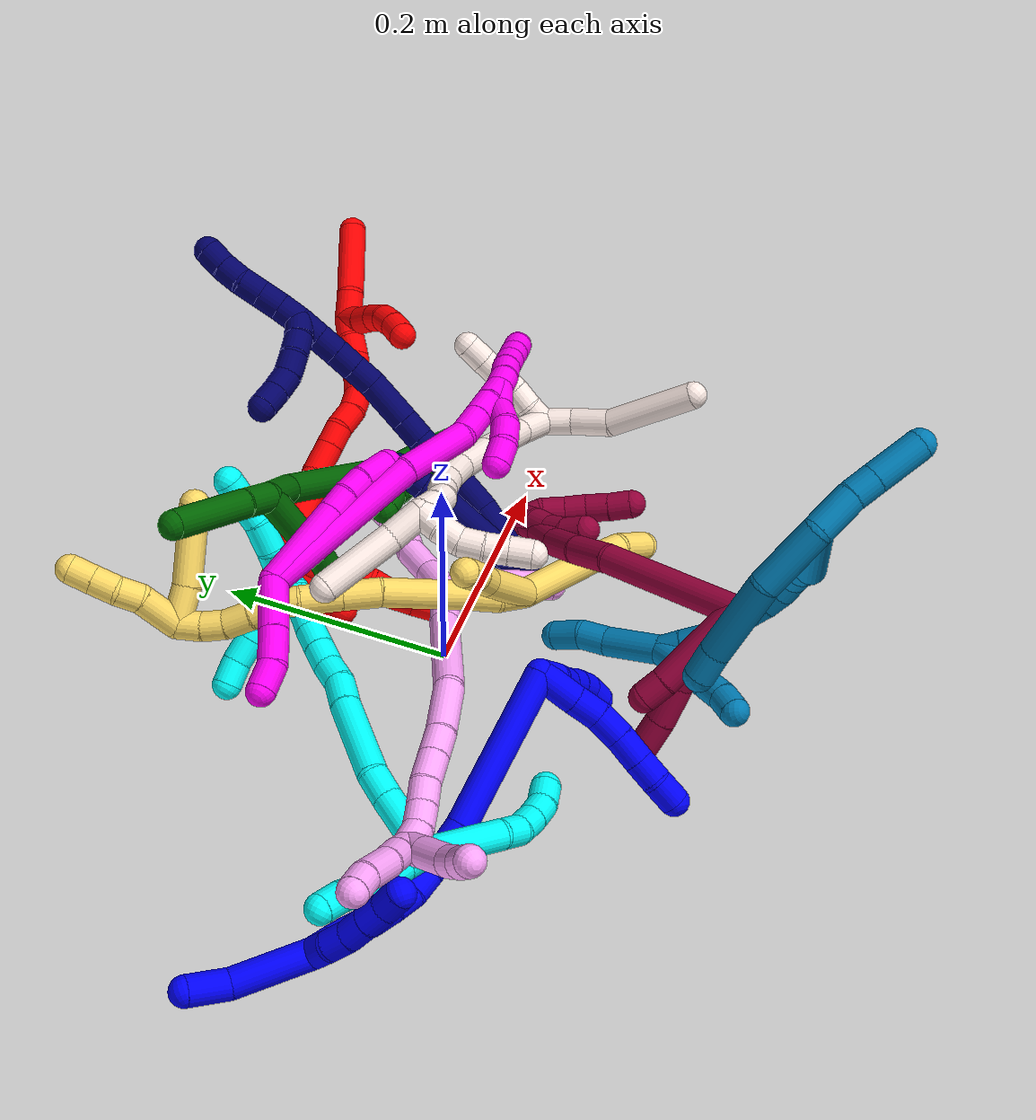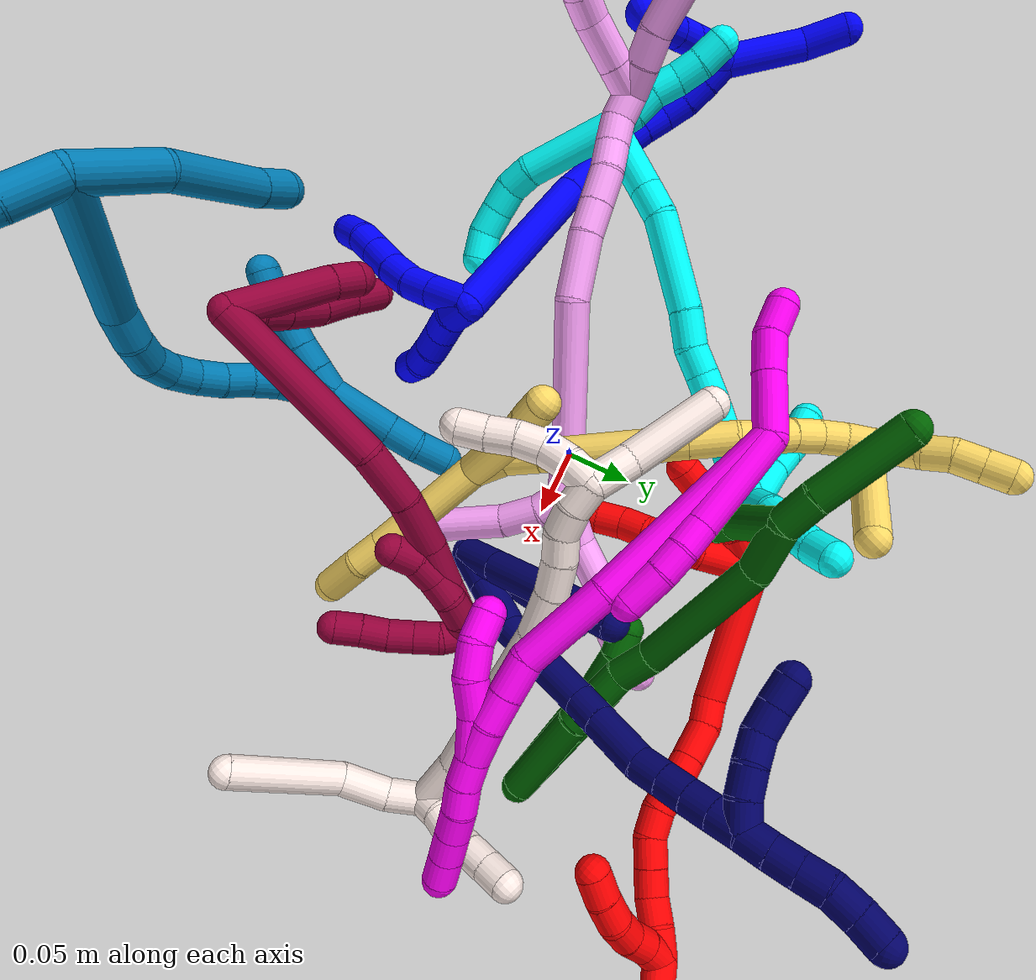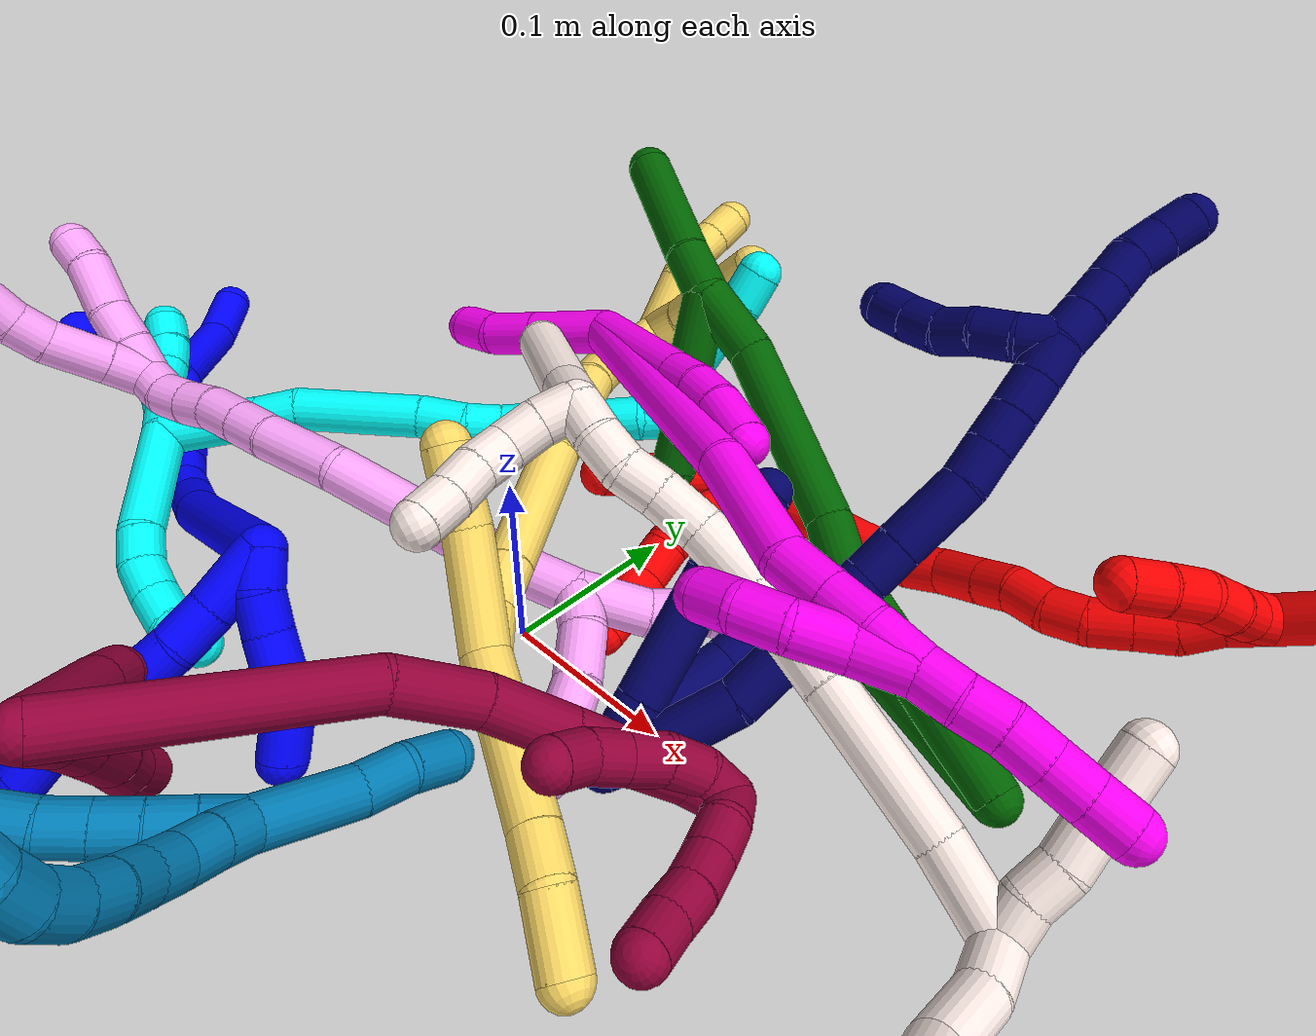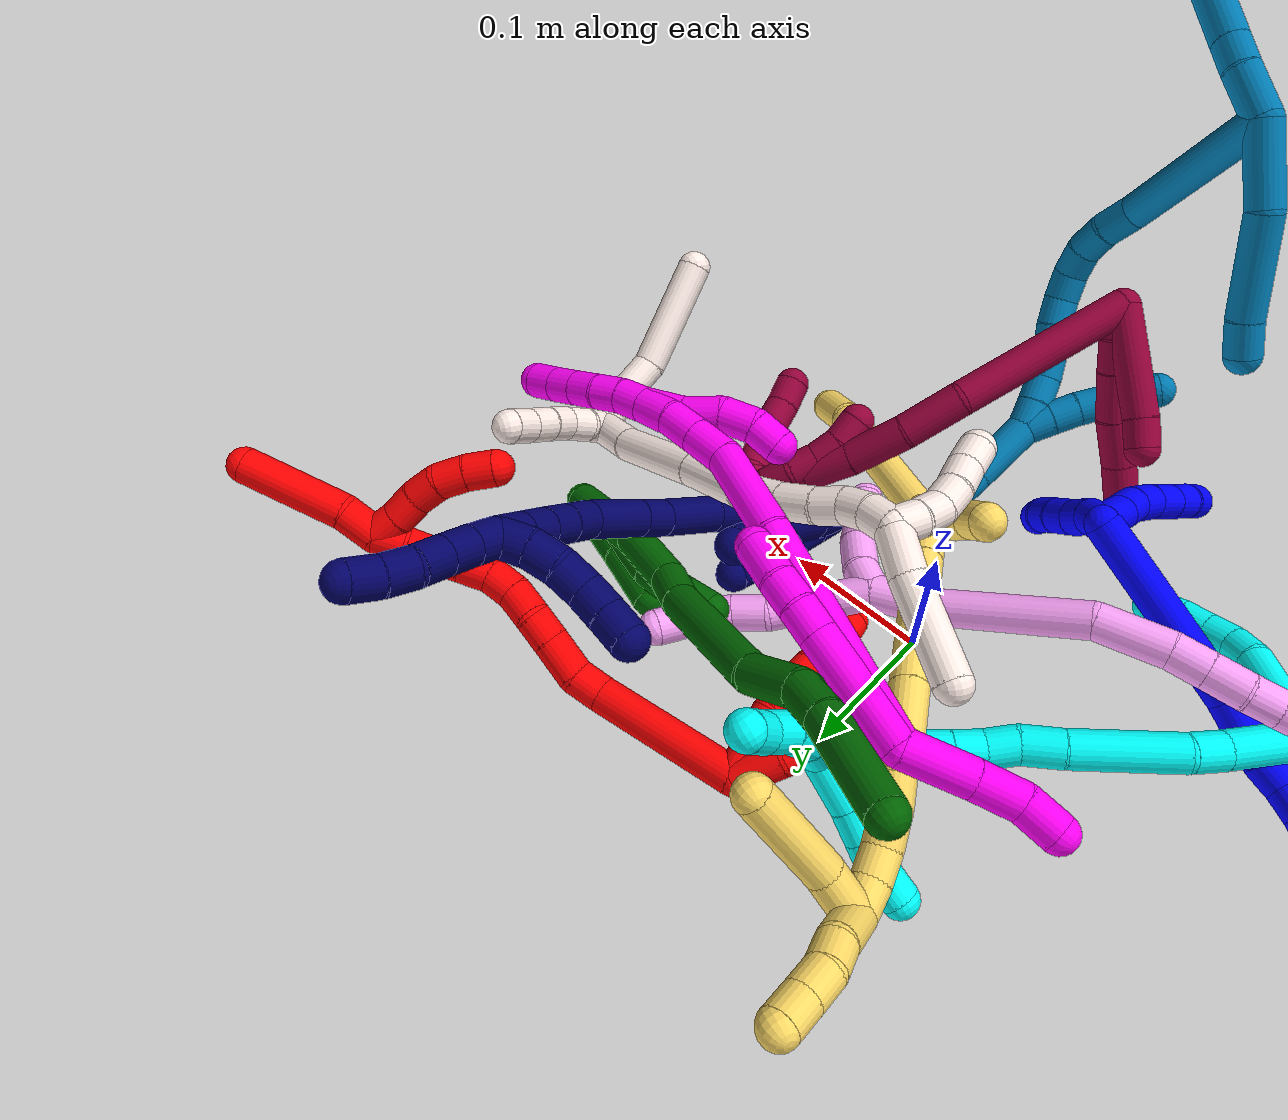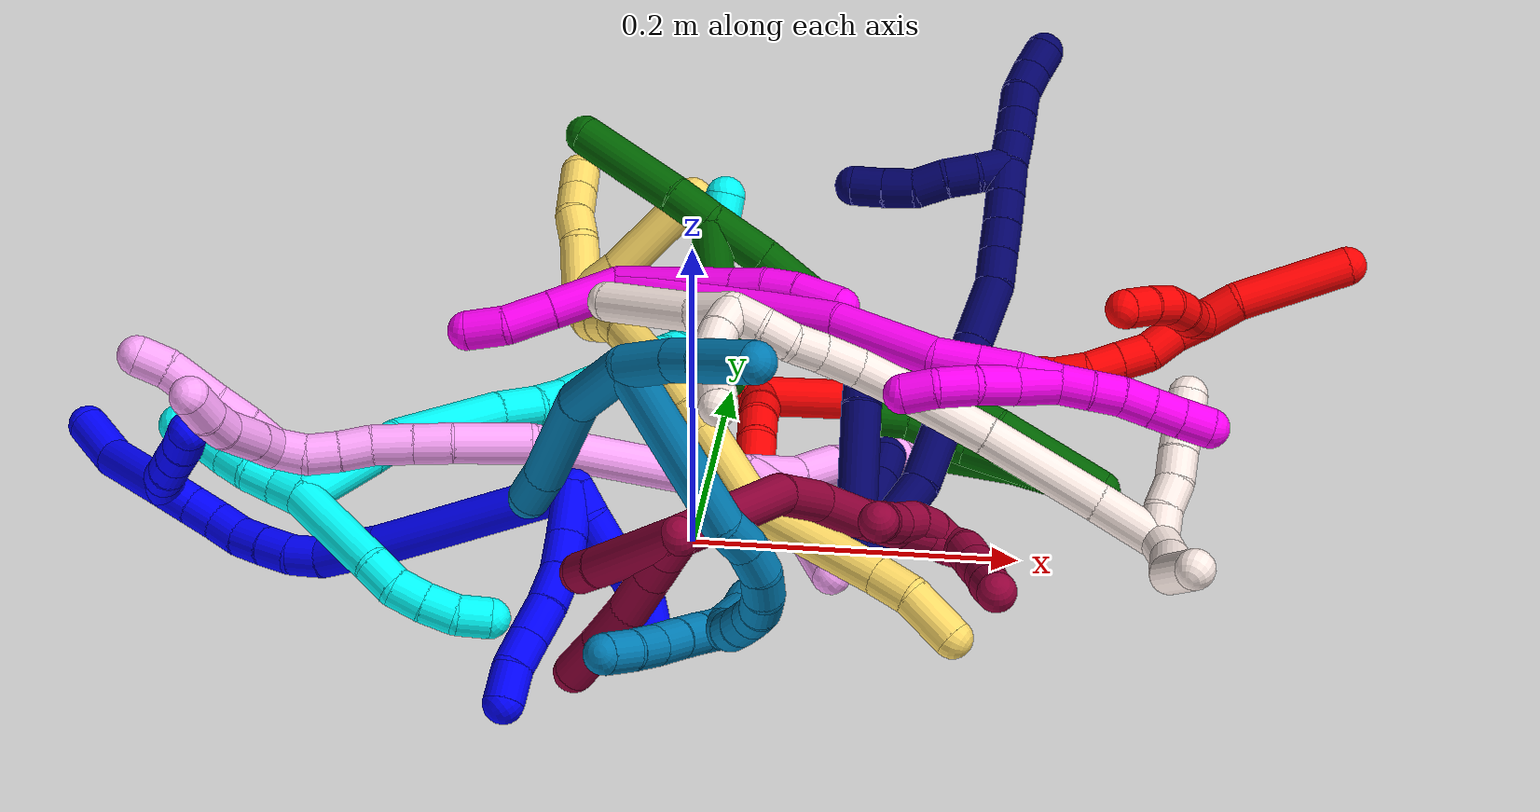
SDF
<sdf version="1.7">
 <world name="default">
  <plugin name="TubeGeneratorPlugin" filename="libtube_generator_plugin.so"/>
  <model name="photoneo_s_sensor">
   <static>1</static>
   <pose>0 0 2 1.57079 1.57079 3.14159</pose>
   <link name="link">
    <inertial><mass>0.1</mass></inertial>
    <sensor name="sensor" type="depth">
     <update_rate>30</update_rate>
     <camera>
      <horizontal_fov>1.22</horizontal_fov>
      <image><width>1920</width><height>1200</height><format>B8G8R8</format></image>
      <clip><near>0.1</near><far>4</far></clip>
      <depth_camera><output>points</output></depth_camera>
     </camera>
     <plugin name="camera_plugin" filename="libgazebo_ros_depth_camera.so">
      <baseline>0.2</baseline>
      <alwaysOn>1</alwaysOn>
      <updateRate>0.0</updateRate>
      <cameraName>camera_ir</cameraName>
      <imageTopicName>/camera/color/image_raw</imageTopicName>
      <cameraInfoTopicName>/camera/color/camera_info</cameraInfoTopicName>
      <depthImageTopicName>/camera/depth/image_raw</depthImageTopicName>
      <depthImageCameraInfoTopicName>/camera/depth/camera_info</depthImageCameraInfoTopicName>
      <pointCloudTopicName>/camera/depth/points</pointCloudTopicName>
      <frameName>fr_optical</frameName>
      <pointCloudCutoff>0.1</pointCloudCutoff>
      <pointCloudCutoffMax>2.0</pointCloudCutoffMax>
      <distortionK1>0</distortionK1>
      <distortionK2>0</distortionK2>
      <distortionK3>0</distortionK3>
      <distortionT1>0</distortionT1>
      <distortionT2>0</distortionT2>
      <CxPrime>0</CxPrime>
      <Cx>0</Cx>
      <Cy>0</Cy>
      <focalLength>0</focalLength>
      <hackBaseline>0</hackBaseline>
     </plugin>
    </sensor>
   </link>
  </model>
  <gravity>0 0 -9.8</gravity>
  <magnetic_field>6e-06 2.3e-05 -4.2e-05</magnetic_field>
  <atmosphere type="adiabatic"/>
  <physics name="default_physics" default="0" type="ode">
   <max_step_size>0.003</max_step_size>
   <real_time_factor>1</real_time_factor>
   <real_time_update_rate>1000</real_time_update_rate>
   <max_contacts>10000</max_contacts>
   <ode>
    <solver>
     <type>quick</type>
     <iters>100</iters>
     <sor>1.3</sor>
     <use_dynamic_moi_rescaling>0</use_dynamic_moi_rescaling>
    </solver>
    <constraints>
     <contact_max_correcting_vel>0</contact_max_correcting_vel>
     <contact_surface_layer>0.001</contact_surface_layer>
     <cfm>0</cfm>
     <erp>0.2</erp>
    </constraints>
   </ode>
  </physics>
  <scene><ambient>0.4 0.4 0.4 1</ambient><background>0.7 0.7 0.7 1</background><shadows>0</shadows></scene>
  <audio><device>default</device></audio>
  <spherical_coordinates>
   <surface_model>EARTH_WGS84</surface_model>
   <latitude_deg>0</latitude_deg>
   <longitude_deg>0</longitude_deg>
   <elevation>0</elevation>
   <heading_deg>0</heading_deg>
  </spherical_coordinates>
  <model name="bin">
   <static>1</static>
   <link name="bottom">
    <collision name="collision-bottom">
     <pose>0 0 -0.01 0 -0 0</pose>
     <geometry><box><size>0.8 0.6 0.02</size></box></geometry>
     <surface>
      <friction><ode><mu>100</mu><mu2>100</mu2></ode></friction>
      <contact><collide_bitmask>65535</collide_bitmask></contact>
     </surface>
    </collision>
   </link>
   <link name="west_wall">
    <collision name="collision-west_wall">
     <pose>-0.41 0 0.1 0 -0 0</pose>
     <geometry><box><size>0.02 0.6 0.2</size></box></geometry>
     <surface>
      <friction><ode><mu>100</mu><mu2>100</mu2></ode></friction>
      <contact><collide_bitmask>65535</collide_bitmask></contact>
     </surface>
    </collision>
   </link>
   <link name="east_wall">
    <collision name="collision-east_wall">
     <pose>0.41 0 0.1 0 -0 0</pose>
     <geometry><box><size>0.02 0.6 0.2</size></box></geometry>
     <surface>
      <friction><ode><mu>100</mu><mu2>100</mu2></ode></friction>
      <contact><collide_bitmask>65535</collide_bitmask></contact>
     </surface>
    </collision>
   </link>
   <link name="south_wall">
    <collision name="collision-south_wall">
     <pose>0 -0.31 0.1 0 -0 0</pose>
     <geometry><box><size>0.8 0.02 0.2</size></box></geometry>
     <surface>
      <friction><ode><mu>100</mu><mu2>100</mu2></ode></friction>
      <contact><collide_bitmask>65535</collide_bitmask></contact>
     </surface>
    </collision>
   </link>
   <link name="north_wall">
    <collision name="collision-north_wall">
     <pose>0 0.31 0.1 0 -0 0</pose>
     <geometry><box><size>0.8 0.02 0.2</size></box></geometry>
     <surface>
      <friction><ode><mu>100</mu><mu2>100</mu2></ode></friction>
      <contact><collide_bitmask>65535</collide_bitmask></contact>
     </surface>
    </collision>
   </link>
  </model>
  <model name="1">
   <static>0</static>
   <link name="1">
    <collision name="collision-cylinder-e_1_2_8">
     <pose>0.008142 -0.007745 0.013165 0.531779 0.489731 0.135894</pose>
     <geometry><cylinder><radius>0.0125</radius><length>0.034618</length></cylinder></geometry>
     <surface>
      <friction><ode><mu>1.16</mu><mu2>1.16</mu2><slip1>0</slip1><slip2>0</slip2></ode></friction>
      <contact><ode><kp>1e+06</kp><kd>1</kd><max_vel>0</max_vel><min_depth>0.001</min_depth></ode></contact>
     </surface>
    </collision>
    <visual name="visual-cylinder-e_1_2_8">
     <pose>0.008142 -0.007745 0.013165 0.531779 0.489731 0.135894</pose>
     <geometry><cylinder><radius>0.0125</radius><length>0.034618</length></cylinder></geometry>
     <material><ambient>0 0 1 1</ambient></material>
    </visual>
    <collision name="collision-cylinder-e_2_8_9">
     <pose>0.022457 -0.019949 0.035385 0.45761 0.548904 0.130952</pose>
     <geometry><cylinder><radius>0.0125</radius><length>0.023662</length></cylinder></geometry>
     <surface>
      <friction><ode><mu>1.16</mu><mu2>1.16</mu2><slip1>0</slip1><slip2>0</slip2></ode></friction>
      <contact><ode><kp>1e+06</kp><kd>1</kd><max_vel>0</max_vel><min_depth>0.001</min_depth></ode></contact>
     </surface>
    </collision>
    <visual name="visual-cylinder-e_2_8_9">
     <pose>0.022457 -0.019949 0.035385 0.45761 0.548904 0.130952</pose>
     <geometry><cylinder><radius>0.0125</radius><length>0.023662</length></cylinder></geometry>
     <material><ambient>0 0 1 1</ambient></material>
    </visual>
    <collision name="collision-cylinder-e_3_9_10">
     <pose>0.032946 -0.027941 0.05485 0.327095 0.37415 0.062453</pose>
     <geometry><cylinder><radius>0.0125</radius><length>0.023623</length></cylinder></geometry>
     <surface>
      <friction><ode><mu>1.16</mu><mu2>1.16</mu2><slip1>0</slip1><slip2>0</slip2></ode></friction>
      <contact><ode><kp>1e+06</kp><kd>1</kd><max_vel>0</max_vel><min_depth>0.001</min_depth></ode></contact>
     </surface>
    </collision>
    <visual name="visual-cylinder-e_3_9_10">
     <pose>0.032946 -0.027941 0.05485 0.327095 0.37415 0.062453</pose>
     <geometry><cylinder><radius>0.0125</radius><length>0.023623</length></cylinder></geometry>
     <material><ambient>0 0 1 1</ambient></material>
    </visual>
    <collision name="collision-cylinder-e_4_10_11">
     <pose>0.040623 -0.034511 0.076657 0.260489 0.277591 0.036592</pose>
     <geometry><cylinder><radius>0.0125</radius><length>0.024525</length></cylinder></geometry>
     <surface>
      <friction><ode><mu>1.16</mu><mu2>1.16</mu2><slip1>0</slip1><slip2>0</slip2></ode></friction>
      <contact><ode><kp>1e+06</kp><kd>1</kd><max_vel>0</max_vel><min_depth>0.001</min_depth></ode></contact>
     </surface>
    </collision>
    <visual name="visual-cylinder-e_4_10_11">
     <pose>0.040623 -0.034511 0.076657 0.260489 0.277591 0.036592</pose>
     <geometry><cylinder><radius>0.0125</radius><length>0.024525</length></cylinder></geometry>
     <material><ambient>0 0 1 1</ambient></material>
    </visual>
    <collision name="collision-cylinder-e_5_11_12">
     <pose>0.047111 -0.040122 0.097703 0.260688 0.303367 0.04007</pose>
     <geometry><cylinder><radius>0.0125</radius><length>0.020933</length></cylinder></geometry>
     <surface>
      <friction><ode><mu>1.16</mu><mu2>1.16</mu2><slip1>0</slip1><slip2>0</slip2></ode></friction>
      <contact><ode><kp>1e+06</kp><kd>1</kd><max_vel>0</max_vel><min_depth>0.001</min_depth></ode></contact>
     </surface>
    </collision>
    <visual name="visual-cylinder-e_5_11_12">
     <pose>0.047111 -0.040122 0.097703 0.260688 0.303367 0.04007</pose>
     <geometry><cylinder><radius>0.0125</radius><length>0.020933</length></cylinder></geometry>
     <material><ambient>0 0 1 1</ambient></material>
    </visual>
    <collision name="collision-cylinder-e_6_12_6">
     <pose>0.053522 -0.048153 0.116713 0.52787 0.29439 0.080092</pose>
     <geometry><cylinder><radius>0.0125</radius><length>0.02264</length></cylinder></geometry>
     <surface>
      <friction><ode><mu>1.16</mu><mu2>1.16</mu2><slip1>0</slip1><slip2>0</slip2></ode></friction>
      <contact><ode><kp>1e+06</kp><kd>1</kd><max_vel>0</max_vel><min_depth>0.001</min_depth></ode></contact>
     </surface>
    </collision>
    <visual name="visual-cylinder-e_6_12_6">
     <pose>0.053522 -0.048153 0.116713 0.52787 0.29439 0.080092</pose>
     <geometry><cylinder><radius>0.0125</radius><length>0.02264</length></cylinder></geometry>
     <material><ambient>0 0 1 1</ambient></material>
    </visual>
    <collision name="collision-cylinder-e_1_2_13">
     <pose>0.004697 -0.008522 0.002306 1.30657 0.488906 0.377306</pose>
     <geometry><cylinder><radius>0.0125</radius><length>0.02</length></cylinder></geometry>
     <surface>
      <friction><ode><mu>1.16</mu><mu2>1.16</mu2><slip1>0</slip1><slip2>0</slip2></ode></friction>
      <contact><ode><kp>1e+06</kp><kd>1</kd><max_vel>0</max_vel><min_depth>0.001</min_depth></ode></contact>
     </surface>
    </collision>
    <visual name="visual-cylinder-e_1_2_13">
     <pose>0.004697 -0.008522 0.002306 1.30657 0.488906 0.377306</pose>
     <geometry><cylinder><radius>0.0125</radius><length>0.02</length></cylinder></geometry>
     <material><ambient>0 0 1 1</ambient></material>
    </visual>
    <collision name="collision-cylinder-e_2_13_14">
     <pose>0.011423 -0.026778 0.00568 1.46144 0.204358 0.183273</pose>
     <geometry><cylinder><radius>0.0125</radius><length>0.02</length></cylinder></geometry>
     <surface>
      <friction><ode><mu>1.16</mu><mu2>1.16</mu2><slip1>0</slip1><slip2>0</slip2></ode></friction>
      <contact><ode><kp>1e+06</kp><kd>1</kd><max_vel>0</max_vel><min_depth>0.001</min_depth></ode></contact>
     </surface>
    </collision>
    <visual name="visual-cylinder-e_2_13_14">
     <pose>0.011423 -0.026778 0.00568 1.46144 0.204358 0.183273</pose>
     <geometry><cylinder><radius>0.0125</radius><length>0.02</length></cylinder></geometry>
     <material><ambient>0 0 1 1</ambient></material>
    </visual>
    <collision name="collision-cylinder-e_3_14_15">
     <pose>0.016381 -0.046072 0.006686 1.5773 0.297266 0.299178</pose>
     <geometry><cylinder><radius>0.0125</radius><length>0.02</length></cylinder></geometry>
     <surface>
      <friction><ode><mu>1.16</mu><mu2>1.16</mu2><slip1>0</slip1><slip2>0</slip2></ode></friction>
      <contact><ode><kp>1e+06</kp><kd>1</kd><max_vel>0</max_vel><min_depth>0.001</min_depth></ode></contact>
     </surface>
    </collision>
    <visual name="visual-cylinder-e_3_14_15">
     <pose>0.016381 -0.046072 0.006686 1.5773 0.297266 0.299178</pose>
     <geometry><cylinder><radius>0.0125</radius><length>0.02</length></cylinder></geometry>
     <material><ambient>0 0 1 1</ambient></material>
    </visual>
    <collision name="collision-cylinder-e_4_15_16">
     <pose>0.021991 -0.065181 0.007912 1.43673 0.271403 0.237597</pose>
     <geometry><cylinder><radius>0.0125</radius><length>0.02</length></cylinder></geometry>
     <surface>
      <friction><ode><mu>1.16</mu><mu2>1.16</mu2><slip1>0</slip1><slip2>0</slip2></ode></friction>
      <contact><ode><kp>1e+06</kp><kd>1</kd><max_vel>0</max_vel><min_depth>0.001</min_depth></ode></contact>
     </surface>
    </collision>
    <visual name="visual-cylinder-e_4_15_16">
     <pose>0.021991 -0.065181 0.007912 1.43673 0.271403 0.237597</pose>
     <geometry><cylinder><radius>0.0125</radius><length>0.02</length></cylinder></geometry>
     <material><ambient>0 0 1 1</ambient></material>
    </visual>
    <collision name="collision-cylinder-e_5_16_5">
     <pose>0.026846 -0.08337 0.013738 1.08727 0.21915 0.132787</pose>
     <geometry><cylinder><radius>0.0125</radius><length>0.02</length></cylinder></geometry>
     <surface>
      <friction><ode><mu>1.16</mu><mu2>1.16</mu2><slip1>0</slip1><slip2>0</slip2></ode></friction>
      <contact><ode><kp>1e+06</kp><kd>1</kd><max_vel>0</max_vel><min_depth>0.001</min_depth></ode></contact>
     </surface>
    </collision>
    <visual name="visual-cylinder-e_5_16_5">
     <pose>0.026846 -0.08337 0.013738 1.08727 0.21915 0.132787</pose>
     <geometry><cylinder><radius>0.0125</radius><length>0.02</length></cylinder></geometry>
     <material><ambient>0 0 1 1</ambient></material>
    </visual>
    <collision name="collision-cylinder-e_1_2_17">
     <pose>-0.05036 0.006671 0.044685 -0.148199 -0.839562 0.06624</pose>
     <geometry><cylinder><radius>0.0125</radius><length>0.135314</length></cylinder></geometry>
     <surface>
      <friction><ode><mu>1.16</mu><mu2>1.16</mu2><slip1>0</slip1><slip2>0</slip2></ode></friction>
      <contact><ode><kp>1e+06</kp><kd>1</kd><max_vel>0</max_vel><min_depth>0.001</min_depth></ode></contact>
     </surface>
    </collision>
    <visual name="visual-cylinder-e_1_2_17">
     <pose>-0.05036 0.006671 0.044685 -0.148199 -0.839562 0.06624</pose>
     <geometry><cylinder><radius>0.0125</radius><length>0.135314</length></cylinder></geometry>
     <material><ambient>0 0 1 1</ambient></material>
    </visual>
    <collision name="collision-cylinder-e_2_17_18">
     <pose>-0.118841 0.015495 0.101624 -0.173911 -0.969129 0.091718</pose>
     <geometry><cylinder><radius>0.0125</radius><length>0.043961</length></cylinder></geometry>
     <surface>
      <friction><ode><mu>1.16</mu><mu2>1.16</mu2><slip1>0</slip1><slip2>0</slip2></ode></friction>
      <contact><ode><kp>1e+06</kp><kd>1</kd><max_vel>0</max_vel><min_depth>0.001</min_depth></ode></contact>
     </surface>
    </collision>
    <visual name="visual-cylinder-e_2_17_18">
     <pose>-0.118841 0.015495 0.101624 -0.173911 -0.969129 0.091718</pose>
     <geometry><cylinder><radius>0.0125</radius><length>0.043961</length></cylinder></geometry>
     <material><ambient>0 0 1 1</ambient></material>
    </visual>
    <collision name="collision-cylinder-e_3_18_19">
     <pose>-0.144785 0.021748 0.119223 -0.654344 -0.859893 0.308762</pose>
     <geometry><cylinder><radius>0.0125</radius><length>0.02065</length></cylinder></geometry>
     <surface>
      <friction><ode><mu>1.16</mu><mu2>1.16</mu2><slip1>0</slip1><slip2>0</slip2></ode></friction>
      <contact><ode><kp>1e+06</kp><kd>1</kd><max_vel>0</max_vel><min_depth>0.001</min_depth></ode></contact>
     </surface>
    </collision>
    <visual name="visual-cylinder-e_3_18_19">
     <pose>-0.144785 0.021748 0.119223 -0.654344 -0.859893 0.308762</pose>
     <geometry><cylinder><radius>0.0125</radius><length>0.02065</length></cylinder></geometry>
     <material><ambient>0 0 1 1</ambient></material>
    </visual>
    <collision name="collision-cylinder-e_4_19_20">
     <pose>-0.161029 0.030395 0.127589 -0.984343 -0.995697 0.567135</pose>
     <geometry><cylinder><radius>0.0125</radius><length>0.020067</length></cylinder></geometry>
     <surface>
      <friction><ode><mu>1.16</mu><mu2>1.16</mu2><slip1>0</slip1><slip2>0</slip2></ode></friction>
      <contact><ode><kp>1e+06</kp><kd>1</kd><max_vel>0</max_vel><min_depth>0.001</min_depth></ode></contact>
     </surface>
    </collision>
    <visual name="visual-cylinder-e_4_19_20">
     <pose>-0.161029 0.030395 0.127589 -0.984343 -0.995697 0.567135</pose>
     <geometry><cylinder><radius>0.0125</radius><length>0.020067</length></cylinder></geometry>
     <material><ambient>0 0 1 1</ambient></material>
    </visual>
    <collision name="collision-cylinder-e_5_20_21">
     <pose>-0.178218 0.039121 0.132991 -1.053 -1.06896 0.662746</pose>
     <geometry><cylinder><radius>0.0125</radius><length>0.020006</length></cylinder></geometry>
     <surface>
      <friction><ode><mu>1.16</mu><mu2>1.16</mu2><slip1>0</slip1><slip2>0</slip2></ode></friction>
      <contact><ode><kp>1e+06</kp><kd>1</kd><max_vel>0</max_vel><min_depth>0.001</min_depth></ode></contact>
     </surface>
    </collision>
    <visual name="visual-cylinder-e_5_20_21">
     <pose>-0.178218 0.039121 0.132991 -1.053 -1.06896 0.662746</pose>
     <geometry><cylinder><radius>0.0125</radius><length>0.020006</length></cylinder></geometry>
     <material><ambient>0 0 1 1</ambient></material>
    </visual>
    <collision name="collision-cylinder-e_6_21_22">
     <pose>-0.195034 0.049125 0.136546 -1.37195 -0.934903 0.783659</pose>
     <geometry><cylinder><radius>0.0125</radius><length>0.020002</length></cylinder></geometry>
     <surface>
      <friction><ode><mu>1.16</mu><mu2>1.16</mu2><slip1>0</slip1><slip2>0</slip2></ode></friction>
      <contact><ode><kp>1e+06</kp><kd>1</kd><max_vel>0</max_vel><min_depth>0.001</min_depth></ode></contact>
     </surface>
    </collision>
    <visual name="visual-cylinder-e_6_21_22">
     <pose>-0.195034 0.049125 0.136546 -1.37195 -0.934903 0.783659</pose>
     <geometry><cylinder><radius>0.0125</radius><length>0.020002</length></cylinder></geometry>
     <material><ambient>0 0 1 1</ambient></material>
    </visual>
    <collision name="collision-cylinder-e_7_22_23">
     <pose>-0.209868 0.061987 0.13981 -1.28203 -0.746102 0.568229</pose>
     <geometry><cylinder><radius>0.0125</radius><length>0.020001</length></cylinder></geometry>
     <surface>
      <friction><ode><mu>1.16</mu><mu2>1.16</mu2><slip1>0</slip1><slip2>0</slip2></ode></friction>
      <contact><ode><kp>1e+06</kp><kd>1</kd><max_vel>0</max_vel><min_depth>0.001</min_depth></ode></contact>
     </surface>
    </collision>
    <visual name="visual-cylinder-e_7_22_23">
     <pose>-0.209868 0.061987 0.13981 -1.28203 -0.746102 0.568229</pose>
     <geometry><cylinder><radius>0.0125</radius><length>0.020001</length></cylinder></geometry>
     <material><ambient>0 0 1 1</ambient></material>
    </visual>
    <collision name="collision-cylinder-e_8_23_1">
     <pose>-0.222887 0.076489 0.144246 -1.26639 -0.672635 0.502384</pose>
     <geometry><cylinder><radius>0.0125</radius><length>0.02</length></cylinder></geometry>
     <surface>
      <friction><ode><mu>1.16</mu><mu2>1.16</mu2><slip1>0</slip1><slip2>0</slip2></ode></friction>
      <contact><ode><kp>1e+06</kp><kd>1</kd><max_vel>0</max_vel><min_depth>0.001</min_depth></ode></contact>
     </surface>
    </collision>
    <visual name="visual-cylinder-e_8_23_1">
     <pose>-0.222887 0.076489 0.144246 -1.26639 -0.672635 0.502384</pose>
     <geometry><cylinder><radius>0.0125</radius><length>0.02</length></cylinder></geometry>
     <material><ambient>0 0 1 1</ambient></material>
    </visual>
    <collision name="collision-cylinder-e_1_1_24">
     <pose>-0.221178 0.089996 0.147246 -1.46277 0.917205 -0.83414</pose>
     <geometry><cylinder><radius>0.0125</radius><length>0.02</length></cylinder></geometry>
     <surface>
      <friction><ode><mu>1.16</mu><mu2>1.16</mu2><slip1>0</slip1><slip2>0</slip2></ode></friction>
      <contact><ode><kp>1e+06</kp><kd>1</kd><max_vel>0</max_vel><min_depth>0.001</min_depth></ode></contact>
     </surface>
    </collision>
    <visual name="visual-cylinder-e_1_1_24">
     <pose>-0.221178 0.089996 0.147246 -1.46277 0.917205 -0.83414</pose>
     <geometry><cylinder><radius>0.0125</radius><length>0.02</length></cylinder></geometry>
     <material><ambient>0 0 1 1</ambient></material>
    </visual>
    <collision name="collision-cylinder-e_2_24_25">
     <pose>-0.20401 0.099888 0.14778 -1.60252 1.17568 -1.20514</pose>
     <geometry><cylinder><radius>0.0125</radius><length>0.02</length></cylinder></geometry>
     <surface>
      <friction><ode><mu>1.16</mu><mu2>1.16</mu2><slip1>0</slip1><slip2>0</slip2></ode></friction>
      <contact><ode><kp>1e+06</kp><kd>1</kd><max_vel>0</max_vel><min_depth>0.001</min_depth></ode></contact>
     </surface>
    </collision>
    <visual name="visual-cylinder-e_2_24_25">
     <pose>-0.20401 0.099888 0.14778 -1.60252 1.17568 -1.20514</pose>
     <geometry><cylinder><radius>0.0125</radius><length>0.02</length></cylinder></geometry>
     <material><ambient>0 0 1 1</ambient></material>
    </visual>
    <collision name="collision-cylinder-e_3_25_26">
     <pose>-0.185964 0.108213 0.146169 -1.89167 1.07939 -1.38591</pose>
     <geometry><cylinder><radius>0.0125</radius><length>0.02</length></cylinder></geometry>
     <surface>
      <friction><ode><mu>1.16</mu><mu2>1.16</mu2><slip1>0</slip1><slip2>0</slip2></ode></friction>
      <contact><ode><kp>1e+06</kp><kd>1</kd><max_vel>0</max_vel><min_depth>0.001</min_depth></ode></contact>
     </surface>
    </collision>
    <visual name="visual-cylinder-e_3_25_26">
     <pose>-0.185964 0.108213 0.146169 -1.89167 1.07939 -1.38591</pose>
     <geometry><cylinder><radius>0.0125</radius><length>0.02</length></cylinder></geometry>
     <material><ambient>0 0 1 1</ambient></material>
    </visual>
    <collision name="collision-cylinder-e_4_26_27">
     <pose>-0.168254 0.116975 0.14308 -1.92839 1.09584 -1.44272</pose>
     <geometry><cylinder><radius>0.0125</radius><length>0.02</length></cylinder></geometry>
     <surface>
      <friction><ode><mu>1.16</mu><mu2>1.16</mu2><slip1>0</slip1><slip2>0</slip2></ode></friction>
      <contact><ode><kp>1e+06</kp><kd>1</kd><max_vel>0</max_vel><min_depth>0.001</min_depth></ode></contact>
     </surface>
    </collision>
    <visual name="visual-cylinder-e_4_26_27">
     <pose>-0.168254 0.116975 0.14308 -1.92839 1.09584 -1.44272</pose>
     <geometry><cylinder><radius>0.0125</radius><length>0.02</length></cylinder></geometry>
     <material><ambient>0 0 1 1</ambient></material>
    </visual>
    <collision name="collision-cylinder-e_5_27_4">
     <pose>-0.151156 0.126661 0.13961 -1.90404 0.962269 -1.26527</pose>
     <geometry><cylinder><radius>0.0125</radius><length>0.02</length></cylinder></geometry>
     <surface>
      <friction><ode><mu>1.16</mu><mu2>1.16</mu2><slip1>0</slip1><slip2>0</slip2></ode></friction>
      <contact><ode><kp>1e+06</kp><kd>1</kd><max_vel>0</max_vel><min_depth>0.001</min_depth></ode></contact>
     </surface>
    </collision>
    <visual name="visual-cylinder-e_5_27_4">
     <pose>-0.151156 0.126661 0.13961 -1.90404 0.962269 -1.26527</pose>
     <geometry><cylinder><radius>0.0125</radius><length>0.02</length></cylinder></geometry>
     <material><ambient>0 0 1 1</ambient></material>
    </visual>
    <collision name="collision-cylinder-e_1_1_28">
     <pose>-0.260824 0.09193 0.146333 -1.60304 -1.32413 1.35552</pose>
     <geometry><cylinder><radius>0.0125</radius><length>0.065392</length></cylinder></geometry>
     <surface>
      <friction><ode><mu>1.16</mu><mu2>1.16</mu2><slip1>0</slip1><slip2>0</slip2></ode></friction>
      <contact><ode><kp>1e+06</kp><kd>1</kd><max_vel>0</max_vel><min_depth>0.001</min_depth></ode></contact>
     </surface>
    </collision>
    <visual name="visual-cylinder-e_1_1_28">
     <pose>-0.260824 0.09193 0.146333 -1.60304 -1.32413 1.35552</pose>
     <geometry><cylinder><radius>0.0125</radius><length>0.065392</length></cylinder></geometry>
     <material><ambient>0 0 1 1</ambient></material>
    </visual>
    <collision name="collision-cylinder-e_2_28_3">
     <pose>-0.307065 0.108931 0.143473 -1.85171 -0.997201 1.25306</pose>
     <geometry><cylinder><radius>0.0125</radius><length>0.034608</length></cylinder></geometry>
     <surface>
      <friction><ode><mu>1.16</mu><mu2>1.16</mu2><slip1>0</slip1><slip2>0</slip2></ode></friction>
      <contact><ode><kp>1e+06</kp><kd>1</kd><max_vel>0</max_vel><min_depth>0.001</min_depth></ode></contact>
     </surface>
    </collision>
    <visual name="visual-cylinder-e_2_28_3">
     <pose>-0.307065 0.108931 0.143473 -1.85171 -0.997201 1.25306</pose>
     <geometry><cylinder><radius>0.0125</radius><length>0.034608</length></cylinder></geometry>
     <material><ambient>0 0 1 1</ambient></material>
    </visual>
    <collision name="collision-sphere-3">
     <pose>-0.321599 0.117954 0.140869 0 -0 0</pose>
     <geometry><sphere><radius>0.0125</radius></sphere></geometry>
     <surface>
      <friction><ode><mu>1.16</mu><mu2>1.16</mu2><slip1>0</slip1><slip2>0</slip2></ode></friction>
      <contact><ode><kp>1e+06</kp><kd>1</kd><max_vel>0</max_vel><min_depth>0.001</min_depth></ode></contact>
     </surface>
    </collision>
    <visual name="visual-sphere-3">
     <pose>-0.321599 0.117954 0.140869 0 -0 0</pose>
     <geometry><sphere><radius>0.0125</radius></sphere></geometry>
     <material><ambient>0 0 1 1</ambient></material>
    </visual>
    <collision name="collision-sphere-28">
     <pose>-0.29253 0.099909 0.146076 0 -0 0</pose>
     <geometry><sphere><radius>0.0125</radius></sphere></geometry>
     <surface>
      <friction><ode><mu>1.16</mu><mu2>1.16</mu2><slip1>0</slip1><slip2>0</slip2></ode></friction>
      <contact><ode><kp>1e+06</kp><kd>1</kd><max_vel>0</max_vel><min_depth>0.001</min_depth></ode></contact>
     </surface>
    </collision>
    <visual name="visual-sphere-28">
     <pose>-0.29253 0.099909 0.146076 0 -0 0</pose>
     <geometry><sphere><radius>0.0125</radius></sphere></geometry>
     <material><ambient>0 0 1 1</ambient></material>
    </visual>
    <collision name="collision-sphere-4">
     <pose>-0.142951 0.132063 0.13774 0 -0 0</pose>
     <geometry><sphere><radius>0.0125</radius></sphere></geometry>
     <surface>
      <friction><ode><mu>1.16</mu><mu2>1.16</mu2><slip1>0</slip1><slip2>0</slip2></ode></friction>
      <contact><ode><kp>1e+06</kp><kd>1</kd><max_vel>0</max_vel><min_depth>0.001</min_depth></ode></contact>
     </surface>
    </collision>
    <visual name="visual-sphere-4">
     <pose>-0.142951 0.132063 0.13774 0 -0 0</pose>
     <geometry><sphere><radius>0.0125</radius></sphere></geometry>
     <material><ambient>0 0 1 1</ambient></material>
    </visual>
    <collision name="collision-sphere-27">
     <pose>-0.159361 0.121258 0.14148 0 -0 0</pose>
     <geometry><sphere><radius>0.0125</radius></sphere></geometry>
     <surface>
      <friction><ode><mu>1.16</mu><mu2>1.16</mu2><slip1>0</slip1><slip2>0</slip2></ode></friction>
      <contact><ode><kp>1e+06</kp><kd>1</kd><max_vel>0</max_vel><min_depth>0.001</min_depth></ode></contact>
     </surface>
    </collision>
    <visual name="visual-sphere-27">
     <pose>-0.159361 0.121258 0.14148 0 -0 0</pose>
     <geometry><sphere><radius>0.0125</radius></sphere></geometry>
     <material><ambient>0 0 1 1</ambient></material>
    </visual>
    <collision name="collision-sphere-26">
     <pose>-0.177147 0.112691 0.144681 0 -0 0</pose>
     <geometry><sphere><radius>0.0125</radius></sphere></geometry>
     <surface>
      <friction><ode><mu>1.16</mu><mu2>1.16</mu2><slip1>0</slip1><slip2>0</slip2></ode></friction>
      <contact><ode><kp>1e+06</kp><kd>1</kd><max_vel>0</max_vel><min_depth>0.001</min_depth></ode></contact>
     </surface>
    </collision>
    <visual name="visual-sphere-26">
     <pose>-0.177147 0.112691 0.144681 0 -0 0</pose>
     <geometry><sphere><radius>0.0125</radius></sphere></geometry>
     <material><ambient>0 0 1 1</ambient></material>
    </visual>
    <collision name="collision-sphere-25">
     <pose>-0.19478 0.103735 0.147657 0 -0 0</pose>
     <geometry><sphere><radius>0.0125</radius></sphere></geometry>
     <surface>
      <friction><ode><mu>1.16</mu><mu2>1.16</mu2><slip1>0</slip1><slip2>0</slip2></ode></friction>
      <contact><ode><kp>1e+06</kp><kd>1</kd><max_vel>0</max_vel><min_depth>0.001</min_depth></ode></contact>
     </surface>
    </collision>
    <visual name="visual-sphere-25">
     <pose>-0.19478 0.103735 0.147657 0 -0 0</pose>
     <geometry><sphere><radius>0.0125</radius></sphere></geometry>
     <material><ambient>0 0 1 1</ambient></material>
    </visual>
    <collision name="collision-sphere-24">
     <pose>-0.213239 0.096041 0.147902 0 -0 0</pose>
     <geometry><sphere><radius>0.0125</radius></sphere></geometry>
     <surface>
      <friction><ode><mu>1.16</mu><mu2>1.16</mu2><slip1>0</slip1><slip2>0</slip2></ode></friction>
      <contact><ode><kp>1e+06</kp><kd>1</kd><max_vel>0</max_vel><min_depth>0.001</min_depth></ode></contact>
     </surface>
    </collision>
    <visual name="visual-sphere-24">
     <pose>-0.213239 0.096041 0.147902 0 -0 0</pose>
     <geometry><sphere><radius>0.0125</radius></sphere></geometry>
     <material><ambient>0 0 1 1</ambient></material>
    </visual>
    <collision name="collision-sphere-1">
     <pose>-0.229118 0.083951 0.146591 0 -0 0</pose>
     <geometry><sphere><radius>0.0125</radius></sphere></geometry>
     <surface>
      <friction><ode><mu>1.16</mu><mu2>1.16</mu2><slip1>0</slip1><slip2>0</slip2></ode></friction>
      <contact><ode><kp>1e+06</kp><kd>1</kd><max_vel>0</max_vel><min_depth>0.001</min_depth></ode></contact>
     </surface>
    </collision>
    <visual name="visual-sphere-1">
     <pose>-0.229118 0.083951 0.146591 0 -0 0</pose>
     <geometry><sphere><radius>0.0125</radius></sphere></geometry>
     <material><ambient>0 0 1 1</ambient></material>
    </visual>
    <collision name="collision-sphere-23">
     <pose>-0.216657 0.069026 0.141902 0 -0 0</pose>
     <geometry><sphere><radius>0.0125</radius></sphere></geometry>
     <surface>
      <friction><ode><mu>1.16</mu><mu2>1.16</mu2><slip1>0</slip1><slip2>0</slip2></ode></friction>
      <contact><ode><kp>1e+06</kp><kd>1</kd><max_vel>0</max_vel><min_depth>0.001</min_depth></ode></contact>
     </surface>
    </collision>
    <visual name="visual-sphere-23">
     <pose>-0.216657 0.069026 0.141902 0 -0 0</pose>
     <geometry><sphere><radius>0.0125</radius></sphere></geometry>
     <material><ambient>0 0 1 1</ambient></material>
    </visual>
    <collision name="collision-sphere-22">
     <pose>-0.20308 0.054947 0.137719 0 -0 0</pose>
     <geometry><sphere><radius>0.0125</radius></sphere></geometry>
     <surface>
      <friction><ode><mu>1.16</mu><mu2>1.16</mu2><slip1>0</slip1><slip2>0</slip2></ode></friction>
      <contact><ode><kp>1e+06</kp><kd>1</kd><max_vel>0</max_vel><min_depth>0.001</min_depth></ode></contact>
     </surface>
    </collision>
    <visual name="visual-sphere-22">
     <pose>-0.20308 0.054947 0.137719 0 -0 0</pose>
     <geometry><sphere><radius>0.0125</radius></sphere></geometry>
     <material><ambient>0 0 1 1</ambient></material>
    </visual>
    <collision name="collision-sphere-21">
     <pose>-0.186988 0.043302 0.135373 0 -0 0</pose>
     <geometry><sphere><radius>0.0125</radius></sphere></geometry>
     <surface>
      <friction><ode><mu>1.16</mu><mu2>1.16</mu2><slip1>0</slip1><slip2>0</slip2></ode></friction>
      <contact><ode><kp>1e+06</kp><kd>1</kd><max_vel>0</max_vel><min_depth>0.001</min_depth></ode></contact>
     </surface>
    </collision>
    <visual name="visual-sphere-21">
     <pose>-0.186988 0.043302 0.135373 0 -0 0</pose>
     <geometry><sphere><radius>0.0125</radius></sphere></geometry>
     <material><ambient>0 0 1 1</ambient></material>
    </visual>
    <collision name="collision-sphere-12">
     <pose>0.050237 -0.042697 0.107354 0 -0 0</pose>
     <geometry><sphere><radius>0.0125</radius></sphere></geometry>
     <surface>
      <friction><ode><mu>1.16</mu><mu2>1.16</mu2><slip1>0</slip1><slip2>0</slip2></ode></friction>
      <contact><ode><kp>1e+06</kp><kd>1</kd><max_vel>0</max_vel><min_depth>0.001</min_depth></ode></contact>
     </surface>
    </collision>
    <visual name="visual-sphere-12">
     <pose>0.050237 -0.042697 0.107354 0 -0 0</pose>
     <geometry><sphere><radius>0.0125</radius></sphere></geometry>
     <material><ambient>0 0 1 1</ambient></material>
    </visual>
    <collision name="collision-sphere-11">
     <pose>0.043984 -0.037548 0.088053 0 -0 0</pose>
     <geometry><sphere><radius>0.0125</radius></sphere></geometry>
     <surface>
      <friction><ode><mu>1.16</mu><mu2>1.16</mu2><slip1>0</slip1><slip2>0</slip2></ode></friction>
      <contact><ode><kp>1e+06</kp><kd>1</kd><max_vel>0</max_vel><min_depth>0.001</min_depth></ode></contact>
     </surface>
    </collision>
    <visual name="visual-sphere-11">
     <pose>0.043984 -0.037548 0.088053 0 -0 0</pose>
     <geometry><sphere><radius>0.0125</radius></sphere></geometry>
     <material><ambient>0 0 1 1</ambient></material>
    </visual>
    <collision name="collision-sphere-10">
     <pose>0.037263 -0.031473 0.065262 0 -0 0</pose>
     <geometry><sphere><radius>0.0125</radius></sphere></geometry>
     <surface>
      <friction><ode><mu>1.16</mu><mu2>1.16</mu2><slip1>0</slip1><slip2>0</slip2></ode></friction>
      <contact><ode><kp>1e+06</kp><kd>1</kd><max_vel>0</max_vel><min_depth>0.001</min_depth></ode></contact>
     </surface>
    </collision>
    <visual name="visual-sphere-10">
     <pose>0.037263 -0.031473 0.065262 0 -0 0</pose>
     <geometry><sphere><radius>0.0125</radius></sphere></geometry>
     <material><ambient>0 0 1 1</ambient></material>
    </visual>
    <collision name="collision-sphere-9">
     <pose>0.028629 -0.024408 0.044439 0 -0 0</pose>
     <geometry><sphere><radius>0.0125</radius></sphere></geometry>
     <surface>
      <friction><ode><mu>1.16</mu><mu2>1.16</mu2><slip1>0</slip1><slip2>0</slip2></ode></friction>
      <contact><ode><kp>1e+06</kp><kd>1</kd><max_vel>0</max_vel><min_depth>0.001</min_depth></ode></contact>
     </surface>
    </collision>
    <visual name="visual-sphere-9">
     <pose>0.028629 -0.024408 0.044439 0 -0 0</pose>
     <geometry><sphere><radius>0.0125</radius></sphere></geometry>
     <material><ambient>0 0 1 1</ambient></material>
    </visual>
    <collision name="collision-sphere-2">
     <geometry><sphere><radius>0.0125</radius></sphere></geometry>
     <surface>
      <friction><ode><mu>1.16</mu><mu2>1.16</mu2><slip1>0</slip1><slip2>0</slip2></ode></friction>
      <contact><ode><kp>1e+06</kp><kd>1</kd><max_vel>0</max_vel><min_depth>0.001</min_depth></ode></contact>
     </surface>
    </collision>
    <visual name="visual-sphere-2">
     <geometry><sphere><radius>0.0125</radius></sphere></geometry>
     <material><ambient>0 0 1 1</ambient></material>
    </visual>
    <collision name="collision-sphere-19">
     <pose>-0.152609 0.025849 0.124569 0 -0 0</pose>
     <geometry><sphere><radius>0.0125</radius></sphere></geometry>
     <surface>
      <friction><ode><mu>1.16</mu><mu2>1.16</mu2><slip1>0</slip1><slip2>0</slip2></ode></friction>
      <contact><ode><kp>1e+06</kp><kd>1</kd><max_vel>0</max_vel><min_depth>0.001</min_depth></ode></contact>
     </surface>
    </collision>
    <visual name="visual-sphere-19">
     <pose>-0.152609 0.025849 0.124569 0 -0 0</pose>
     <geometry><sphere><radius>0.0125</radius></sphere></geometry>
     <material><ambient>0 0 1 1</ambient></material>
    </visual>
    <collision name="collision-sphere-8">
     <pose>0.016284 -0.01549 0.02633 0 -0 0</pose>
     <geometry><sphere><radius>0.0125</radius></sphere></geometry>
     <surface>
      <friction><ode><mu>1.16</mu><mu2>1.16</mu2><slip1>0</slip1><slip2>0</slip2></ode></friction>
      <contact><ode><kp>1e+06</kp><kd>1</kd><max_vel>0</max_vel><min_depth>0.001</min_depth></ode></contact>
     </surface>
    </collision>
    <visual name="visual-sphere-8">
     <pose>0.016284 -0.01549 0.02633 0 -0 0</pose>
     <geometry><sphere><radius>0.0125</radius></sphere></geometry>
     <material><ambient>0 0 1 1</ambient></material>
    </visual>
    <collision name="collision-sphere-6">
     <pose>0.056806 -0.05361 0.126071 0 -0 0</pose>
     <geometry><sphere><radius>0.0125</radius></sphere></geometry>
     <surface>
      <friction><ode><mu>1.16</mu><mu2>1.16</mu2><slip1>0</slip1><slip2>0</slip2></ode></friction>
      <contact><ode><kp>1e+06</kp><kd>1</kd><max_vel>0</max_vel><min_depth>0.001</min_depth></ode></contact>
     </surface>
    </collision>
    <visual name="visual-sphere-6">
     <pose>0.056806 -0.05361 0.126071 0 -0 0</pose>
     <geometry><sphere><radius>0.0125</radius></sphere></geometry>
     <material><ambient>0 0 1 1</ambient></material>
    </visual>
    <collision name="collision-sphere-13">
     <pose>0.009393 -0.017044 0.004611 0 -0 0</pose>
     <geometry><sphere><radius>0.0125</radius></sphere></geometry>
     <surface>
      <friction><ode><mu>1.16</mu><mu2>1.16</mu2><slip1>0</slip1><slip2>0</slip2></ode></friction>
      <contact><ode><kp>1e+06</kp><kd>1</kd><max_vel>0</max_vel><min_depth>0.001</min_depth></ode></contact>
     </surface>
    </collision>
    <visual name="visual-sphere-13">
     <pose>0.009393 -0.017044 0.004611 0 -0 0</pose>
     <geometry><sphere><radius>0.0125</radius></sphere></geometry>
     <material><ambient>0 0 1 1</ambient></material>
    </visual>
    <collision name="collision-sphere-14">
     <pose>0.013452 -0.036511 0.006749 0 -0 0</pose>
     <geometry><sphere><radius>0.0125</radius></sphere></geometry>
     <surface>
      <friction><ode><mu>1.16</mu><mu2>1.16</mu2><slip1>0</slip1><slip2>0</slip2></ode></friction>
      <contact><ode><kp>1e+06</kp><kd>1</kd><max_vel>0</max_vel><min_depth>0.001</min_depth></ode></contact>
     </surface>
    </collision>
    <visual name="visual-sphere-14">
     <pose>0.013452 -0.036511 0.006749 0 -0 0</pose>
     <geometry><sphere><radius>0.0125</radius></sphere></geometry>
     <material><ambient>0 0 1 1</ambient></material>
    </visual>
    <collision name="collision-sphere-15">
     <pose>0.01931 -0.055633 0.006624 0 -0 0</pose>
     <geometry><sphere><radius>0.0125</radius></sphere></geometry>
     <surface>
      <friction><ode><mu>1.16</mu><mu2>1.16</mu2><slip1>0</slip1><slip2>0</slip2></ode></friction>
      <contact><ode><kp>1e+06</kp><kd>1</kd><max_vel>0</max_vel><min_depth>0.001</min_depth></ode></contact>
     </surface>
    </collision>
    <visual name="visual-sphere-15">
     <pose>0.01931 -0.055633 0.006624 0 -0 0</pose>
     <geometry><sphere><radius>0.0125</radius></sphere></geometry>
     <material><ambient>0 0 1 1</ambient></material>
    </visual>
    <collision name="collision-sphere-16">
     <pose>0.024672 -0.074728 0.0092 0 -0 0</pose>
     <geometry><sphere><radius>0.0125</radius></sphere></geometry>
     <surface>
      <friction><ode><mu>1.16</mu><mu2>1.16</mu2><slip1>0</slip1><slip2>0</slip2></ode></friction>
      <contact><ode><kp>1e+06</kp><kd>1</kd><max_vel>0</max_vel><min_depth>0.001</min_depth></ode></contact>
     </surface>
    </collision>
    <visual name="visual-sphere-16">
     <pose>0.024672 -0.074728 0.0092 0 -0 0</pose>
     <geometry><sphere><radius>0.0125</radius></sphere></geometry>
     <material><ambient>0 0 1 1</ambient></material>
    </visual>
    <collision name="collision-sphere-5">
     <pose>0.02902 -0.092012 0.018276 0 -0 0</pose>
     <geometry><sphere><radius>0.0125</radius></sphere></geometry>
     <surface>
      <friction><ode><mu>1.16</mu><mu2>1.16</mu2><slip1>0</slip1><slip2>0</slip2></ode></friction>
      <contact><ode><kp>1e+06</kp><kd>1</kd><max_vel>0</max_vel><min_depth>0.001</min_depth></ode></contact>
     </surface>
    </collision>
    <visual name="visual-sphere-5">
     <pose>0.02902 -0.092012 0.018276 0 -0 0</pose>
     <geometry><sphere><radius>0.0125</radius></sphere></geometry>
     <material><ambient>0 0 1 1</ambient></material>
    </visual>
    <collision name="collision-sphere-17">
     <pose>-0.100721 0.013342 0.08937 0 -0 0</pose>
     <geometry><sphere><radius>0.0125</radius></sphere></geometry>
     <surface>
      <friction><ode><mu>1.16</mu><mu2>1.16</mu2><slip1>0</slip1><slip2>0</slip2></ode></friction>
      <contact><ode><kp>1e+06</kp><kd>1</kd><max_vel>0</max_vel><min_depth>0.001</min_depth></ode></contact>
     </surface>
    </collision>
    <visual name="visual-sphere-17">
     <pose>-0.100721 0.013342 0.08937 0 -0 0</pose>
     <geometry><sphere><radius>0.0125</radius></sphere></geometry>
     <material><ambient>0 0 1 1</ambient></material>
    </visual>
    <collision name="collision-sphere-18">
     <pose>-0.136962 0.017648 0.113878 0 -0 0</pose>
     <geometry><sphere><radius>0.0125</radius></sphere></geometry>
     <surface>
      <friction><ode><mu>1.16</mu><mu2>1.16</mu2><slip1>0</slip1><slip2>0</slip2></ode></friction>
      <contact><ode><kp>1e+06</kp><kd>1</kd><max_vel>0</max_vel><min_depth>0.001</min_depth></ode></contact>
     </surface>
    </collision>
    <visual name="visual-sphere-18">
     <pose>-0.136962 0.017648 0.113878 0 -0 0</pose>
     <geometry><sphere><radius>0.0125</radius></sphere></geometry>
     <material><ambient>0 0 1 1</ambient></material>
    </visual>
    <collision name="collision-sphere-20">
     <pose>-0.169449 0.03494 0.130609 0 -0 0</pose>
     <geometry><sphere><radius>0.0125</radius></sphere></geometry>
     <surface>
      <friction><ode><mu>1.16</mu><mu2>1.16</mu2><slip1>0</slip1><slip2>0</slip2></ode></friction>
      <contact><ode><kp>1e+06</kp><kd>1</kd><max_vel>0</max_vel><min_depth>0.001</min_depth></ode></contact>
     </surface>
    </collision>
    <visual name="visual-sphere-20">
     <pose>-0.169449 0.03494 0.130609 0 -0 0</pose>
     <geometry><sphere><radius>0.0125</radius></sphere></geometry>
     <material><ambient>0 0 1 1</ambient></material>
    </visual>
    <inertial>
     <pose>-0.099018 0.025358 0.087339 0 -0 0</pose>
     <mass>0.75</mass>
     <inertia>
      <ixx>0.000183</ixx>
      <ixy>0</ixy>
      <ixz>0</ixz>
      <iyy>0.000296</iyy>
      <iyz>0</iyz>
      <izz>0.000181</izz>
     </inertia>
    </inertial>
   </link>
   <pose>-0.057986 -0.105703 0.089327 2.00105 -0.336186 -0.951101</pose>
  </model>
  <model name="2">
   <static>0</static>
   <link name="2">
    <collision name="collision-cylinder-e_1_2_8">
     <pose>0.011216 -0.011234 -0.017692 2.57585 0.491386 1.42365</pose>
     <geometry><cylinder><radius>0.0125</radius><length>0.047539</length></cylinder></geometry>
     <surface>
      <friction><ode><mu>1.16</mu><mu2>1.16</mu2><slip1>0</slip1><slip2>0</slip2></ode></friction>
      <contact><ode><kp>1e+06</kp><kd>1</kd><max_vel>0</max_vel><min_depth>0.001</min_depth></ode></contact>
     </surface>
    </collision>
    <visual name="visual-cylinder-e_1_2_8">
     <pose>0.011216 -0.011234 -0.017692 2.57585 0.491386 1.42365</pose>
     <geometry><cylinder><radius>0.0125</radius><length>0.047539</length></cylinder></geometry>
     <material><ambient>1 0 0 1</ambient></material>
    </visual>
    <collision name="collision-cylinder-e_2_8_9">
     <pose>0.025817 -0.026387 -0.044691 2.74306 0.323427 1.35899</pose>
     <geometry><cylinder><radius>0.0125</radius><length>0.021303</length></cylinder></geometry>
     <surface>
      <friction><ode><mu>1.16</mu><mu2>1.16</mu2><slip1>0</slip1><slip2>0</slip2></ode></friction>
      <contact><ode><kp>1e+06</kp><kd>1</kd><max_vel>0</max_vel><min_depth>0.001</min_depth></ode></contact>
     </surface>
    </collision>
    <visual name="visual-cylinder-e_2_8_9">
     <pose>0.025817 -0.026387 -0.044691 2.74306 0.323427 1.35899</pose>
     <geometry><cylinder><radius>0.0125</radius><length>0.021303</length></cylinder></geometry>
     <material><ambient>1 0 0 1</ambient></material>
    </visual>
    <collision name="collision-cylinder-e_3_9_10">
     <pose>0.032228 -0.031073 -0.063601 3.0619 0.304434 2.63309</pose>
     <geometry><cylinder><radius>0.0125</radius><length>0.020193</length></cylinder></geometry>
     <surface>
      <friction><ode><mu>1.16</mu><mu2>1.16</mu2><slip1>0</slip1><slip2>0</slip2></ode></friction>
      <contact><ode><kp>1e+06</kp><kd>1</kd><max_vel>0</max_vel><min_depth>0.001</min_depth></ode></contact>
     </surface>
    </collision>
    <visual name="visual-cylinder-e_3_9_10">
     <pose>0.032228 -0.031073 -0.063601 3.0619 0.304434 2.63309</pose>
     <geometry><cylinder><radius>0.0125</radius><length>0.020193</length></cylinder></geometry>
     <material><ambient>1 0 0 1</ambient></material>
    </visual>
    <collision name="collision-cylinder-e_4_10_11">
     <pose>0.037218 -0.029649 -0.083004 -2.92165 0.193021 -1.43967</pose>
     <geometry><cylinder><radius>0.0125</radius><length>0.020467</length></cylinder></geometry>
     <surface>
      <friction><ode><mu>1.16</mu><mu2>1.16</mu2><slip1>0</slip1><slip2>0</slip2></ode></friction>
      <contact><ode><kp>1e+06</kp><kd>1</kd><max_vel>0</max_vel><min_depth>0.001</min_depth></ode></contact>
     </surface>
    </collision>
    <visual name="visual-cylinder-e_4_10_11">
     <pose>0.037218 -0.029649 -0.083004 -2.92165 0.193021 -1.43967</pose>
     <geometry><cylinder><radius>0.0125</radius><length>0.020467</length></cylinder></geometry>
     <material><ambient>1 0 0 1</ambient></material>
    </visual>
    <collision name="collision-cylinder-e_5_11_12">
     <pose>0.042933 -0.026853 -0.102237 -3.07756 0.377898 -2.80973</pose>
     <geometry><cylinder><radius>0.0125</radius><length>0.020338</length></cylinder></geometry>
     <surface>
      <friction><ode><mu>1.16</mu><mu2>1.16</mu2><slip1>0</slip1><slip2>0</slip2></ode></friction>
      <contact><ode><kp>1e+06</kp><kd>1</kd><max_vel>0</max_vel><min_depth>0.001</min_depth></ode></contact>
     </surface>
    </collision>
    <visual name="visual-cylinder-e_5_11_12">
     <pose>0.042933 -0.026853 -0.102237 -3.07756 0.377898 -2.80973</pose>
     <geometry><cylinder><radius>0.0125</radius><length>0.020338</length></cylinder></geometry>
     <material><ambient>1 0 0 1</ambient></material>
    </visual>
    <collision name="collision-cylinder-e_6_12_6">
     <pose>0.050491 -0.026401 -0.121002 3.12514 0.387232 3.05775</pose>
     <geometry><cylinder><radius>0.0125</radius><length>0.02016</length></cylinder></geometry>
     <surface>
      <friction><ode><mu>1.16</mu><mu2>1.16</mu2><slip1>0</slip1><slip2>0</slip2></ode></friction>
      <contact><ode><kp>1e+06</kp><kd>1</kd><max_vel>0</max_vel><min_depth>0.001</min_depth></ode></contact>
     </surface>
    </collision>
    <visual name="visual-cylinder-e_6_12_6">
     <pose>0.050491 -0.026401 -0.121002 3.12514 0.387232 3.05775</pose>
     <geometry><cylinder><radius>0.0125</radius><length>0.02016</length></cylinder></geometry>
     <material><ambient>1 0 0 1</ambient></material>
    </visual>
    <collision name="collision-cylinder-e_1_2_13">
     <pose>-0.003583 -0.012334 -0.011095 2.30337 -0.212721 -0.470419</pose>
     <geometry><cylinder><radius>0.0125</radius><length>0.033944</length></cylinder></geometry>
     <surface>
      <friction><ode><mu>1.16</mu><mu2>1.16</mu2><slip1>0</slip1><slip2>0</slip2></ode></friction>
      <contact><ode><kp>1e+06</kp><kd>1</kd><max_vel>0</max_vel><min_depth>0.001</min_depth></ode></contact>
     </surface>
    </collision>
    <visual name="visual-cylinder-e_1_2_13">
     <pose>-0.003583 -0.012334 -0.011095 2.30337 -0.212721 -0.470419</pose>
     <geometry><cylinder><radius>0.0125</radius><length>0.033944</length></cylinder></geometry>
     <material><ambient>1 0 0 1</ambient></material>
    </visual>
    <collision name="collision-cylinder-e_2_13_5">
     <pose>-0.009486 -0.044519 -0.048483 2.49488 -0.070302 -0.209105</pose>
     <geometry><cylinder><radius>0.0125</radius><length>0.066056</length></cylinder></geometry>
     <surface>
      <friction><ode><mu>1.16</mu><mu2>1.16</mu2><slip1>0</slip1><slip2>0</slip2></ode></friction>
      <contact><ode><kp>1e+06</kp><kd>1</kd><max_vel>0</max_vel><min_depth>0.001</min_depth></ode></contact>
     </surface>
    </collision>
    <visual name="visual-cylinder-e_2_13_5">
     <pose>-0.009486 -0.044519 -0.048483 2.49488 -0.070302 -0.209105</pose>
     <geometry><cylinder><radius>0.0125</radius><length>0.066056</length></cylinder></geometry>
     <material><ambient>1 0 0 1</ambient></material>
    </visual>
    <collision name="collision-cylinder-e_1_2_14">
     <pose>0.046847 0.017851 0.015412 -0.858607 1.10441 -0.549832</pose>
     <geometry><cylinder><radius>0.0125</radius><length>0.104896</length></cylinder></geometry>
     <surface>
      <friction><ode><mu>1.16</mu><mu2>1.16</mu2><slip1>0</slip1><slip2>0</slip2></ode></friction>
      <contact><ode><kp>1e+06</kp><kd>1</kd><max_vel>0</max_vel><min_depth>0.001</min_depth></ode></contact>
     </surface>
    </collision>
    <visual name="visual-cylinder-e_1_2_14">
     <pose>0.046847 0.017851 0.015412 -0.858607 1.10441 -0.549832</pose>
     <geometry><cylinder><radius>0.0125</radius><length>0.104896</length></cylinder></geometry>
     <material><ambient>1 0 0 1</ambient></material>
    </visual>
    <collision name="collision-cylinder-e_2_14_15">
     <pose>0.103224 0.036298 0.035564 -0.12496 1.1061 -0.077201</pose>
     <geometry><cylinder><radius>0.0125</radius><length>0.021322</length></cylinder></geometry>
     <surface>
      <friction><ode><mu>1.16</mu><mu2>1.16</mu2><slip1>0</slip1><slip2>0</slip2></ode></friction>
      <contact><ode><kp>1e+06</kp><kd>1</kd><max_vel>0</max_vel><min_depth>0.001</min_depth></ode></contact>
     </surface>
    </collision>
    <visual name="visual-cylinder-e_2_14_15">
     <pose>0.103224 0.036298 0.035564 -0.12496 1.1061 -0.077201</pose>
     <geometry><cylinder><radius>0.0125</radius><length>0.021322</length></cylinder></geometry>
     <material><ambient>1 0 0 1</ambient></material>
    </visual>
    <collision name="collision-cylinder-e_3_15_16">
     <pose>0.126576 0.034921 0.043064 0.620607 1.33015 0.492751</pose>
     <geometry><cylinder><radius>0.0125</radius><length>0.028462</length></cylinder></geometry>
     <surface>
      <friction><ode><mu>1.16</mu><mu2>1.16</mu2><slip1>0</slip1><slip2>0</slip2></ode></friction>
      <contact><ode><kp>1e+06</kp><kd>1</kd><max_vel>0</max_vel><min_depth>0.001</min_depth></ode></contact>
     </surface>
    </collision>
    <visual name="visual-cylinder-e_3_15_16">
     <pose>0.126576 0.034921 0.043064 0.620607 1.33015 0.492751</pose>
     <geometry><cylinder><radius>0.0125</radius><length>0.028462</length></cylinder></geometry>
     <material><ambient>1 0 0 1</ambient></material>
    </visual>
    <collision name="collision-cylinder-e_4_16_17">
     <pose>0.150117 0.031527 0.047899 0.600441 1.31753 0.470436</pose>
     <geometry><cylinder><radius>0.0125</radius><length>0.02008</length></cylinder></geometry>
     <surface>
      <friction><ode><mu>1.16</mu><mu2>1.16</mu2><slip1>0</slip1><slip2>0</slip2></ode></friction>
      <contact><ode><kp>1e+06</kp><kd>1</kd><max_vel>0</max_vel><min_depth>0.001</min_depth></ode></contact>
     </surface>
    </collision>
    <visual name="visual-cylinder-e_4_16_17">
     <pose>0.150117 0.031527 0.047899 0.600441 1.31753 0.470436</pose>
     <geometry><cylinder><radius>0.0125</radius><length>0.02008</length></cylinder></geometry>
     <material><ambient>1 0 0 1</ambient></material>
    </visual>
    <collision name="collision-cylinder-e_5_17_18">
     <pose>0.170891 0.031341 0.050777 -0.994866 1.43834 -0.887597</pose>
     <geometry><cylinder><radius>0.0125</radius><length>0.022305</length></cylinder></geometry>
     <surface>
      <friction><ode><mu>1.16</mu><mu2>1.16</mu2><slip1>0</slip1><slip2>0</slip2></ode></friction>
      <contact><ode><kp>1e+06</kp><kd>1</kd><max_vel>0</max_vel><min_depth>0.001</min_depth></ode></contact>
     </surface>
    </collision>
    <visual name="visual-cylinder-e_5_17_18">
     <pose>0.170891 0.031341 0.050777 -0.994866 1.43834 -0.887597</pose>
     <geometry><cylinder><radius>0.0125</radius><length>0.022305</length></cylinder></geometry>
     <material><ambient>1 0 0 1</ambient></material>
    </visual>
    <collision name="collision-cylinder-e_6_18_19">
     <pose>0.191293 0.033816 0.055135 -0.33544 1.18778 -0.227649</pose>
     <geometry><cylinder><radius>0.0125</radius><length>0.020154</length></cylinder></geometry>
     <surface>
      <friction><ode><mu>1.16</mu><mu2>1.16</mu2><slip1>0</slip1><slip2>0</slip2></ode></friction>
      <contact><ode><kp>1e+06</kp><kd>1</kd><max_vel>0</max_vel><min_depth>0.001</min_depth></ode></contact>
     </surface>
    </collision>
    <visual name="visual-cylinder-e_6_18_19">
     <pose>0.191293 0.033816 0.055135 -0.33544 1.18778 -0.227649</pose>
     <geometry><cylinder><radius>0.0125</radius><length>0.020154</length></cylinder></geometry>
     <material><ambient>1 0 0 1</ambient></material>
    </visual>
    <collision name="collision-cylinder-e_7_19_20">
     <pose>0.208607 0.037035 0.065404 -0.286633 0.850031 -0.130441</pose>
     <geometry><cylinder><radius>0.0125</radius><length>0.02121</length></cylinder></geometry>
     <surface>
      <friction><ode><mu>1.16</mu><mu2>1.16</mu2><slip1>0</slip1><slip2>0</slip2></ode></friction>
      <contact><ode><kp>1e+06</kp><kd>1</kd><max_vel>0</max_vel><min_depth>0.001</min_depth></ode></contact>
     </surface>
    </collision>
    <visual name="visual-cylinder-e_7_19_20">
     <pose>0.208607 0.037035 0.065404 -0.286633 0.850031 -0.130441</pose>
     <geometry><cylinder><radius>0.0125</radius><length>0.02121</length></cylinder></geometry>
     <material><ambient>1 0 0 1</ambient></material>
    </visual>
    <collision name="collision-cylinder-e_8_20_21">
     <pose>0.224302 0.041138 0.078532 -0.319927 0.852316 -0.146231</pose>
     <geometry><cylinder><radius>0.0125</radius><length>0.020529</length></cylinder></geometry>
     <surface>
      <friction><ode><mu>1.16</mu><mu2>1.16</mu2><slip1>0</slip1><slip2>0</slip2></ode></friction>
      <contact><ode><kp>1e+06</kp><kd>1</kd><max_vel>0</max_vel><min_depth>0.001</min_depth></ode></contact>
     </surface>
    </collision>
    <visual name="visual-cylinder-e_8_20_21">
     <pose>0.224302 0.041138 0.078532 -0.319927 0.852316 -0.146231</pose>
     <geometry><cylinder><radius>0.0125</radius><length>0.020529</length></cylinder></geometry>
     <material><ambient>1 0 0 1</ambient></material>
    </visual>
    <collision name="collision-cylinder-e_9_21_22">
     <pose>0.238619 0.042457 0.092671 0.104042 0.703557 0.038218</pose>
     <geometry><cylinder><radius>0.0125</radius><length>0.020373</length></cylinder></geometry>
     <surface>
      <friction><ode><mu>1.16</mu><mu2>1.16</mu2><slip1>0</slip1><slip2>0</slip2></ode></friction>
      <contact><ode><kp>1e+06</kp><kd>1</kd><max_vel>0</max_vel><min_depth>0.001</min_depth></ode></contact>
     </surface>
    </collision>
    <visual name="visual-cylinder-e_9_21_22">
     <pose>0.238619 0.042457 0.092671 0.104042 0.703557 0.038218</pose>
     <geometry><cylinder><radius>0.0125</radius><length>0.020373</length></cylinder></geometry>
     <material><ambient>1 0 0 1</ambient></material>
    </visual>
    <collision name="collision-cylinder-e_10_22_1">
     <pose>0.252482 0.042881 0.107634 -0.168473 0.780662 -0.069453</pose>
     <geometry><cylinder><radius>0.0125</radius><length>0.020668</length></cylinder></geometry>
     <surface>
      <friction><ode><mu>1.16</mu><mu2>1.16</mu2><slip1>0</slip1><slip2>0</slip2></ode></friction>
      <contact><ode><kp>1e+06</kp><kd>1</kd><max_vel>0</max_vel><min_depth>0.001</min_depth></ode></contact>
     </surface>
    </collision>
    <visual name="visual-cylinder-e_10_22_1">
     <pose>0.252482 0.042881 0.107634 -0.168473 0.780662 -0.069453</pose>
     <geometry><cylinder><radius>0.0125</radius><length>0.020668</length></cylinder></geometry>
     <material><ambient>1 0 0 1</ambient></material>
    </visual>
    <collision name="collision-cylinder-e_1_1_23">
     <pose>0.259552 0.036612 0.108261 2.2933 -0.020215 -0.044761</pose>
     <geometry><cylinder><radius>0.0125</radius><length>0.02</length></cylinder></geometry>
     <surface>
      <friction><ode><mu>1.16</mu><mu2>1.16</mu2><slip1>0</slip1><slip2>0</slip2></ode></friction>
      <contact><ode><kp>1e+06</kp><kd>1</kd><max_vel>0</max_vel><min_depth>0.001</min_depth></ode></contact>
     </surface>
    </collision>
    <visual name="visual-cylinder-e_1_1_23">
     <pose>0.259552 0.036612 0.108261 2.2933 -0.020215 -0.044761</pose>
     <geometry><cylinder><radius>0.0125</radius><length>0.02</length></cylinder></geometry>
     <material><ambient>1 0 0 1</ambient></material>
    </visual>
    <collision name="collision-cylinder-e_2_23_24">
     <pose>0.260538 0.021025 0.095889 2.18974 0.119126 0.230361</pose>
     <geometry><cylinder><radius>0.0125</radius><length>0.02</length></cylinder></geometry>
     <surface>
      <friction><ode><mu>1.16</mu><mu2>1.16</mu2><slip1>0</slip1><slip2>0</slip2></ode></friction>
      <contact><ode><kp>1e+06</kp><kd>1</kd><max_vel>0</max_vel><min_depth>0.001</min_depth></ode></contact>
     </surface>
    </collision>
    <visual name="visual-cylinder-e_2_23_24">
     <pose>0.260538 0.021025 0.095889 2.18974 0.119126 0.230361</pose>
     <geometry><cylinder><radius>0.0125</radius><length>0.02</length></cylinder></geometry>
     <material><ambient>1 0 0 1</ambient></material>
    </visual>
    <collision name="collision-cylinder-e_3_24_25">
     <pose>0.260711 0.004751 0.084476 2.17507 -0.101711 -0.193384</pose>
     <geometry><cylinder><radius>0.0125</radius><length>0.02</length></cylinder></geometry>
     <surface>
      <friction><ode><mu>1.16</mu><mu2>1.16</mu2><slip1>0</slip1><slip2>0</slip2></ode></friction>
      <contact><ode><kp>1e+06</kp><kd>1</kd><max_vel>0</max_vel><min_depth>0.001</min_depth></ode></contact>
     </surface>
    </collision>
    <visual name="visual-cylinder-e_3_24_25">
     <pose>0.260711 0.004751 0.084476 2.17507 -0.101711 -0.193384</pose>
     <geometry><cylinder><radius>0.0125</radius><length>0.02</length></cylinder></geometry>
     <material><ambient>1 0 0 1</ambient></material>
    </visual>
    <collision name="collision-cylinder-e_4_25_26">
     <pose>0.256597 -0.009726 0.071694 2.41869 -0.315105 -0.795629</pose>
     <geometry><cylinder><radius>0.0125</radius><length>0.02</length></cylinder></geometry>
     <surface>
      <friction><ode><mu>1.16</mu><mu2>1.16</mu2><slip1>0</slip1><slip2>0</slip2></ode></friction>
      <contact><ode><kp>1e+06</kp><kd>1</kd><max_vel>0</max_vel><min_depth>0.001</min_depth></ode></contact>
     </surface>
    </collision>
    <visual name="visual-cylinder-e_4_25_26">
     <pose>0.256597 -0.009726 0.071694 2.41869 -0.315105 -0.795629</pose>
     <geometry><cylinder><radius>0.0125</radius><length>0.02</length></cylinder></geometry>
     <material><ambient>1 0 0 1</ambient></material>
    </visual>
    <collision name="collision-cylinder-e_5_26_4">
     <pose>0.249199 -0.021434 0.057342 2.49794 -0.444336 -1.19096</pose>
     <geometry><cylinder><radius>0.0125</radius><length>0.02</length></cylinder></geometry>
     <surface>
      <friction><ode><mu>1.16</mu><mu2>1.16</mu2><slip1>0</slip1><slip2>0</slip2></ode></friction>
      <contact><ode><kp>1e+06</kp><kd>1</kd><max_vel>0</max_vel><min_depth>0.001</min_depth></ode></contact>
     </surface>
    </collision>
    <visual name="visual-cylinder-e_5_26_4">
     <pose>0.249199 -0.021434 0.057342 2.49794 -0.444336 -1.19096</pose>
     <geometry><cylinder><radius>0.0125</radius><length>0.02</length></cylinder></geometry>
     <material><ambient>1 0 0 1</ambient></material>
    </visual>
    <collision name="collision-cylinder-e_1_1_27">
     <pose>0.270394 0.042157 0.121762 0.276484 0.978336 0.147853</pose>
     <geometry><cylinder><radius>0.0125</radius><length>0.025652</length></cylinder></geometry>
     <surface>
      <friction><ode><mu>1.16</mu><mu2>1.16</mu2><slip1>0</slip1><slip2>0</slip2></ode></friction>
      <contact><ode><kp>1e+06</kp><kd>1</kd><max_vel>0</max_vel><min_depth>0.001</min_depth></ode></contact>
     </surface>
    </collision>
    <visual name="visual-cylinder-e_1_1_27">
     <pose>0.270394 0.042157 0.121762 0.276484 0.978336 0.147853</pose>
     <geometry><cylinder><radius>0.0125</radius><length>0.025652</length></cylinder></geometry>
     <material><ambient>1 0 0 1</ambient></material>
    </visual>
    <collision name="collision-cylinder-e_2_27_3">
     <pose>0.31118 0.04497 0.149876 -0.220977 0.945728 -0.113387</pose>
     <geometry><cylinder><radius>0.0125</radius><length>0.074348</length></cylinder></geometry>
     <surface>
      <friction><ode><mu>1.16</mu><mu2>1.16</mu2><slip1>0</slip1><slip2>0</slip2></ode></friction>
      <contact><ode><kp>1e+06</kp><kd>1</kd><max_vel>0</max_vel><min_depth>0.001</min_depth></ode></contact>
     </surface>
    </collision>
    <visual name="visual-cylinder-e_2_27_3">
     <pose>0.31118 0.04497 0.149876 -0.220977 0.945728 -0.113387</pose>
     <geometry><cylinder><radius>0.0125</radius><length>0.074348</length></cylinder></geometry>
     <material><ambient>1 0 0 1</ambient></material>
    </visual>
    <collision name="collision-sphere-3">
     <pose>0.341325 0.049737 0.171099 0 -0 0</pose>
     <geometry><sphere><radius>0.0125</radius></sphere></geometry>
     <surface>
      <friction><ode><mu>1.16</mu><mu2>1.16</mu2><slip1>0</slip1><slip2>0</slip2></ode></friction>
      <contact><ode><kp>1e+06</kp><kd>1</kd><max_vel>0</max_vel><min_depth>0.001</min_depth></ode></contact>
     </surface>
    </collision>
    <visual name="visual-sphere-3">
     <pose>0.341325 0.049737 0.171099 0 -0 0</pose>
     <geometry><sphere><radius>0.0125</radius></sphere></geometry>
     <material><ambient>1 0 0 1</ambient></material>
    </visual>
    <collision name="collision-sphere-27">
     <pose>0.281034 0.040202 0.128652 0 -0 0</pose>
     <geometry><sphere><radius>0.0125</radius></sphere></geometry>
     <surface>
      <friction><ode><mu>1.16</mu><mu2>1.16</mu2><slip1>0</slip1><slip2>0</slip2></ode></friction>
      <contact><ode><kp>1e+06</kp><kd>1</kd><max_vel>0</max_vel><min_depth>0.001</min_depth></ode></contact>
     </surface>
    </collision>
    <visual name="visual-sphere-27">
     <pose>0.281034 0.040202 0.128652 0 -0 0</pose>
     <geometry><sphere><radius>0.0125</radius></sphere></geometry>
     <material><ambient>1 0 0 1</ambient></material>
    </visual>
    <collision name="collision-sphere-4">
     <pose>0.244901 -0.026853 0.05012 0 -0 0</pose>
     <geometry><sphere><radius>0.0125</radius></sphere></geometry>
     <surface>
      <friction><ode><mu>1.16</mu><mu2>1.16</mu2><slip1>0</slip1><slip2>0</slip2></ode></friction>
      <contact><ode><kp>1e+06</kp><kd>1</kd><max_vel>0</max_vel><min_depth>0.001</min_depth></ode></contact>
     </surface>
    </collision>
    <visual name="visual-sphere-4">
     <pose>0.244901 -0.026853 0.05012 0 -0 0</pose>
     <geometry><sphere><radius>0.0125</radius></sphere></geometry>
     <material><ambient>1 0 0 1</ambient></material>
    </visual>
    <collision name="collision-sphere-26">
     <pose>0.253498 -0.016016 0.064565 0 -0 0</pose>
     <geometry><sphere><radius>0.0125</radius></sphere></geometry>
     <surface>
      <friction><ode><mu>1.16</mu><mu2>1.16</mu2><slip1>0</slip1><slip2>0</slip2></ode></friction>
      <contact><ode><kp>1e+06</kp><kd>1</kd><max_vel>0</max_vel><min_depth>0.001</min_depth></ode></contact>
     </surface>
    </collision>
    <visual name="visual-sphere-26">
     <pose>0.253498 -0.016016 0.064565 0 -0 0</pose>
     <geometry><sphere><radius>0.0125</radius></sphere></geometry>
     <material><ambient>1 0 0 1</ambient></material>
    </visual>
    <collision name="collision-sphere-25">
     <pose>0.259696 -0.003436 0.078824 0 -0 0</pose>
     <geometry><sphere><radius>0.0125</radius></sphere></geometry>
     <surface>
      <friction><ode><mu>1.16</mu><mu2>1.16</mu2><slip1>0</slip1><slip2>0</slip2></ode></friction>
      <contact><ode><kp>1e+06</kp><kd>1</kd><max_vel>0</max_vel><min_depth>0.001</min_depth></ode></contact>
     </surface>
    </collision>
    <visual name="visual-sphere-25">
     <pose>0.259696 -0.003436 0.078824 0 -0 0</pose>
     <geometry><sphere><radius>0.0125</radius></sphere></geometry>
     <material><ambient>1 0 0 1</ambient></material>
    </visual>
    <collision name="collision-sphere-24">
     <pose>0.261727 0.012938 0.090129 0 -0 0</pose>
     <geometry><sphere><radius>0.0125</radius></sphere></geometry>
     <surface>
      <friction><ode><mu>1.16</mu><mu2>1.16</mu2><slip1>0</slip1><slip2>0</slip2></ode></friction>
      <contact><ode><kp>1e+06</kp><kd>1</kd><max_vel>0</max_vel><min_depth>0.001</min_depth></ode></contact>
     </surface>
    </collision>
    <visual name="visual-sphere-24">
     <pose>0.261727 0.012938 0.090129 0 -0 0</pose>
     <geometry><sphere><radius>0.0125</radius></sphere></geometry>
     <material><ambient>1 0 0 1</ambient></material>
    </visual>
    <collision name="collision-sphere-23">
     <pose>0.25935 0.029112 0.10165 0 -0 0</pose>
     <geometry><sphere><radius>0.0125</radius></sphere></geometry>
     <surface>
      <friction><ode><mu>1.16</mu><mu2>1.16</mu2><slip1>0</slip1><slip2>0</slip2></ode></friction>
      <contact><ode><kp>1e+06</kp><kd>1</kd><max_vel>0</max_vel><min_depth>0.001</min_depth></ode></contact>
     </surface>
    </collision>
    <visual name="visual-sphere-23">
     <pose>0.25935 0.029112 0.10165 0 -0 0</pose>
     <geometry><sphere><radius>0.0125</radius></sphere></geometry>
     <material><ambient>1 0 0 1</ambient></material>
    </visual>
    <collision name="collision-sphere-1">
     <pose>0.259754 0.044112 0.114872 0 -0 0</pose>
     <geometry><sphere><radius>0.0125</radius></sphere></geometry>
     <surface>
      <friction><ode><mu>1.16</mu><mu2>1.16</mu2><slip1>0</slip1><slip2>0</slip2></ode></friction>
      <contact><ode><kp>1e+06</kp><kd>1</kd><max_vel>0</max_vel><min_depth>0.001</min_depth></ode></contact>
     </surface>
    </collision>
    <visual name="visual-sphere-1">
     <pose>0.259754 0.044112 0.114872 0 -0 0</pose>
     <geometry><sphere><radius>0.0125</radius></sphere></geometry>
     <material><ambient>1 0 0 1</ambient></material>
    </visual>
    <collision name="collision-sphere-22">
     <pose>0.245209 0.04165 0.100397 0 -0 0</pose>
     <geometry><sphere><radius>0.0125</radius></sphere></geometry>
     <surface>
      <friction><ode><mu>1.16</mu><mu2>1.16</mu2><slip1>0</slip1><slip2>0</slip2></ode></friction>
      <contact><ode><kp>1e+06</kp><kd>1</kd><max_vel>0</max_vel><min_depth>0.001</min_depth></ode></contact>
     </surface>
    </collision>
    <visual name="visual-sphere-22">
     <pose>0.245209 0.04165 0.100397 0 -0 0</pose>
     <geometry><sphere><radius>0.0125</radius></sphere></geometry>
     <material><ambient>1 0 0 1</ambient></material>
    </visual>
    <collision name="collision-sphere-21">
     <pose>0.232029 0.043263 0.084945 0 -0 0</pose>
     <geometry><sphere><radius>0.0125</radius></sphere></geometry>
     <surface>
      <friction><ode><mu>1.16</mu><mu2>1.16</mu2><slip1>0</slip1><slip2>0</slip2></ode></friction>
      <contact><ode><kp>1e+06</kp><kd>1</kd><max_vel>0</max_vel><min_depth>0.001</min_depth></ode></contact>
     </surface>
    </collision>
    <visual name="visual-sphere-21">
     <pose>0.232029 0.043263 0.084945 0 -0 0</pose>
     <geometry><sphere><radius>0.0125</radius></sphere></geometry>
     <material><ambient>1 0 0 1</ambient></material>
    </visual>
    <collision name="collision-sphere-12">
     <pose>0.046685 -0.026248 -0.111669 0 -0 0</pose>
     <geometry><sphere><radius>0.0125</radius></sphere></geometry>
     <surface>
      <friction><ode><mu>1.16</mu><mu2>1.16</mu2><slip1>0</slip1><slip2>0</slip2></ode></friction>
      <contact><ode><kp>1e+06</kp><kd>1</kd><max_vel>0</max_vel><min_depth>0.001</min_depth></ode></contact>
     </surface>
    </collision>
    <visual name="visual-sphere-12">
     <pose>0.046685 -0.026248 -0.111669 0 -0 0</pose>
     <geometry><sphere><radius>0.0125</radius></sphere></geometry>
     <material><ambient>1 0 0 1</ambient></material>
    </visual>
    <collision name="collision-sphere-11">
     <pose>0.039181 -0.027457 -0.092805 0 -0 0</pose>
     <geometry><sphere><radius>0.0125</radius></sphere></geometry>
     <surface>
      <friction><ode><mu>1.16</mu><mu2>1.16</mu2><slip1>0</slip1><slip2>0</slip2></ode></friction>
      <contact><ode><kp>1e+06</kp><kd>1</kd><max_vel>0</max_vel><min_depth>0.001</min_depth></ode></contact>
     </surface>
    </collision>
    <visual name="visual-sphere-11">
     <pose>0.039181 -0.027457 -0.092805 0 -0 0</pose>
     <geometry><sphere><radius>0.0125</radius></sphere></geometry>
     <material><ambient>1 0 0 1</ambient></material>
    </visual>
    <collision name="collision-sphere-10">
     <pose>0.035255 -0.03184 -0.073202 0 -0 0</pose>
     <geometry><sphere><radius>0.0125</radius></sphere></geometry>
     <surface>
      <friction><ode><mu>1.16</mu><mu2>1.16</mu2><slip1>0</slip1><slip2>0</slip2></ode></friction>
      <contact><ode><kp>1e+06</kp><kd>1</kd><max_vel>0</max_vel><min_depth>0.001</min_depth></ode></contact>
     </surface>
    </collision>
    <visual name="visual-sphere-10">
     <pose>0.035255 -0.03184 -0.073202 0 -0 0</pose>
     <geometry><sphere><radius>0.0125</radius></sphere></geometry>
     <material><ambient>1 0 0 1</ambient></material>
    </visual>
    <collision name="collision-sphere-9">
     <pose>0.029202 -0.030306 -0.053999 0 -0 0</pose>
     <geometry><sphere><radius>0.0125</radius></sphere></geometry>
     <surface>
      <friction><ode><mu>1.16</mu><mu2>1.16</mu2><slip1>0</slip1><slip2>0</slip2></ode></friction>
      <contact><ode><kp>1e+06</kp><kd>1</kd><max_vel>0</max_vel><min_depth>0.001</min_depth></ode></contact>
     </surface>
    </collision>
    <visual name="visual-sphere-9">
     <pose>0.029202 -0.030306 -0.053999 0 -0 0</pose>
     <geometry><sphere><radius>0.0125</radius></sphere></geometry>
     <material><ambient>1 0 0 1</ambient></material>
    </visual>
    <collision name="collision-sphere-2">
     <geometry><sphere><radius>0.0125</radius></sphere></geometry>
     <surface>
      <friction><ode><mu>1.16</mu><mu2>1.16</mu2><slip1>0</slip1><slip2>0</slip2></ode></friction>
      <contact><ode><kp>1e+06</kp><kd>1</kd><max_vel>0</max_vel><min_depth>0.001</min_depth></ode></contact>
     </surface>
    </collision>
    <visual name="visual-sphere-2">
     <geometry><sphere><radius>0.0125</radius></sphere></geometry>
     <material><ambient>1 0 0 1</ambient></material>
    </visual>
    <collision name="collision-sphere-19">
     <pose>0.200639 0.035056 0.058691 0 -0 0</pose>
     <geometry><sphere><radius>0.0125</radius></sphere></geometry>
     <surface>
      <friction><ode><mu>1.16</mu><mu2>1.16</mu2><slip1>0</slip1><slip2>0</slip2></ode></friction>
      <contact><ode><kp>1e+06</kp><kd>1</kd><max_vel>0</max_vel><min_depth>0.001</min_depth></ode></contact>
     </surface>
    </collision>
    <visual name="visual-sphere-19">
     <pose>0.200639 0.035056 0.058691 0 -0 0</pose>
     <geometry><sphere><radius>0.0125</radius></sphere></geometry>
     <material><ambient>1 0 0 1</ambient></material>
    </visual>
    <collision name="collision-sphere-8">
     <pose>0.022431 -0.022468 -0.035384 0 -0 0</pose>
     <geometry><sphere><radius>0.0125</radius></sphere></geometry>
     <surface>
      <friction><ode><mu>1.16</mu><mu2>1.16</mu2><slip1>0</slip1><slip2>0</slip2></ode></friction>
      <contact><ode><kp>1e+06</kp><kd>1</kd><max_vel>0</max_vel><min_depth>0.001</min_depth></ode></contact>
     </surface>
    </collision>
    <visual name="visual-sphere-8">
     <pose>0.022431 -0.022468 -0.035384 0 -0 0</pose>
     <geometry><sphere><radius>0.0125</radius></sphere></geometry>
     <material><ambient>1 0 0 1</ambient></material>
    </visual>
    <collision name="collision-sphere-6">
     <pose>0.054298 -0.026555 -0.130334 0 -0 0</pose>
     <geometry><sphere><radius>0.0125</radius></sphere></geometry>
     <surface>
      <friction><ode><mu>1.16</mu><mu2>1.16</mu2><slip1>0</slip1><slip2>0</slip2></ode></friction>
      <contact><ode><kp>1e+06</kp><kd>1</kd><max_vel>0</max_vel><min_depth>0.001</min_depth></ode></contact>
     </surface>
    </collision>
    <visual name="visual-sphere-6">
     <pose>0.054298 -0.026555 -0.130334 0 -0 0</pose>
     <geometry><sphere><radius>0.0125</radius></sphere></geometry>
     <material><ambient>1 0 0 1</ambient></material>
    </visual>
    <collision name="collision-sphere-13">
     <pose>-0.007166 -0.024667 -0.02219 0 -0 0</pose>
     <geometry><sphere><radius>0.0125</radius></sphere></geometry>
     <surface>
      <friction><ode><mu>1.16</mu><mu2>1.16</mu2><slip1>0</slip1><slip2>0</slip2></ode></friction>
      <contact><ode><kp>1e+06</kp><kd>1</kd><max_vel>0</max_vel><min_depth>0.001</min_depth></ode></contact>
     </surface>
    </collision>
    <visual name="visual-sphere-13">
     <pose>-0.007166 -0.024667 -0.02219 0 -0 0</pose>
     <geometry><sphere><radius>0.0125</radius></sphere></geometry>
     <material><ambient>1 0 0 1</ambient></material>
    </visual>
    <collision name="collision-sphere-5">
     <pose>-0.011806 -0.064372 -0.074777 0 -0 0</pose>
     <geometry><sphere><radius>0.0125</radius></sphere></geometry>
     <surface>
      <friction><ode><mu>1.16</mu><mu2>1.16</mu2><slip1>0</slip1><slip2>0</slip2></ode></friction>
      <contact><ode><kp>1e+06</kp><kd>1</kd><max_vel>0</max_vel><min_depth>0.001</min_depth></ode></contact>
     </surface>
    </collision>
    <visual name="visual-sphere-5">
     <pose>-0.011806 -0.064372 -0.074777 0 -0 0</pose>
     <geometry><sphere><radius>0.0125</radius></sphere></geometry>
     <material><ambient>1 0 0 1</ambient></material>
    </visual>
    <collision name="collision-sphere-14">
     <pose>0.093693 0.035703 0.030824 0 -0 0</pose>
     <geometry><sphere><radius>0.0125</radius></sphere></geometry>
     <surface>
      <friction><ode><mu>1.16</mu><mu2>1.16</mu2><slip1>0</slip1><slip2>0</slip2></ode></friction>
      <contact><ode><kp>1e+06</kp><kd>1</kd><max_vel>0</max_vel><min_depth>0.001</min_depth></ode></contact>
     </surface>
    </collision>
    <visual name="visual-sphere-14">
     <pose>0.093693 0.035703 0.030824 0 -0 0</pose>
     <geometry><sphere><radius>0.0125</radius></sphere></geometry>
     <material><ambient>1 0 0 1</ambient></material>
    </visual>
    <collision name="collision-sphere-15">
     <pose>0.112755 0.036893 0.040305 0 -0 0</pose>
     <geometry><sphere><radius>0.0125</radius></sphere></geometry>
     <surface>
      <friction><ode><mu>1.16</mu><mu2>1.16</mu2><slip1>0</slip1><slip2>0</slip2></ode></friction>
      <contact><ode><kp>1e+06</kp><kd>1</kd><max_vel>0</max_vel><min_depth>0.001</min_depth></ode></contact>
     </surface>
    </collision>
    <visual name="visual-sphere-15">
     <pose>0.112755 0.036893 0.040305 0 -0 0</pose>
     <geometry><sphere><radius>0.0125</radius></sphere></geometry>
     <material><ambient>1 0 0 1</ambient></material>
    </visual>
    <collision name="collision-sphere-16">
     <pose>0.140397 0.032949 0.045823 0 -0 0</pose>
     <geometry><sphere><radius>0.0125</radius></sphere></geometry>
     <surface>
      <friction><ode><mu>1.16</mu><mu2>1.16</mu2><slip1>0</slip1><slip2>0</slip2></ode></friction>
      <contact><ode><kp>1e+06</kp><kd>1</kd><max_vel>0</max_vel><min_depth>0.001</min_depth></ode></contact>
     </surface>
    </collision>
    <visual name="visual-sphere-16">
     <pose>0.140397 0.032949 0.045823 0 -0 0</pose>
     <geometry><sphere><radius>0.0125</radius></sphere></geometry>
     <material><ambient>1 0 0 1</ambient></material>
    </visual>
    <collision name="collision-sphere-17">
     <pose>0.159836 0.030106 0.049975 0 -0 0</pose>
     <geometry><sphere><radius>0.0125</radius></sphere></geometry>
     <surface>
      <friction><ode><mu>1.16</mu><mu2>1.16</mu2><slip1>0</slip1><slip2>0</slip2></ode></friction>
      <contact><ode><kp>1e+06</kp><kd>1</kd><max_vel>0</max_vel><min_depth>0.001</min_depth></ode></contact>
     </surface>
    </collision>
    <visual name="visual-sphere-17">
     <pose>0.159836 0.030106 0.049975 0 -0 0</pose>
     <geometry><sphere><radius>0.0125</radius></sphere></geometry>
     <material><ambient>1 0 0 1</ambient></material>
    </visual>
    <collision name="collision-sphere-18">
     <pose>0.181946 0.032576 0.051579 0 -0 0</pose>
     <geometry><sphere><radius>0.0125</radius></sphere></geometry>
     <surface>
      <friction><ode><mu>1.16</mu><mu2>1.16</mu2><slip1>0</slip1><slip2>0</slip2></ode></friction>
      <contact><ode><kp>1e+06</kp><kd>1</kd><max_vel>0</max_vel><min_depth>0.001</min_depth></ode></contact>
     </surface>
    </collision>
    <visual name="visual-sphere-18">
     <pose>0.181946 0.032576 0.051579 0 -0 0</pose>
     <geometry><sphere><radius>0.0125</radius></sphere></geometry>
     <material><ambient>1 0 0 1</ambient></material>
    </visual>
    <collision name="collision-sphere-20">
     <pose>0.216574 0.039013 0.072118 0 -0 0</pose>
     <geometry><sphere><radius>0.0125</radius></sphere></geometry>
     <surface>
      <friction><ode><mu>1.16</mu><mu2>1.16</mu2><slip1>0</slip1><slip2>0</slip2></ode></friction>
      <contact><ode><kp>1e+06</kp><kd>1</kd><max_vel>0</max_vel><min_depth>0.001</min_depth></ode></contact>
     </surface>
    </collision>
    <visual name="visual-sphere-20">
     <pose>0.216574 0.039013 0.072118 0 -0 0</pose>
     <geometry><sphere><radius>0.0125</radius></sphere></geometry>
     <material><ambient>1 0 0 1</ambient></material>
    </visual>
    <inertial>
     <pose>0.133267 0.009755 0.031552 0 -0 0</pose>
     <mass>0.75</mass>
     <inertia><ixx>0.000105</ixx><ixy>0</ixy><ixz>0</ixz><iyy>9e-05</iyy><iyz>0</iyz><izz>-0.000156</izz></inertia>
    </inertial>
   </link>
   <pose>0.019398 0.164819 0.016883 -1.24732 -0.19554 -0.270632</pose>
  </model>
  <model name="3">
   <static>0</static>
   <link name="3">
    <collision name="collision-cylinder-e_1_2_8">
     <pose>0.003586 -0.027274 0.020466 0.927049 0.10479 0.052415</pose>
     <geometry><cylinder><radius>0.0125</radius><length>0.068574</length></cylinder></geometry>
     <surface>
      <friction><ode><mu>1.16</mu><mu2>1.16</mu2><slip1>0</slip1><slip2>0</slip2></ode></friction>
      <contact><ode><kp>1e+06</kp><kd>1</kd><max_vel>0</max_vel><min_depth>0.001</min_depth></ode></contact>
     </surface>
    </collision>
    <visual name="visual-cylinder-e_1_2_8">
     <pose>0.003586 -0.027274 0.020466 0.927049 0.10479 0.052415</pose>
     <geometry><cylinder><radius>0.0125</radius><length>0.068574</length></cylinder></geometry>
     <material><ambient>0.003922 1 0.996078 1</ambient></material>
    </visual>
    <collision name="collision-cylinder-e_2_8_9">
     <pose>0.010712 -0.062586 0.045992 1.00896 0.35673 0.198425</pose>
     <geometry><cylinder><radius>0.0125</radius><length>0.020272</length></cylinder></geometry>
     <surface>
      <friction><ode><mu>1.16</mu><mu2>1.16</mu2><slip1>0</slip1><slip2>0</slip2></ode></friction>
      <contact><ode><kp>1e+06</kp><kd>1</kd><max_vel>0</max_vel><min_depth>0.001</min_depth></ode></contact>
     </surface>
    </collision>
    <visual name="visual-cylinder-e_2_8_9">
     <pose>0.010712 -0.062586 0.045992 1.00896 0.35673 0.198425</pose>
     <geometry><cylinder><radius>0.0125</radius><length>0.020272</length></cylinder></geometry>
     <material><ambient>0.003922 1 0.996078 1</ambient></material>
    </visual>
    <collision name="collision-cylinder-e_3_9_10">
     <pose>0.019839 -0.076142 0.057387 0.71657 0.586873 0.225326</pose>
     <geometry><cylinder><radius>0.0125</radius><length>0.02018</length></cylinder></geometry>
     <surface>
      <friction><ode><mu>1.16</mu><mu2>1.16</mu2><slip1>0</slip1><slip2>0</slip2></ode></friction>
      <contact><ode><kp>1e+06</kp><kd>1</kd><max_vel>0</max_vel><min_depth>0.001</min_depth></ode></contact>
     </surface>
    </collision>
    <visual name="visual-cylinder-e_3_9_10">
     <pose>0.019839 -0.076142 0.057387 0.71657 0.586873 0.225326</pose>
     <geometry><cylinder><radius>0.0125</radius><length>0.02018</length></cylinder></geometry>
     <material><ambient>0.003922 1 0.996078 1</ambient></material>
    </visual>
    <collision name="collision-cylinder-e_4_10_11">
     <pose>0.031125 -0.086246 0.070859 0.571202 0.591509 0.178456</pose>
     <geometry><cylinder><radius>0.0125</radius><length>0.020437</length></cylinder></geometry>
     <surface>
      <friction><ode><mu>1.16</mu><mu2>1.16</mu2><slip1>0</slip1><slip2>0</slip2></ode></friction>
      <contact><ode><kp>1e+06</kp><kd>1</kd><max_vel>0</max_vel><min_depth>0.001</min_depth></ode></contact>
     </surface>
    </collision>
    <visual name="visual-cylinder-e_4_10_11">
     <pose>0.031125 -0.086246 0.070859 0.571202 0.591509 0.178456</pose>
     <geometry><cylinder><radius>0.0125</radius><length>0.020437</length></cylinder></geometry>
     <material><ambient>0.003922 1 0.996078 1</ambient></material>
    </visual>
    <collision name="collision-cylinder-e_5_11_6">
     <pose>0.043767 -0.092264 0.085423 0.190365 0.742611 0.074312</pose>
     <geometry><cylinder><radius>0.0125</radius><length>0.020537</length></cylinder></geometry>
     <surface>
      <friction><ode><mu>1.16</mu><mu2>1.16</mu2><slip1>0</slip1><slip2>0</slip2></ode></friction>
      <contact><ode><kp>1e+06</kp><kd>1</kd><max_vel>0</max_vel><min_depth>0.001</min_depth></ode></contact>
     </surface>
    </collision>
    <visual name="visual-cylinder-e_5_11_6">
     <pose>0.043767 -0.092264 0.085423 0.190365 0.742611 0.074312</pose>
     <geometry><cylinder><radius>0.0125</radius><length>0.020537</length></cylinder></geometry>
     <material><ambient>0.003922 1 0.996078 1</ambient></material>
    </visual>
    <collision name="collision-cylinder-e_1_2_12">
     <pose>-0.001015 0.006032 -0.007911 -2.49016 -0.101625 0.298906</pose>
     <geometry><cylinder><radius>0.0125</radius><length>0.02</length></cylinder></geometry>
     <surface>
      <friction><ode><mu>1.16</mu><mu2>1.16</mu2><slip1>0</slip1><slip2>0</slip2></ode></friction>
      <contact><ode><kp>1e+06</kp><kd>1</kd><max_vel>0</max_vel><min_depth>0.001</min_depth></ode></contact>
     </surface>
    </collision>
    <visual name="visual-cylinder-e_1_2_12">
     <pose>-0.001015 0.006032 -0.007911 -2.49016 -0.101625 0.298906</pose>
     <geometry><cylinder><radius>0.0125</radius><length>0.02</length></cylinder></geometry>
     <material><ambient>0.003922 1 0.996078 1</ambient></material>
    </visual>
    <collision name="collision-cylinder-e_2_12_13">
     <pose>-0.005469 0.017842 -0.023223 -2.47874 -0.351213 0.952129</pose>
     <geometry><cylinder><radius>0.0125</radius><length>0.02</length></cylinder></geometry>
     <surface>
      <friction><ode><mu>1.16</mu><mu2>1.16</mu2><slip1>0</slip1><slip2>0</slip2></ode></friction>
      <contact><ode><kp>1e+06</kp><kd>1</kd><max_vel>0</max_vel><min_depth>0.001</min_depth></ode></contact>
     </surface>
    </collision>
    <visual name="visual-cylinder-e_2_12_13">
     <pose>-0.005469 0.017842 -0.023223 -2.47874 -0.351213 0.952129</pose>
     <geometry><cylinder><radius>0.0125</radius><length>0.02</length></cylinder></geometry>
     <material><ambient>0.003922 1 0.996078 1</ambient></material>
    </visual>
    <collision name="collision-cylinder-e_3_13_14">
     <pose>-0.009436 0.030482 -0.03788 -2.38408 -0.05263 0.132086</pose>
     <geometry><cylinder><radius>0.0125</radius><length>0.02</length></cylinder></geometry>
     <surface>
      <friction><ode><mu>1.16</mu><mu2>1.16</mu2><slip1>0</slip1><slip2>0</slip2></ode></friction>
      <contact><ode><kp>1e+06</kp><kd>1</kd><max_vel>0</max_vel><min_depth>0.001</min_depth></ode></contact>
     </surface>
    </collision>
    <visual name="visual-cylinder-e_3_13_14">
     <pose>-0.009436 0.030482 -0.03788 -2.38408 -0.05263 0.132086</pose>
     <geometry><cylinder><radius>0.0125</radius><length>0.02</length></cylinder></geometry>
     <material><ambient>0.003922 1 0.996078 1</ambient></material>
    </visual>
    <collision name="collision-cylinder-e_4_14_15">
     <pose>-0.011887 0.044646 -0.05169 -2.30226 -0.193671 0.428742</pose>
     <geometry><cylinder><radius>0.0125</radius><length>0.02</length></cylinder></geometry>
     <surface>
      <friction><ode><mu>1.16</mu><mu2>1.16</mu2><slip1>0</slip1><slip2>0</slip2></ode></friction>
      <contact><ode><kp>1e+06</kp><kd>1</kd><max_vel>0</max_vel><min_depth>0.001</min_depth></ode></contact>
     </surface>
    </collision>
    <visual name="visual-cylinder-e_4_14_15">
     <pose>-0.011887 0.044646 -0.05169 -2.30226 -0.193671 0.428742</pose>
     <geometry><cylinder><radius>0.0125</radius><length>0.02</length></cylinder></geometry>
     <material><ambient>0.003922 1 0.996078 1</ambient></material>
    </visual>
    <collision name="collision-cylinder-e_5_15_5">
     <pose>-0.017054 0.058257 -0.065294 -2.41163 -0.330229 0.822455</pose>
     <geometry><cylinder><radius>0.0125</radius><length>0.02</length></cylinder></geometry>
     <surface>
      <friction><ode><mu>1.16</mu><mu2>1.16</mu2><slip1>0</slip1><slip2>0</slip2></ode></friction>
      <contact><ode><kp>1e+06</kp><kd>1</kd><max_vel>0</max_vel><min_depth>0.001</min_depth></ode></contact>
     </surface>
    </collision>
    <visual name="visual-cylinder-e_5_15_5">
     <pose>-0.017054 0.058257 -0.065294 -2.41163 -0.330229 0.822455</pose>
     <geometry><cylinder><radius>0.0125</radius><length>0.02</length></cylinder></geometry>
     <material><ambient>0.003922 1 0.996078 1</ambient></material>
    </visual>
    <collision name="collision-cylinder-e_1_2_16">
     <pose>0.020003 0.015075 0.011626 -0.913862 0.810141 -0.415523</pose>
     <geometry><cylinder><radius>0.0125</radius><length>0.055228</length></cylinder></geometry>
     <surface>
      <friction><ode><mu>1.16</mu><mu2>1.16</mu2><slip1>0</slip1><slip2>0</slip2></ode></friction>
      <contact><ode><kp>1e+06</kp><kd>1</kd><max_vel>0</max_vel><min_depth>0.001</min_depth></ode></contact>
     </surface>
    </collision>
    <visual name="visual-cylinder-e_1_2_16">
     <pose>0.020003 0.015075 0.011626 -0.913862 0.810141 -0.415523</pose>
     <geometry><cylinder><radius>0.0125</radius><length>0.055228</length></cylinder></geometry>
     <material><ambient>0.003922 1 0.996078 1</ambient></material>
    </visual>
    <collision name="collision-cylinder-e_2_16_17">
     <pose>0.048058 0.036826 0.028806 -0.876881 0.747587 -0.363754</pose>
     <geometry><cylinder><radius>0.0125</radius><length>0.023687</length></cylinder></geometry>
     <surface>
      <friction><ode><mu>1.16</mu><mu2>1.16</mu2><slip1>0</slip1><slip2>0</slip2></ode></friction>
      <contact><ode><kp>1e+06</kp><kd>1</kd><max_vel>0</max_vel><min_depth>0.001</min_depth></ode></contact>
     </surface>
    </collision>
    <visual name="visual-cylinder-e_2_16_17">
     <pose>0.048058 0.036826 0.028806 -0.876881 0.747587 -0.363754</pose>
     <geometry><cylinder><radius>0.0125</radius><length>0.023687</length></cylinder></geometry>
     <material><ambient>0.003922 1 0.996078 1</ambient></material>
    </visual>
    <collision name="collision-cylinder-e_3_17_18">
     <pose>0.084519 0.054964 0.053596 -0.53734 0.903304 -0.265547</pose>
     <geometry><cylinder><radius>0.0125</radius><length>0.072345</length></cylinder></geometry>
     <surface>
      <friction><ode><mu>1.16</mu><mu2>1.16</mu2><slip1>0</slip1><slip2>0</slip2></ode></friction>
      <contact><ode><kp>1e+06</kp><kd>1</kd><max_vel>0</max_vel><min_depth>0.001</min_depth></ode></contact>
     </surface>
    </collision>
    <visual name="visual-cylinder-e_3_17_18">
     <pose>0.084519 0.054964 0.053596 -0.53734 0.903304 -0.265547</pose>
     <geometry><cylinder><radius>0.0125</radius><length>0.072345</length></cylinder></geometry>
     <material><ambient>0.003922 1 0.996078 1</ambient></material>
    </visual>
    <collision name="collision-cylinder-e_4_18_19">
     <pose>0.123644 0.06914 0.080476 -0.341259 0.92286 -0.170933</pose>
     <geometry><cylinder><radius>0.0125</radius><length>0.02688</length></cylinder></geometry>
     <surface>
      <friction><ode><mu>1.16</mu><mu2>1.16</mu2><slip1>0</slip1><slip2>0</slip2></ode></friction>
      <contact><ode><kp>1e+06</kp><kd>1</kd><max_vel>0</max_vel><min_depth>0.001</min_depth></ode></contact>
     </surface>
    </collision>
    <visual name="visual-cylinder-e_4_18_19">
     <pose>0.123644 0.06914 0.080476 -0.341259 0.92286 -0.170933</pose>
     <geometry><cylinder><radius>0.0125</radius><length>0.02688</length></cylinder></geometry>
     <material><ambient>0.003922 1 0.996078 1</ambient></material>
    </visual>
    <collision name="collision-cylinder-e_5_19_20">
     <pose>0.143398 0.075653 0.092085 -0.764003 1.02486 -0.444525</pose>
     <geometry><cylinder><radius>0.0125</radius><length>0.02115</length></cylinder></geometry>
     <surface>
      <friction><ode><mu>1.16</mu><mu2>1.16</mu2><slip1>0</slip1><slip2>0</slip2></ode></friction>
      <contact><ode><kp>1e+06</kp><kd>1</kd><max_vel>0</max_vel><min_depth>0.001</min_depth></ode></contact>
     </surface>
    </collision>
    <visual name="visual-cylinder-e_5_19_20">
     <pose>0.143398 0.075653 0.092085 -0.764003 1.02486 -0.444525</pose>
     <geometry><cylinder><radius>0.0125</radius><length>0.02115</length></cylinder></geometry>
     <material><ambient>0.003922 1 0.996078 1</ambient></material>
    </visual>
    <collision name="collision-cylinder-e_6_20_21">
     <pose>0.15998 0.083989 0.101231 -0.719235 0.830883 -0.328698</pose>
     <geometry><cylinder><radius>0.0125</radius><length>0.020429</length></cylinder></geometry>
     <surface>
      <friction><ode><mu>1.16</mu><mu2>1.16</mu2><slip1>0</slip1><slip2>0</slip2></ode></friction>
      <contact><ode><kp>1e+06</kp><kd>1</kd><max_vel>0</max_vel><min_depth>0.001</min_depth></ode></contact>
     </surface>
    </collision>
    <visual name="visual-cylinder-e_6_20_21">
     <pose>0.15998 0.083989 0.101231 -0.719235 0.830883 -0.328698</pose>
     <geometry><cylinder><radius>0.0125</radius><length>0.020429</length></cylinder></geometry>
     <material><ambient>0.003922 1 0.996078 1</ambient></material>
    </visual>
    <collision name="collision-cylinder-e_7_21_22">
     <pose>0.175163 0.092596 0.111622 -0.663088 0.857427 -0.312131</pose>
     <geometry><cylinder><radius>0.0125</radius><length>0.020206</length></cylinder></geometry>
     <surface>
      <friction><ode><mu>1.16</mu><mu2>1.16</mu2><slip1>0</slip1><slip2>0</slip2></ode></friction>
      <contact><ode><kp>1e+06</kp><kd>1</kd><max_vel>0</max_vel><min_depth>0.001</min_depth></ode></contact>
     </surface>
    </collision>
    <visual name="visual-cylinder-e_7_21_22">
     <pose>0.175163 0.092596 0.111622 -0.663088 0.857427 -0.312131</pose>
     <geometry><cylinder><radius>0.0125</radius><length>0.020206</length></cylinder></geometry>
     <material><ambient>0.003922 1 0.996078 1</ambient></material>
    </visual>
    <collision name="collision-cylinder-e_8_22_23">
     <pose>0.189648 0.100828 0.122848 -0.605374 0.752217 -0.245407</pose>
     <geometry><cylinder><radius>0.0125</radius><length>0.020038</length></cylinder></geometry>
     <surface>
      <friction><ode><mu>1.16</mu><mu2>1.16</mu2><slip1>0</slip1><slip2>0</slip2></ode></friction>
      <contact><ode><kp>1e+06</kp><kd>1</kd><max_vel>0</max_vel><min_depth>0.001</min_depth></ode></contact>
     </surface>
    </collision>
    <visual name="visual-cylinder-e_8_22_23">
     <pose>0.189648 0.100828 0.122848 -0.605374 0.752217 -0.245407</pose>
     <geometry><cylinder><radius>0.0125</radius><length>0.020038</length></cylinder></geometry>
     <material><ambient>0.003922 1 0.996078 1</ambient></material>
    </visual>
    <collision name="collision-cylinder-e_9_23_24">
     <pose>0.203578 0.109239 0.134524 -0.643736 0.785867 -0.274693</pose>
     <geometry><cylinder><radius>0.0125</radius><length>0.020028</length></cylinder></geometry>
     <surface>
      <friction><ode><mu>1.16</mu><mu2>1.16</mu2><slip1>0</slip1><slip2>0</slip2></ode></friction>
      <contact><ode><kp>1e+06</kp><kd>1</kd><max_vel>0</max_vel><min_depth>0.001</min_depth></ode></contact>
     </surface>
    </collision>
    <visual name="visual-cylinder-e_9_23_24">
     <pose>0.203578 0.109239 0.134524 -0.643736 0.785867 -0.274693</pose>
     <geometry><cylinder><radius>0.0125</radius><length>0.020028</length></cylinder></geometry>
     <material><ambient>0.003922 1 0.996078 1</ambient></material>
    </visual>
    <collision name="collision-cylinder-e_10_24_1">
     <pose>0.219257 0.11784 0.142882 -1.01619 1.03355 -0.612972</pose>
     <geometry><cylinder><radius>0.0125</radius><length>0.02001</length></cylinder></geometry>
     <surface>
      <friction><ode><mu>1.16</mu><mu2>1.16</mu2><slip1>0</slip1><slip2>0</slip2></ode></friction>
      <contact><ode><kp>1e+06</kp><kd>1</kd><max_vel>0</max_vel><min_depth>0.001</min_depth></ode></contact>
     </surface>
    </collision>
    <visual name="visual-cylinder-e_10_24_1">
     <pose>0.219257 0.11784 0.142882 -1.01619 1.03355 -0.612972</pose>
     <geometry><cylinder><radius>0.0125</radius><length>0.02001</length></cylinder></geometry>
     <material><ambient>0.003922 1 0.996078 1</ambient></material>
    </visual>
    <collision name="collision-cylinder-e_1_1_25">
     <pose>0.228383 0.121375 0.127286 3.0969 0.028968 1.15011</pose>
     <geometry><cylinder><radius>0.0125</radius><length>0.036637</length></cylinder></geometry>
     <surface>
      <friction><ode><mu>1.16</mu><mu2>1.16</mu2><slip1>0</slip1><slip2>0</slip2></ode></friction>
      <contact><ode><kp>1e+06</kp><kd>1</kd><max_vel>0</max_vel><min_depth>0.001</min_depth></ode></contact>
     </surface>
    </collision>
    <visual name="visual-cylinder-e_1_1_25">
     <pose>0.228383 0.121375 0.127286 3.0969 0.028968 1.15011</pose>
     <geometry><cylinder><radius>0.0125</radius><length>0.036637</length></cylinder></geometry>
     <material><ambient>0.003922 1 0.996078 1</ambient></material>
    </visual>
    <collision name="collision-cylinder-e_2_25_26">
     <pose>0.230092 0.120517 0.098802 3.13767 0.115057 3.07352</pose>
     <geometry><cylinder><radius>0.0125</radius><length>0.020519</length></cylinder></geometry>
     <surface>
      <friction><ode><mu>1.16</mu><mu2>1.16</mu2><slip1>0</slip1><slip2>0</slip2></ode></friction>
      <contact><ode><kp>1e+06</kp><kd>1</kd><max_vel>0</max_vel><min_depth>0.001</min_depth></ode></contact>
     </surface>
    </collision>
    <visual name="visual-cylinder-e_2_25_26">
     <pose>0.230092 0.120517 0.098802 3.13767 0.115057 3.07352</pose>
     <geometry><cylinder><radius>0.0125</radius><length>0.020519</length></cylinder></geometry>
     <material><ambient>0.003922 1 0.996078 1</ambient></material>
    </visual>
    <collision name="collision-cylinder-e_3_26_27">
     <pose>0.232621 0.12052 0.077805 -3.13755 0.124433 -3.07672</pose>
     <geometry><cylinder><radius>0.0125</radius><length>0.021779</length></cylinder></geometry>
     <surface>
      <friction><ode><mu>1.16</mu><mu2>1.16</mu2><slip1>0</slip1><slip2>0</slip2></ode></friction>
      <contact><ode><kp>1e+06</kp><kd>1</kd><max_vel>0</max_vel><min_depth>0.001</min_depth></ode></contact>
     </surface>
    </collision>
    <visual name="visual-cylinder-e_3_26_27">
     <pose>0.232621 0.12052 0.077805 -3.13755 0.124433 -3.07672</pose>
     <geometry><cylinder><radius>0.0125</radius><length>0.021779</length></cylinder></geometry>
     <material><ambient>0.003922 1 0.996078 1</ambient></material>
    </visual>
    <collision name="collision-cylinder-e_4_27_4">
     <pose>0.233228 0.119644 0.056534 3.05396 -0.070722 -1.35779</pose>
     <geometry><cylinder><radius>0.0125</radius><length>0.021065</length></cylinder></geometry>
     <surface>
      <friction><ode><mu>1.16</mu><mu2>1.16</mu2><slip1>0</slip1><slip2>0</slip2></ode></friction>
      <contact><ode><kp>1e+06</kp><kd>1</kd><max_vel>0</max_vel><min_depth>0.001</min_depth></ode></contact>
     </surface>
    </collision>
    <visual name="visual-cylinder-e_4_27_4">
     <pose>0.233228 0.119644 0.056534 3.05396 -0.070722 -1.35779</pose>
     <geometry><cylinder><radius>0.0125</radius><length>0.021065</length></cylinder></geometry>
     <material><ambient>0.003922 1 0.996078 1</ambient></material>
    </visual>
    <collision name="collision-cylinder-e_1_1_28">
     <pose>0.222627 0.135435 0.153066 -1.05617 -0.330849 0.194168</pose>
     <geometry><cylinder><radius>0.0125</radius><length>0.032171</length></cylinder></geometry>
     <surface>
      <friction><ode><mu>1.16</mu><mu2>1.16</mu2><slip1>0</slip1><slip2>0</slip2></ode></friction>
      <contact><ode><kp>1e+06</kp><kd>1</kd><max_vel>0</max_vel><min_depth>0.001</min_depth></ode></contact>
     </surface>
    </collision>
    <visual name="visual-cylinder-e_1_1_28">
     <pose>0.222627 0.135435 0.153066 -1.05617 -0.330849 0.194168</pose>
     <geometry><cylinder><radius>0.0125</radius><length>0.032171</length></cylinder></geometry>
     <material><ambient>0.003922 1 0.996078 1</ambient></material>
    </visual>
    <collision name="collision-cylinder-e_2_28_29">
     <pose>0.216968 0.159248 0.167244 -1.00652 -0.03466 0.019083</pose>
     <geometry><cylinder><radius>0.0125</radius><length>0.025034</length></cylinder></geometry>
     <surface>
      <friction><ode><mu>1.16</mu><mu2>1.16</mu2><slip1>0</slip1><slip2>0</slip2></ode></friction>
      <contact><ode><kp>1e+06</kp><kd>1</kd><max_vel>0</max_vel><min_depth>0.001</min_depth></ode></contact>
     </surface>
    </collision>
    <visual name="visual-cylinder-e_2_28_29">
     <pose>0.216968 0.159248 0.167244 -1.00652 -0.03466 0.019083</pose>
     <geometry><cylinder><radius>0.0125</radius><length>0.025034</length></cylinder></geometry>
     <material><ambient>0.003922 1 0.996078 1</ambient></material>
    </visual>
    <collision name="collision-cylinder-e_3_29_30">
     <pose>0.218405 0.179767 0.178391 -1.1496 0.169876 -0.110194</pose>
     <geometry><cylinder><radius>0.0125</radius><length>0.022122</length></cylinder></geometry>
     <surface>
      <friction><ode><mu>1.16</mu><mu2>1.16</mu2><slip1>0</slip1><slip2>0</slip2></ode></friction>
      <contact><ode><kp>1e+06</kp><kd>1</kd><max_vel>0</max_vel><min_depth>0.001</min_depth></ode></contact>
     </surface>
    </collision>
    <visual name="visual-cylinder-e_3_29_30">
     <pose>0.218405 0.179767 0.178391 -1.1496 0.169876 -0.110194</pose>
     <geometry><cylinder><radius>0.0125</radius><length>0.022122</length></cylinder></geometry>
     <material><ambient>0.003922 1 0.996078 1</ambient></material>
    </visual>
    <collision name="collision-cylinder-e_4_30_3">
     <pose>0.219703 0.19922 0.186873 -1.17024 -0.055308 0.036647</pose>
     <geometry><cylinder><radius>0.0125</radius><length>0.020674</length></cylinder></geometry>
     <surface>
      <friction><ode><mu>1.16</mu><mu2>1.16</mu2><slip1>0</slip1><slip2>0</slip2></ode></friction>
      <contact><ode><kp>1e+06</kp><kd>1</kd><max_vel>0</max_vel><min_depth>0.001</min_depth></ode></contact>
     </surface>
    </collision>
    <visual name="visual-cylinder-e_4_30_3">
     <pose>0.219703 0.19922 0.186873 -1.17024 -0.055308 0.036647</pose>
     <geometry><cylinder><radius>0.0125</radius><length>0.020674</length></cylinder></geometry>
     <material><ambient>0.003922 1 0.996078 1</ambient></material>
    </visual>
    <collision name="collision-sphere-3">
     <pose>0.219132 0.208724 0.190897 0 -0 0</pose>
     <geometry><sphere><radius>0.0125</radius></sphere></geometry>
     <surface>
      <friction><ode><mu>1.16</mu><mu2>1.16</mu2><slip1>0</slip1><slip2>0</slip2></ode></friction>
      <contact><ode><kp>1e+06</kp><kd>1</kd><max_vel>0</max_vel><min_depth>0.001</min_depth></ode></contact>
     </surface>
    </collision>
    <visual name="visual-sphere-3">
     <pose>0.219132 0.208724 0.190897 0 -0 0</pose>
     <geometry><sphere><radius>0.0125</radius></sphere></geometry>
     <material><ambient>0.003922 1 0.996078 1</ambient></material>
    </visual>
    <collision name="collision-sphere-30">
     <pose>0.220275 0.189716 0.182848 0 -0 0</pose>
     <geometry><sphere><radius>0.0125</radius></sphere></geometry>
     <surface>
      <friction><ode><mu>1.16</mu><mu2>1.16</mu2><slip1>0</slip1><slip2>0</slip2></ode></friction>
      <contact><ode><kp>1e+06</kp><kd>1</kd><max_vel>0</max_vel><min_depth>0.001</min_depth></ode></contact>
     </surface>
    </collision>
    <visual name="visual-sphere-30">
     <pose>0.220275 0.189716 0.182848 0 -0 0</pose>
     <geometry><sphere><radius>0.0125</radius></sphere></geometry>
     <material><ambient>0.003922 1 0.996078 1</ambient></material>
    </visual>
    <collision name="collision-sphere-29">
     <pose>0.216535 0.169818 0.173934 0 -0 0</pose>
     <geometry><sphere><radius>0.0125</radius></sphere></geometry>
     <surface>
      <friction><ode><mu>1.16</mu><mu2>1.16</mu2><slip1>0</slip1><slip2>0</slip2></ode></friction>
      <contact><ode><kp>1e+06</kp><kd>1</kd><max_vel>0</max_vel><min_depth>0.001</min_depth></ode></contact>
     </surface>
    </collision>
    <visual name="visual-sphere-29">
     <pose>0.216535 0.169818 0.173934 0 -0 0</pose>
     <geometry><sphere><radius>0.0125</radius></sphere></geometry>
     <material><ambient>0.003922 1 0.996078 1</ambient></material>
    </visual>
    <collision name="collision-sphere-28">
     <pose>0.217402 0.148678 0.160554 0 -0 0</pose>
     <geometry><sphere><radius>0.0125</radius></sphere></geometry>
     <surface>
      <friction><ode><mu>1.16</mu><mu2>1.16</mu2><slip1>0</slip1><slip2>0</slip2></ode></friction>
      <contact><ode><kp>1e+06</kp><kd>1</kd><max_vel>0</max_vel><min_depth>0.001</min_depth></ode></contact>
     </surface>
    </collision>
    <visual name="visual-sphere-28">
     <pose>0.217402 0.148678 0.160554 0 -0 0</pose>
     <geometry><sphere><radius>0.0125</radius></sphere></geometry>
     <material><ambient>0.003922 1 0.996078 1</ambient></material>
    </visual>
    <collision name="collision-sphere-4">
     <pose>0.232484 0.118725 0.046068 0 -0 0</pose>
     <geometry><sphere><radius>0.0125</radius></sphere></geometry>
     <surface>
      <friction><ode><mu>1.16</mu><mu2>1.16</mu2><slip1>0</slip1><slip2>0</slip2></ode></friction>
      <contact><ode><kp>1e+06</kp><kd>1</kd><max_vel>0</max_vel><min_depth>0.001</min_depth></ode></contact>
     </surface>
    </collision>
    <visual name="visual-sphere-4">
     <pose>0.232484 0.118725 0.046068 0 -0 0</pose>
     <geometry><sphere><radius>0.0125</radius></sphere></geometry>
     <material><ambient>0.003922 1 0.996078 1</ambient></material>
    </visual>
    <collision name="collision-sphere-27">
     <pose>0.233973 0.120564 0.066999 0 -0 0</pose>
     <geometry><sphere><radius>0.0125</radius></sphere></geometry>
     <surface>
      <friction><ode><mu>1.16</mu><mu2>1.16</mu2><slip1>0</slip1><slip2>0</slip2></ode></friction>
      <contact><ode><kp>1e+06</kp><kd>1</kd><max_vel>0</max_vel><min_depth>0.001</min_depth></ode></contact>
     </surface>
    </collision>
    <visual name="visual-sphere-27">
     <pose>0.233973 0.120564 0.066999 0 -0 0</pose>
     <geometry><sphere><radius>0.0125</radius></sphere></geometry>
     <material><ambient>0.003922 1 0.996078 1</ambient></material>
    </visual>
    <collision name="collision-sphere-26">
     <pose>0.231269 0.120477 0.08861 0 -0 0</pose>
     <geometry><sphere><radius>0.0125</radius></sphere></geometry>
     <surface>
      <friction><ode><mu>1.16</mu><mu2>1.16</mu2><slip1>0</slip1><slip2>0</slip2></ode></friction>
      <contact><ode><kp>1e+06</kp><kd>1</kd><max_vel>0</max_vel><min_depth>0.001</min_depth></ode></contact>
     </surface>
    </collision>
    <visual name="visual-sphere-26">
     <pose>0.231269 0.120477 0.08861 0 -0 0</pose>
     <geometry><sphere><radius>0.0125</radius></sphere></geometry>
     <material><ambient>0.003922 1 0.996078 1</ambient></material>
    </visual>
    <collision name="collision-sphere-25">
     <pose>0.228914 0.120557 0.108993 0 -0 0</pose>
     <geometry><sphere><radius>0.0125</radius></sphere></geometry>
     <surface>
      <friction><ode><mu>1.16</mu><mu2>1.16</mu2><slip1>0</slip1><slip2>0</slip2></ode></friction>
      <contact><ode><kp>1e+06</kp><kd>1</kd><max_vel>0</max_vel><min_depth>0.001</min_depth></ode></contact>
     </surface>
    </collision>
    <visual name="visual-sphere-25">
     <pose>0.228914 0.120557 0.108993 0 -0 0</pose>
     <geometry><sphere><radius>0.0125</radius></sphere></geometry>
     <material><ambient>0.003922 1 0.996078 1</ambient></material>
    </visual>
    <collision name="collision-sphere-1">
     <pose>0.227853 0.122193 0.145578 0 -0 0</pose>
     <geometry><sphere><radius>0.0125</radius></sphere></geometry>
     <surface>
      <friction><ode><mu>1.16</mu><mu2>1.16</mu2><slip1>0</slip1><slip2>0</slip2></ode></friction>
      <contact><ode><kp>1e+06</kp><kd>1</kd><max_vel>0</max_vel><min_depth>0.001</min_depth></ode></contact>
     </surface>
    </collision>
    <visual name="visual-sphere-1">
     <pose>0.227853 0.122193 0.145578 0 -0 0</pose>
     <geometry><sphere><radius>0.0125</radius></sphere></geometry>
     <material><ambient>0.003922 1 0.996078 1</ambient></material>
    </visual>
    <collision name="collision-sphere-24">
     <pose>0.210662 0.113487 0.140186 0 -0 0</pose>
     <geometry><sphere><radius>0.0125</radius></sphere></geometry>
     <surface>
      <friction><ode><mu>1.16</mu><mu2>1.16</mu2><slip1>0</slip1><slip2>0</slip2></ode></friction>
      <contact><ode><kp>1e+06</kp><kd>1</kd><max_vel>0</max_vel><min_depth>0.001</min_depth></ode></contact>
     </surface>
    </collision>
    <visual name="visual-sphere-24">
     <pose>0.210662 0.113487 0.140186 0 -0 0</pose>
     <geometry><sphere><radius>0.0125</radius></sphere></geometry>
     <material><ambient>0.003922 1 0.996078 1</ambient></material>
    </visual>
    <collision name="collision-sphere-23">
     <pose>0.196494 0.104991 0.128863 0 -0 0</pose>
     <geometry><sphere><radius>0.0125</radius></sphere></geometry>
     <surface>
      <friction><ode><mu>1.16</mu><mu2>1.16</mu2><slip1>0</slip1><slip2>0</slip2></ode></friction>
      <contact><ode><kp>1e+06</kp><kd>1</kd><max_vel>0</max_vel><min_depth>0.001</min_depth></ode></contact>
     </surface>
    </collision>
    <visual name="visual-sphere-23">
     <pose>0.196494 0.104991 0.128863 0 -0 0</pose>
     <geometry><sphere><radius>0.0125</radius></sphere></geometry>
     <material><ambient>0.003922 1 0.996078 1</ambient></material>
    </visual>
    <collision name="collision-sphere-22">
     <pose>0.182803 0.096665 0.116832 0 -0 0</pose>
     <geometry><sphere><radius>0.0125</radius></sphere></geometry>
     <surface>
      <friction><ode><mu>1.16</mu><mu2>1.16</mu2><slip1>0</slip1><slip2>0</slip2></ode></friction>
      <contact><ode><kp>1e+06</kp><kd>1</kd><max_vel>0</max_vel><min_depth>0.001</min_depth></ode></contact>
     </surface>
    </collision>
    <visual name="visual-sphere-22">
     <pose>0.182803 0.096665 0.116832 0 -0 0</pose>
     <geometry><sphere><radius>0.0125</radius></sphere></geometry>
     <material><ambient>0.003922 1 0.996078 1</ambient></material>
    </visual>
    <collision name="collision-sphere-21">
     <pose>0.167524 0.088526 0.106412 0 -0 0</pose>
     <geometry><sphere><radius>0.0125</radius></sphere></geometry>
     <surface>
      <friction><ode><mu>1.16</mu><mu2>1.16</mu2><slip1>0</slip1><slip2>0</slip2></ode></friction>
      <contact><ode><kp>1e+06</kp><kd>1</kd><max_vel>0</max_vel><min_depth>0.001</min_depth></ode></contact>
     </surface>
    </collision>
    <visual name="visual-sphere-21">
     <pose>0.167524 0.088526 0.106412 0 -0 0</pose>
     <geometry><sphere><radius>0.0125</radius></sphere></geometry>
     <material><ambient>0.003922 1 0.996078 1</ambient></material>
    </visual>
    <collision name="collision-sphere-6">
     <pose>0.05071 -0.093695 0.092851 0 -0 0</pose>
     <geometry><sphere><radius>0.0125</radius></sphere></geometry>
     <surface>
      <friction><ode><mu>1.16</mu><mu2>1.16</mu2><slip1>0</slip1><slip2>0</slip2></ode></friction>
      <contact><ode><kp>1e+06</kp><kd>1</kd><max_vel>0</max_vel><min_depth>0.001</min_depth></ode></contact>
     </surface>
    </collision>
    <visual name="visual-sphere-6">
     <pose>0.05071 -0.093695 0.092851 0 -0 0</pose>
     <geometry><sphere><radius>0.0125</radius></sphere></geometry>
     <material><ambient>0.003922 1 0.996078 1</ambient></material>
    </visual>
    <collision name="collision-sphere-11">
     <pose>0.036823 -0.090832 0.077995 0 -0 0</pose>
     <geometry><sphere><radius>0.0125</radius></sphere></geometry>
     <surface>
      <friction><ode><mu>1.16</mu><mu2>1.16</mu2><slip1>0</slip1><slip2>0</slip2></ode></friction>
      <contact><ode><kp>1e+06</kp><kd>1</kd><max_vel>0</max_vel><min_depth>0.001</min_depth></ode></contact>
     </surface>
    </collision>
    <visual name="visual-sphere-11">
     <pose>0.036823 -0.090832 0.077995 0 -0 0</pose>
     <geometry><sphere><radius>0.0125</radius></sphere></geometry>
     <material><ambient>0.003922 1 0.996078 1</ambient></material>
    </visual>
    <collision name="collision-sphere-10">
     <pose>0.025427 -0.08166 0.063723 0 -0 0</pose>
     <geometry><sphere><radius>0.0125</radius></sphere></geometry>
     <surface>
      <friction><ode><mu>1.16</mu><mu2>1.16</mu2><slip1>0</slip1><slip2>0</slip2></ode></friction>
      <contact><ode><kp>1e+06</kp><kd>1</kd><max_vel>0</max_vel><min_depth>0.001</min_depth></ode></contact>
     </surface>
    </collision>
    <visual name="visual-sphere-10">
     <pose>0.025427 -0.08166 0.063723 0 -0 0</pose>
     <geometry><sphere><radius>0.0125</radius></sphere></geometry>
     <material><ambient>0.003922 1 0.996078 1</ambient></material>
    </visual>
    <collision name="collision-sphere-9">
     <pose>0.014252 -0.070624 0.051052 0 -0 0</pose>
     <geometry><sphere><radius>0.0125</radius></sphere></geometry>
     <surface>
      <friction><ode><mu>1.16</mu><mu2>1.16</mu2><slip1>0</slip1><slip2>0</slip2></ode></friction>
      <contact><ode><kp>1e+06</kp><kd>1</kd><max_vel>0</max_vel><min_depth>0.001</min_depth></ode></contact>
     </surface>
    </collision>
    <visual name="visual-sphere-9">
     <pose>0.014252 -0.070624 0.051052 0 -0 0</pose>
     <geometry><sphere><radius>0.0125</radius></sphere></geometry>
     <material><ambient>0.003922 1 0.996078 1</ambient></material>
    </visual>
    <collision name="collision-sphere-2">
     <geometry><sphere><radius>0.0125</radius></sphere></geometry>
     <surface>
      <friction><ode><mu>1.16</mu><mu2>1.16</mu2><slip1>0</slip1><slip2>0</slip2></ode></friction>
      <contact><ode><kp>1e+06</kp><kd>1</kd><max_vel>0</max_vel><min_depth>0.001</min_depth></ode></contact>
     </surface>
    </collision>
    <visual name="visual-sphere-2">
     <geometry><sphere><radius>0.0125</radius></sphere></geometry>
     <material><ambient>0.003922 1 0.996078 1</ambient></material>
    </visual>
    <collision name="collision-sphere-19">
     <pose>0.13436 0.071854 0.08812 0 -0 0</pose>
     <geometry><sphere><radius>0.0125</radius></sphere></geometry>
     <surface>
      <friction><ode><mu>1.16</mu><mu2>1.16</mu2><slip1>0</slip1><slip2>0</slip2></ode></friction>
      <contact><ode><kp>1e+06</kp><kd>1</kd><max_vel>0</max_vel><min_depth>0.001</min_depth></ode></contact>
     </surface>
    </collision>
    <visual name="visual-sphere-19">
     <pose>0.13436 0.071854 0.08812 0 -0 0</pose>
     <geometry><sphere><radius>0.0125</radius></sphere></geometry>
     <material><ambient>0.003922 1 0.996078 1</ambient></material>
    </visual>
    <collision name="collision-sphere-8">
     <pose>0.007173 -0.054548 0.040932 0 -0 0</pose>
     <geometry><sphere><radius>0.0125</radius></sphere></geometry>
     <surface>
      <friction><ode><mu>1.16</mu><mu2>1.16</mu2><slip1>0</slip1><slip2>0</slip2></ode></friction>
      <contact><ode><kp>1e+06</kp><kd>1</kd><max_vel>0</max_vel><min_depth>0.001</min_depth></ode></contact>
     </surface>
    </collision>
    <visual name="visual-sphere-8">
     <pose>0.007173 -0.054548 0.040932 0 -0 0</pose>
     <geometry><sphere><radius>0.0125</radius></sphere></geometry>
     <material><ambient>0.003922 1 0.996078 1</ambient></material>
    </visual>
    <collision name="collision-sphere-12">
     <pose>-0.002029 0.012064 -0.015822 0 -0 0</pose>
     <geometry><sphere><radius>0.0125</radius></sphere></geometry>
     <surface>
      <friction><ode><mu>1.16</mu><mu2>1.16</mu2><slip1>0</slip1><slip2>0</slip2></ode></friction>
      <contact><ode><kp>1e+06</kp><kd>1</kd><max_vel>0</max_vel><min_depth>0.001</min_depth></ode></contact>
     </surface>
    </collision>
    <visual name="visual-sphere-12">
     <pose>-0.002029 0.012064 -0.015822 0 -0 0</pose>
     <geometry><sphere><radius>0.0125</radius></sphere></geometry>
     <material><ambient>0.003922 1 0.996078 1</ambient></material>
    </visual>
    <collision name="collision-sphere-13">
     <pose>-0.00891 0.02362 -0.030625 0 -0 0</pose>
     <geometry><sphere><radius>0.0125</radius></sphere></geometry>
     <surface>
      <friction><ode><mu>1.16</mu><mu2>1.16</mu2><slip1>0</slip1><slip2>0</slip2></ode></friction>
      <contact><ode><kp>1e+06</kp><kd>1</kd><max_vel>0</max_vel><min_depth>0.001</min_depth></ode></contact>
     </surface>
    </collision>
    <visual name="visual-sphere-13">
     <pose>-0.00891 0.02362 -0.030625 0 -0 0</pose>
     <geometry><sphere><radius>0.0125</radius></sphere></geometry>
     <material><ambient>0.003922 1 0.996078 1</ambient></material>
    </visual>
    <collision name="collision-sphere-14">
     <pose>-0.009962 0.037343 -0.045136 0 -0 0</pose>
     <geometry><sphere><radius>0.0125</radius></sphere></geometry>
     <surface>
      <friction><ode><mu>1.16</mu><mu2>1.16</mu2><slip1>0</slip1><slip2>0</slip2></ode></friction>
      <contact><ode><kp>1e+06</kp><kd>1</kd><max_vel>0</max_vel><min_depth>0.001</min_depth></ode></contact>
     </surface>
    </collision>
    <visual name="visual-sphere-14">
     <pose>-0.009962 0.037343 -0.045136 0 -0 0</pose>
     <geometry><sphere><radius>0.0125</radius></sphere></geometry>
     <material><ambient>0.003922 1 0.996078 1</ambient></material>
    </visual>
    <collision name="collision-sphere-15">
     <pose>-0.013811 0.051949 -0.058245 0 -0 0</pose>
     <geometry><sphere><radius>0.0125</radius></sphere></geometry>
     <surface>
      <friction><ode><mu>1.16</mu><mu2>1.16</mu2><slip1>0</slip1><slip2>0</slip2></ode></friction>
      <contact><ode><kp>1e+06</kp><kd>1</kd><max_vel>0</max_vel><min_depth>0.001</min_depth></ode></contact>
     </surface>
    </collision>
    <visual name="visual-sphere-15">
     <pose>-0.013811 0.051949 -0.058245 0 -0 0</pose>
     <geometry><sphere><radius>0.0125</radius></sphere></geometry>
     <material><ambient>0.003922 1 0.996078 1</ambient></material>
    </visual>
    <collision name="collision-sphere-5">
     <pose>-0.020296 0.064565 -0.072344 0 -0 0</pose>
     <geometry><sphere><radius>0.0125</radius></sphere></geometry>
     <surface>
      <friction><ode><mu>1.16</mu><mu2>1.16</mu2><slip1>0</slip1><slip2>0</slip2></ode></friction>
      <contact><ode><kp>1e+06</kp><kd>1</kd><max_vel>0</max_vel><min_depth>0.001</min_depth></ode></contact>
     </surface>
    </collision>
    <visual name="visual-sphere-5">
     <pose>-0.020296 0.064565 -0.072344 0 -0 0</pose>
     <geometry><sphere><radius>0.0125</radius></sphere></geometry>
     <material><ambient>0.003922 1 0.996078 1</ambient></material>
    </visual>
    <collision name="collision-sphere-16">
     <pose>0.040006 0.030149 0.023251 0 -0 0</pose>
     <geometry><sphere><radius>0.0125</radius></sphere></geometry>
     <surface>
      <friction><ode><mu>1.16</mu><mu2>1.16</mu2><slip1>0</slip1><slip2>0</slip2></ode></friction>
      <contact><ode><kp>1e+06</kp><kd>1</kd><max_vel>0</max_vel><min_depth>0.001</min_depth></ode></contact>
     </surface>
    </collision>
    <visual name="visual-sphere-16">
     <pose>0.040006 0.030149 0.023251 0 -0 0</pose>
     <geometry><sphere><radius>0.0125</radius></sphere></geometry>
     <material><ambient>0.003922 1 0.996078 1</ambient></material>
    </visual>
    <collision name="collision-sphere-17">
     <pose>0.05611 0.043503 0.034361 0 -0 0</pose>
     <geometry><sphere><radius>0.0125</radius></sphere></geometry>
     <surface>
      <friction><ode><mu>1.16</mu><mu2>1.16</mu2><slip1>0</slip1><slip2>0</slip2></ode></friction>
      <contact><ode><kp>1e+06</kp><kd>1</kd><max_vel>0</max_vel><min_depth>0.001</min_depth></ode></contact>
     </surface>
    </collision>
    <visual name="visual-sphere-17">
     <pose>0.05611 0.043503 0.034361 0 -0 0</pose>
     <geometry><sphere><radius>0.0125</radius></sphere></geometry>
     <material><ambient>0.003922 1 0.996078 1</ambient></material>
    </visual>
    <collision name="collision-sphere-18">
     <pose>0.112928 0.066425 0.072832 0 -0 0</pose>
     <geometry><sphere><radius>0.0125</radius></sphere></geometry>
     <surface>
      <friction><ode><mu>1.16</mu><mu2>1.16</mu2><slip1>0</slip1><slip2>0</slip2></ode></friction>
      <contact><ode><kp>1e+06</kp><kd>1</kd><max_vel>0</max_vel><min_depth>0.001</min_depth></ode></contact>
     </surface>
    </collision>
    <visual name="visual-sphere-18">
     <pose>0.112928 0.066425 0.072832 0 -0 0</pose>
     <geometry><sphere><radius>0.0125</radius></sphere></geometry>
     <material><ambient>0.003922 1 0.996078 1</ambient></material>
    </visual>
    <collision name="collision-sphere-20">
     <pose>0.152436 0.079452 0.096049 0 -0 0</pose>
     <geometry><sphere><radius>0.0125</radius></sphere></geometry>
     <surface>
      <friction><ode><mu>1.16</mu><mu2>1.16</mu2><slip1>0</slip1><slip2>0</slip2></ode></friction>
      <contact><ode><kp>1e+06</kp><kd>1</kd><max_vel>0</max_vel><min_depth>0.001</min_depth></ode></contact>
     </surface>
    </collision>
    <visual name="visual-sphere-20">
     <pose>0.152436 0.079452 0.096049 0 -0 0</pose>
     <geometry><sphere><radius>0.0125</radius></sphere></geometry>
     <material><ambient>0.003922 1 0.996078 1</ambient></material>
    </visual>
    <inertial>
     <pose>0.107096 0.056812 0.068165 0 -0 0</pose>
     <mass>0.75</mass>
     <inertia>
      <ixx>0.000105</ixx>
      <ixy>0</ixy>
      <ixz>0</ixz>
      <iyy>9.2e-05</iyy>
      <iyz>0</iyz>
      <izz>-5.6e-05</izz>
     </inertia>
    </inertial>
   </link>
   <pose>-0.228283 -0.075325 0.056943 0.919563 0.658371 0.934734</pose>
  </model>
  <model name="4">
   <static>0</static>
   <link name="4">
    <collision name="collision-cylinder-e_1_2_8">
     <pose>0.004906 0.003521 -0.018345 -2.95195 0.256826 -1.87193</pose>
     <geometry><cylinder><radius>0.0125</radius><length>0.038626</length></cylinder></geometry>
     <surface>
      <friction><ode><mu>1.16</mu><mu2>1.16</mu2><slip1>0</slip1><slip2>0</slip2></ode></friction>
      <contact><ode><kp>1e+06</kp><kd>1</kd><max_vel>0</max_vel><min_depth>0.001</min_depth></ode></contact>
     </surface>
    </collision>
    <visual name="visual-cylinder-e_1_2_8">
     <pose>0.004906 0.003521 -0.018345 -2.95195 0.256826 -1.87193</pose>
     <geometry><cylinder><radius>0.0125</radius><length>0.038626</length></cylinder></geometry>
     <material><ambient>1 0.65098 0.996078 1</ambient></material>
    </visual>
    <collision name="collision-cylinder-e_2_8_9">
     <pose>0.013044 0.014309 -0.051383 -2.68234 0.194728 -0.791596</pose>
     <geometry><cylinder><radius>0.0125</radius><length>0.033416</length></cylinder></geometry>
     <surface>
      <friction><ode><mu>1.16</mu><mu2>1.16</mu2><slip1>0</slip1><slip2>0</slip2></ode></friction>
      <contact><ode><kp>1e+06</kp><kd>1</kd><max_vel>0</max_vel><min_depth>0.001</min_depth></ode></contact>
     </surface>
    </collision>
    <visual name="visual-cylinder-e_2_8_9">
     <pose>0.013044 0.014309 -0.051383 -2.68234 0.194728 -0.791596</pose>
     <geometry><cylinder><radius>0.0125</radius><length>0.033416</length></cylinder></geometry>
     <material><ambient>1 0.65098 0.996078 1</ambient></material>
    </visual>
    <collision name="collision-cylinder-e_3_9_10">
     <pose>0.021517 0.024427 -0.076619 -2.87741 0.447338 -2.08432</pose>
     <geometry><cylinder><radius>0.0125</radius><length>0.024225</length></cylinder></geometry>
     <surface>
      <friction><ode><mu>1.16</mu><mu2>1.16</mu2><slip1>0</slip1><slip2>0</slip2></ode></friction>
      <contact><ode><kp>1e+06</kp><kd>1</kd><max_vel>0</max_vel><min_depth>0.001</min_depth></ode></contact>
     </surface>
    </collision>
    <visual name="visual-cylinder-e_3_9_10">
     <pose>0.021517 0.024427 -0.076619 -2.87741 0.447338 -2.08432</pose>
     <geometry><cylinder><radius>0.0125</radius><length>0.024225</length></cylinder></geometry>
     <material><ambient>1 0.65098 0.996078 1</ambient></material>
    </visual>
    <collision name="collision-cylinder-e_4_10_11">
     <pose>0.030307 0.03364 -0.09963 -2.66984 0.248378 -0.958043</pose>
     <geometry><cylinder><radius>0.0125</radius><length>0.028883</length></cylinder></geometry>
     <surface>
      <friction><ode><mu>1.16</mu><mu2>1.16</mu2><slip1>0</slip1><slip2>0</slip2></ode></friction>
      <contact><ode><kp>1e+06</kp><kd>1</kd><max_vel>0</max_vel><min_depth>0.001</min_depth></ode></contact>
     </surface>
    </collision>
    <visual name="visual-cylinder-e_4_10_11">
     <pose>0.030307 0.03364 -0.09963 -2.66984 0.248378 -0.958043</pose>
     <geometry><cylinder><radius>0.0125</radius><length>0.028883</length></cylinder></geometry>
     <material><ambient>1 0.65098 0.996078 1</ambient></material>
    </visual>
    <collision name="collision-cylinder-e_5_11_6">
     <pose>0.03494 0.047875 -0.12165 -2.45219 0.087277 -0.242053</pose>
     <geometry><cylinder><radius>0.0125</radius><length>0.02485</length></cylinder></geometry>
     <surface>
      <friction><ode><mu>1.16</mu><mu2>1.16</mu2><slip1>0</slip1><slip2>0</slip2></ode></friction>
      <contact><ode><kp>1e+06</kp><kd>1</kd><max_vel>0</max_vel><min_depth>0.001</min_depth></ode></contact>
     </surface>
    </collision>
    <visual name="visual-cylinder-e_5_11_6">
     <pose>0.03494 0.047875 -0.12165 -2.45219 0.087277 -0.242053</pose>
     <geometry><cylinder><radius>0.0125</radius><length>0.02485</length></cylinder></geometry>
     <material><ambient>1 0.65098 0.996078 1</ambient></material>
    </visual>
    <collision name="collision-cylinder-e_1_2_12">
     <pose>0.009549 -0.005235 -0.001714 1.88716 1.04759 1.34564</pose>
     <geometry><cylinder><radius>0.0125</radius><length>0.022047</length></cylinder></geometry>
     <surface>
      <friction><ode><mu>1.16</mu><mu2>1.16</mu2><slip1>0</slip1><slip2>0</slip2></ode></friction>
      <contact><ode><kp>1e+06</kp><kd>1</kd><max_vel>0</max_vel><min_depth>0.001</min_depth></ode></contact>
     </surface>
    </collision>
    <visual name="visual-cylinder-e_1_2_12">
     <pose>0.009549 -0.005235 -0.001714 1.88716 1.04759 1.34564</pose>
     <geometry><cylinder><radius>0.0125</radius><length>0.022047</length></cylinder></geometry>
     <material><ambient>1 0.65098 0.996078 1</ambient></material>
    </visual>
    <collision name="collision-cylinder-e_2_12_13">
     <pose>0.030206 -0.019959 -0.003202 1.54708 0.863719 0.845823</pose>
     <geometry><cylinder><radius>0.0125</radius><length>0.029224</length></cylinder></geometry>
     <surface>
      <friction><ode><mu>1.16</mu><mu2>1.16</mu2><slip1>0</slip1><slip2>0</slip2></ode></friction>
      <contact><ode><kp>1e+06</kp><kd>1</kd><max_vel>0</max_vel><min_depth>0.001</min_depth></ode></contact>
     </surface>
    </collision>
    <visual name="visual-cylinder-e_2_12_13">
     <pose>0.030206 -0.019959 -0.003202 1.54708 0.863719 0.845823</pose>
     <geometry><cylinder><radius>0.0125</radius><length>0.029224</length></cylinder></geometry>
     <material><ambient>1 0.65098 0.996078 1</ambient></material>
    </visual>
    <collision name="collision-cylinder-e_3_13_5">
     <pose>0.058469 -0.04593 0.002287 1.26166 0.781089 0.584185</pose>
     <geometry><cylinder><radius>0.0125</radius><length>0.048729</length></cylinder></geometry>
     <surface>
      <friction><ode><mu>1.16</mu><mu2>1.16</mu2><slip1>0</slip1><slip2>0</slip2></ode></friction>
      <contact><ode><kp>1e+06</kp><kd>1</kd><max_vel>0</max_vel><min_depth>0.001</min_depth></ode></contact>
     </surface>
    </collision>
    <visual name="visual-cylinder-e_3_13_5">
     <pose>0.058469 -0.04593 0.002287 1.26166 0.781089 0.584185</pose>
     <geometry><cylinder><radius>0.0125</radius><length>0.048729</length></cylinder></geometry>
     <material><ambient>1 0.65098 0.996078 1</ambient></material>
    </visual>
    <collision name="collision-cylinder-e_1_2_14">
     <pose>-0.012795 -0.003283 0.014915 0.216649 -0.697369 -0.079028</pose>
     <geometry><cylinder><radius>0.0125</radius><length>0.039847</length></cylinder></geometry>
     <surface>
      <friction><ode><mu>1.16</mu><mu2>1.16</mu2><slip1>0</slip1><slip2>0</slip2></ode></friction>
      <contact><ode><kp>1e+06</kp><kd>1</kd><max_vel>0</max_vel><min_depth>0.001</min_depth></ode></contact>
     </surface>
    </collision>
    <visual name="visual-cylinder-e_1_2_14">
     <pose>-0.012795 -0.003283 0.014915 0.216649 -0.697369 -0.079028</pose>
     <geometry><cylinder><radius>0.0125</radius><length>0.039847</length></cylinder></geometry>
     <material><ambient>1 0.65098 0.996078 1</ambient></material>
    </visual>
    <collision name="collision-cylinder-e_2_14_15">
     <pose>-0.052658 -0.008033 0.074268 0.033016 -0.546862 -0.00926</pose>
     <geometry><cylinder><radius>0.0125</radius><length>0.104107</length></cylinder></geometry>
     <surface>
      <friction><ode><mu>1.16</mu><mu2>1.16</mu2><slip1>0</slip1><slip2>0</slip2></ode></friction>
      <contact><ode><kp>1e+06</kp><kd>1</kd><max_vel>0</max_vel><min_depth>0.001</min_depth></ode></contact>
     </surface>
    </collision>
    <visual name="visual-cylinder-e_2_14_15">
     <pose>-0.052658 -0.008033 0.074268 0.033016 -0.546862 -0.00926</pose>
     <geometry><cylinder><radius>0.0125</radius><length>0.104107</length></cylinder></geometry>
     <material><ambient>1 0.65098 0.996078 1</ambient></material>
    </visual>
    <collision name="collision-cylinder-e_3_15_16">
     <pose>-0.097229 -0.013265 0.134114 0.239568 -0.834533 -0.10661</pose>
     <geometry><cylinder><radius>0.0125</radius><length>0.047241</length></cylinder></geometry>
     <surface>
      <friction><ode><mu>1.16</mu><mu2>1.16</mu2><slip1>0</slip1><slip2>0</slip2></ode></friction>
      <contact><ode><kp>1e+06</kp><kd>1</kd><max_vel>0</max_vel><min_depth>0.001</min_depth></ode></contact>
     </surface>
    </collision>
    <visual name="visual-cylinder-e_3_15_16">
     <pose>-0.097229 -0.013265 0.134114 0.239568 -0.834533 -0.10661</pose>
     <geometry><cylinder><radius>0.0125</radius><length>0.047241</length></cylinder></geometry>
     <material><ambient>1 0.65098 0.996078 1</ambient></material>
    </visual>
    <collision name="collision-cylinder-e_4_16_17">
     <pose>-0.124397 -0.018867 0.155848 0.282882 -0.972666 -0.150278</pose>
     <geometry><cylinder><radius>0.0125</radius><length>0.023393</length></cylinder></geometry>
     <surface>
      <friction><ode><mu>1.16</mu><mu2>1.16</mu2><slip1>0</slip1><slip2>0</slip2></ode></friction>
      <contact><ode><kp>1e+06</kp><kd>1</kd><max_vel>0</max_vel><min_depth>0.001</min_depth></ode></contact>
     </surface>
    </collision>
    <visual name="visual-cylinder-e_4_16_17">
     <pose>-0.124397 -0.018867 0.155848 0.282882 -0.972666 -0.150278</pose>
     <geometry><cylinder><radius>0.0125</radius><length>0.023393</length></cylinder></geometry>
     <material><ambient>1 0.65098 0.996078 1</ambient></material>
    </visual>
    <collision name="collision-cylinder-e_5_17_18">
     <pose>-0.144486 -0.022785 0.16891 0.299335 -0.97598 -0.159746</pose>
     <geometry><cylinder><radius>0.0125</radius><length>0.025169</length></cylinder></geometry>
     <surface>
      <friction><ode><mu>1.16</mu><mu2>1.16</mu2><slip1>0</slip1><slip2>0</slip2></ode></friction>
      <contact><ode><kp>1e+06</kp><kd>1</kd><max_vel>0</max_vel><min_depth>0.001</min_depth></ode></contact>
     </surface>
    </collision>
    <visual name="visual-cylinder-e_5_17_18">
     <pose>-0.144486 -0.022785 0.16891 0.299335 -0.97598 -0.159746</pose>
     <geometry><cylinder><radius>0.0125</radius><length>0.025169</length></cylinder></geometry>
     <material><ambient>1 0.65098 0.996078 1</ambient></material>
    </visual>
    <collision name="collision-cylinder-e_6_18_19">
     <pose>-0.162775 -0.028215 0.18104 0.556001 -0.891815 -0.271169</pose>
     <geometry><cylinder><radius>0.0125</radius><length>0.020216</length></cylinder></geometry>
     <surface>
      <friction><ode><mu>1.16</mu><mu2>1.16</mu2><slip1>0</slip1><slip2>0</slip2></ode></friction>
      <contact><ode><kp>1e+06</kp><kd>1</kd><max_vel>0</max_vel><min_depth>0.001</min_depth></ode></contact>
     </surface>
    </collision>
    <visual name="visual-cylinder-e_6_18_19">
     <pose>-0.162775 -0.028215 0.18104 0.556001 -0.891815 -0.271169</pose>
     <geometry><cylinder><radius>0.0125</radius><length>0.020216</length></cylinder></geometry>
     <material><ambient>1 0.65098 0.996078 1</ambient></material>
    </visual>
    <collision name="collision-cylinder-e_7_19_20">
     <pose>-0.178445 -0.034007 0.192189 0.40121 -0.895187 -0.194627</pose>
     <geometry><cylinder><radius>0.0125</radius><length>0.020001</length></cylinder></geometry>
     <surface>
      <friction><ode><mu>1.16</mu><mu2>1.16</mu2><slip1>0</slip1><slip2>0</slip2></ode></friction>
      <contact><ode><kp>1e+06</kp><kd>1</kd><max_vel>0</max_vel><min_depth>0.001</min_depth></ode></contact>
     </surface>
    </collision>
    <visual name="visual-cylinder-e_7_19_20">
     <pose>-0.178445 -0.034007 0.192189 0.40121 -0.895187 -0.194627</pose>
     <geometry><cylinder><radius>0.0125</radius><length>0.020001</length></cylinder></geometry>
     <material><ambient>1 0.65098 0.996078 1</ambient></material>
    </visual>
    <collision name="collision-cylinder-e_8_20_1">
     <pose>-0.194695 -0.035742 0.203277 -0.131963 -1.0039 0.0725</pose>
     <geometry><cylinder><radius>0.0125</radius><length>0.020026</length></cylinder></geometry>
     <surface>
      <friction><ode><mu>1.16</mu><mu2>1.16</mu2><slip1>0</slip1><slip2>0</slip2></ode></friction>
      <contact><ode><kp>1e+06</kp><kd>1</kd><max_vel>0</max_vel><min_depth>0.001</min_depth></ode></contact>
     </surface>
    </collision>
    <visual name="visual-cylinder-e_8_20_1">
     <pose>-0.194695 -0.035742 0.203277 -0.131963 -1.0039 0.0725</pose>
     <geometry><cylinder><radius>0.0125</radius><length>0.020026</length></cylinder></geometry>
     <material><ambient>1 0.65098 0.996078 1</ambient></material>
    </visual>
    <collision name="collision-cylinder-e_1_1_21">
     <pose>-0.208862 -0.029747 0.21656 -0.586764 -0.539648 0.166716</pose>
     <geometry><cylinder><radius>0.0125</radius><length>0.022264</length></cylinder></geometry>
     <surface>
      <friction><ode><mu>1.16</mu><mu2>1.16</mu2><slip1>0</slip1><slip2>0</slip2></ode></friction>
      <contact><ode><kp>1e+06</kp><kd>1</kd><max_vel>0</max_vel><min_depth>0.001</min_depth></ode></contact>
     </surface>
    </collision>
    <visual name="visual-cylinder-e_1_1_21">
     <pose>-0.208862 -0.029747 0.21656 -0.586764 -0.539648 0.166716</pose>
     <geometry><cylinder><radius>0.0125</radius><length>0.022264</length></cylinder></geometry>
     <material><ambient>1 0.65098 0.996078 1</ambient></material>
    </visual>
    <collision name="collision-cylinder-e_2_21_22">
     <pose>-0.221088 -0.019752 0.232866 -0.51323 -0.596153 0.160887</pose>
     <geometry><cylinder><radius>0.0125</radius><length>0.023175</length></cylinder></geometry>
     <surface>
      <friction><ode><mu>1.16</mu><mu2>1.16</mu2><slip1>0</slip1><slip2>0</slip2></ode></friction>
      <contact><ode><kp>1e+06</kp><kd>1</kd><max_vel>0</max_vel><min_depth>0.001</min_depth></ode></contact>
     </surface>
    </collision>
    <visual name="visual-cylinder-e_2_21_22">
     <pose>-0.221088 -0.019752 0.232866 -0.51323 -0.596153 0.160887</pose>
     <geometry><cylinder><radius>0.0125</radius><length>0.023175</length></cylinder></geometry>
     <material><ambient>1 0.65098 0.996078 1</ambient></material>
    </visual>
    <collision name="collision-cylinder-e_3_22_23">
     <pose>-0.238821 -0.007086 0.251624 -0.652936 -0.708578 0.249184</pose>
     <geometry><cylinder><radius>0.0125</radius><length>0.034503</length></cylinder></geometry>
     <surface>
      <friction><ode><mu>1.16</mu><mu2>1.16</mu2><slip1>0</slip1><slip2>0</slip2></ode></friction>
      <contact><ode><kp>1e+06</kp><kd>1</kd><max_vel>0</max_vel><min_depth>0.001</min_depth></ode></contact>
     </surface>
    </collision>
    <visual name="visual-cylinder-e_3_22_23">
     <pose>-0.238821 -0.007086 0.251624 -0.652936 -0.708578 0.249184</pose>
     <geometry><cylinder><radius>0.0125</radius><length>0.034503</length></cylinder></geometry>
     <material><ambient>1 0.65098 0.996078 1</ambient></material>
    </visual>
    <collision name="collision-cylinder-e_4_23_4">
     <pose>-0.257336 0.003326 0.268465 -0.364261 -0.81361 0.158364</pose>
     <geometry><cylinder><radius>0.0125</radius><length>0.020058</length></cylinder></geometry>
     <surface>
      <friction><ode><mu>1.16</mu><mu2>1.16</mu2><slip1>0</slip1><slip2>0</slip2></ode></friction>
      <contact><ode><kp>1e+06</kp><kd>1</kd><max_vel>0</max_vel><min_depth>0.001</min_depth></ode></contact>
     </surface>
    </collision>
    <visual name="visual-cylinder-e_4_23_4">
     <pose>-0.257336 0.003326 0.268465 -0.364261 -0.81361 0.158364</pose>
     <geometry><cylinder><radius>0.0125</radius><length>0.020058</length></cylinder></geometry>
     <material><ambient>1 0.65098 0.996078 1</ambient></material>
    </visual>
    <collision name="collision-cylinder-e_1_1_24">
     <pose>-0.201762 -0.03532 0.220556 0.02392 0.114943 0.001376</pose>
     <geometry><cylinder><radius>0.0125</radius><length>0.024063</length></cylinder></geometry>
     <surface>
      <friction><ode><mu>1.16</mu><mu2>1.16</mu2><slip1>0</slip1><slip2>0</slip2></ode></friction>
      <contact><ode><kp>1e+06</kp><kd>1</kd><max_vel>0</max_vel><min_depth>0.001</min_depth></ode></contact>
     </surface>
    </collision>
    <visual name="visual-cylinder-e_1_1_24">
     <pose>-0.201762 -0.03532 0.220556 0.02392 0.114943 0.001376</pose>
     <geometry><cylinder><radius>0.0125</radius><length>0.024063</length></cylinder></geometry>
     <material><ambient>1 0.65098 0.996078 1</ambient></material>
    </visual>
    <collision name="collision-cylinder-e_2_24_25">
     <pose>-0.198681 -0.036336 0.249269 0.04349 0.101043 0.002199</pose>
     <geometry><cylinder><radius>0.0125</radius><length>0.033733</length></cylinder></geometry>
     <surface>
      <friction><ode><mu>1.16</mu><mu2>1.16</mu2><slip1>0</slip1><slip2>0</slip2></ode></friction>
      <contact><ode><kp>1e+06</kp><kd>1</kd><max_vel>0</max_vel><min_depth>0.001</min_depth></ode></contact>
     </surface>
    </collision>
    <visual name="visual-cylinder-e_2_24_25">
     <pose>-0.198681 -0.036336 0.249269 0.04349 0.101043 0.002199</pose>
     <geometry><cylinder><radius>0.0125</radius><length>0.033733</length></cylinder></geometry>
     <material><ambient>1 0.65098 0.996078 1</ambient></material>
    </visual>
    <collision name="collision-cylinder-e_3_25_26">
     <pose>-0.195856 -0.035426 0.276003 -0.162955 0.110828 -0.009059</pose>
     <geometry><cylinder><radius>0.0125</radius><length>0.02033</length></cylinder></geometry>
     <surface>
      <friction><ode><mu>1.16</mu><mu2>1.16</mu2><slip1>0</slip1><slip2>0</slip2></ode></friction>
      <contact><ode><kp>1e+06</kp><kd>1</kd><max_vel>0</max_vel><min_depth>0.001</min_depth></ode></contact>
     </surface>
    </collision>
    <visual name="visual-cylinder-e_3_25_26">
     <pose>-0.195856 -0.035426 0.276003 -0.162955 0.110828 -0.009059</pose>
     <geometry><cylinder><radius>0.0125</radius><length>0.02033</length></cylinder></geometry>
     <material><ambient>1 0.65098 0.996078 1</ambient></material>
    </visual>
    <collision name="collision-cylinder-e_4_26_3">
     <pose>-0.193955 -0.030223 0.296282 -0.33281 0.071035 -0.011936</pose>
     <geometry><cylinder><radius>0.0125</radius><length>0.021874</length></cylinder></geometry>
     <surface>
      <friction><ode><mu>1.16</mu><mu2>1.16</mu2><slip1>0</slip1><slip2>0</slip2></ode></friction>
      <contact><ode><kp>1e+06</kp><kd>1</kd><max_vel>0</max_vel><min_depth>0.001</min_depth></ode></contact>
     </surface>
    </collision>
    <visual name="visual-cylinder-e_4_26_3">
     <pose>-0.193955 -0.030223 0.296282 -0.33281 0.071035 -0.011936</pose>
     <geometry><cylinder><radius>0.0125</radius><length>0.021874</length></cylinder></geometry>
     <material><ambient>1 0.65098 0.996078 1</ambient></material>
    </visual>
    <collision name="collision-sphere-3">
     <pose>-0.193179 -0.026659 0.306593 0 -0 0</pose>
     <geometry><sphere><radius>0.0125</radius></sphere></geometry>
     <surface>
      <friction><ode><mu>1.16</mu><mu2>1.16</mu2><slip1>0</slip1><slip2>0</slip2></ode></friction>
      <contact><ode><kp>1e+06</kp><kd>1</kd><max_vel>0</max_vel><min_depth>0.001</min_depth></ode></contact>
     </surface>
    </collision>
    <visual name="visual-sphere-3">
     <pose>-0.193179 -0.026659 0.306593 0 -0 0</pose>
     <geometry><sphere><radius>0.0125</radius></sphere></geometry>
     <material><ambient>1 0.65098 0.996078 1</ambient></material>
    </visual>
    <collision name="collision-sphere-26">
     <pose>-0.194731 -0.033787 0.285972 0 -0 0</pose>
     <geometry><sphere><radius>0.0125</radius></sphere></geometry>
     <surface>
      <friction><ode><mu>1.16</mu><mu2>1.16</mu2><slip1>0</slip1><slip2>0</slip2></ode></friction>
      <contact><ode><kp>1e+06</kp><kd>1</kd><max_vel>0</max_vel><min_depth>0.001</min_depth></ode></contact>
     </surface>
    </collision>
    <visual name="visual-sphere-26">
     <pose>-0.194731 -0.033787 0.285972 0 -0 0</pose>
     <geometry><sphere><radius>0.0125</radius></sphere></geometry>
     <material><ambient>1 0.65098 0.996078 1</ambient></material>
    </visual>
    <collision name="collision-sphere-25">
     <pose>-0.19698 -0.037065 0.266034 0 -0 0</pose>
     <geometry><sphere><radius>0.0125</radius></sphere></geometry>
     <surface>
      <friction><ode><mu>1.16</mu><mu2>1.16</mu2><slip1>0</slip1><slip2>0</slip2></ode></friction>
      <contact><ode><kp>1e+06</kp><kd>1</kd><max_vel>0</max_vel><min_depth>0.001</min_depth></ode></contact>
     </surface>
    </collision>
    <visual name="visual-sphere-25">
     <pose>-0.19698 -0.037065 0.266034 0 -0 0</pose>
     <geometry><sphere><radius>0.0125</radius></sphere></geometry>
     <material><ambient>1 0.65098 0.996078 1</ambient></material>
    </visual>
    <collision name="collision-sphere-24">
     <pose>-0.200383 -0.035606 0.232505 0 -0 0</pose>
     <geometry><sphere><radius>0.0125</radius></sphere></geometry>
     <surface>
      <friction><ode><mu>1.16</mu><mu2>1.16</mu2><slip1>0</slip1><slip2>0</slip2></ode></friction>
      <contact><ode><kp>1e+06</kp><kd>1</kd><max_vel>0</max_vel><min_depth>0.001</min_depth></ode></contact>
     </surface>
    </collision>
    <visual name="visual-sphere-24">
     <pose>-0.200383 -0.035606 0.232505 0 -0 0</pose>
     <geometry><sphere><radius>0.0125</radius></sphere></geometry>
     <material><ambient>1 0.65098 0.996078 1</ambient></material>
    </visual>
    <collision name="collision-sphere-4">
     <pose>-0.264625 0.00578 0.274902 0 -0 0</pose>
     <geometry><sphere><radius>0.0125</radius></sphere></geometry>
     <surface>
      <friction><ode><mu>1.16</mu><mu2>1.16</mu2><slip1>0</slip1><slip2>0</slip2></ode></friction>
      <contact><ode><kp>1e+06</kp><kd>1</kd><max_vel>0</max_vel><min_depth>0.001</min_depth></ode></contact>
     </surface>
    </collision>
    <visual name="visual-sphere-4">
     <pose>-0.264625 0.00578 0.274902 0 -0 0</pose>
     <geometry><sphere><radius>0.0125</radius></sphere></geometry>
     <material><ambient>1 0.65098 0.996078 1</ambient></material>
    </visual>
    <collision name="collision-sphere-23">
     <pose>-0.250047 0.000872 0.262028 0 -0 0</pose>
     <geometry><sphere><radius>0.0125</radius></sphere></geometry>
     <surface>
      <friction><ode><mu>1.16</mu><mu2>1.16</mu2><slip1>0</slip1><slip2>0</slip2></ode></friction>
      <contact><ode><kp>1e+06</kp><kd>1</kd><max_vel>0</max_vel><min_depth>0.001</min_depth></ode></contact>
     </surface>
    </collision>
    <visual name="visual-sphere-23">
     <pose>-0.250047 0.000872 0.262028 0 -0 0</pose>
     <geometry><sphere><radius>0.0125</radius></sphere></geometry>
     <material><ambient>1 0.65098 0.996078 1</ambient></material>
    </visual>
    <collision name="collision-sphere-22">
     <pose>-0.227594 -0.015044 0.241219 0 -0 0</pose>
     <geometry><sphere><radius>0.0125</radius></sphere></geometry>
     <surface>
      <friction><ode><mu>1.16</mu><mu2>1.16</mu2><slip1>0</slip1><slip2>0</slip2></ode></friction>
      <contact><ode><kp>1e+06</kp><kd>1</kd><max_vel>0</max_vel><min_depth>0.001</min_depth></ode></contact>
     </surface>
    </collision>
    <visual name="visual-sphere-22">
     <pose>-0.227594 -0.015044 0.241219 0 -0 0</pose>
     <geometry><sphere><radius>0.0125</radius></sphere></geometry>
     <material><ambient>1 0.65098 0.996078 1</ambient></material>
    </visual>
    <collision name="collision-sphere-21">
     <pose>-0.214582 -0.02446 0.224513 0 -0 0</pose>
     <geometry><sphere><radius>0.0125</radius></sphere></geometry>
     <surface>
      <friction><ode><mu>1.16</mu><mu2>1.16</mu2><slip1>0</slip1><slip2>0</slip2></ode></friction>
      <contact><ode><kp>1e+06</kp><kd>1</kd><max_vel>0</max_vel><min_depth>0.001</min_depth></ode></contact>
     </surface>
    </collision>
    <visual name="visual-sphere-21">
     <pose>-0.214582 -0.02446 0.224513 0 -0 0</pose>
     <geometry><sphere><radius>0.0125</radius></sphere></geometry>
     <material><ambient>1 0.65098 0.996078 1</ambient></material>
    </visual>
    <collision name="collision-sphere-1">
     <pose>-0.203142 -0.035035 0.208608 0 -0 0</pose>
     <geometry><sphere><radius>0.0125</radius></sphere></geometry>
     <surface>
      <friction><ode><mu>1.16</mu><mu2>1.16</mu2><slip1>0</slip1><slip2>0</slip2></ode></friction>
      <contact><ode><kp>1e+06</kp><kd>1</kd><max_vel>0</max_vel><min_depth>0.001</min_depth></ode></contact>
     </surface>
    </collision>
    <visual name="visual-sphere-1">
     <pose>-0.203142 -0.035035 0.208608 0 -0 0</pose>
     <geometry><sphere><radius>0.0125</radius></sphere></geometry>
     <material><ambient>1 0.65098 0.996078 1</ambient></material>
    </visual>
    <collision name="collision-sphere-6">
     <pose>0.036023 0.055748 -0.131201 0 -0 0</pose>
     <geometry><sphere><radius>0.0125</radius></sphere></geometry>
     <surface>
      <friction><ode><mu>1.16</mu><mu2>1.16</mu2><slip1>0</slip1><slip2>0</slip2></ode></friction>
      <contact><ode><kp>1e+06</kp><kd>1</kd><max_vel>0</max_vel><min_depth>0.001</min_depth></ode></contact>
     </surface>
    </collision>
    <visual name="visual-sphere-6">
     <pose>0.036023 0.055748 -0.131201 0 -0 0</pose>
     <geometry><sphere><radius>0.0125</radius></sphere></geometry>
     <material><ambient>1 0.65098 0.996078 1</ambient></material>
    </visual>
    <collision name="collision-sphere-11">
     <pose>0.033857 0.040002 -0.112099 0 -0 0</pose>
     <geometry><sphere><radius>0.0125</radius></sphere></geometry>
     <surface>
      <friction><ode><mu>1.16</mu><mu2>1.16</mu2><slip1>0</slip1><slip2>0</slip2></ode></friction>
      <contact><ode><kp>1e+06</kp><kd>1</kd><max_vel>0</max_vel><min_depth>0.001</min_depth></ode></contact>
     </surface>
    </collision>
    <visual name="visual-sphere-11">
     <pose>0.033857 0.040002 -0.112099 0 -0 0</pose>
     <geometry><sphere><radius>0.0125</radius></sphere></geometry>
     <material><ambient>1 0.65098 0.996078 1</ambient></material>
    </visual>
    <collision name="collision-sphere-10">
     <pose>0.026757 0.027278 -0.087161 0 -0 0</pose>
     <geometry><sphere><radius>0.0125</radius></sphere></geometry>
     <surface>
      <friction><ode><mu>1.16</mu><mu2>1.16</mu2><slip1>0</slip1><slip2>0</slip2></ode></friction>
      <contact><ode><kp>1e+06</kp><kd>1</kd><max_vel>0</max_vel><min_depth>0.001</min_depth></ode></contact>
     </surface>
    </collision>
    <visual name="visual-sphere-10">
     <pose>0.026757 0.027278 -0.087161 0 -0 0</pose>
     <geometry><sphere><radius>0.0125</radius></sphere></geometry>
     <material><ambient>1 0.65098 0.996078 1</ambient></material>
    </visual>
    <collision name="collision-sphere-9">
     <pose>0.016277 0.021575 -0.066077 0 -0 0</pose>
     <geometry><sphere><radius>0.0125</radius></sphere></geometry>
     <surface>
      <friction><ode><mu>1.16</mu><mu2>1.16</mu2><slip1>0</slip1><slip2>0</slip2></ode></friction>
      <contact><ode><kp>1e+06</kp><kd>1</kd><max_vel>0</max_vel><min_depth>0.001</min_depth></ode></contact>
     </surface>
    </collision>
    <visual name="visual-sphere-9">
     <pose>0.016277 0.021575 -0.066077 0 -0 0</pose>
     <geometry><sphere><radius>0.0125</radius></sphere></geometry>
     <material><ambient>1 0.65098 0.996078 1</ambient></material>
    </visual>
    <collision name="collision-sphere-2">
     <geometry><sphere><radius>0.0125</radius></sphere></geometry>
     <surface>
      <friction><ode><mu>1.16</mu><mu2>1.16</mu2><slip1>0</slip1><slip2>0</slip2></ode></friction>
      <contact><ode><kp>1e+06</kp><kd>1</kd><max_vel>0</max_vel><min_depth>0.001</min_depth></ode></contact>
     </surface>
    </collision>
    <visual name="visual-sphere-2">
     <geometry><sphere><radius>0.0125</radius></sphere></geometry>
     <material><ambient>1 0.65098 0.996078 1</ambient></material>
    </visual>
    <collision name="collision-sphere-19">
     <pose>-0.170642 -0.031565 0.186432 0 -0 0</pose>
     <geometry><sphere><radius>0.0125</radius></sphere></geometry>
     <surface>
      <friction><ode><mu>1.16</mu><mu2>1.16</mu2><slip1>0</slip1><slip2>0</slip2></ode></friction>
      <contact><ode><kp>1e+06</kp><kd>1</kd><max_vel>0</max_vel><min_depth>0.001</min_depth></ode></contact>
     </surface>
    </collision>
    <visual name="visual-sphere-19">
     <pose>-0.170642 -0.031565 0.186432 0 -0 0</pose>
     <geometry><sphere><radius>0.0125</radius></sphere></geometry>
     <material><ambient>1 0.65098 0.996078 1</ambient></material>
    </visual>
    <collision name="collision-sphere-8">
     <pose>0.009811 0.007042 -0.036689 0 -0 0</pose>
     <geometry><sphere><radius>0.0125</radius></sphere></geometry>
     <surface>
      <friction><ode><mu>1.16</mu><mu2>1.16</mu2><slip1>0</slip1><slip2>0</slip2></ode></friction>
      <contact><ode><kp>1e+06</kp><kd>1</kd><max_vel>0</max_vel><min_depth>0.001</min_depth></ode></contact>
     </surface>
    </collision>
    <visual name="visual-sphere-8">
     <pose>0.009811 0.007042 -0.036689 0 -0 0</pose>
     <geometry><sphere><radius>0.0125</radius></sphere></geometry>
     <material><ambient>1 0.65098 0.996078 1</ambient></material>
    </visual>
    <collision name="collision-sphere-12">
     <pose>0.019097 -0.010469 -0.003427 0 -0 0</pose>
     <geometry><sphere><radius>0.0125</radius></sphere></geometry>
     <surface>
      <friction><ode><mu>1.16</mu><mu2>1.16</mu2><slip1>0</slip1><slip2>0</slip2></ode></friction>
      <contact><ode><kp>1e+06</kp><kd>1</kd><max_vel>0</max_vel><min_depth>0.001</min_depth></ode></contact>
     </surface>
    </collision>
    <visual name="visual-sphere-12">
     <pose>0.019097 -0.010469 -0.003427 0 -0 0</pose>
     <geometry><sphere><radius>0.0125</radius></sphere></geometry>
     <material><ambient>1 0.65098 0.996078 1</ambient></material>
    </visual>
    <collision name="collision-sphere-13">
     <pose>0.041315 -0.029448 -0.002977 0 -0 0</pose>
     <geometry><sphere><radius>0.0125</radius></sphere></geometry>
     <surface>
      <friction><ode><mu>1.16</mu><mu2>1.16</mu2><slip1>0</slip1><slip2>0</slip2></ode></friction>
      <contact><ode><kp>1e+06</kp><kd>1</kd><max_vel>0</max_vel><min_depth>0.001</min_depth></ode></contact>
     </surface>
    </collision>
    <visual name="visual-sphere-13">
     <pose>0.041315 -0.029448 -0.002977 0 -0 0</pose>
     <geometry><sphere><radius>0.0125</radius></sphere></geometry>
     <material><ambient>1 0.65098 0.996078 1</ambient></material>
    </visual>
    <collision name="collision-sphere-5">
     <pose>0.075623 -0.062413 0.007551 0 -0 0</pose>
     <geometry><sphere><radius>0.0125</radius></sphere></geometry>
     <surface>
      <friction><ode><mu>1.16</mu><mu2>1.16</mu2><slip1>0</slip1><slip2>0</slip2></ode></friction>
      <contact><ode><kp>1e+06</kp><kd>1</kd><max_vel>0</max_vel><min_depth>0.001</min_depth></ode></contact>
     </surface>
    </collision>
    <visual name="visual-sphere-5">
     <pose>0.075623 -0.062413 0.007551 0 -0 0</pose>
     <geometry><sphere><radius>0.0125</radius></sphere></geometry>
     <material><ambient>1 0.65098 0.996078 1</ambient></material>
    </visual>
    <collision name="collision-sphere-14">
     <pose>-0.02559 -0.006566 0.02983 0 -0 0</pose>
     <geometry><sphere><radius>0.0125</radius></sphere></geometry>
     <surface>
      <friction><ode><mu>1.16</mu><mu2>1.16</mu2><slip1>0</slip1><slip2>0</slip2></ode></friction>
      <contact><ode><kp>1e+06</kp><kd>1</kd><max_vel>0</max_vel><min_depth>0.001</min_depth></ode></contact>
     </surface>
    </collision>
    <visual name="visual-sphere-14">
     <pose>-0.02559 -0.006566 0.02983 0 -0 0</pose>
     <geometry><sphere><radius>0.0125</radius></sphere></geometry>
     <material><ambient>1 0.65098 0.996078 1</ambient></material>
    </visual>
    <collision name="collision-sphere-15">
     <pose>-0.079727 -0.009501 0.118706 0 -0 0</pose>
     <geometry><sphere><radius>0.0125</radius></sphere></geometry>
     <surface>
      <friction><ode><mu>1.16</mu><mu2>1.16</mu2><slip1>0</slip1><slip2>0</slip2></ode></friction>
      <contact><ode><kp>1e+06</kp><kd>1</kd><max_vel>0</max_vel><min_depth>0.001</min_depth></ode></contact>
     </surface>
    </collision>
    <visual name="visual-sphere-15">
     <pose>-0.079727 -0.009501 0.118706 0 -0 0</pose>
     <geometry><sphere><radius>0.0125</radius></sphere></geometry>
     <material><ambient>1 0.65098 0.996078 1</ambient></material>
    </visual>
    <collision name="collision-sphere-16">
     <pose>-0.114731 -0.017028 0.149523 0 -0 0</pose>
     <geometry><sphere><radius>0.0125</radius></sphere></geometry>
     <surface>
      <friction><ode><mu>1.16</mu><mu2>1.16</mu2><slip1>0</slip1><slip2>0</slip2></ode></friction>
      <contact><ode><kp>1e+06</kp><kd>1</kd><max_vel>0</max_vel><min_depth>0.001</min_depth></ode></contact>
     </surface>
    </collision>
    <visual name="visual-sphere-16">
     <pose>-0.114731 -0.017028 0.149523 0 -0 0</pose>
     <geometry><sphere><radius>0.0125</radius></sphere></geometry>
     <material><ambient>1 0.65098 0.996078 1</ambient></material>
    </visual>
    <collision name="collision-sphere-17">
     <pose>-0.134063 -0.020705 0.162172 0 -0 0</pose>
     <geometry><sphere><radius>0.0125</radius></sphere></geometry>
     <surface>
      <friction><ode><mu>1.16</mu><mu2>1.16</mu2><slip1>0</slip1><slip2>0</slip2></ode></friction>
      <contact><ode><kp>1e+06</kp><kd>1</kd><max_vel>0</max_vel><min_depth>0.001</min_depth></ode></contact>
     </surface>
    </collision>
    <visual name="visual-sphere-17">
     <pose>-0.134063 -0.020705 0.162172 0 -0 0</pose>
     <geometry><sphere><radius>0.0125</radius></sphere></geometry>
     <material><ambient>1 0.65098 0.996078 1</ambient></material>
    </visual>
    <collision name="collision-sphere-18">
     <pose>-0.154909 -0.024864 0.175649 0 -0 0</pose>
     <geometry><sphere><radius>0.0125</radius></sphere></geometry>
     <surface>
      <friction><ode><mu>1.16</mu><mu2>1.16</mu2><slip1>0</slip1><slip2>0</slip2></ode></friction>
      <contact><ode><kp>1e+06</kp><kd>1</kd><max_vel>0</max_vel><min_depth>0.001</min_depth></ode></contact>
     </surface>
    </collision>
    <visual name="visual-sphere-18">
     <pose>-0.154909 -0.024864 0.175649 0 -0 0</pose>
     <geometry><sphere><radius>0.0125</radius></sphere></geometry>
     <material><ambient>1 0.65098 0.996078 1</ambient></material>
    </visual>
    <collision name="collision-sphere-20">
     <pose>-0.186249 -0.03645 0.197947 0 -0 0</pose>
     <geometry><sphere><radius>0.0125</radius></sphere></geometry>
     <surface>
      <friction><ode><mu>1.16</mu><mu2>1.16</mu2><slip1>0</slip1><slip2>0</slip2></ode></friction>
      <contact><ode><kp>1e+06</kp><kd>1</kd><max_vel>0</max_vel><min_depth>0.001</min_depth></ode></contact>
     </surface>
    </collision>
    <visual name="visual-sphere-20">
     <pose>-0.186249 -0.03645 0.197947 0 -0 0</pose>
     <geometry><sphere><radius>0.0125</radius></sphere></geometry>
     <material><ambient>1 0.65098 0.996078 1</ambient></material>
    </visual>
    <inertial>
     <pose>-0.085353 -0.011866 0.098699 0 -0 0</pose>
     <mass>0.75</mass>
     <inertia>
      <ixx>0.000112</ixx>
      <ixy>0</ixy>
      <ixz>0</ixz>
      <iyy>0.000143</iyy>
      <iyz>0</iyz>
      <izz>8.5e-05</izz>
     </inertia>
    </inertial>
   </link>
   <pose>0.032818 0.011411 0.0429 0.926721 -0.256052 -0.423771</pose>
  </model>
  <model name="5">
   <static>0</static>
   <link name="5">
    <collision name="collision-cylinder-e_1_2_8">
     <pose>0.004018 -0.004779 -0.044405 3.03439 0.089728 1.39349</pose>
     <geometry><cylinder><radius>0.0125</radius><length>0.089684</length></cylinder></geometry>
     <surface>
      <friction><ode><mu>1.16</mu><mu2>1.16</mu2><slip1>0</slip1><slip2>0</slip2></ode></friction>
      <contact><ode><kp>1e+06</kp><kd>1</kd><max_vel>0</max_vel><min_depth>0.001</min_depth></ode></contact>
     </surface>
    </collision>
    <visual name="visual-cylinder-e_1_2_8">
     <pose>0.004018 -0.004779 -0.044405 3.03439 0.089728 1.39349</pose>
     <geometry><cylinder><radius>0.0125</radius><length>0.089684</length></cylinder></geometry>
     <material><ambient>1 0.858824 0.4 1</ambient></material>
    </visual>
    <collision name="collision-cylinder-e_2_8_9">
     <pose>0.008749 -0.011257 -0.101017 3.00326 0.057745 0.789988</pose>
     <geometry><cylinder><radius>0.0125</radius><length>0.024689</length></cylinder></geometry>
     <surface>
      <friction><ode><mu>1.16</mu><mu2>1.16</mu2><slip1>0</slip1><slip2>0</slip2></ode></friction>
      <contact><ode><kp>1e+06</kp><kd>1</kd><max_vel>0</max_vel><min_depth>0.001</min_depth></ode></contact>
     </surface>
    </collision>
    <visual name="visual-cylinder-e_2_8_9">
     <pose>0.008749 -0.011257 -0.101017 3.00326 0.057745 0.789988</pose>
     <geometry><cylinder><radius>0.0125</radius><length>0.024689</length></cylinder></geometry>
     <material><ambient>1 0.858824 0.4 1</ambient></material>
    </visual>
    <collision name="collision-cylinder-e_3_9_6">
     <pose>0.005013 -0.014565 -0.130397 3.0482 -0.252367 -2.43574</pose>
     <geometry><cylinder><radius>0.0125</radius><length>0.035627</length></cylinder></geometry>
     <surface>
      <friction><ode><mu>1.16</mu><mu2>1.16</mu2><slip1>0</slip1><slip2>0</slip2></ode></friction>
      <contact><ode><kp>1e+06</kp><kd>1</kd><max_vel>0</max_vel><min_depth>0.001</min_depth></ode></contact>
     </surface>
    </collision>
    <visual name="visual-cylinder-e_3_9_6">
     <pose>0.005013 -0.014565 -0.130397 3.0482 -0.252367 -2.43574</pose>
     <geometry><cylinder><radius>0.0125</radius><length>0.035627</length></cylinder></geometry>
     <material><ambient>1 0.858824 0.4 1</ambient></material>
    </visual>
    <collision name="collision-cylinder-e_1_2_10">
     <pose>0.014366 0.001454 0.02599 -0.055884 0.504296 -0.014401</pose>
     <geometry><cylinder><radius>0.0125</radius><length>0.059464</length></cylinder></geometry>
     <surface>
      <friction><ode><mu>1.16</mu><mu2>1.16</mu2><slip1>0</slip1><slip2>0</slip2></ode></friction>
      <contact><ode><kp>1e+06</kp><kd>1</kd><max_vel>0</max_vel><min_depth>0.001</min_depth></ode></contact>
     </surface>
    </collision>
    <visual name="visual-cylinder-e_1_2_10">
     <pose>0.014366 0.001454 0.02599 -0.055884 0.504296 -0.014401</pose>
     <geometry><cylinder><radius>0.0125</radius><length>0.059464</length></cylinder></geometry>
     <material><ambient>1 0.858824 0.4 1</ambient></material>
    </visual>
    <collision name="collision-cylinder-e_2_10_11">
     <pose>0.034444 0.001903 0.060215 0.121503 0.603009 0.037828</pose>
     <geometry><cylinder><radius>0.0125</radius><length>0.020143</length></cylinder></geometry>
     <surface>
      <friction><ode><mu>1.16</mu><mu2>1.16</mu2><slip1>0</slip1><slip2>0</slip2></ode></friction>
      <contact><ode><kp>1e+06</kp><kd>1</kd><max_vel>0</max_vel><min_depth>0.001</min_depth></ode></contact>
     </surface>
    </collision>
    <visual name="visual-cylinder-e_2_10_11">
     <pose>0.034444 0.001903 0.060215 0.121503 0.603009 0.037828</pose>
     <geometry><cylinder><radius>0.0125</radius><length>0.020143</length></cylinder></geometry>
     <material><ambient>1 0.858824 0.4 1</ambient></material>
    </visual>
    <collision name="collision-cylinder-e_3_11_5">
     <pose>0.045242 0.000489 0.077277 0.046247 0.522214 0.01236</pose>
     <geometry><cylinder><radius>0.0125</radius><length>0.020393</length></cylinder></geometry>
     <surface>
      <friction><ode><mu>1.16</mu><mu2>1.16</mu2><slip1>0</slip1><slip2>0</slip2></ode></friction>
      <contact><ode><kp>1e+06</kp><kd>1</kd><max_vel>0</max_vel><min_depth>0.001</min_depth></ode></contact>
     </surface>
    </collision>
    <visual name="visual-cylinder-e_3_11_5">
     <pose>0.045242 0.000489 0.077277 0.046247 0.522214 0.01236</pose>
     <geometry><cylinder><radius>0.0125</radius><length>0.020393</length></cylinder></geometry>
     <material><ambient>1 0.858824 0.4 1</ambient></material>
    </visual>
    <collision name="collision-cylinder-e_1_2_12">
     <pose>-0.000112 0.005137 0.011595 -0.417039 -0.008865 0.001876</pose>
     <geometry><cylinder><radius>0.0125</radius><length>0.025364</length></cylinder></geometry>
     <surface>
      <friction><ode><mu>1.16</mu><mu2>1.16</mu2><slip1>0</slip1><slip2>0</slip2></ode></friction>
      <contact><ode><kp>1e+06</kp><kd>1</kd><max_vel>0</max_vel><min_depth>0.001</min_depth></ode></contact>
     </surface>
    </collision>
    <visual name="visual-cylinder-e_1_2_12">
     <pose>-0.000112 0.005137 0.011595 -0.417039 -0.008865 0.001876</pose>
     <geometry><cylinder><radius>0.0125</radius><length>0.025364</length></cylinder></geometry>
     <material><ambient>1 0.858824 0.4 1</ambient></material>
    </visual>
    <collision name="collision-cylinder-e_2_12_13">
     <pose>0.00111 0.018461 0.0335 -0.67109 0.101002 -0.035249</pose>
     <geometry><cylinder><radius>0.0125</radius><length>0.026467</length></cylinder></geometry>
     <surface>
      <friction><ode><mu>1.16</mu><mu2>1.16</mu2><slip1>0</slip1><slip2>0</slip2></ode></friction>
      <contact><ode><kp>1e+06</kp><kd>1</kd><max_vel>0</max_vel><min_depth>0.001</min_depth></ode></contact>
     </surface>
    </collision>
    <visual name="visual-cylinder-e_2_12_13">
     <pose>0.00111 0.018461 0.0335 -0.67109 0.101002 -0.035249</pose>
     <geometry><cylinder><radius>0.0125</radius><length>0.026467</length></cylinder></geometry>
     <material><ambient>1 0.858824 0.4 1</ambient></material>
    </visual>
    <collision name="collision-cylinder-e_3_13_14">
     <pose>0.004817 0.049507 0.072923 -0.665675 0.064022 -0.022139</pose>
     <geometry><cylinder><radius>0.0125</radius><length>0.074179</length></cylinder></geometry>
     <surface>
      <friction><ode><mu>1.16</mu><mu2>1.16</mu2><slip1>0</slip1><slip2>0</slip2></ode></friction>
      <contact><ode><kp>1e+06</kp><kd>1</kd><max_vel>0</max_vel><min_depth>0.001</min_depth></ode></contact>
     </surface>
    </collision>
    <visual name="visual-cylinder-e_3_13_14">
     <pose>0.004817 0.049507 0.072923 -0.665675 0.064022 -0.022139</pose>
     <geometry><cylinder><radius>0.0125</radius><length>0.074179</length></cylinder></geometry>
     <material><ambient>1 0.858824 0.4 1</ambient></material>
    </visual>
    <collision name="collision-cylinder-e_4_14_15">
     <pose>0.005531 0.082684 0.114176 -0.704343 -0.103735 0.038151</pose>
     <geometry><cylinder><radius>0.0125</radius><length>0.032039</length></cylinder></geometry>
     <surface>
      <friction><ode><mu>1.16</mu><mu2>1.16</mu2><slip1>0</slip1><slip2>0</slip2></ode></friction>
      <contact><ode><kp>1e+06</kp><kd>1</kd><max_vel>0</max_vel><min_depth>0.001</min_depth></ode></contact>
     </surface>
    </collision>
    <visual name="visual-cylinder-e_4_14_15">
     <pose>0.005531 0.082684 0.114176 -0.704343 -0.103735 0.038151</pose>
     <geometry><cylinder><radius>0.0125</radius><length>0.032039</length></cylinder></geometry>
     <material><ambient>1 0.858824 0.4 1</ambient></material>
    </visual>
    <collision name="collision-cylinder-e_5_15_16">
     <pose>0.001751 0.104216 0.139415 -0.708096 -0.122381 0.045283</pose>
     <geometry><cylinder><radius>0.0125</radius><length>0.034746</length></cylinder></geometry>
     <surface>
      <friction><ode><mu>1.16</mu><mu2>1.16</mu2><slip1>0</slip1><slip2>0</slip2></ode></friction>
      <contact><ode><kp>1e+06</kp><kd>1</kd><max_vel>0</max_vel><min_depth>0.001</min_depth></ode></contact>
     </surface>
    </collision>
    <visual name="visual-cylinder-e_5_15_16">
     <pose>0.001751 0.104216 0.139415 -0.708096 -0.122381 0.045283</pose>
     <geometry><cylinder><radius>0.0125</radius><length>0.034746</length></cylinder></geometry>
     <material><ambient>1 0.858824 0.4 1</ambient></material>
    </visual>
    <collision name="collision-cylinder-e_6_16_17">
     <pose>-0.003272 0.123137 0.159272 -0.850811 -0.275923 0.125647</pose>
     <geometry><cylinder><radius>0.0125</radius><length>0.021305</length></cylinder></geometry>
     <surface>
      <friction><ode><mu>1.16</mu><mu2>1.16</mu2><slip1>0</slip1><slip2>0</slip2></ode></friction>
      <contact><ode><kp>1e+06</kp><kd>1</kd><max_vel>0</max_vel><min_depth>0.001</min_depth></ode></contact>
     </surface>
    </collision>
    <visual name="visual-cylinder-e_6_16_17">
     <pose>-0.003272 0.123137 0.159272 -0.850811 -0.275923 0.125647</pose>
     <geometry><cylinder><radius>0.0125</radius><length>0.021305</length></cylinder></geometry>
     <material><ambient>1 0.858824 0.4 1</ambient></material>
    </visual>
    <collision name="collision-cylinder-e_7_17_18">
     <pose>-0.011574 0.137306 0.171961 -0.828331 -0.551792 0.247638</pose>
     <geometry><cylinder><radius>0.0125</radius><length>0.020602</length></cylinder></geometry>
     <surface>
      <friction><ode><mu>1.16</mu><mu2>1.16</mu2><slip1>0</slip1><slip2>0</slip2></ode></friction>
      <contact><ode><kp>1e+06</kp><kd>1</kd><max_vel>0</max_vel><min_depth>0.001</min_depth></ode></contact>
     </surface>
    </collision>
    <visual name="visual-cylinder-e_7_17_18">
     <pose>-0.011574 0.137306 0.171961 -0.828331 -0.551792 0.247638</pose>
     <geometry><cylinder><radius>0.0125</radius><length>0.020602</length></cylinder></geometry>
     <material><ambient>1 0.858824 0.4 1</ambient></material>
    </visual>
    <collision name="collision-cylinder-e_8_18_19">
     <pose>-0.022768 0.152168 0.183804 -0.957409 -0.513648 0.270916</pose>
     <geometry><cylinder><radius>0.0125</radius><length>0.023586</length></cylinder></geometry>
     <surface>
      <friction><ode><mu>1.16</mu><mu2>1.16</mu2><slip1>0</slip1><slip2>0</slip2></ode></friction>
      <contact><ode><kp>1e+06</kp><kd>1</kd><max_vel>0</max_vel><min_depth>0.001</min_depth></ode></contact>
     </surface>
    </collision>
    <visual name="visual-cylinder-e_8_18_19">
     <pose>-0.022768 0.152168 0.183804 -0.957409 -0.513648 0.270916</pose>
     <geometry><cylinder><radius>0.0125</radius><length>0.023586</length></cylinder></geometry>
     <material><ambient>1 0.858824 0.4 1</ambient></material>
    </visual>
    <collision name="collision-cylinder-e_9_19_20">
     <pose>-0.031017 0.168659 0.195416 -0.95721 -0.24305 0.126559</pose>
     <geometry><cylinder><radius>0.0125</radius><length>0.020393</length></cylinder></geometry>
     <surface>
      <friction><ode><mu>1.16</mu><mu2>1.16</mu2><slip1>0</slip1><slip2>0</slip2></ode></friction>
      <contact><ode><kp>1e+06</kp><kd>1</kd><max_vel>0</max_vel><min_depth>0.001</min_depth></ode></contact>
     </surface>
    </collision>
    <visual name="visual-cylinder-e_9_19_20">
     <pose>-0.031017 0.168659 0.195416 -0.95721 -0.24305 0.126559</pose>
     <geometry><cylinder><radius>0.0125</radius><length>0.020393</length></cylinder></geometry>
     <material><ambient>1 0.858824 0.4 1</ambient></material>
    </visual>
    <collision name="collision-cylinder-e_10_20_1">
     <pose>-0.03381 0.185617 0.20702 -0.983229 -0.031826 0.017043</pose>
     <geometry><cylinder><radius>0.0125</radius><length>0.021318</length></cylinder></geometry>
     <surface>
      <friction><ode><mu>1.16</mu><mu2>1.16</mu2><slip1>0</slip1><slip2>0</slip2></ode></friction>
      <contact><ode><kp>1e+06</kp><kd>1</kd><max_vel>0</max_vel><min_depth>0.001</min_depth></ode></contact>
     </surface>
    </collision>
    <visual name="visual-cylinder-e_10_20_1">
     <pose>-0.03381 0.185617 0.20702 -0.983229 -0.031826 0.017043</pose>
     <geometry><cylinder><radius>0.0125</radius><length>0.021318</length></cylinder></geometry>
     <material><ambient>1 0.858824 0.4 1</ambient></material>
    </visual>
    <collision name="collision-cylinder-e_1_1_21">
     <pose>-0.022472 0.204614 0.223905 -0.745215 0.663459 -0.267665</pose>
     <geometry><cylinder><radius>0.0125</radius><length>0.037922</length></cylinder></geometry>
     <surface>
      <friction><ode><mu>1.16</mu><mu2>1.16</mu2><slip1>0</slip1><slip2>0</slip2></ode></friction>
      <contact><ode><kp>1e+06</kp><kd>1</kd><max_vel>0</max_vel><min_depth>0.001</min_depth></ode></contact>
     </surface>
    </collision>
    <visual name="visual-cylinder-e_1_1_21">
     <pose>-0.022472 0.204614 0.223905 -0.745215 0.663459 -0.267665</pose>
     <geometry><cylinder><radius>0.0125</radius><length>0.037922</length></cylinder></geometry>
     <material><ambient>1 0.858824 0.4 1</ambient></material>
    </visual>
    <collision name="collision-cylinder-e_2_21_22">
     <pose>-0.007479 0.221541 0.241668 -0.786299 0.332486 -0.138956</pose>
     <geometry><cylinder><radius>0.0125</radius><length>0.020318</length></cylinder></geometry>
     <surface>
      <friction><ode><mu>1.16</mu><mu2>1.16</mu2><slip1>0</slip1><slip2>0</slip2></ode></friction>
      <contact><ode><kp>1e+06</kp><kd>1</kd><max_vel>0</max_vel><min_depth>0.001</min_depth></ode></contact>
     </surface>
    </collision>
    <visual name="visual-cylinder-e_2_21_22">
     <pose>-0.007479 0.221541 0.241668 -0.786299 0.332486 -0.138956</pose>
     <geometry><cylinder><radius>0.0125</radius><length>0.020318</length></cylinder></geometry>
     <material><ambient>1 0.858824 0.4 1</ambient></material>
    </visual>
    <collision name="collision-cylinder-e_3_22_23">
     <pose>-0.001288 0.237341 0.253203 -1.08527 0.275275 -0.166665</pose>
     <geometry><cylinder><radius>0.0125</radius><length>0.021158</length></cylinder></geometry>
     <surface>
      <friction><ode><mu>1.16</mu><mu2>1.16</mu2><slip1>0</slip1><slip2>0</slip2></ode></friction>
      <contact><ode><kp>1e+06</kp><kd>1</kd><max_vel>0</max_vel><min_depth>0.001</min_depth></ode></contact>
     </surface>
    </collision>
    <visual name="visual-cylinder-e_3_22_23">
     <pose>-0.001288 0.237341 0.253203 -1.08527 0.275275 -0.166665</pose>
     <geometry><cylinder><radius>0.0125</radius><length>0.021158</length></cylinder></geometry>
     <material><ambient>1 0.858824 0.4 1</ambient></material>
    </visual>
    <collision name="collision-cylinder-e_4_23_4">
     <pose>0.004606 0.255038 0.262584 -1.08139 0.297321 -0.179348</pose>
     <geometry><cylinder><radius>0.0125</radius><length>0.020601</length></cylinder></geometry>
     <surface>
      <friction><ode><mu>1.16</mu><mu2>1.16</mu2><slip1>0</slip1><slip2>0</slip2></ode></friction>
      <contact><ode><kp>1e+06</kp><kd>1</kd><max_vel>0</max_vel><min_depth>0.001</min_depth></ode></contact>
     </surface>
    </collision>
    <visual name="visual-cylinder-e_4_23_4">
     <pose>0.004606 0.255038 0.262584 -1.08139 0.297321 -0.179348</pose>
     <geometry><cylinder><radius>0.0125</radius><length>0.020601</length></cylinder></geometry>
     <material><ambient>1 0.858824 0.4 1</ambient></material>
    </visual>
    <collision name="collision-cylinder-e_1_1_24">
     <pose>-0.019721 0.196735 0.205467 -2.8484 1.07567 -2.65627</pose>
     <geometry><cylinder><radius>0.0125</radius><length>0.032794</length></cylinder></geometry>
     <surface>
      <friction><ode><mu>1.16</mu><mu2>1.16</mu2><slip1>0</slip1><slip2>0</slip2></ode></friction>
      <contact><ode><kp>1e+06</kp><kd>1</kd><max_vel>0</max_vel><min_depth>0.001</min_depth></ode></contact>
     </surface>
    </collision>
    <visual name="visual-cylinder-e_1_1_24">
     <pose>-0.019721 0.196735 0.205467 -2.8484 1.07567 -2.65627</pose>
     <geometry><cylinder><radius>0.0125</radius><length>0.032794</length></cylinder></geometry>
     <material><ambient>1 0.858824 0.4 1</ambient></material>
    </visual>
    <collision name="collision-cylinder-e_2_24_3">
     <pose>0.025483 0.207232 0.187333 -2.48398 1.15774 -2.17932</pose>
     <geometry><cylinder><radius>0.0125</radius><length>0.067206</length></cylinder></geometry>
     <surface>
      <friction><ode><mu>1.16</mu><mu2>1.16</mu2><slip1>0</slip1><slip2>0</slip2></ode></friction>
      <contact><ode><kp>1e+06</kp><kd>1</kd><max_vel>0</max_vel><min_depth>0.001</min_depth></ode></contact>
     </surface>
    </collision>
    <visual name="visual-cylinder-e_2_24_3">
     <pose>0.025483 0.207232 0.187333 -2.48398 1.15774 -2.17932</pose>
     <geometry><cylinder><radius>0.0125</radius><length>0.067206</length></cylinder></geometry>
     <material><ambient>1 0.858824 0.4 1</ambient></material>
    </visual>
    <collision name="collision-sphere-3">
     <pose>0.05626 0.215476 0.176657 0 -0 0</pose>
     <geometry><sphere><radius>0.0125</radius></sphere></geometry>
     <surface>
      <friction><ode><mu>1.16</mu><mu2>1.16</mu2><slip1>0</slip1><slip2>0</slip2></ode></friction>
      <contact><ode><kp>1e+06</kp><kd>1</kd><max_vel>0</max_vel><min_depth>0.001</min_depth></ode></contact>
     </surface>
    </collision>
    <visual name="visual-sphere-3">
     <pose>0.05626 0.215476 0.176657 0 -0 0</pose>
     <geometry><sphere><radius>0.0125</radius></sphere></geometry>
     <material><ambient>1 0.858824 0.4 1</ambient></material>
    </visual>
    <collision name="collision-sphere-24">
     <pose>-0.005294 0.198987 0.198009 0 -0 0</pose>
     <geometry><sphere><radius>0.0125</radius></sphere></geometry>
     <surface>
      <friction><ode><mu>1.16</mu><mu2>1.16</mu2><slip1>0</slip1><slip2>0</slip2></ode></friction>
      <contact><ode><kp>1e+06</kp><kd>1</kd><max_vel>0</max_vel><min_depth>0.001</min_depth></ode></contact>
     </surface>
    </collision>
    <visual name="visual-sphere-24">
     <pose>-0.005294 0.198987 0.198009 0 -0 0</pose>
     <geometry><sphere><radius>0.0125</radius></sphere></geometry>
     <material><ambient>1 0.858824 0.4 1</ambient></material>
    </visual>
    <collision name="collision-sphere-4">
     <pose>0.007623 0.263731 0.267214 0 -0 0</pose>
     <geometry><sphere><radius>0.0125</radius></sphere></geometry>
     <surface>
      <friction><ode><mu>1.16</mu><mu2>1.16</mu2><slip1>0</slip1><slip2>0</slip2></ode></friction>
      <contact><ode><kp>1e+06</kp><kd>1</kd><max_vel>0</max_vel><min_depth>0.001</min_depth></ode></contact>
     </surface>
    </collision>
    <visual name="visual-sphere-4">
     <pose>0.007623 0.263731 0.267214 0 -0 0</pose>
     <geometry><sphere><radius>0.0125</radius></sphere></geometry>
     <material><ambient>1 0.858824 0.4 1</ambient></material>
    </visual>
    <collision name="collision-sphere-23">
     <pose>0.001588 0.246346 0.257954 0 -0 0</pose>
     <geometry><sphere><radius>0.0125</radius></sphere></geometry>
     <surface>
      <friction><ode><mu>1.16</mu><mu2>1.16</mu2><slip1>0</slip1><slip2>0</slip2></ode></friction>
      <contact><ode><kp>1e+06</kp><kd>1</kd><max_vel>0</max_vel><min_depth>0.001</min_depth></ode></contact>
     </surface>
    </collision>
    <visual name="visual-sphere-23">
     <pose>0.001588 0.246346 0.257954 0 -0 0</pose>
     <geometry><sphere><radius>0.0125</radius></sphere></geometry>
     <material><ambient>1 0.858824 0.4 1</ambient></material>
    </visual>
    <collision name="collision-sphere-22">
     <pose>-0.004163 0.228337 0.248452 0 -0 0</pose>
     <geometry><sphere><radius>0.0125</radius></sphere></geometry>
     <surface>
      <friction><ode><mu>1.16</mu><mu2>1.16</mu2><slip1>0</slip1><slip2>0</slip2></ode></friction>
      <contact><ode><kp>1e+06</kp><kd>1</kd><max_vel>0</max_vel><min_depth>0.001</min_depth></ode></contact>
     </surface>
    </collision>
    <visual name="visual-sphere-22">
     <pose>-0.004163 0.228337 0.248452 0 -0 0</pose>
     <geometry><sphere><radius>0.0125</radius></sphere></geometry>
     <material><ambient>1 0.858824 0.4 1</ambient></material>
    </visual>
    <collision name="collision-sphere-21">
     <pose>-0.010795 0.214745 0.234884 0 -0 0</pose>
     <geometry><sphere><radius>0.0125</radius></sphere></geometry>
     <surface>
      <friction><ode><mu>1.16</mu><mu2>1.16</mu2><slip1>0</slip1><slip2>0</slip2></ode></friction>
      <contact><ode><kp>1e+06</kp><kd>1</kd><max_vel>0</max_vel><min_depth>0.001</min_depth></ode></contact>
     </surface>
    </collision>
    <visual name="visual-sphere-21">
     <pose>-0.010795 0.214745 0.234884 0 -0 0</pose>
     <geometry><sphere><radius>0.0125</radius></sphere></geometry>
     <material><ambient>1 0.858824 0.4 1</ambient></material>
    </visual>
    <collision name="collision-sphere-1">
     <pose>-0.034149 0.194484 0.212926 0 -0 0</pose>
     <geometry><sphere><radius>0.0125</radius></sphere></geometry>
     <surface>
      <friction><ode><mu>1.16</mu><mu2>1.16</mu2><slip1>0</slip1><slip2>0</slip2></ode></friction>
      <contact><ode><kp>1e+06</kp><kd>1</kd><max_vel>0</max_vel><min_depth>0.001</min_depth></ode></contact>
     </surface>
    </collision>
    <visual name="visual-sphere-1">
     <pose>-0.034149 0.194484 0.212926 0 -0 0</pose>
     <geometry><sphere><radius>0.0125</radius></sphere></geometry>
     <material><ambient>1 0.858824 0.4 1</ambient></material>
    </visual>
    <collision name="collision-sphere-11">
     <pose>0.040156 0.000897 0.068448 0 -0 0</pose>
     <geometry><sphere><radius>0.0125</radius></sphere></geometry>
     <surface>
      <friction><ode><mu>1.16</mu><mu2>1.16</mu2><slip1>0</slip1><slip2>0</slip2></ode></friction>
      <contact><ode><kp>1e+06</kp><kd>1</kd><max_vel>0</max_vel><min_depth>0.001</min_depth></ode></contact>
     </surface>
    </collision>
    <visual name="visual-sphere-11">
     <pose>0.040156 0.000897 0.068448 0 -0 0</pose>
     <geometry><sphere><radius>0.0125</radius></sphere></geometry>
     <material><ambient>1 0.858824 0.4 1</ambient></material>
    </visual>
    <collision name="collision-sphere-10">
     <pose>0.028733 0.002908 0.051981 0 -0 0</pose>
     <geometry><sphere><radius>0.0125</radius></sphere></geometry>
     <surface>
      <friction><ode><mu>1.16</mu><mu2>1.16</mu2><slip1>0</slip1><slip2>0</slip2></ode></friction>
      <contact><ode><kp>1e+06</kp><kd>1</kd><max_vel>0</max_vel><min_depth>0.001</min_depth></ode></contact>
     </surface>
    </collision>
    <visual name="visual-sphere-10">
     <pose>0.028733 0.002908 0.051981 0 -0 0</pose>
     <geometry><sphere><radius>0.0125</radius></sphere></geometry>
     <material><ambient>1 0.858824 0.4 1</ambient></material>
    </visual>
    <collision name="collision-sphere-6">
     <pose>0.000565 -0.016173 -0.147571 0 -0 0</pose>
     <geometry><sphere><radius>0.0125</radius></sphere></geometry>
     <surface>
      <friction><ode><mu>1.16</mu><mu2>1.16</mu2><slip1>0</slip1><slip2>0</slip2></ode></friction>
      <contact><ode><kp>1e+06</kp><kd>1</kd><max_vel>0</max_vel><min_depth>0.001</min_depth></ode></contact>
     </surface>
    </collision>
    <visual name="visual-sphere-6">
     <pose>0.000565 -0.016173 -0.147571 0 -0 0</pose>
     <geometry><sphere><radius>0.0125</radius></sphere></geometry>
     <material><ambient>1 0.858824 0.4 1</ambient></material>
    </visual>
    <collision name="collision-sphere-9">
     <pose>0.009461 -0.012956 -0.113223 0 -0 0</pose>
     <geometry><sphere><radius>0.0125</radius></sphere></geometry>
     <surface>
      <friction><ode><mu>1.16</mu><mu2>1.16</mu2><slip1>0</slip1><slip2>0</slip2></ode></friction>
      <contact><ode><kp>1e+06</kp><kd>1</kd><max_vel>0</max_vel><min_depth>0.001</min_depth></ode></contact>
     </surface>
    </collision>
    <visual name="visual-sphere-9">
     <pose>0.009461 -0.012956 -0.113223 0 -0 0</pose>
     <geometry><sphere><radius>0.0125</radius></sphere></geometry>
     <material><ambient>1 0.858824 0.4 1</ambient></material>
    </visual>
    <collision name="collision-sphere-2">
     <geometry><sphere><radius>0.0125</radius></sphere></geometry>
     <surface>
      <friction><ode><mu>1.16</mu><mu2>1.16</mu2><slip1>0</slip1><slip2>0</slip2></ode></friction>
      <contact><ode><kp>1e+06</kp><kd>1</kd><max_vel>0</max_vel><min_depth>0.001</min_depth></ode></contact>
     </surface>
    </collision>
    <visual name="visual-sphere-2">
     <geometry><sphere><radius>0.0125</radius></sphere></geometry>
     <material><ambient>1 0.858824 0.4 1</ambient></material>
    </visual>
    <collision name="collision-sphere-19">
     <pose>-0.028563 0.160567 0.189717 0 -0 0</pose>
     <geometry><sphere><radius>0.0125</radius></sphere></geometry>
     <surface>
      <friction><ode><mu>1.16</mu><mu2>1.16</mu2><slip1>0</slip1><slip2>0</slip2></ode></friction>
      <contact><ode><kp>1e+06</kp><kd>1</kd><max_vel>0</max_vel><min_depth>0.001</min_depth></ode></contact>
     </surface>
    </collision>
    <visual name="visual-sphere-19">
     <pose>-0.028563 0.160567 0.189717 0 -0 0</pose>
     <geometry><sphere><radius>0.0125</radius></sphere></geometry>
     <material><ambient>1 0.858824 0.4 1</ambient></material>
    </visual>
    <collision name="collision-sphere-8">
     <pose>0.008036 -0.009557 -0.088811 0 -0 0</pose>
     <geometry><sphere><radius>0.0125</radius></sphere></geometry>
     <surface>
      <friction><ode><mu>1.16</mu><mu2>1.16</mu2><slip1>0</slip1><slip2>0</slip2></ode></friction>
      <contact><ode><kp>1e+06</kp><kd>1</kd><max_vel>0</max_vel><min_depth>0.001</min_depth></ode></contact>
     </surface>
    </collision>
    <visual name="visual-sphere-8">
     <pose>0.008036 -0.009557 -0.088811 0 -0 0</pose>
     <geometry><sphere><radius>0.0125</radius></sphere></geometry>
     <material><ambient>1 0.858824 0.4 1</ambient></material>
    </visual>
    <collision name="collision-sphere-5">
     <pose>0.050328 8e-05 0.086105 0 -0 0</pose>
     <geometry><sphere><radius>0.0125</radius></sphere></geometry>
     <surface>
      <friction><ode><mu>1.16</mu><mu2>1.16</mu2><slip1>0</slip1><slip2>0</slip2></ode></friction>
      <contact><ode><kp>1e+06</kp><kd>1</kd><max_vel>0</max_vel><min_depth>0.001</min_depth></ode></contact>
     </surface>
    </collision>
    <visual name="visual-sphere-5">
     <pose>0.050328 8e-05 0.086105 0 -0 0</pose>
     <geometry><sphere><radius>0.0125</radius></sphere></geometry>
     <material><ambient>1 0.858824 0.4 1</ambient></material>
    </visual>
    <collision name="collision-sphere-12">
     <pose>-0.000225 0.010273 0.023189 0 -0 0</pose>
     <geometry><sphere><radius>0.0125</radius></sphere></geometry>
     <surface>
      <friction><ode><mu>1.16</mu><mu2>1.16</mu2><slip1>0</slip1><slip2>0</slip2></ode></friction>
      <contact><ode><kp>1e+06</kp><kd>1</kd><max_vel>0</max_vel><min_depth>0.001</min_depth></ode></contact>
     </surface>
    </collision>
    <visual name="visual-sphere-12">
     <pose>-0.000225 0.010273 0.023189 0 -0 0</pose>
     <geometry><sphere><radius>0.0125</radius></sphere></geometry>
     <material><ambient>1 0.858824 0.4 1</ambient></material>
    </visual>
    <collision name="collision-sphere-13">
     <pose>0.002444 0.026648 0.043811 0 -0 0</pose>
     <geometry><sphere><radius>0.0125</radius></sphere></geometry>
     <surface>
      <friction><ode><mu>1.16</mu><mu2>1.16</mu2><slip1>0</slip1><slip2>0</slip2></ode></friction>
      <contact><ode><kp>1e+06</kp><kd>1</kd><max_vel>0</max_vel><min_depth>0.001</min_depth></ode></contact>
     </surface>
    </collision>
    <visual name="visual-sphere-13">
     <pose>0.002444 0.026648 0.043811 0 -0 0</pose>
     <geometry><sphere><radius>0.0125</radius></sphere></geometry>
     <material><ambient>1 0.858824 0.4 1</ambient></material>
    </visual>
    <collision name="collision-sphere-14">
     <pose>0.00719 0.072367 0.102034 0 -0 0</pose>
     <geometry><sphere><radius>0.0125</radius></sphere></geometry>
     <surface>
      <friction><ode><mu>1.16</mu><mu2>1.16</mu2><slip1>0</slip1><slip2>0</slip2></ode></friction>
      <contact><ode><kp>1e+06</kp><kd>1</kd><max_vel>0</max_vel><min_depth>0.001</min_depth></ode></contact>
     </surface>
    </collision>
    <visual name="visual-sphere-14">
     <pose>0.00719 0.072367 0.102034 0 -0 0</pose>
     <geometry><sphere><radius>0.0125</radius></sphere></geometry>
     <material><ambient>1 0.858824 0.4 1</ambient></material>
    </visual>
    <collision name="collision-sphere-15">
     <pose>0.003872 0.093001 0.126317 0 -0 0</pose>
     <geometry><sphere><radius>0.0125</radius></sphere></geometry>
     <surface>
      <friction><ode><mu>1.16</mu><mu2>1.16</mu2><slip1>0</slip1><slip2>0</slip2></ode></friction>
      <contact><ode><kp>1e+06</kp><kd>1</kd><max_vel>0</max_vel><min_depth>0.001</min_depth></ode></contact>
     </surface>
    </collision>
    <visual name="visual-sphere-15">
     <pose>0.003872 0.093001 0.126317 0 -0 0</pose>
     <geometry><sphere><radius>0.0125</radius></sphere></geometry>
     <material><ambient>1 0.858824 0.4 1</ambient></material>
    </visual>
    <collision name="collision-sphere-16">
     <pose>-0.00037 0.115431 0.152513 0 -0 0</pose>
     <geometry><sphere><radius>0.0125</radius></sphere></geometry>
     <surface>
      <friction><ode><mu>1.16</mu><mu2>1.16</mu2><slip1>0</slip1><slip2>0</slip2></ode></friction>
      <contact><ode><kp>1e+06</kp><kd>1</kd><max_vel>0</max_vel><min_depth>0.001</min_depth></ode></contact>
     </surface>
    </collision>
    <visual name="visual-sphere-16">
     <pose>-0.00037 0.115431 0.152513 0 -0 0</pose>
     <geometry><sphere><radius>0.0125</radius></sphere></geometry>
     <material><ambient>1 0.858824 0.4 1</ambient></material>
    </visual>
    <collision name="collision-sphere-17">
     <pose>-0.006174 0.130842 0.16603 0 -0 0</pose>
     <geometry><sphere><radius>0.0125</radius></sphere></geometry>
     <surface>
      <friction><ode><mu>1.16</mu><mu2>1.16</mu2><slip1>0</slip1><slip2>0</slip2></ode></friction>
      <contact><ode><kp>1e+06</kp><kd>1</kd><max_vel>0</max_vel><min_depth>0.001</min_depth></ode></contact>
     </surface>
    </collision>
    <visual name="visual-sphere-17">
     <pose>-0.006174 0.130842 0.16603 0 -0 0</pose>
     <geometry><sphere><radius>0.0125</radius></sphere></geometry>
     <material><ambient>1 0.858824 0.4 1</ambient></material>
    </visual>
    <collision name="collision-sphere-18">
     <pose>-0.016974 0.143769 0.177892 0 -0 0</pose>
     <geometry><sphere><radius>0.0125</radius></sphere></geometry>
     <surface>
      <friction><ode><mu>1.16</mu><mu2>1.16</mu2><slip1>0</slip1><slip2>0</slip2></ode></friction>
      <contact><ode><kp>1e+06</kp><kd>1</kd><max_vel>0</max_vel><min_depth>0.001</min_depth></ode></contact>
     </surface>
    </collision>
    <visual name="visual-sphere-18">
     <pose>-0.016974 0.143769 0.177892 0 -0 0</pose>
     <geometry><sphere><radius>0.0125</radius></sphere></geometry>
     <material><ambient>1 0.858824 0.4 1</ambient></material>
    </visual>
    <collision name="collision-sphere-20">
     <pose>-0.033471 0.17675 0.201114 0 -0 0</pose>
     <geometry><sphere><radius>0.0125</radius></sphere></geometry>
     <surface>
      <friction><ode><mu>1.16</mu><mu2>1.16</mu2><slip1>0</slip1><slip2>0</slip2></ode></friction>
      <contact><ode><kp>1e+06</kp><kd>1</kd><max_vel>0</max_vel><min_depth>0.001</min_depth></ode></contact>
     </surface>
    </collision>
    <visual name="visual-sphere-20">
     <pose>-0.033471 0.17675 0.201114 0 -0 0</pose>
     <geometry><sphere><radius>0.0125</radius></sphere></geometry>
     <material><ambient>1 0.858824 0.4 1</ambient></material>
    </visual>
    <inertial>
     <pose>0.002371 0.091765 0.095294 0 -0 0</pose>
     <mass>0.75</mass>
     <inertia><ixx>0.000148</ixx><ixy>0</ixy><ixz>0</ixz><iyy>0.000167</iyy><iyz>0</iyz><izz>-8e-05</izz></inertia>
    </inertial>
   </link>
   <pose>0.044944 -0.055599 0.056077 -0.431447 -1.20849 0.094187</pose>
  </model>
  <model name="6">
   <static>0</static>
   <link name="6">
    <collision name="collision-cylinder-e_1_2_8">
     <pose>-0.003935 0.004944 0.044059 -0.111741 -0.088513 0.004954</pose>
     <geometry><cylinder><radius>0.0125</radius><length>0.08902</length></cylinder></geometry>
     <surface>
      <friction><ode><mu>1.16</mu><mu2>1.16</mu2><slip1>0</slip1><slip2>0</slip2></ode></friction>
      <contact><ode><kp>1e+06</kp><kd>1</kd><max_vel>0</max_vel><min_depth>0.001</min_depth></ode></contact>
     </surface>
    </collision>
    <visual name="visual-cylinder-e_1_2_8">
     <pose>-0.003935 0.004944 0.044059 -0.111741 -0.088513 0.004954</pose>
     <geometry><cylinder><radius>0.0125</radius><length>0.08902</length></cylinder></geometry>
     <material><ambient>0 0.392157 0.003922 1</ambient></material>
    </visual>
    <collision name="collision-cylinder-e_2_8_9">
     <pose>-0.014182 0.014031 0.106523 -0.221442 -0.322922 0.036212</pose>
     <geometry><cylinder><radius>0.0125</radius><length>0.039787</length></cylinder></geometry>
     <surface>
      <friction><ode><mu>1.16</mu><mu2>1.16</mu2><slip1>0</slip1><slip2>0</slip2></ode></friction>
      <contact><ode><kp>1e+06</kp><kd>1</kd><max_vel>0</max_vel><min_depth>0.001</min_depth></ode></contact>
     </surface>
    </collision>
    <visual name="visual-cylinder-e_2_8_9">
     <pose>-0.014182 0.014031 0.106523 -0.221442 -0.322922 0.036212</pose>
     <geometry><cylinder><radius>0.0125</radius><length>0.039787</length></cylinder></geometry>
     <material><ambient>0 0.392157 0.003922 1</ambient></material>
    </visual>
    <collision name="collision-cylinder-e_3_9_6">
     <pose>-0.020975 0.022523 0.134579 -0.423297 -0.045269 0.009728</pose>
     <geometry><cylinder><radius>0.0125</radius><length>0.021193</length></cylinder></geometry>
     <surface>
      <friction><ode><mu>1.16</mu><mu2>1.16</mu2><slip1>0</slip1><slip2>0</slip2></ode></friction>
      <contact><ode><kp>1e+06</kp><kd>1</kd><max_vel>0</max_vel><min_depth>0.001</min_depth></ode></contact>
     </surface>
    </collision>
    <visual name="visual-cylinder-e_3_9_6">
     <pose>-0.020975 0.022523 0.134579 -0.423297 -0.045269 0.009728</pose>
     <geometry><cylinder><radius>0.0125</radius><length>0.021193</length></cylinder></geometry>
     <material><ambient>0 0.392157 0.003922 1</ambient></material>
    </visual>
    <collision name="collision-cylinder-e_1_2_10">
     <pose>1e-06 0.001108 0.028942 -0.038267 2.1e-05 0</pose>
     <geometry><cylinder><radius>0.0125</radius><length>0.057926</length></cylinder></geometry>
     <surface>
      <friction><ode><mu>1.16</mu><mu2>1.16</mu2><slip1>0</slip1><slip2>0</slip2></ode></friction>
      <contact><ode><kp>1e+06</kp><kd>1</kd><max_vel>0</max_vel><min_depth>0.001</min_depth></ode></contact>
     </surface>
    </collision>
    <visual name="visual-cylinder-e_1_2_10">
     <pose>1e-06 0.001108 0.028942 -0.038267 2.1e-05 0</pose>
     <geometry><cylinder><radius>0.0125</radius><length>0.057926</length></cylinder></geometry>
     <material><ambient>0 0.392157 0.003922 1</ambient></material>
    </visual>
    <collision name="collision-cylinder-e_2_10_5">
     <pose>0.002387 0.003473 0.078747 -0.060166 0.11364 -0.003423</pose>
     <geometry><cylinder><radius>0.0125</radius><length>0.042074</length></cylinder></geometry>
     <surface>
      <friction><ode><mu>1.16</mu><mu2>1.16</mu2><slip1>0</slip1><slip2>0</slip2></ode></friction>
      <contact><ode><kp>1e+06</kp><kd>1</kd><max_vel>0</max_vel><min_depth>0.001</min_depth></ode></contact>
     </surface>
    </collision>
    <visual name="visual-cylinder-e_2_10_5">
     <pose>0.002387 0.003473 0.078747 -0.060166 0.11364 -0.003423</pose>
     <geometry><cylinder><radius>0.0125</radius><length>0.042074</length></cylinder></geometry>
     <material><ambient>0 0.392157 0.003922 1</ambient></material>
    </visual>
    <collision name="collision-cylinder-e_1_2_11">
     <pose>-0.013275 0.003166 0.034704 -0.090988 -0.363975 0.016755</pose>
     <geometry><cylinder><radius>0.0125</radius><length>0.074583</length></cylinder></geometry>
     <surface>
      <friction><ode><mu>1.16</mu><mu2>1.16</mu2><slip1>0</slip1><slip2>0</slip2></ode></friction>
      <contact><ode><kp>1e+06</kp><kd>1</kd><max_vel>0</max_vel><min_depth>0.001</min_depth></ode></contact>
     </surface>
    </collision>
    <visual name="visual-cylinder-e_1_2_11">
     <pose>-0.013275 0.003166 0.034704 -0.090988 -0.363975 0.016755</pose>
     <geometry><cylinder><radius>0.0125</radius><length>0.074583</length></cylinder></geometry>
     <material><ambient>0 0.392157 0.003922 1</ambient></material>
    </visual>
    <collision name="collision-cylinder-e_2_11_12">
     <pose>-0.031826 0.006917 0.09464 -0.023139 -0.206058 0.002393</pose>
     <geometry><cylinder><radius>0.0125</radius><length>0.051566</length></cylinder></geometry>
     <surface>
      <friction><ode><mu>1.16</mu><mu2>1.16</mu2><slip1>0</slip1><slip2>0</slip2></ode></friction>
      <contact><ode><kp>1e+06</kp><kd>1</kd><max_vel>0</max_vel><min_depth>0.001</min_depth></ode></contact>
     </surface>
    </collision>
    <visual name="visual-cylinder-e_2_11_12">
     <pose>-0.031826 0.006917 0.09464 -0.023139 -0.206058 0.002393</pose>
     <geometry><cylinder><radius>0.0125</radius><length>0.051566</length></cylinder></geometry>
     <material><ambient>0 0.392157 0.003922 1</ambient></material>
    </visual>
    <collision name="collision-cylinder-e_3_12_13">
     <pose>-0.042107 0.004567 0.133595 0.210585 -0.342562 -0.036557</pose>
     <geometry><cylinder><radius>0.0125</radius><length>0.029801</length></cylinder></geometry>
     <surface>
      <friction><ode><mu>1.16</mu><mu2>1.16</mu2><slip1>0</slip1><slip2>0</slip2></ode></friction>
      <contact><ode><kp>1e+06</kp><kd>1</kd><max_vel>0</max_vel><min_depth>0.001</min_depth></ode></contact>
     </surface>
    </collision>
    <visual name="visual-cylinder-e_3_12_13">
     <pose>-0.042107 0.004567 0.133595 0.210585 -0.342562 -0.036557</pose>
     <geometry><cylinder><radius>0.0125</radius><length>0.029801</length></cylinder></geometry>
     <material><ambient>0 0.392157 0.003922 1</ambient></material>
    </visual>
    <collision name="collision-cylinder-e_4_13_14">
     <pose>-0.068762 -0.001053 0.194206 0.057231 -0.431961 -0.01256</pose>
     <geometry><cylinder><radius>0.0125</radius><length>0.103428</length></cylinder></geometry>
     <surface>
      <friction><ode><mu>1.16</mu><mu2>1.16</mu2><slip1>0</slip1><slip2>0</slip2></ode></friction>
      <contact><ode><kp>1e+06</kp><kd>1</kd><max_vel>0</max_vel><min_depth>0.001</min_depth></ode></contact>
     </surface>
    </collision>
    <visual name="visual-cylinder-e_4_13_14">
     <pose>-0.068762 -0.001053 0.194206 0.057231 -0.431961 -0.01256</pose>
     <geometry><cylinder><radius>0.0125</radius><length>0.103428</length></cylinder></geometry>
     <material><ambient>0 0.392157 0.003922 1</ambient></material>
    </visual>
    <collision name="collision-cylinder-e_5_14_1">
     <pose>-0.101243 0.001226 0.257543 -0.293188 -0.562442 0.085256</pose>
     <geometry><cylinder><radius>0.0125</radius><length>0.040622</length></cylinder></geometry>
     <surface>
      <friction><ode><mu>1.16</mu><mu2>1.16</mu2><slip1>0</slip1><slip2>0</slip2></ode></friction>
      <contact><ode><kp>1e+06</kp><kd>1</kd><max_vel>0</max_vel><min_depth>0.001</min_depth></ode></contact>
     </surface>
    </collision>
    <visual name="visual-cylinder-e_5_14_1">
     <pose>-0.101243 0.001226 0.257543 -0.293188 -0.562442 0.085256</pose>
     <geometry><cylinder><radius>0.0125</radius><length>0.040622</length></cylinder></geometry>
     <material><ambient>0 0.392157 0.003922 1</ambient></material>
    </visual>
    <collision name="collision-cylinder-e_1_1_15">
     <pose>-0.091235 0.017507 0.264689 -2.25891 0.958126 -1.6655</pose>
     <geometry><cylinder><radius>0.0125</radius><length>0.050943</length></cylinder></geometry>
     <surface>
      <friction><ode><mu>1.16</mu><mu2>1.16</mu2><slip1>0</slip1><slip2>0</slip2></ode></friction>
      <contact><ode><kp>1e+06</kp><kd>1</kd><max_vel>0</max_vel><min_depth>0.001</min_depth></ode></contact>
     </surface>
    </collision>
    <visual name="visual-cylinder-e_1_1_15">
     <pose>-0.091235 0.017507 0.264689 -2.25891 0.958126 -1.6655</pose>
     <geometry><cylinder><radius>0.0125</radius><length>0.050943</length></cylinder></geometry>
     <material><ambient>0 0.392157 0.003922 1</ambient></material>
    </visual>
    <collision name="collision-cylinder-e_2_15_16">
     <pose>-0.062342 0.032154 0.250271 -2.56415 0.922177 -2.0639</pose>
     <geometry><cylinder><radius>0.0125</radius><length>0.020215</length></cylinder></geometry>
     <surface>
      <friction><ode><mu>1.16</mu><mu2>1.16</mu2><slip1>0</slip1><slip2>0</slip2></ode></friction>
      <contact><ode><kp>1e+06</kp><kd>1</kd><max_vel>0</max_vel><min_depth>0.001</min_depth></ode></contact>
     </surface>
    </collision>
    <visual name="visual-cylinder-e_2_15_16">
     <pose>-0.062342 0.032154 0.250271 -2.56415 0.922177 -2.0639</pose>
     <geometry><cylinder><radius>0.0125</radius><length>0.020215</length></cylinder></geometry>
     <material><ambient>0 0.392157 0.003922 1</ambient></material>
    </visual>
    <collision name="collision-cylinder-e_3_16_4">
     <pose>-0.041774 0.041504 0.241259 -2.14541 1.05058 -1.63448</pose>
     <geometry><cylinder><radius>0.0125</radius><length>0.028842</length></cylinder></geometry>
     <surface>
      <friction><ode><mu>1.16</mu><mu2>1.16</mu2><slip1>0</slip1><slip2>0</slip2></ode></friction>
      <contact><ode><kp>1e+06</kp><kd>1</kd><max_vel>0</max_vel><min_depth>0.001</min_depth></ode></contact>
     </surface>
    </collision>
    <visual name="visual-cylinder-e_3_16_4">
     <pose>-0.041774 0.041504 0.241259 -2.14541 1.05058 -1.63448</pose>
     <geometry><cylinder><radius>0.0125</radius><length>0.028842</length></cylinder></geometry>
     <material><ambient>0 0.392157 0.003922 1</ambient></material>
    </visual>
    <collision name="collision-cylinder-e_1_1_17">
     <pose>-0.116839 0.005347 0.287225 0.063819 -0.344977 -0.011122</pose>
     <geometry><cylinder><radius>0.0125</radius><length>0.028181</length></cylinder></geometry>
     <surface>
      <friction><ode><mu>1.16</mu><mu2>1.16</mu2><slip1>0</slip1><slip2>0</slip2></ode></friction>
      <contact><ode><kp>1e+06</kp><kd>1</kd><max_vel>0</max_vel><min_depth>0.001</min_depth></ode></contact>
     </surface>
    </collision>
    <visual name="visual-cylinder-e_1_1_17">
     <pose>-0.116839 0.005347 0.287225 0.063819 -0.344977 -0.011122</pose>
     <geometry><cylinder><radius>0.0125</radius><length>0.028181</length></cylinder></geometry>
     <material><ambient>0 0.392157 0.003922 1</ambient></material>
    </visual>
    <collision name="collision-cylinder-e_2_17_3">
     <pose>-0.129824 -0.00052 0.335052 0.144118 -0.23095 -0.016745</pose>
     <geometry><cylinder><radius>0.0125</radius><length>0.071819</length></cylinder></geometry>
     <surface>
      <friction><ode><mu>1.16</mu><mu2>1.16</mu2><slip1>0</slip1><slip2>0</slip2></ode></friction>
      <contact><ode><kp>1e+06</kp><kd>1</kd><max_vel>0</max_vel><min_depth>0.001</min_depth></ode></contact>
     </surface>
    </collision>
    <visual name="visual-cylinder-e_2_17_3">
     <pose>-0.129824 -0.00052 0.335052 0.144118 -0.23095 -0.016745</pose>
     <geometry><cylinder><radius>0.0125</radius><length>0.071819</length></cylinder></geometry>
     <material><ambient>0 0.392157 0.003922 1</ambient></material>
    </visual>
    <collision name="collision-sphere-3">
     <pose>-0.138044 -0.00554 0.369646 0 -0 0</pose>
     <geometry><sphere><radius>0.0125</radius></sphere></geometry>
     <surface>
      <friction><ode><mu>1.16</mu><mu2>1.16</mu2><slip1>0</slip1><slip2>0</slip2></ode></friction>
      <contact><ode><kp>1e+06</kp><kd>1</kd><max_vel>0</max_vel><min_depth>0.001</min_depth></ode></contact>
     </surface>
    </collision>
    <visual name="visual-sphere-3">
     <pose>-0.138044 -0.00554 0.369646 0 -0 0</pose>
     <geometry><sphere><radius>0.0125</radius></sphere></geometry>
     <material><ambient>0 0.392157 0.003922 1</ambient></material>
    </visual>
    <collision name="collision-sphere-17">
     <pose>-0.121604 0.004501 0.300458 0 -0 0</pose>
     <geometry><sphere><radius>0.0125</radius></sphere></geometry>
     <surface>
      <friction><ode><mu>1.16</mu><mu2>1.16</mu2><slip1>0</slip1><slip2>0</slip2></ode></friction>
      <contact><ode><kp>1e+06</kp><kd>1</kd><max_vel>0</max_vel><min_depth>0.001</min_depth></ode></contact>
     </surface>
    </collision>
    <visual name="visual-sphere-17">
     <pose>-0.121604 0.004501 0.300458 0 -0 0</pose>
     <geometry><sphere><radius>0.0125</radius></sphere></geometry>
     <material><ambient>0 0.392157 0.003922 1</ambient></material>
    </visual>
    <collision name="collision-sphere-4">
     <pose>-0.02926 0.047521 0.237363 0 -0 0</pose>
     <geometry><sphere><radius>0.0125</radius></sphere></geometry>
     <surface>
      <friction><ode><mu>1.16</mu><mu2>1.16</mu2><slip1>0</slip1><slip2>0</slip2></ode></friction>
      <contact><ode><kp>1e+06</kp><kd>1</kd><max_vel>0</max_vel><min_depth>0.001</min_depth></ode></contact>
     </surface>
    </collision>
    <visual name="visual-sphere-4">
     <pose>-0.02926 0.047521 0.237363 0 -0 0</pose>
     <geometry><sphere><radius>0.0125</radius></sphere></geometry>
     <material><ambient>0 0.392157 0.003922 1</ambient></material>
    </visual>
    <collision name="collision-sphere-16">
     <pose>-0.054287 0.035487 0.245155 0 -0 0</pose>
     <geometry><sphere><radius>0.0125</radius></sphere></geometry>
     <surface>
      <friction><ode><mu>1.16</mu><mu2>1.16</mu2><slip1>0</slip1><slip2>0</slip2></ode></friction>
      <contact><ode><kp>1e+06</kp><kd>1</kd><max_vel>0</max_vel><min_depth>0.001</min_depth></ode></contact>
     </surface>
    </collision>
    <visual name="visual-sphere-16">
     <pose>-0.054287 0.035487 0.245155 0 -0 0</pose>
     <geometry><sphere><radius>0.0125</radius></sphere></geometry>
     <material><ambient>0 0.392157 0.003922 1</ambient></material>
    </visual>
    <collision name="collision-sphere-15">
     <pose>-0.070397 0.028821 0.255387 0 -0 0</pose>
     <geometry><sphere><radius>0.0125</radius></sphere></geometry>
     <surface>
      <friction><ode><mu>1.16</mu><mu2>1.16</mu2><slip1>0</slip1><slip2>0</slip2></ode></friction>
      <contact><ode><kp>1e+06</kp><kd>1</kd><max_vel>0</max_vel><min_depth>0.001</min_depth></ode></contact>
     </surface>
    </collision>
    <visual name="visual-sphere-15">
     <pose>-0.070397 0.028821 0.255387 0 -0 0</pose>
     <geometry><sphere><radius>0.0125</radius></sphere></geometry>
     <material><ambient>0 0.392157 0.003922 1</ambient></material>
    </visual>
    <collision name="collision-sphere-1">
     <pose>-0.112074 0.006192 0.273992 0 -0 0</pose>
     <geometry><sphere><radius>0.0125</radius></sphere></geometry>
     <surface>
      <friction><ode><mu>1.16</mu><mu2>1.16</mu2><slip1>0</slip1><slip2>0</slip2></ode></friction>
      <contact><ode><kp>1e+06</kp><kd>1</kd><max_vel>0</max_vel><min_depth>0.001</min_depth></ode></contact>
     </surface>
    </collision>
    <visual name="visual-sphere-1">
     <pose>-0.112074 0.006192 0.273992 0 -0 0</pose>
     <geometry><sphere><radius>0.0125</radius></sphere></geometry>
     <material><ambient>0 0.392157 0.003922 1</ambient></material>
    </visual>
    <collision name="collision-sphere-14">
     <pose>-0.090412 -0.003739 0.241094 0 -0 0</pose>
     <geometry><sphere><radius>0.0125</radius></sphere></geometry>
     <surface>
      <friction><ode><mu>1.16</mu><mu2>1.16</mu2><slip1>0</slip1><slip2>0</slip2></ode></friction>
      <contact><ode><kp>1e+06</kp><kd>1</kd><max_vel>0</max_vel><min_depth>0.001</min_depth></ode></contact>
     </surface>
    </collision>
    <visual name="visual-sphere-14">
     <pose>-0.090412 -0.003739 0.241094 0 -0 0</pose>
     <geometry><sphere><radius>0.0125</radius></sphere></geometry>
     <material><ambient>0 0.392157 0.003922 1</ambient></material>
    </visual>
    <collision name="collision-sphere-13">
     <pose>-0.047112 0.001633 0.147319 0 -0 0</pose>
     <geometry><sphere><radius>0.0125</radius></sphere></geometry>
     <surface>
      <friction><ode><mu>1.16</mu><mu2>1.16</mu2><slip1>0</slip1><slip2>0</slip2></ode></friction>
      <contact><ode><kp>1e+06</kp><kd>1</kd><max_vel>0</max_vel><min_depth>0.001</min_depth></ode></contact>
     </surface>
    </collision>
    <visual name="visual-sphere-13">
     <pose>-0.047112 0.001633 0.147319 0 -0 0</pose>
     <geometry><sphere><radius>0.0125</radius></sphere></geometry>
     <material><ambient>0 0.392157 0.003922 1</ambient></material>
    </visual>
    <collision name="collision-sphere-12">
     <pose>-0.037102 0.007501 0.11987 0 -0 0</pose>
     <geometry><sphere><radius>0.0125</radius></sphere></geometry>
     <surface>
      <friction><ode><mu>1.16</mu><mu2>1.16</mu2><slip1>0</slip1><slip2>0</slip2></ode></friction>
      <contact><ode><kp>1e+06</kp><kd>1</kd><max_vel>0</max_vel><min_depth>0.001</min_depth></ode></contact>
     </surface>
    </collision>
    <visual name="visual-sphere-12">
     <pose>-0.037102 0.007501 0.11987 0 -0 0</pose>
     <geometry><sphere><radius>0.0125</radius></sphere></geometry>
     <material><ambient>0 0.392157 0.003922 1</ambient></material>
    </visual>
    <collision name="collision-sphere-11">
     <pose>-0.026551 0.006333 0.069409 0 -0 0</pose>
     <geometry><sphere><radius>0.0125</radius></sphere></geometry>
     <surface>
      <friction><ode><mu>1.16</mu><mu2>1.16</mu2><slip1>0</slip1><slip2>0</slip2></ode></friction>
      <contact><ode><kp>1e+06</kp><kd>1</kd><max_vel>0</max_vel><min_depth>0.001</min_depth></ode></contact>
     </surface>
    </collision>
    <visual name="visual-sphere-11">
     <pose>-0.026551 0.006333 0.069409 0 -0 0</pose>
     <geometry><sphere><radius>0.0125</radius></sphere></geometry>
     <material><ambient>0 0.392157 0.003922 1</ambient></material>
    </visual>
    <collision name="collision-sphere-8">
     <pose>-0.007869 0.009888 0.088118 0 -0 0</pose>
     <geometry><sphere><radius>0.0125</radius></sphere></geometry>
     <surface>
      <friction><ode><mu>1.16</mu><mu2>1.16</mu2><slip1>0</slip1><slip2>0</slip2></ode></friction>
      <contact><ode><kp>1e+06</kp><kd>1</kd><max_vel>0</max_vel><min_depth>0.001</min_depth></ode></contact>
     </surface>
    </collision>
    <visual name="visual-sphere-8">
     <pose>-0.007869 0.009888 0.088118 0 -0 0</pose>
     <geometry><sphere><radius>0.0125</radius></sphere></geometry>
     <material><ambient>0 0.392157 0.003922 1</ambient></material>
    </visual>
    <collision name="collision-sphere-2">
     <geometry><sphere><radius>0.0125</radius></sphere></geometry>
     <surface>
      <friction><ode><mu>1.16</mu><mu2>1.16</mu2><slip1>0</slip1><slip2>0</slip2></ode></friction>
      <contact><ode><kp>1e+06</kp><kd>1</kd><max_vel>0</max_vel><min_depth>0.001</min_depth></ode></contact>
     </surface>
    </collision>
    <visual name="visual-sphere-2">
     <geometry><sphere><radius>0.0125</radius></sphere></geometry>
     <material><ambient>0 0.392157 0.003922 1</ambient></material>
    </visual>
    <collision name="collision-sphere-9">
     <pose>-0.020495 0.018175 0.124927 0 -0 0</pose>
     <geometry><sphere><radius>0.0125</radius></sphere></geometry>
     <surface>
      <friction><ode><mu>1.16</mu><mu2>1.16</mu2><slip1>0</slip1><slip2>0</slip2></ode></friction>
      <contact><ode><kp>1e+06</kp><kd>1</kd><max_vel>0</max_vel><min_depth>0.001</min_depth></ode></contact>
     </surface>
    </collision>
    <visual name="visual-sphere-9">
     <pose>-0.020495 0.018175 0.124927 0 -0 0</pose>
     <geometry><sphere><radius>0.0125</radius></sphere></geometry>
     <material><ambient>0 0.392157 0.003922 1</ambient></material>
    </visual>
    <collision name="collision-sphere-6">
     <pose>-0.021454 0.026871 0.14423 0 -0 0</pose>
     <geometry><sphere><radius>0.0125</radius></sphere></geometry>
     <surface>
      <friction><ode><mu>1.16</mu><mu2>1.16</mu2><slip1>0</slip1><slip2>0</slip2></ode></friction>
      <contact><ode><kp>1e+06</kp><kd>1</kd><max_vel>0</max_vel><min_depth>0.001</min_depth></ode></contact>
     </surface>
    </collision>
    <visual name="visual-sphere-6">
     <pose>-0.021454 0.026871 0.14423 0 -0 0</pose>
     <geometry><sphere><radius>0.0125</radius></sphere></geometry>
     <material><ambient>0 0.392157 0.003922 1</ambient></material>
    </visual>
    <collision name="collision-sphere-10">
     <pose>1e-06 0.002216 0.057884 0 -0 0</pose>
     <geometry><sphere><radius>0.0125</radius></sphere></geometry>
     <surface>
      <friction><ode><mu>1.16</mu><mu2>1.16</mu2><slip1>0</slip1><slip2>0</slip2></ode></friction>
      <contact><ode><kp>1e+06</kp><kd>1</kd><max_vel>0</max_vel><min_depth>0.001</min_depth></ode></contact>
     </surface>
    </collision>
    <visual name="visual-sphere-10">
     <pose>1e-06 0.002216 0.057884 0 -0 0</pose>
     <geometry><sphere><radius>0.0125</radius></sphere></geometry>
     <material><ambient>0 0.392157 0.003922 1</ambient></material>
    </visual>
    <collision name="collision-sphere-5">
     <pose>0.004772 0.00473 0.099611 0 -0 0</pose>
     <geometry><sphere><radius>0.0125</radius></sphere></geometry>
     <surface>
      <friction><ode><mu>1.16</mu><mu2>1.16</mu2><slip1>0</slip1><slip2>0</slip2></ode></friction>
      <contact><ode><kp>1e+06</kp><kd>1</kd><max_vel>0</max_vel><min_depth>0.001</min_depth></ode></contact>
     </surface>
    </collision>
    <visual name="visual-sphere-5">
     <pose>0.004772 0.00473 0.099611 0 -0 0</pose>
     <geometry><sphere><radius>0.0125</radius></sphere></geometry>
     <material><ambient>0 0.392157 0.003922 1</ambient></material>
    </visual>
    <inertial>
     <pose>-0.048131 0.006944 0.154213 0 -0 0</pose>
     <mass>0.75</mass>
     <inertia><ixx>0.00026</ixx><ixy>0</ixy><ixz>0</ixz><iyy>0.000298</iyy><iyz>0</iyz><izz>9.5e-05</izz></inertia>
    </inertial>
   </link>
   <pose>0.245314 0.074443 0.01184 -0.780902 1.44658 2.00867</pose>
  </model>
  <model name="7">
   <static>0</static>
   <link name="7">
    <collision name="collision-cylinder-e_1_2_8">
     <pose>-0.002387 0.001254 0.017146 -0.073028 -0.137975 0.005048</pose>
     <geometry><cylinder><radius>0.0125</radius><length>0.034714</length></cylinder></geometry>
     <surface>
      <friction><ode><mu>1.16</mu><mu2>1.16</mu2><slip1>0</slip1><slip2>0</slip2></ode></friction>
      <contact><ode><kp>1e+06</kp><kd>1</kd><max_vel>0</max_vel><min_depth>0.001</min_depth></ode></contact>
     </surface>
    </collision>
    <visual name="visual-cylinder-e_1_2_8">
     <pose>-0.002387 0.001254 0.017146 -0.073028 -0.137975 0.005048</pose>
     <geometry><cylinder><radius>0.0125</radius><length>0.034714</length></cylinder></geometry>
     <material><ambient>0.003922 0 0.403922 1</ambient></material>
    </visual>
    <collision name="collision-cylinder-e_2_8_9">
     <pose>-0.009283 0.004989 0.067541 -0.074451 -0.1344 0.005013</pose>
     <geometry><cylinder><radius>0.0125</radius><length>0.067288</length></cylinder></geometry>
     <surface>
      <friction><ode><mu>1.16</mu><mu2>1.16</mu2><slip1>0</slip1><slip2>0</slip2></ode></friction>
      <contact><ode><kp>1e+06</kp><kd>1</kd><max_vel>0</max_vel><min_depth>0.001</min_depth></ode></contact>
     </surface>
    </collision>
    <visual name="visual-cylinder-e_2_8_9">
     <pose>-0.009283 0.004989 0.067541 -0.074451 -0.1344 0.005013</pose>
     <geometry><cylinder><radius>0.0125</radius><length>0.067288</length></cylinder></geometry>
     <material><ambient>0.003922 0 0.403922 1</ambient></material>
    </visual>
    <collision name="collision-cylinder-e_3_9_10">
     <pose>-0.013657 0.008024 0.112073 -0.049187 0.011846 -0.000291</pose>
     <geometry><cylinder><radius>0.0125</radius><length>0.022597</length></cylinder></geometry>
     <surface>
      <friction><ode><mu>1.16</mu><mu2>1.16</mu2><slip1>0</slip1><slip2>0</slip2></ode></friction>
      <contact><ode><kp>1e+06</kp><kd>1</kd><max_vel>0</max_vel><min_depth>0.001</min_depth></ode></contact>
     </surface>
    </collision>
    <visual name="visual-cylinder-e_3_9_10">
     <pose>-0.013657 0.008024 0.112073 -0.049187 0.011846 -0.000291</pose>
     <geometry><cylinder><radius>0.0125</radius><length>0.022597</length></cylinder></geometry>
     <material><ambient>0.003922 0 0.403922 1</ambient></material>
    </visual>
    <collision name="collision-cylinder-e_4_10_6">
     <pose>-0.01312 0.009096 0.136041 -0.040728 0.031742 -0.000647</pose>
     <geometry><cylinder><radius>0.0125</radius><length>0.025401</length></cylinder></geometry>
     <surface>
      <friction><ode><mu>1.16</mu><mu2>1.16</mu2><slip1>0</slip1><slip2>0</slip2></ode></friction>
      <contact><ode><kp>1e+06</kp><kd>1</kd><max_vel>0</max_vel><min_depth>0.001</min_depth></ode></contact>
     </surface>
    </collision>
    <visual name="visual-cylinder-e_4_10_6">
     <pose>-0.01312 0.009096 0.136041 -0.040728 0.031742 -0.000647</pose>
     <geometry><cylinder><radius>0.0125</radius><length>0.025401</length></cylinder></geometry>
     <material><ambient>0.003922 0 0.403922 1</ambient></material>
    </visual>
    <collision name="collision-cylinder-e_1_2_11">
     <pose>0.002103 0.00046 0.011821 -0.038897 0.175918 -0.003431</pose>
     <geometry><cylinder><radius>0.0125</radius><length>0.024031</length></cylinder></geometry>
     <surface>
      <friction><ode><mu>1.16</mu><mu2>1.16</mu2><slip1>0</slip1><slip2>0</slip2></ode></friction>
      <contact><ode><kp>1e+06</kp><kd>1</kd><max_vel>0</max_vel><min_depth>0.001</min_depth></ode></contact>
     </surface>
    </collision>
    <visual name="visual-cylinder-e_1_2_11">
     <pose>0.002103 0.00046 0.011821 -0.038897 0.175918 -0.003431</pose>
     <geometry><cylinder><radius>0.0125</radius><length>0.024031</length></cylinder></geometry>
     <material><ambient>0.003922 0 0.403922 1</ambient></material>
    </visual>
    <collision name="collision-cylinder-e_2_11_12">
     <pose>0.015516 -0.001705 0.047666 0.108834 0.437713 0.024229</pose>
     <geometry><cylinder><radius>0.0125</radius><length>0.053365</length></cylinder></geometry>
     <surface>
      <friction><ode><mu>1.16</mu><mu2>1.16</mu2><slip1>0</slip1><slip2>0</slip2></ode></friction>
      <contact><ode><kp>1e+06</kp><kd>1</kd><max_vel>0</max_vel><min_depth>0.001</min_depth></ode></contact>
     </surface>
    </collision>
    <visual name="visual-cylinder-e_2_11_12">
     <pose>0.015516 -0.001705 0.047666 0.108834 0.437713 0.024229</pose>
     <geometry><cylinder><radius>0.0125</radius><length>0.053365</length></cylinder></geometry>
     <material><ambient>0.003922 0 0.403922 1</ambient></material>
    </visual>
    <collision name="collision-cylinder-e_3_12_5">
     <pose>0.030513 -0.00516 0.082341 0.077779 0.332374 0.013053</pose>
     <geometry><cylinder><radius>0.0125</radius><length>0.022604</length></cylinder></geometry>
     <surface>
      <friction><ode><mu>1.16</mu><mu2>1.16</mu2><slip1>0</slip1><slip2>0</slip2></ode></friction>
      <contact><ode><kp>1e+06</kp><kd>1</kd><max_vel>0</max_vel><min_depth>0.001</min_depth></ode></contact>
     </surface>
    </collision>
    <visual name="visual-cylinder-e_3_12_5">
     <pose>0.030513 -0.00516 0.082341 0.077779 0.332374 0.013053</pose>
     <geometry><cylinder><radius>0.0125</radius><length>0.022604</length></cylinder></geometry>
     <material><ambient>0.003922 0 0.403922 1</ambient></material>
    </visual>
    <collision name="collision-cylinder-e_1_2_13">
     <pose>0.002162 -0.006931 0.0124 0.509681 0.151041 0.039417</pose>
     <geometry><cylinder><radius>0.0125</radius><length>0.028739</length></cylinder></geometry>
     <surface>
      <friction><ode><mu>1.16</mu><mu2>1.16</mu2><slip1>0</slip1><slip2>0</slip2></ode></friction>
      <contact><ode><kp>1e+06</kp><kd>1</kd><max_vel>0</max_vel><min_depth>0.001</min_depth></ode></contact>
     </surface>
    </collision>
    <visual name="visual-cylinder-e_1_2_13">
     <pose>0.002162 -0.006931 0.0124 0.509681 0.151041 0.039417</pose>
     <geometry><cylinder><radius>0.0125</radius><length>0.028739</length></cylinder></geometry>
     <material><ambient>0.003922 0 0.403922 1</ambient></material>
    </visual>
    <collision name="collision-cylinder-e_2_13_14">
     <pose>0.005908 -0.023123 0.043014 0.47041 0.077362 0.018548</pose>
     <geometry><cylinder><radius>0.0125</radius><length>0.040988</length></cylinder></geometry>
     <surface>
      <friction><ode><mu>1.16</mu><mu2>1.16</mu2><slip1>0</slip1><slip2>0</slip2></ode></friction>
      <contact><ode><kp>1e+06</kp><kd>1</kd><max_vel>0</max_vel><min_depth>0.001</min_depth></ode></contact>
     </surface>
    </collision>
    <visual name="visual-cylinder-e_2_13_14">
     <pose>0.005908 -0.023123 0.043014 0.47041 0.077362 0.018548</pose>
     <geometry><cylinder><radius>0.0125</radius><length>0.040988</length></cylinder></geometry>
     <material><ambient>0.003922 0 0.403922 1</ambient></material>
    </visual>
    <collision name="collision-cylinder-e_3_14_15">
     <pose>0.007237 -0.036168 0.079046 0.209258 -0.01402 -0.001472</pose>
     <geometry><cylinder><radius>0.0125</radius><length>0.036436</length></cylinder></geometry>
     <surface>
      <friction><ode><mu>1.16</mu><mu2>1.16</mu2><slip1>0</slip1><slip2>0</slip2></ode></friction>
      <contact><ode><kp>1e+06</kp><kd>1</kd><max_vel>0</max_vel><min_depth>0.001</min_depth></ode></contact>
     </surface>
    </collision>
    <visual name="visual-cylinder-e_3_14_15">
     <pose>0.007237 -0.036168 0.079046 0.209258 -0.01402 -0.001472</pose>
     <geometry><cylinder><radius>0.0125</radius><length>0.036436</length></cylinder></geometry>
     <material><ambient>0.003922 0 0.403922 1</ambient></material>
    </visual>
    <collision name="collision-cylinder-e_4_15_16">
     <pose>0.007502 -0.044282 0.119541 0.188646 0.02255 0.002133</pose>
     <geometry><cylinder><radius>0.0125</radius><length>0.046183</length></cylinder></geometry>
     <surface>
      <friction><ode><mu>1.16</mu><mu2>1.16</mu2><slip1>0</slip1><slip2>0</slip2></ode></friction>
      <contact><ode><kp>1e+06</kp><kd>1</kd><max_vel>0</max_vel><min_depth>0.001</min_depth></ode></contact>
     </surface>
    </collision>
    <visual name="visual-cylinder-e_4_15_16">
     <pose>0.007502 -0.044282 0.119541 0.188646 0.02255 0.002133</pose>
     <geometry><cylinder><radius>0.0125</radius><length>0.046183</length></cylinder></geometry>
     <material><ambient>0.003922 0 0.403922 1</ambient></material>
    </visual>
    <collision name="collision-cylinder-e_5_16_17">
     <pose>0.007697 -0.050789 0.152748 0.203917 -0.030302 -0.003101</pose>
     <geometry><cylinder><radius>0.0125</radius><length>0.021519</length></cylinder></geometry>
     <surface>
      <friction><ode><mu>1.16</mu><mu2>1.16</mu2><slip1>0</slip1><slip2>0</slip2></ode></friction>
      <contact><ode><kp>1e+06</kp><kd>1</kd><max_vel>0</max_vel><min_depth>0.001</min_depth></ode></contact>
     </surface>
    </collision>
    <visual name="visual-cylinder-e_5_16_17">
     <pose>0.007697 -0.050789 0.152748 0.203917 -0.030302 -0.003101</pose>
     <geometry><cylinder><radius>0.0125</radius><length>0.021519</length></cylinder></geometry>
     <material><ambient>0.003922 0 0.403922 1</ambient></material>
    </visual>
    <collision name="collision-cylinder-e_6_17_18">
     <pose>0.007286 -0.057311 0.183953 0.207112 -0.003995 -0.000415</pose>
     <geometry><cylinder><radius>0.0125</radius><length>0.042249</length></cylinder></geometry>
     <surface>
      <friction><ode><mu>1.16</mu><mu2>1.16</mu2><slip1>0</slip1><slip2>0</slip2></ode></friction>
      <contact><ode><kp>1e+06</kp><kd>1</kd><max_vel>0</max_vel><min_depth>0.001</min_depth></ode></contact>
     </surface>
    </collision>
    <visual name="visual-cylinder-e_6_17_18">
     <pose>0.007286 -0.057311 0.183953 0.207112 -0.003995 -0.000415</pose>
     <geometry><cylinder><radius>0.0125</radius><length>0.042249</length></cylinder></geometry>
     <material><ambient>0.003922 0 0.403922 1</ambient></material>
    </visual>
    <collision name="collision-cylinder-e_7_18_19">
     <pose>0.006706 -0.061635 0.215412 -0.001801 -0.045966 4.1e-05</pose>
     <geometry><cylinder><radius>0.0125</radius><length>0.021595</length></cylinder></geometry>
     <surface>
      <friction><ode><mu>1.16</mu><mu2>1.16</mu2><slip1>0</slip1><slip2>0</slip2></ode></friction>
      <contact><ode><kp>1e+06</kp><kd>1</kd><max_vel>0</max_vel><min_depth>0.001</min_depth></ode></contact>
     </surface>
    </collision>
    <visual name="visual-cylinder-e_7_18_19">
     <pose>0.006706 -0.061635 0.215412 -0.001801 -0.045966 4.1e-05</pose>
     <geometry><cylinder><radius>0.0125</radius><length>0.021595</length></cylinder></geometry>
     <material><ambient>0.003922 0 0.403922 1</ambient></material>
    </visual>
    <collision name="collision-cylinder-e_8_19_20">
     <pose>0.005749 -0.06169 0.23635 0.007369 -0.045304 -0.000167</pose>
     <geometry><cylinder><radius>0.0125</radius><length>0.020326</length></cylinder></geometry>
     <surface>
      <friction><ode><mu>1.16</mu><mu2>1.16</mu2><slip1>0</slip1><slip2>0</slip2></ode></friction>
      <contact><ode><kp>1e+06</kp><kd>1</kd><max_vel>0</max_vel><min_depth>0.001</min_depth></ode></contact>
     </surface>
    </collision>
    <visual name="visual-cylinder-e_8_19_20">
     <pose>0.005749 -0.06169 0.23635 0.007369 -0.045304 -0.000167</pose>
     <geometry><cylinder><radius>0.0125</radius><length>0.020326</length></cylinder></geometry>
     <material><ambient>0.003922 0 0.403922 1</ambient></material>
    </visual>
    <collision name="collision-cylinder-e_9_20_21">
     <pose>0.004898 -0.06161 0.256875 -0.015012 -0.037704 0.000283</pose>
     <geometry><cylinder><radius>0.0125</radius><length>0.020762</length></cylinder></geometry>
     <surface>
      <friction><ode><mu>1.16</mu><mu2>1.16</mu2><slip1>0</slip1><slip2>0</slip2></ode></friction>
      <contact><ode><kp>1e+06</kp><kd>1</kd><max_vel>0</max_vel><min_depth>0.001</min_depth></ode></contact>
     </surface>
    </collision>
    <visual name="visual-cylinder-e_9_20_21">
     <pose>0.004898 -0.06161 0.256875 -0.015012 -0.037704 0.000283</pose>
     <geometry><cylinder><radius>0.0125</radius><length>0.020762</length></cylinder></geometry>
     <material><ambient>0.003922 0 0.403922 1</ambient></material>
    </visual>
    <collision name="collision-cylinder-e_10_21_1">
     <pose>0.003922 -0.061172 0.277829 -0.026593 -0.055181 0.000734</pose>
     <geometry><cylinder><radius>0.0125</radius><length>0.021204</length></cylinder></geometry>
     <surface>
      <friction><ode><mu>1.16</mu><mu2>1.16</mu2><slip1>0</slip1><slip2>0</slip2></ode></friction>
      <contact><ode><kp>1e+06</kp><kd>1</kd><max_vel>0</max_vel><min_depth>0.001</min_depth></ode></contact>
     </surface>
    </collision>
    <visual name="visual-cylinder-e_10_21_1">
     <pose>0.003922 -0.061172 0.277829 -0.026593 -0.055181 0.000734</pose>
     <geometry><cylinder><radius>0.0125</radius><length>0.021204</length></cylinder></geometry>
     <material><ambient>0.003922 0 0.403922 1</ambient></material>
    </visual>
    <collision name="collision-cylinder-e_1_1_22">
     <pose>0.004755 -0.061289 0.298302 0.040243 0.142306 0.002869</pose>
     <geometry><cylinder><radius>0.0125</radius><length>0.02</length></cylinder></geometry>
     <surface>
      <friction><ode><mu>1.16</mu><mu2>1.16</mu2><slip1>0</slip1><slip2>0</slip2></ode></friction>
      <contact><ode><kp>1e+06</kp><kd>1</kd><max_vel>0</max_vel><min_depth>0.001</min_depth></ode></contact>
     </surface>
    </collision>
    <visual name="visual-cylinder-e_1_1_22">
     <pose>0.004755 -0.061289 0.298302 0.040243 0.142306 0.002869</pose>
     <geometry><cylinder><radius>0.0125</radius><length>0.02</length></cylinder></geometry>
     <material><ambient>0.003922 0 0.403922 1</ambient></material>
    </visual>
    <collision name="collision-cylinder-e_2_22_23">
     <pose>0.007736 -0.061763 0.31807 0.007656 0.15694 0.000602</pose>
     <geometry><cylinder><radius>0.0125</radius><length>0.02</length></cylinder></geometry>
     <surface>
      <friction><ode><mu>1.16</mu><mu2>1.16</mu2><slip1>0</slip1><slip2>0</slip2></ode></friction>
      <contact><ode><kp>1e+06</kp><kd>1</kd><max_vel>0</max_vel><min_depth>0.001</min_depth></ode></contact>
     </surface>
    </collision>
    <visual name="visual-cylinder-e_2_22_23">
     <pose>0.007736 -0.061763 0.31807 0.007656 0.15694 0.000602</pose>
     <geometry><cylinder><radius>0.0125</radius><length>0.02</length></cylinder></geometry>
     <material><ambient>0.003922 0 0.403922 1</ambient></material>
    </visual>
    <collision name="collision-cylinder-e_3_23_24">
     <pose>0.01081 -0.061736 0.337831 -0.010355 0.151672 -0.000787</pose>
     <geometry><cylinder><radius>0.0125</radius><length>0.02</length></cylinder></geometry>
     <surface>
      <friction><ode><mu>1.16</mu><mu2>1.16</mu2><slip1>0</slip1><slip2>0</slip2></ode></friction>
      <contact><ode><kp>1e+06</kp><kd>1</kd><max_vel>0</max_vel><min_depth>0.001</min_depth></ode></contact>
     </surface>
    </collision>
    <visual name="visual-cylinder-e_3_23_24">
     <pose>0.01081 -0.061736 0.337831 -0.010355 0.151672 -0.000787</pose>
     <geometry><cylinder><radius>0.0125</radius><length>0.02</length></cylinder></geometry>
     <material><ambient>0.003922 0 0.403922 1</ambient></material>
    </visual>
    <collision name="collision-cylinder-e_4_24_25">
     <pose>0.014934 -0.063756 0.357133 0.22168 0.264316 0.029588</pose>
     <geometry><cylinder><radius>0.0125</radius><length>0.02</length></cylinder></geometry>
     <surface>
      <friction><ode><mu>1.16</mu><mu2>1.16</mu2><slip1>0</slip1><slip2>0</slip2></ode></friction>
      <contact><ode><kp>1e+06</kp><kd>1</kd><max_vel>0</max_vel><min_depth>0.001</min_depth></ode></contact>
     </surface>
    </collision>
    <visual name="visual-cylinder-e_4_24_25">
     <pose>0.014934 -0.063756 0.357133 0.22168 0.264316 0.029588</pose>
     <geometry><cylinder><radius>0.0125</radius><length>0.02</length></cylinder></geometry>
     <material><ambient>0.003922 0 0.403922 1</ambient></material>
    </visual>
    <collision name="collision-cylinder-e_5_25_4">
     <pose>0.019242 -0.068915 0.375925 0.313224 0.170428 0.026975</pose>
     <geometry><cylinder><radius>0.0125</radius><length>0.02</length></cylinder></geometry>
     <surface>
      <friction><ode><mu>1.16</mu><mu2>1.16</mu2><slip1>0</slip1><slip2>0</slip2></ode></friction>
      <contact><ode><kp>1e+06</kp><kd>1</kd><max_vel>0</max_vel><min_depth>0.001</min_depth></ode></contact>
     </surface>
    </collision>
    <visual name="visual-cylinder-e_5_25_4">
     <pose>0.019242 -0.068915 0.375925 0.313224 0.170428 0.026975</pose>
     <geometry><cylinder><radius>0.0125</radius><length>0.02</length></cylinder></geometry>
     <material><ambient>0.003922 0 0.403922 1</ambient></material>
    </visual>
    <collision name="collision-cylinder-e_1_1_26">
     <pose>0.001621 -0.051903 0.284377 -1.99273 -0.172401 0.265456</pose>
     <geometry><cylinder><radius>0.0125</radius><length>0.02</length></cylinder></geometry>
     <surface>
      <friction><ode><mu>1.16</mu><mu2>1.16</mu2><slip1>0</slip1><slip2>0</slip2></ode></friction>
      <contact><ode><kp>1e+06</kp><kd>1</kd><max_vel>0</max_vel><min_depth>0.001</min_depth></ode></contact>
     </surface>
    </collision>
    <visual name="visual-cylinder-e_1_1_26">
     <pose>0.001621 -0.051903 0.284377 -1.99273 -0.172401 0.265456</pose>
     <geometry><cylinder><radius>0.0125</radius><length>0.02</length></cylinder></geometry>
     <material><ambient>0.003922 0 0.403922 1</ambient></material>
    </visual>
    <collision name="collision-cylinder-e_2_26_27">
     <pose>-7.5e-05 -0.0333 0.277594 -1.84915 0.001876 -0.002487</pose>
     <geometry><cylinder><radius>0.0125</radius><length>0.02</length></cylinder></geometry>
     <surface>
      <friction><ode><mu>1.16</mu><mu2>1.16</mu2><slip1>0</slip1><slip2>0</slip2></ode></friction>
      <contact><ode><kp>1e+06</kp><kd>1</kd><max_vel>0</max_vel><min_depth>0.001</min_depth></ode></contact>
     </surface>
    </collision>
    <visual name="visual-cylinder-e_2_26_27">
     <pose>-7.5e-05 -0.0333 0.277594 -1.84915 0.001876 -0.002487</pose>
     <geometry><cylinder><radius>0.0125</radius><length>0.02</length></cylinder></geometry>
     <material><ambient>0.003922 0 0.403922 1</ambient></material>
    </visual>
    <collision name="collision-cylinder-e_3_27_28">
     <pose>0.00229 -0.014441 0.271842 -1.88504 0.236895 -0.324736</pose>
     <geometry><cylinder><radius>0.0125</radius><length>0.02</length></cylinder></geometry>
     <surface>
      <friction><ode><mu>1.16</mu><mu2>1.16</mu2><slip1>0</slip1><slip2>0</slip2></ode></friction>
      <contact><ode><kp>1e+06</kp><kd>1</kd><max_vel>0</max_vel><min_depth>0.001</min_depth></ode></contact>
     </surface>
    </collision>
    <visual name="visual-cylinder-e_3_27_28">
     <pose>0.00229 -0.014441 0.271842 -1.88504 0.236895 -0.324736</pose>
     <geometry><cylinder><radius>0.0125</radius><length>0.02</length></cylinder></geometry>
     <material><ambient>0.003922 0 0.403922 1</ambient></material>
    </visual>
    <collision name="collision-cylinder-e_4_28_29">
     <pose>0.005926 0.004721 0.268847 -1.56983 0.12928 -0.129155</pose>
     <geometry><cylinder><radius>0.0125</radius><length>0.02</length></cylinder></geometry>
     <surface>
      <friction><ode><mu>1.16</mu><mu2>1.16</mu2><slip1>0</slip1><slip2>0</slip2></ode></friction>
      <contact><ode><kp>1e+06</kp><kd>1</kd><max_vel>0</max_vel><min_depth>0.001</min_depth></ode></contact>
     </surface>
    </collision>
    <visual name="visual-cylinder-e_4_28_29">
     <pose>0.005926 0.004721 0.268847 -1.56983 0.12928 -0.129155</pose>
     <geometry><cylinder><radius>0.0125</radius><length>0.02</length></cylinder></geometry>
     <material><ambient>0.003922 0 0.403922 1</ambient></material>
    </visual>
    <collision name="collision-cylinder-e_5_29_3">
     <pose>0.008276 0.024559 0.269513 -1.50473 0.106235 -0.09945</pose>
     <geometry><cylinder><radius>0.0125</radius><length>0.02</length></cylinder></geometry>
     <surface>
      <friction><ode><mu>1.16</mu><mu2>1.16</mu2><slip1>0</slip1><slip2>0</slip2></ode></friction>
      <contact><ode><kp>1e+06</kp><kd>1</kd><max_vel>0</max_vel><min_depth>0.001</min_depth></ode></contact>
     </surface>
    </collision>
    <visual name="visual-cylinder-e_5_29_3">
     <pose>0.008276 0.024559 0.269513 -1.50473 0.106235 -0.09945</pose>
     <geometry><cylinder><radius>0.0125</radius><length>0.02</length></cylinder></geometry>
     <material><ambient>0.003922 0 0.403922 1</ambient></material>
    </visual>
    <collision name="collision-sphere-3">
     <pose>0.009336 0.034481 0.27017 0 -0 0</pose>
     <geometry><sphere><radius>0.0125</radius></sphere></geometry>
     <surface>
      <friction><ode><mu>1.16</mu><mu2>1.16</mu2><slip1>0</slip1><slip2>0</slip2></ode></friction>
      <contact><ode><kp>1e+06</kp><kd>1</kd><max_vel>0</max_vel><min_depth>0.001</min_depth></ode></contact>
     </surface>
    </collision>
    <visual name="visual-sphere-3">
     <pose>0.009336 0.034481 0.27017 0 -0 0</pose>
     <geometry><sphere><radius>0.0125</radius></sphere></geometry>
     <material><ambient>0.003922 0 0.403922 1</ambient></material>
    </visual>
    <collision name="collision-sphere-29">
     <pose>0.007216 0.014637 0.268857 0 -0 0</pose>
     <geometry><sphere><radius>0.0125</radius></sphere></geometry>
     <surface>
      <friction><ode><mu>1.16</mu><mu2>1.16</mu2><slip1>0</slip1><slip2>0</slip2></ode></friction>
      <contact><ode><kp>1e+06</kp><kd>1</kd><max_vel>0</max_vel><min_depth>0.001</min_depth></ode></contact>
     </surface>
    </collision>
    <visual name="visual-sphere-29">
     <pose>0.007216 0.014637 0.268857 0 -0 0</pose>
     <geometry><sphere><radius>0.0125</radius></sphere></geometry>
     <material><ambient>0.003922 0 0.403922 1</ambient></material>
    </visual>
    <collision name="collision-sphere-28">
     <pose>0.004637 -0.005196 0.268837 0 -0 0</pose>
     <geometry><sphere><radius>0.0125</radius></sphere></geometry>
     <surface>
      <friction><ode><mu>1.16</mu><mu2>1.16</mu2><slip1>0</slip1><slip2>0</slip2></ode></friction>
      <contact><ode><kp>1e+06</kp><kd>1</kd><max_vel>0</max_vel><min_depth>0.001</min_depth></ode></contact>
     </surface>
    </collision>
    <visual name="visual-sphere-28">
     <pose>0.004637 -0.005196 0.268837 0 -0 0</pose>
     <geometry><sphere><radius>0.0125</radius></sphere></geometry>
     <material><ambient>0.003922 0 0.403922 1</ambient></material>
    </visual>
    <collision name="collision-sphere-27">
     <pose>-5.7e-05 -0.023685 0.274847 0 -0 0</pose>
     <geometry><sphere><radius>0.0125</radius></sphere></geometry>
     <surface>
      <friction><ode><mu>1.16</mu><mu2>1.16</mu2><slip1>0</slip1><slip2>0</slip2></ode></friction>
      <contact><ode><kp>1e+06</kp><kd>1</kd><max_vel>0</max_vel><min_depth>0.001</min_depth></ode></contact>
     </surface>
    </collision>
    <visual name="visual-sphere-27">
     <pose>-5.7e-05 -0.023685 0.274847 0 -0 0</pose>
     <geometry><sphere><radius>0.0125</radius></sphere></geometry>
     <material><ambient>0.003922 0 0.403922 1</ambient></material>
    </visual>
    <collision name="collision-sphere-26">
     <pose>-9.4e-05 -0.042915 0.280342 0 -0 0</pose>
     <geometry><sphere><radius>0.0125</radius></sphere></geometry>
     <surface>
      <friction><ode><mu>1.16</mu><mu2>1.16</mu2><slip1>0</slip1><slip2>0</slip2></ode></friction>
      <contact><ode><kp>1e+06</kp><kd>1</kd><max_vel>0</max_vel><min_depth>0.001</min_depth></ode></contact>
     </surface>
    </collision>
    <visual name="visual-sphere-26">
     <pose>-9.4e-05 -0.042915 0.280342 0 -0 0</pose>
     <geometry><sphere><radius>0.0125</radius></sphere></geometry>
     <material><ambient>0.003922 0 0.403922 1</ambient></material>
    </visual>
    <collision name="collision-sphere-4">
     <pose>0.020938 -0.071952 0.3853 0 -0 0</pose>
     <geometry><sphere><radius>0.0125</radius></sphere></geometry>
     <surface>
      <friction><ode><mu>1.16</mu><mu2>1.16</mu2><slip1>0</slip1><slip2>0</slip2></ode></friction>
      <contact><ode><kp>1e+06</kp><kd>1</kd><max_vel>0</max_vel><min_depth>0.001</min_depth></ode></contact>
     </surface>
    </collision>
    <visual name="visual-sphere-4">
     <pose>0.020938 -0.071952 0.3853 0 -0 0</pose>
     <geometry><sphere><radius>0.0125</radius></sphere></geometry>
     <material><ambient>0.003922 0 0.403922 1</ambient></material>
    </visual>
    <collision name="collision-sphere-25">
     <pose>0.017546 -0.065879 0.366549 0 -0 0</pose>
     <geometry><sphere><radius>0.0125</radius></sphere></geometry>
     <surface>
      <friction><ode><mu>1.16</mu><mu2>1.16</mu2><slip1>0</slip1><slip2>0</slip2></ode></friction>
      <contact><ode><kp>1e+06</kp><kd>1</kd><max_vel>0</max_vel><min_depth>0.001</min_depth></ode></contact>
     </surface>
    </collision>
    <visual name="visual-sphere-25">
     <pose>0.017546 -0.065879 0.366549 0 -0 0</pose>
     <geometry><sphere><radius>0.0125</radius></sphere></geometry>
     <material><ambient>0.003922 0 0.403922 1</ambient></material>
    </visual>
    <collision name="collision-sphere-24">
     <pose>0.012321 -0.061634 0.347716 0 -0 0</pose>
     <geometry><sphere><radius>0.0125</radius></sphere></geometry>
     <surface>
      <friction><ode><mu>1.16</mu><mu2>1.16</mu2><slip1>0</slip1><slip2>0</slip2></ode></friction>
      <contact><ode><kp>1e+06</kp><kd>1</kd><max_vel>0</max_vel><min_depth>0.001</min_depth></ode></contact>
     </surface>
    </collision>
    <visual name="visual-sphere-24">
     <pose>0.012321 -0.061634 0.347716 0 -0 0</pose>
     <geometry><sphere><radius>0.0125</radius></sphere></geometry>
     <material><ambient>0.003922 0 0.403922 1</ambient></material>
    </visual>
    <collision name="collision-sphere-23">
     <pose>0.009299 -0.061839 0.327947 0 -0 0</pose>
     <geometry><sphere><radius>0.0125</radius></sphere></geometry>
     <surface>
      <friction><ode><mu>1.16</mu><mu2>1.16</mu2><slip1>0</slip1><slip2>0</slip2></ode></friction>
      <contact><ode><kp>1e+06</kp><kd>1</kd><max_vel>0</max_vel><min_depth>0.001</min_depth></ode></contact>
     </surface>
    </collision>
    <visual name="visual-sphere-23">
     <pose>0.009299 -0.061839 0.327947 0 -0 0</pose>
     <geometry><sphere><radius>0.0125</radius></sphere></geometry>
     <material><ambient>0.003922 0 0.403922 1</ambient></material>
    </visual>
    <collision name="collision-sphere-22">
     <pose>0.006173 -0.061687 0.308193 0 -0 0</pose>
     <geometry><sphere><radius>0.0125</radius></sphere></geometry>
     <surface>
      <friction><ode><mu>1.16</mu><mu2>1.16</mu2><slip1>0</slip1><slip2>0</slip2></ode></friction>
      <contact><ode><kp>1e+06</kp><kd>1</kd><max_vel>0</max_vel><min_depth>0.001</min_depth></ode></contact>
     </surface>
    </collision>
    <visual name="visual-sphere-22">
     <pose>0.006173 -0.061687 0.308193 0 -0 0</pose>
     <geometry><sphere><radius>0.0125</radius></sphere></geometry>
     <material><ambient>0.003922 0 0.403922 1</ambient></material>
    </visual>
    <collision name="collision-sphere-1">
     <pose>0.003337 -0.060891 0.288411 0 -0 0</pose>
     <geometry><sphere><radius>0.0125</radius></sphere></geometry>
     <surface>
      <friction><ode><mu>1.16</mu><mu2>1.16</mu2><slip1>0</slip1><slip2>0</slip2></ode></friction>
      <contact><ode><kp>1e+06</kp><kd>1</kd><max_vel>0</max_vel><min_depth>0.001</min_depth></ode></contact>
     </surface>
    </collision>
    <visual name="visual-sphere-1">
     <pose>0.003337 -0.060891 0.288411 0 -0 0</pose>
     <geometry><sphere><radius>0.0125</radius></sphere></geometry>
     <material><ambient>0.003922 0 0.403922 1</ambient></material>
    </visual>
    <collision name="collision-sphere-21">
     <pose>0.004506 -0.061454 0.267247 0 -0 0</pose>
     <geometry><sphere><radius>0.0125</radius></sphere></geometry>
     <surface>
      <friction><ode><mu>1.16</mu><mu2>1.16</mu2><slip1>0</slip1><slip2>0</slip2></ode></friction>
      <contact><ode><kp>1e+06</kp><kd>1</kd><max_vel>0</max_vel><min_depth>0.001</min_depth></ode></contact>
     </surface>
    </collision>
    <visual name="visual-sphere-21">
     <pose>0.004506 -0.061454 0.267247 0 -0 0</pose>
     <geometry><sphere><radius>0.0125</radius></sphere></geometry>
     <material><ambient>0.003922 0 0.403922 1</ambient></material>
    </visual>
    <collision name="collision-sphere-11">
     <pose>0.004206 0.00092 0.023643 0 -0 0</pose>
     <geometry><sphere><radius>0.0125</radius></sphere></geometry>
     <surface>
      <friction><ode><mu>1.16</mu><mu2>1.16</mu2><slip1>0</slip1><slip2>0</slip2></ode></friction>
      <contact><ode><kp>1e+06</kp><kd>1</kd><max_vel>0</max_vel><min_depth>0.001</min_depth></ode></contact>
     </surface>
    </collision>
    <visual name="visual-sphere-11">
     <pose>0.004206 0.00092 0.023643 0 -0 0</pose>
     <geometry><sphere><radius>0.0125</radius></sphere></geometry>
     <material><ambient>0.003922 0 0.403922 1</ambient></material>
    </visual>
    <collision name="collision-sphere-6">
     <pose>-0.012717 0.009613 0.148724 0 -0 0</pose>
     <geometry><sphere><radius>0.0125</radius></sphere></geometry>
     <surface>
      <friction><ode><mu>1.16</mu><mu2>1.16</mu2><slip1>0</slip1><slip2>0</slip2></ode></friction>
      <contact><ode><kp>1e+06</kp><kd>1</kd><max_vel>0</max_vel><min_depth>0.001</min_depth></ode></contact>
     </surface>
    </collision>
    <visual name="visual-sphere-6">
     <pose>-0.012717 0.009613 0.148724 0 -0 0</pose>
     <geometry><sphere><radius>0.0125</radius></sphere></geometry>
     <material><ambient>0.003922 0 0.403922 1</ambient></material>
    </visual>
    <collision name="collision-sphere-10">
     <pose>-0.013523 0.00858 0.123357 0 -0 0</pose>
     <geometry><sphere><radius>0.0125</radius></sphere></geometry>
     <surface>
      <friction><ode><mu>1.16</mu><mu2>1.16</mu2><slip1>0</slip1><slip2>0</slip2></ode></friction>
      <contact><ode><kp>1e+06</kp><kd>1</kd><max_vel>0</max_vel><min_depth>0.001</min_depth></ode></contact>
     </surface>
    </collision>
    <visual name="visual-sphere-10">
     <pose>-0.013523 0.00858 0.123357 0 -0 0</pose>
     <geometry><sphere><radius>0.0125</radius></sphere></geometry>
     <material><ambient>0.003922 0 0.403922 1</ambient></material>
    </visual>
    <collision name="collision-sphere-9">
     <pose>-0.013791 0.007469 0.100789 0 -0 0</pose>
     <geometry><sphere><radius>0.0125</radius></sphere></geometry>
     <surface>
      <friction><ode><mu>1.16</mu><mu2>1.16</mu2><slip1>0</slip1><slip2>0</slip2></ode></friction>
      <contact><ode><kp>1e+06</kp><kd>1</kd><max_vel>0</max_vel><min_depth>0.001</min_depth></ode></contact>
     </surface>
    </collision>
    <visual name="visual-sphere-9">
     <pose>-0.013791 0.007469 0.100789 0 -0 0</pose>
     <geometry><sphere><radius>0.0125</radius></sphere></geometry>
     <material><ambient>0.003922 0 0.403922 1</ambient></material>
    </visual>
    <collision name="collision-sphere-2">
     <geometry><sphere><radius>0.0125</radius></sphere></geometry>
     <surface>
      <friction><ode><mu>1.16</mu><mu2>1.16</mu2><slip1>0</slip1><slip2>0</slip2></ode></friction>
      <contact><ode><kp>1e+06</kp><kd>1</kd><max_vel>0</max_vel><min_depth>0.001</min_depth></ode></contact>
     </surface>
    </collision>
    <visual name="visual-sphere-2">
     <geometry><sphere><radius>0.0125</radius></sphere></geometry>
     <material><ambient>0.003922 0 0.403922 1</ambient></material>
    </visual>
    <collision name="collision-sphere-19">
     <pose>0.006209 -0.061616 0.226198 0 -0 0</pose>
     <geometry><sphere><radius>0.0125</radius></sphere></geometry>
     <surface>
      <friction><ode><mu>1.16</mu><mu2>1.16</mu2><slip1>0</slip1><slip2>0</slip2></ode></friction>
      <contact><ode><kp>1e+06</kp><kd>1</kd><max_vel>0</max_vel><min_depth>0.001</min_depth></ode></contact>
     </surface>
    </collision>
    <visual name="visual-sphere-19">
     <pose>0.006209 -0.061616 0.226198 0 -0 0</pose>
     <geometry><sphere><radius>0.0125</radius></sphere></geometry>
     <material><ambient>0.003922 0 0.403922 1</ambient></material>
    </visual>
    <collision name="collision-sphere-8">
     <pose>-0.004775 0.002509 0.034293 0 -0 0</pose>
     <geometry><sphere><radius>0.0125</radius></sphere></geometry>
     <surface>
      <friction><ode><mu>1.16</mu><mu2>1.16</mu2><slip1>0</slip1><slip2>0</slip2></ode></friction>
      <contact><ode><kp>1e+06</kp><kd>1</kd><max_vel>0</max_vel><min_depth>0.001</min_depth></ode></contact>
     </surface>
    </collision>
    <visual name="visual-sphere-8">
     <pose>-0.004775 0.002509 0.034293 0 -0 0</pose>
     <geometry><sphere><radius>0.0125</radius></sphere></geometry>
     <material><ambient>0.003922 0 0.403922 1</ambient></material>
    </visual>
    <collision name="collision-sphere-12">
     <pose>0.026825 -0.00433 0.07169 0 -0 0</pose>
     <geometry><sphere><radius>0.0125</radius></sphere></geometry>
     <surface>
      <friction><ode><mu>1.16</mu><mu2>1.16</mu2><slip1>0</slip1><slip2>0</slip2></ode></friction>
      <contact><ode><kp>1e+06</kp><kd>1</kd><max_vel>0</max_vel><min_depth>0.001</min_depth></ode></contact>
     </surface>
    </collision>
    <visual name="visual-sphere-12">
     <pose>0.026825 -0.00433 0.07169 0 -0 0</pose>
     <geometry><sphere><radius>0.0125</radius></sphere></geometry>
     <material><ambient>0.003922 0 0.403922 1</ambient></material>
    </visual>
    <collision name="collision-sphere-5">
     <pose>0.034201 -0.00599 0.092992 0 -0 0</pose>
     <geometry><sphere><radius>0.0125</radius></sphere></geometry>
     <surface>
      <friction><ode><mu>1.16</mu><mu2>1.16</mu2><slip1>0</slip1><slip2>0</slip2></ode></friction>
      <contact><ode><kp>1e+06</kp><kd>1</kd><max_vel>0</max_vel><min_depth>0.001</min_depth></ode></contact>
     </surface>
    </collision>
    <visual name="visual-sphere-5">
     <pose>0.034201 -0.00599 0.092992 0 -0 0</pose>
     <geometry><sphere><radius>0.0125</radius></sphere></geometry>
     <material><ambient>0.003922 0 0.403922 1</ambient></material>
    </visual>
    <collision name="collision-sphere-13">
     <pose>0.004324 -0.013862 0.0248 0 -0 0</pose>
     <geometry><sphere><radius>0.0125</radius></sphere></geometry>
     <surface>
      <friction><ode><mu>1.16</mu><mu2>1.16</mu2><slip1>0</slip1><slip2>0</slip2></ode></friction>
      <contact><ode><kp>1e+06</kp><kd>1</kd><max_vel>0</max_vel><min_depth>0.001</min_depth></ode></contact>
     </surface>
    </collision>
    <visual name="visual-sphere-13">
     <pose>0.004324 -0.013862 0.0248 0 -0 0</pose>
     <geometry><sphere><radius>0.0125</radius></sphere></geometry>
     <material><ambient>0.003922 0 0.403922 1</ambient></material>
    </visual>
    <collision name="collision-sphere-14">
     <pose>0.007492 -0.032384 0.061227 0 -0 0</pose>
     <geometry><sphere><radius>0.0125</radius></sphere></geometry>
     <surface>
      <friction><ode><mu>1.16</mu><mu2>1.16</mu2><slip1>0</slip1><slip2>0</slip2></ode></friction>
      <contact><ode><kp>1e+06</kp><kd>1</kd><max_vel>0</max_vel><min_depth>0.001</min_depth></ode></contact>
     </surface>
    </collision>
    <visual name="visual-sphere-14">
     <pose>0.007492 -0.032384 0.061227 0 -0 0</pose>
     <geometry><sphere><radius>0.0125</radius></sphere></geometry>
     <material><ambient>0.003922 0 0.403922 1</ambient></material>
    </visual>
    <collision name="collision-sphere-15">
     <pose>0.006981 -0.039953 0.096865 0 -0 0</pose>
     <geometry><sphere><radius>0.0125</radius></sphere></geometry>
     <surface>
      <friction><ode><mu>1.16</mu><mu2>1.16</mu2><slip1>0</slip1><slip2>0</slip2></ode></friction>
      <contact><ode><kp>1e+06</kp><kd>1</kd><max_vel>0</max_vel><min_depth>0.001</min_depth></ode></contact>
     </surface>
    </collision>
    <visual name="visual-sphere-15">
     <pose>0.006981 -0.039953 0.096865 0 -0 0</pose>
     <geometry><sphere><radius>0.0125</radius></sphere></geometry>
     <material><ambient>0.003922 0 0.403922 1</ambient></material>
    </visual>
    <collision name="collision-sphere-16">
     <pose>0.008023 -0.048611 0.142217 0 -0 0</pose>
     <geometry><sphere><radius>0.0125</radius></sphere></geometry>
     <surface>
      <friction><ode><mu>1.16</mu><mu2>1.16</mu2><slip1>0</slip1><slip2>0</slip2></ode></friction>
      <contact><ode><kp>1e+06</kp><kd>1</kd><max_vel>0</max_vel><min_depth>0.001</min_depth></ode></contact>
     </surface>
    </collision>
    <visual name="visual-sphere-16">
     <pose>0.008023 -0.048611 0.142217 0 -0 0</pose>
     <geometry><sphere><radius>0.0125</radius></sphere></geometry>
     <material><ambient>0.003922 0 0.403922 1</ambient></material>
    </visual>
    <collision name="collision-sphere-17">
     <pose>0.007371 -0.052967 0.16328 0 -0 0</pose>
     <geometry><sphere><radius>0.0125</radius></sphere></geometry>
     <surface>
      <friction><ode><mu>1.16</mu><mu2>1.16</mu2><slip1>0</slip1><slip2>0</slip2></ode></friction>
      <contact><ode><kp>1e+06</kp><kd>1</kd><max_vel>0</max_vel><min_depth>0.001</min_depth></ode></contact>
     </surface>
    </collision>
    <visual name="visual-sphere-17">
     <pose>0.007371 -0.052967 0.16328 0 -0 0</pose>
     <geometry><sphere><radius>0.0125</radius></sphere></geometry>
     <material><ambient>0.003922 0 0.403922 1</ambient></material>
    </visual>
    <collision name="collision-sphere-18">
     <pose>0.007202 -0.061654 0.204626 0 -0 0</pose>
     <geometry><sphere><radius>0.0125</radius></sphere></geometry>
     <surface>
      <friction><ode><mu>1.16</mu><mu2>1.16</mu2><slip1>0</slip1><slip2>0</slip2></ode></friction>
      <contact><ode><kp>1e+06</kp><kd>1</kd><max_vel>0</max_vel><min_depth>0.001</min_depth></ode></contact>
     </surface>
    </collision>
    <visual name="visual-sphere-18">
     <pose>0.007202 -0.061654 0.204626 0 -0 0</pose>
     <geometry><sphere><radius>0.0125</radius></sphere></geometry>
     <material><ambient>0.003922 0 0.403922 1</ambient></material>
    </visual>
    <collision name="collision-sphere-20">
     <pose>0.005289 -0.061765 0.246502 0 -0 0</pose>
     <geometry><sphere><radius>0.0125</radius></sphere></geometry>
     <surface>
      <friction><ode><mu>1.16</mu><mu2>1.16</mu2><slip1>0</slip1><slip2>0</slip2></ode></friction>
      <contact><ode><kp>1e+06</kp><kd>1</kd><max_vel>0</max_vel><min_depth>0.001</min_depth></ode></contact>
     </surface>
    </collision>
    <visual name="visual-sphere-20">
     <pose>0.005289 -0.061765 0.246502 0 -0 0</pose>
     <geometry><sphere><radius>0.0125</radius></sphere></geometry>
     <material><ambient>0.003922 0 0.403922 1</ambient></material>
    </visual>
    <inertial>
     <pose>0.004751 -0.027129 0.15902 0 -0 0</pose>
     <mass>0.75</mass>
     <inertia>
      <ixx>0.000114</ixx>
      <ixy>0</ixy>
      <ixz>0</ixz>
      <iyy>0.000104</iyy>
      <iyz>0</iyz>
      <izz>4.5e-05</izz>
     </inertia>
    </inertial>
   </link>
   <pose>0.103501 -0.036505 0.011431 0.012001 0.979616 1.54409</pose>
  </model>
  <model name="8">
   <static>0</static>
   <link name="8">
    <collision name="collision-cylinder-e_1_2_8">
     <pose>-0.002499 -0.002002 -0.010914 2.96015 -0.221554 -1.77051</pose>
     <geometry><cylinder><radius>0.0125</radius><length>0.022748</length></cylinder></geometry>
     <surface>
      <friction><ode><mu>1.16</mu><mu2>1.16</mu2><slip1>0</slip1><slip2>0</slip2></ode></friction>
      <contact><ode><kp>1e+06</kp><kd>1</kd><max_vel>0</max_vel><min_depth>0.001</min_depth></ode></contact>
     </surface>
    </collision>
    <visual name="visual-cylinder-e_1_2_8">
     <pose>-0.002499 -0.002002 -0.010914 2.96015 -0.221554 -1.77051</pose>
     <geometry><cylinder><radius>0.0125</radius><length>0.022748</length></cylinder></geometry>
     <material><ambient>0.584314 0 0.227451 1</ambient></material>
    </visual>
    <collision name="collision-cylinder-e_2_8_9">
     <pose>-0.006912 -0.007526 -0.032811 2.8313 -0.164346 -0.969365</pose>
     <geometry><cylinder><radius>0.0125</radius><length>0.023383</length></cylinder></geometry>
     <surface>
      <friction><ode><mu>1.16</mu><mu2>1.16</mu2><slip1>0</slip1><slip2>0</slip2></ode></friction>
      <contact><ode><kp>1e+06</kp><kd>1</kd><max_vel>0</max_vel><min_depth>0.001</min_depth></ode></contact>
     </surface>
    </collision>
    <visual name="visual-cylinder-e_2_8_9">
     <pose>-0.006912 -0.007526 -0.032811 2.8313 -0.164346 -0.969365</pose>
     <geometry><cylinder><radius>0.0125</radius><length>0.023383</length></cylinder></geometry>
     <material><ambient>0.584314 0 0.227451 1</ambient></material>
    </visual>
    <collision name="collision-cylinder-e_3_9_10">
     <pose>-0.011516 -0.017166 -0.059979 2.78017 -0.154346 -0.800744</pose>
     <geometry><cylinder><radius>0.0125</radius><length>0.035021</length></cylinder></geometry>
     <surface>
      <friction><ode><mu>1.16</mu><mu2>1.16</mu2><slip1>0</slip1><slip2>0</slip2></ode></friction>
      <contact><ode><kp>1e+06</kp><kd>1</kd><max_vel>0</max_vel><min_depth>0.001</min_depth></ode></contact>
     </surface>
    </collision>
    <visual name="visual-cylinder-e_3_9_10">
     <pose>-0.011516 -0.017166 -0.059979 2.78017 -0.154346 -0.800744</pose>
     <geometry><cylinder><radius>0.0125</radius><length>0.035021</length></cylinder></geometry>
     <material><ambient>0.584314 0 0.227451 1</ambient></material>
    </visual>
    <collision name="collision-cylinder-e_4_10_11">
     <pose>-0.017413 -0.031551 -0.091371 2.64367 -0.183075 -0.692988</pose>
     <geometry><cylinder><radius>0.0125</radius><length>0.035207</length></cylinder></geometry>
     <surface>
      <friction><ode><mu>1.16</mu><mu2>1.16</mu2><slip1>0</slip1><slip2>0</slip2></ode></friction>
      <contact><ode><kp>1e+06</kp><kd>1</kd><max_vel>0</max_vel><min_depth>0.001</min_depth></ode></contact>
     </surface>
    </collision>
    <visual name="visual-cylinder-e_4_10_11">
     <pose>-0.017413 -0.031551 -0.091371 2.64367 -0.183075 -0.692988</pose>
     <geometry><cylinder><radius>0.0125</radius><length>0.035207</length></cylinder></geometry>
     <material><ambient>0.584314 0 0.227451 1</ambient></material>
    </visual>
    <collision name="collision-cylinder-e_5_11_6">
     <pose>-0.02471 -0.046401 -0.121507 2.72631 -0.24576 -1.06043</pose>
     <geometry><cylinder><radius>0.0125</radius><length>0.033641</length></cylinder></geometry>
     <surface>
      <friction><ode><mu>1.16</mu><mu2>1.16</mu2><slip1>0</slip1><slip2>0</slip2></ode></friction>
      <contact><ode><kp>1e+06</kp><kd>1</kd><max_vel>0</max_vel><min_depth>0.001</min_depth></ode></contact>
     </surface>
    </collision>
    <visual name="visual-cylinder-e_5_11_6">
     <pose>-0.02471 -0.046401 -0.121507 2.72631 -0.24576 -1.06043</pose>
     <geometry><cylinder><radius>0.0125</radius><length>0.033641</length></cylinder></geometry>
     <material><ambient>0.584314 0 0.227451 1</ambient></material>
    </visual>
    <collision name="collision-cylinder-e_1_2_12">
     <pose>-0.020941 -0.011491 -0.031667 2.79351 -0.556176 -2.03759</pose>
     <geometry><cylinder><radius>0.0125</radius><length>0.079331</length></cylinder></geometry>
     <surface>
      <friction><ode><mu>1.16</mu><mu2>1.16</mu2><slip1>0</slip1><slip2>0</slip2></ode></friction>
      <contact><ode><kp>1e+06</kp><kd>1</kd><max_vel>0</max_vel><min_depth>0.001</min_depth></ode></contact>
     </surface>
    </collision>
    <visual name="visual-cylinder-e_1_2_12">
     <pose>-0.020941 -0.011491 -0.031667 2.79351 -0.556176 -2.03759</pose>
     <geometry><cylinder><radius>0.0125</radius><length>0.079331</length></cylinder></geometry>
     <material><ambient>0.584314 0 0.227451 1</ambient></material>
    </visual>
    <collision name="collision-cylinder-e_2_12_5">
     <pose>-0.047345 -0.024704 -0.071935 2.94387 -0.556953 -2.47375</pose>
     <geometry><cylinder><radius>0.0125</radius><length>0.020669</length></cylinder></geometry>
     <surface>
      <friction><ode><mu>1.16</mu><mu2>1.16</mu2><slip1>0</slip1><slip2>0</slip2></ode></friction>
      <contact><ode><kp>1e+06</kp><kd>1</kd><max_vel>0</max_vel><min_depth>0.001</min_depth></ode></contact>
     </surface>
    </collision>
    <visual name="visual-cylinder-e_2_12_5">
     <pose>-0.047345 -0.024704 -0.071935 2.94387 -0.556953 -2.47375</pose>
     <geometry><cylinder><radius>0.0125</radius><length>0.020669</length></cylinder></geometry>
     <material><ambient>0.584314 0 0.227451 1</ambient></material>
    </visual>
    <collision name="collision-cylinder-e_1_2_13">
     <pose>-0.007246 0.049036 -0.042707 -2.28733 -0.110973 0.242864</pose>
     <geometry><cylinder><radius>0.0125</radius><length>0.130857</length></cylinder></geometry>
     <surface>
      <friction><ode><mu>1.16</mu><mu2>1.16</mu2><slip1>0</slip1><slip2>0</slip2></ode></friction>
      <contact><ode><kp>1e+06</kp><kd>1</kd><max_vel>0</max_vel><min_depth>0.001</min_depth></ode></contact>
     </surface>
    </collision>
    <visual name="visual-cylinder-e_1_2_13">
     <pose>-0.007246 0.049036 -0.042707 -2.28733 -0.110973 0.242864</pose>
     <geometry><cylinder><radius>0.0125</radius><length>0.130857</length></cylinder></geometry>
     <material><ambient>0.584314 0 0.227451 1</ambient></material>
    </visual>
    <collision name="collision-cylinder-e_2_13_14">
     <pose>-0.011709 0.111792 -0.102334 -2.4602 0.127051 -0.355078</pose>
     <geometry><cylinder><radius>0.0125</radius><length>0.04392</length></cylinder></geometry>
     <surface>
      <friction><ode><mu>1.16</mu><mu2>1.16</mu2><slip1>0</slip1><slip2>0</slip2></ode></friction>
      <contact><ode><kp>1e+06</kp><kd>1</kd><max_vel>0</max_vel><min_depth>0.001</min_depth></ode></contact>
     </surface>
    </collision>
    <visual name="visual-cylinder-e_2_13_14">
     <pose>-0.011709 0.111792 -0.102334 -2.4602 0.127051 -0.355078</pose>
     <geometry><cylinder><radius>0.0125</radius><length>0.04392</length></cylinder></geometry>
     <material><ambient>0.584314 0 0.227451 1</ambient></material>
    </visual>
    <collision name="collision-cylinder-e_3_14_15">
     <pose>-0.002442 0.137777 -0.135401 -2.49204 0.309524 -0.867806</pose>
     <geometry><cylinder><radius>0.0125</radius><length>0.04258</length></cylinder></geometry>
     <surface>
      <friction><ode><mu>1.16</mu><mu2>1.16</mu2><slip1>0</slip1><slip2>0</slip2></ode></friction>
      <contact><ode><kp>1e+06</kp><kd>1</kd><max_vel>0</max_vel><min_depth>0.001</min_depth></ode></contact>
     </surface>
    </collision>
    <visual name="visual-cylinder-e_3_14_15">
     <pose>-0.002442 0.137777 -0.135401 -2.49204 0.309524 -0.867806</pose>
     <geometry><cylinder><radius>0.0125</radius><length>0.04258</length></cylinder></geometry>
     <material><ambient>0.584314 0 0.227451 1</ambient></material>
    </visual>
    <collision name="collision-cylinder-e_4_15_16">
     <pose>0.01042 0.161376 -0.163712 -2.39144 0.366269 -0.879398</pose>
     <geometry><cylinder><radius>0.0125</radius><length>0.03561</length></cylinder></geometry>
     <surface>
      <friction><ode><mu>1.16</mu><mu2>1.16</mu2><slip1>0</slip1><slip2>0</slip2></ode></friction>
      <contact><ode><kp>1e+06</kp><kd>1</kd><max_vel>0</max_vel><min_depth>0.001</min_depth></ode></contact>
     </surface>
    </collision>
    <visual name="visual-cylinder-e_4_15_16">
     <pose>0.01042 0.161376 -0.163712 -2.39144 0.366269 -0.879398</pose>
     <geometry><cylinder><radius>0.0125</radius><length>0.03561</length></cylinder></geometry>
     <material><ambient>0.584314 0 0.227451 1</ambient></material>
    </visual>
    <collision name="collision-cylinder-e_5_16_17">
     <pose>0.02047 0.180122 -0.183624 -2.37845 0.33 -0.786749</pose>
     <geometry><cylinder><radius>0.0125</radius><length>0.022671</length></cylinder></geometry>
     <surface>
      <friction><ode><mu>1.16</mu><mu2>1.16</mu2><slip1>0</slip1><slip2>0</slip2></ode></friction>
      <contact><ode><kp>1e+06</kp><kd>1</kd><max_vel>0</max_vel><min_depth>0.001</min_depth></ode></contact>
     </surface>
    </collision>
    <visual name="visual-cylinder-e_5_16_17">
     <pose>0.02047 0.180122 -0.183624 -2.37845 0.33 -0.786749</pose>
     <geometry><cylinder><radius>0.0125</radius><length>0.022671</length></cylinder></geometry>
     <material><ambient>0.584314 0 0.227451 1</ambient></material>
    </visual>
    <collision name="collision-cylinder-e_6_17_1">
     <pose>0.029171 0.194594 -0.199932 -2.45186 0.425498 -1.08283</pose>
     <geometry><cylinder><radius>0.0125</radius><length>0.02436</length></cylinder></geometry>
     <surface>
      <friction><ode><mu>1.16</mu><mu2>1.16</mu2><slip1>0</slip1><slip2>0</slip2></ode></friction>
      <contact><ode><kp>1e+06</kp><kd>1</kd><max_vel>0</max_vel><min_depth>0.001</min_depth></ode></contact>
     </surface>
    </collision>
    <visual name="visual-cylinder-e_6_17_1">
     <pose>0.029171 0.194594 -0.199932 -2.45186 0.425498 -1.08283</pose>
     <geometry><cylinder><radius>0.0125</radius><length>0.02436</length></cylinder></geometry>
     <material><ambient>0.584314 0 0.227451 1</ambient></material>
    </visual>
    <collision name="collision-cylinder-e_1_1_18">
     <pose>0.029207 0.198258 -0.200518 0.402627 -0.522618 -0.109042</pose>
     <geometry><cylinder><radius>0.0125</radius><length>0.02</length></cylinder></geometry>
     <surface>
      <friction><ode><mu>1.16</mu><mu2>1.16</mu2><slip1>0</slip1><slip2>0</slip2></ode></friction>
      <contact><ode><kp>1e+06</kp><kd>1</kd><max_vel>0</max_vel><min_depth>0.001</min_depth></ode></contact>
     </surface>
    </collision>
    <visual name="visual-cylinder-e_1_1_18">
     <pose>0.029207 0.198258 -0.200518 0.402627 -0.522618 -0.109042</pose>
     <geometry><cylinder><radius>0.0125</radius><length>0.02</length></cylinder></geometry>
     <material><ambient>0.584314 0 0.227451 1</ambient></material>
    </visual>
    <collision name="collision-cylinder-e_2_18_19">
     <pose>0.021336 0.189176 -0.184841 0.635813 -0.292138 -0.096747</pose>
     <geometry><cylinder><radius>0.0125</radius><length>0.02</length></cylinder></geometry>
     <surface>
      <friction><ode><mu>1.16</mu><mu2>1.16</mu2><slip1>0</slip1><slip2>0</slip2></ode></friction>
      <contact><ode><kp>1e+06</kp><kd>1</kd><max_vel>0</max_vel><min_depth>0.001</min_depth></ode></contact>
     </surface>
    </collision>
    <visual name="visual-cylinder-e_2_18_19">
     <pose>0.021336 0.189176 -0.184841 0.635813 -0.292138 -0.096747</pose>
     <geometry><cylinder><radius>0.0125</radius><length>0.02</length></cylinder></geometry>
     <material><ambient>0.584314 0 0.227451 1</ambient></material>
    </visual>
    <collision name="collision-cylinder-e_3_19_20">
     <pose>0.01781 0.176133 -0.170393 0.828829 -0.064608 -0.028429</pose>
     <geometry><cylinder><radius>0.0125</radius><length>0.02</length></cylinder></geometry>
     <surface>
      <friction><ode><mu>1.16</mu><mu2>1.16</mu2><slip1>0</slip1><slip2>0</slip2></ode></friction>
      <contact><ode><kp>1e+06</kp><kd>1</kd><max_vel>0</max_vel><min_depth>0.001</min_depth></ode></contact>
     </surface>
    </collision>
    <visual name="visual-cylinder-e_3_19_20">
     <pose>0.01781 0.176133 -0.170393 0.828829 -0.064608 -0.028429</pose>
     <geometry><cylinder><radius>0.0125</radius><length>0.02</length></cylinder></geometry>
     <material><ambient>0.584314 0 0.227451 1</ambient></material>
    </visual>
    <collision name="collision-cylinder-e_4_20_21">
     <pose>0.016886 0.162677 -0.155731 0.656416 -0.027814 -0.009472</pose>
     <geometry><cylinder><radius>0.0125</radius><length>0.02</length></cylinder></geometry>
     <surface>
      <friction><ode><mu>1.16</mu><mu2>1.16</mu2><slip1>0</slip1><slip2>0</slip2></ode></friction>
      <contact><ode><kp>1e+06</kp><kd>1</kd><max_vel>0</max_vel><min_depth>0.001</min_depth></ode></contact>
     </surface>
    </collision>
    <visual name="visual-cylinder-e_4_20_21">
     <pose>0.016886 0.162677 -0.155731 0.656416 -0.027814 -0.009472</pose>
     <geometry><cylinder><radius>0.0125</radius><length>0.02</length></cylinder></geometry>
     <material><ambient>0.584314 0 0.227451 1</ambient></material>
    </visual>
    <collision name="collision-cylinder-e_5_21_4">
     <pose>0.019248 0.152153 -0.139241 0.476451 0.26717 0.065244</pose>
     <geometry><cylinder><radius>0.0125</radius><length>0.02</length></cylinder></geometry>
     <surface>
      <friction><ode><mu>1.16</mu><mu2>1.16</mu2><slip1>0</slip1><slip2>0</slip2></ode></friction>
      <contact><ode><kp>1e+06</kp><kd>1</kd><max_vel>0</max_vel><min_depth>0.001</min_depth></ode></contact>
     </surface>
    </collision>
    <visual name="visual-cylinder-e_5_21_4">
     <pose>0.019248 0.152153 -0.139241 0.476451 0.26717 0.065244</pose>
     <geometry><cylinder><radius>0.0125</radius><length>0.02</length></cylinder></geometry>
     <material><ambient>0.584314 0 0.227451 1</ambient></material>
    </visual>
    <collision name="collision-cylinder-e_1_1_22">
     <pose>0.04109 0.201013 -0.201272 0.088409 0.760274 0.035345</pose>
     <geometry><cylinder><radius>0.0125</radius><length>0.02</length></cylinder></geometry>
     <surface>
      <friction><ode><mu>1.16</mu><mu2>1.16</mu2><slip1>0</slip1><slip2>0</slip2></ode></friction>
      <contact><ode><kp>1e+06</kp><kd>1</kd><max_vel>0</max_vel><min_depth>0.001</min_depth></ode></contact>
     </surface>
    </collision>
    <visual name="visual-cylinder-e_1_1_22">
     <pose>0.04109 0.201013 -0.201272 0.088409 0.760274 0.035345</pose>
     <geometry><cylinder><radius>0.0125</radius><length>0.02</length></cylinder></geometry>
     <material><ambient>0.584314 0 0.227451 1</ambient></material>
    </visual>
    <collision name="collision-cylinder-e_2_22_23">
     <pose>0.055401 0.196772 -0.1884 0.567213 0.836033 0.257501</pose>
     <geometry><cylinder><radius>0.0125</radius><length>0.02</length></cylinder></geometry>
     <surface>
      <friction><ode><mu>1.16</mu><mu2>1.16</mu2><slip1>0</slip1><slip2>0</slip2></ode></friction>
      <contact><ode><kp>1e+06</kp><kd>1</kd><max_vel>0</max_vel><min_depth>0.001</min_depth></ode></contact>
     </surface>
    </collision>
    <visual name="visual-cylinder-e_2_22_23">
     <pose>0.055401 0.196772 -0.1884 0.567213 0.836033 0.257501</pose>
     <geometry><cylinder><radius>0.0125</radius><length>0.02</length></cylinder></geometry>
     <material><ambient>0.584314 0 0.227451 1</ambient></material>
    </visual>
    <collision name="collision-cylinder-e_3_23_24">
     <pose>0.069671 0.189729 -0.176324 0.491863 0.754597 0.198292</pose>
     <geometry><cylinder><radius>0.0125</radius><length>0.02</length></cylinder></geometry>
     <surface>
      <friction><ode><mu>1.16</mu><mu2>1.16</mu2><slip1>0</slip1><slip2>0</slip2></ode></friction>
      <contact><ode><kp>1e+06</kp><kd>1</kd><max_vel>0</max_vel><min_depth>0.001</min_depth></ode></contact>
     </surface>
    </collision>
    <visual name="visual-cylinder-e_3_23_24">
     <pose>0.069671 0.189729 -0.176324 0.491863 0.754597 0.198292</pose>
     <geometry><cylinder><radius>0.0125</radius><length>0.02</length></cylinder></geometry>
     <material><ambient>0.584314 0 0.227451 1</ambient></material>
    </visual>
    <collision name="collision-cylinder-e_4_24_25">
     <pose>0.082266 0.181976 -0.162945 0.554906 0.611978 0.179459</pose>
     <geometry><cylinder><radius>0.0125</radius><length>0.02</length></cylinder></geometry>
     <surface>
      <friction><ode><mu>1.16</mu><mu2>1.16</mu2><slip1>0</slip1><slip2>0</slip2></ode></friction>
      <contact><ode><kp>1e+06</kp><kd>1</kd><max_vel>0</max_vel><min_depth>0.001</min_depth></ode></contact>
     </surface>
    </collision>
    <visual name="visual-cylinder-e_4_24_25">
     <pose>0.082266 0.181976 -0.162945 0.554906 0.611978 0.179459</pose>
     <geometry><cylinder><radius>0.0125</radius><length>0.02</length></cylinder></geometry>
     <material><ambient>0.584314 0 0.227451 1</ambient></material>
    </visual>
    <collision name="collision-cylinder-e_5_25_3">
     <pose>0.093948 0.17417 -0.148739 0.449028 0.635741 0.149994</pose>
     <geometry><cylinder><radius>0.0125</radius><length>0.02</length></cylinder></geometry>
     <surface>
      <friction><ode><mu>1.16</mu><mu2>1.16</mu2><slip1>0</slip1><slip2>0</slip2></ode></friction>
      <contact><ode><kp>1e+06</kp><kd>1</kd><max_vel>0</max_vel><min_depth>0.001</min_depth></ode></contact>
     </surface>
    </collision>
    <visual name="visual-cylinder-e_5_25_3">
     <pose>0.093948 0.17417 -0.148739 0.449028 0.635741 0.149994</pose>
     <geometry><cylinder><radius>0.0125</radius><length>0.02</length></cylinder></geometry>
     <material><ambient>0.584314 0 0.227451 1</ambient></material>
    </visual>
    <collision name="collision-sphere-3">
     <pose>0.099886 0.170678 -0.141491 0 -0 0</pose>
     <geometry><sphere><radius>0.0125</radius></sphere></geometry>
     <surface>
      <friction><ode><mu>1.16</mu><mu2>1.16</mu2><slip1>0</slip1><slip2>0</slip2></ode></friction>
      <contact><ode><kp>1e+06</kp><kd>1</kd><max_vel>0</max_vel><min_depth>0.001</min_depth></ode></contact>
     </surface>
    </collision>
    <visual name="visual-sphere-3">
     <pose>0.099886 0.170678 -0.141491 0 -0 0</pose>
     <geometry><sphere><radius>0.0125</radius></sphere></geometry>
     <material><ambient>0.584314 0 0.227451 1</ambient></material>
    </visual>
    <collision name="collision-sphere-25">
     <pose>0.08801 0.177663 -0.155988 0 -0 0</pose>
     <geometry><sphere><radius>0.0125</radius></sphere></geometry>
     <surface>
      <friction><ode><mu>1.16</mu><mu2>1.16</mu2><slip1>0</slip1><slip2>0</slip2></ode></friction>
      <contact><ode><kp>1e+06</kp><kd>1</kd><max_vel>0</max_vel><min_depth>0.001</min_depth></ode></contact>
     </surface>
    </collision>
    <visual name="visual-sphere-25">
     <pose>0.08801 0.177663 -0.155988 0 -0 0</pose>
     <geometry><sphere><radius>0.0125</radius></sphere></geometry>
     <material><ambient>0.584314 0 0.227451 1</ambient></material>
    </visual>
    <collision name="collision-sphere-24">
     <pose>0.076521 0.186288 -0.169902 0 -0 0</pose>
     <geometry><sphere><radius>0.0125</radius></sphere></geometry>
     <surface>
      <friction><ode><mu>1.16</mu><mu2>1.16</mu2><slip1>0</slip1><slip2>0</slip2></ode></friction>
      <contact><ode><kp>1e+06</kp><kd>1</kd><max_vel>0</max_vel><min_depth>0.001</min_depth></ode></contact>
     </surface>
    </collision>
    <visual name="visual-sphere-24">
     <pose>0.076521 0.186288 -0.169902 0 -0 0</pose>
     <geometry><sphere><radius>0.0125</radius></sphere></geometry>
     <material><ambient>0.584314 0 0.227451 1</ambient></material>
    </visual>
    <collision name="collision-sphere-23">
     <pose>0.062821 0.19317 -0.182746 0 -0 0</pose>
     <geometry><sphere><radius>0.0125</radius></sphere></geometry>
     <surface>
      <friction><ode><mu>1.16</mu><mu2>1.16</mu2><slip1>0</slip1><slip2>0</slip2></ode></friction>
      <contact><ode><kp>1e+06</kp><kd>1</kd><max_vel>0</max_vel><min_depth>0.001</min_depth></ode></contact>
     </surface>
    </collision>
    <visual name="visual-sphere-23">
     <pose>0.062821 0.19317 -0.182746 0 -0 0</pose>
     <geometry><sphere><radius>0.0125</radius></sphere></geometry>
     <material><ambient>0.584314 0 0.227451 1</ambient></material>
    </visual>
    <collision name="collision-sphere-22">
     <pose>0.047981 0.200374 -0.194054 0 -0 0</pose>
     <geometry><sphere><radius>0.0125</radius></sphere></geometry>
     <surface>
      <friction><ode><mu>1.16</mu><mu2>1.16</mu2><slip1>0</slip1><slip2>0</slip2></ode></friction>
      <contact><ode><kp>1e+06</kp><kd>1</kd><max_vel>0</max_vel><min_depth>0.001</min_depth></ode></contact>
     </surface>
    </collision>
    <visual name="visual-sphere-22">
     <pose>0.047981 0.200374 -0.194054 0 -0 0</pose>
     <geometry><sphere><radius>0.0125</radius></sphere></geometry>
     <material><ambient>0.584314 0 0.227451 1</ambient></material>
    </visual>
    <collision name="collision-sphere-4">
     <pose>0.021888 0.147729 -0.13067 0 -0 0</pose>
     <geometry><sphere><radius>0.0125</radius></sphere></geometry>
     <surface>
      <friction><ode><mu>1.16</mu><mu2>1.16</mu2><slip1>0</slip1><slip2>0</slip2></ode></friction>
      <contact><ode><kp>1e+06</kp><kd>1</kd><max_vel>0</max_vel><min_depth>0.001</min_depth></ode></contact>
     </surface>
    </collision>
    <visual name="visual-sphere-4">
     <pose>0.021888 0.147729 -0.13067 0 -0 0</pose>
     <geometry><sphere><radius>0.0125</radius></sphere></geometry>
     <material><ambient>0.584314 0 0.227451 1</ambient></material>
    </visual>
    <collision name="collision-sphere-21">
     <pose>0.016608 0.156576 -0.147812 0 -0 0</pose>
     <geometry><sphere><radius>0.0125</radius></sphere></geometry>
     <surface>
      <friction><ode><mu>1.16</mu><mu2>1.16</mu2><slip1>0</slip1><slip2>0</slip2></ode></friction>
      <contact><ode><kp>1e+06</kp><kd>1</kd><max_vel>0</max_vel><min_depth>0.001</min_depth></ode></contact>
     </surface>
    </collision>
    <visual name="visual-sphere-21">
     <pose>0.016608 0.156576 -0.147812 0 -0 0</pose>
     <geometry><sphere><radius>0.0125</radius></sphere></geometry>
     <material><ambient>0.584314 0 0.227451 1</ambient></material>
    </visual>
    <collision name="collision-sphere-20">
     <pose>0.017164 0.168777 -0.163649 0 -0 0</pose>
     <geometry><sphere><radius>0.0125</radius></sphere></geometry>
     <surface>
      <friction><ode><mu>1.16</mu><mu2>1.16</mu2><slip1>0</slip1><slip2>0</slip2></ode></friction>
      <contact><ode><kp>1e+06</kp><kd>1</kd><max_vel>0</max_vel><min_depth>0.001</min_depth></ode></contact>
     </surface>
    </collision>
    <visual name="visual-sphere-20">
     <pose>0.017164 0.168777 -0.163649 0 -0 0</pose>
     <geometry><sphere><radius>0.0125</radius></sphere></geometry>
     <material><ambient>0.584314 0 0.227451 1</ambient></material>
    </visual>
    <collision name="collision-sphere-6">
     <pose>-0.028803 -0.052983 -0.136435 0 -0 0</pose>
     <geometry><sphere><radius>0.0125</radius></sphere></geometry>
     <surface>
      <friction><ode><mu>1.16</mu><mu2>1.16</mu2><slip1>0</slip1><slip2>0</slip2></ode></friction>
      <contact><ode><kp>1e+06</kp><kd>1</kd><max_vel>0</max_vel><min_depth>0.001</min_depth></ode></contact>
     </surface>
    </collision>
    <visual name="visual-sphere-6">
     <pose>-0.028803 -0.052983 -0.136435 0 -0 0</pose>
     <geometry><sphere><radius>0.0125</radius></sphere></geometry>
     <material><ambient>0.584314 0 0.227451 1</ambient></material>
    </visual>
    <collision name="collision-sphere-11">
     <pose>-0.020618 -0.039818 -0.106578 0 -0 0</pose>
     <geometry><sphere><radius>0.0125</radius></sphere></geometry>
     <surface>
      <friction><ode><mu>1.16</mu><mu2>1.16</mu2><slip1>0</slip1><slip2>0</slip2></ode></friction>
      <contact><ode><kp>1e+06</kp><kd>1</kd><max_vel>0</max_vel><min_depth>0.001</min_depth></ode></contact>
     </surface>
    </collision>
    <visual name="visual-sphere-11">
     <pose>-0.020618 -0.039818 -0.106578 0 -0 0</pose>
     <geometry><sphere><radius>0.0125</radius></sphere></geometry>
     <material><ambient>0.584314 0 0.227451 1</ambient></material>
    </visual>
    <collision name="collision-sphere-10">
     <pose>-0.014208 -0.023285 -0.076163 0 -0 0</pose>
     <geometry><sphere><radius>0.0125</radius></sphere></geometry>
     <surface>
      <friction><ode><mu>1.16</mu><mu2>1.16</mu2><slip1>0</slip1><slip2>0</slip2></ode></friction>
      <contact><ode><kp>1e+06</kp><kd>1</kd><max_vel>0</max_vel><min_depth>0.001</min_depth></ode></contact>
     </surface>
    </collision>
    <visual name="visual-sphere-10">
     <pose>-0.014208 -0.023285 -0.076163 0 -0 0</pose>
     <geometry><sphere><radius>0.0125</radius></sphere></geometry>
     <material><ambient>0.584314 0 0.227451 1</ambient></material>
    </visual>
    <collision name="collision-sphere-9">
     <pose>-0.008825 -0.011048 -0.043795 0 -0 0</pose>
     <geometry><sphere><radius>0.0125</radius></sphere></geometry>
     <surface>
      <friction><ode><mu>1.16</mu><mu2>1.16</mu2><slip1>0</slip1><slip2>0</slip2></ode></friction>
      <contact><ode><kp>1e+06</kp><kd>1</kd><max_vel>0</max_vel><min_depth>0.001</min_depth></ode></contact>
     </surface>
    </collision>
    <visual name="visual-sphere-9">
     <pose>-0.008825 -0.011048 -0.043795 0 -0 0</pose>
     <geometry><sphere><radius>0.0125</radius></sphere></geometry>
     <material><ambient>0.584314 0 0.227451 1</ambient></material>
    </visual>
    <collision name="collision-sphere-2">
     <geometry><sphere><radius>0.0125</radius></sphere></geometry>
     <surface>
      <friction><ode><mu>1.16</mu><mu2>1.16</mu2><slip1>0</slip1><slip2>0</slip2></ode></friction>
      <contact><ode><kp>1e+06</kp><kd>1</kd><max_vel>0</max_vel><min_depth>0.001</min_depth></ode></contact>
     </surface>
    </collision>
    <visual name="visual-sphere-2">
     <geometry><sphere><radius>0.0125</radius></sphere></geometry>
     <material><ambient>0.584314 0 0.227451 1</ambient></material>
    </visual>
    <collision name="collision-sphere-19">
     <pose>0.018456 0.183489 -0.177136 0 -0 0</pose>
     <geometry><sphere><radius>0.0125</radius></sphere></geometry>
     <surface>
      <friction><ode><mu>1.16</mu><mu2>1.16</mu2><slip1>0</slip1><slip2>0</slip2></ode></friction>
      <contact><ode><kp>1e+06</kp><kd>1</kd><max_vel>0</max_vel><min_depth>0.001</min_depth></ode></contact>
     </surface>
    </collision>
    <visual name="visual-sphere-19">
     <pose>0.018456 0.183489 -0.177136 0 -0 0</pose>
     <geometry><sphere><radius>0.0125</radius></sphere></geometry>
     <material><ambient>0.584314 0 0.227451 1</ambient></material>
    </visual>
    <collision name="collision-sphere-8">
     <pose>-0.004999 -0.004005 -0.021828 0 -0 0</pose>
     <geometry><sphere><radius>0.0125</radius></sphere></geometry>
     <surface>
      <friction><ode><mu>1.16</mu><mu2>1.16</mu2><slip1>0</slip1><slip2>0</slip2></ode></friction>
      <contact><ode><kp>1e+06</kp><kd>1</kd><max_vel>0</max_vel><min_depth>0.001</min_depth></ode></contact>
     </surface>
    </collision>
    <visual name="visual-sphere-8">
     <pose>-0.004999 -0.004005 -0.021828 0 -0 0</pose>
     <geometry><sphere><radius>0.0125</radius></sphere></geometry>
     <material><ambient>0.584314 0 0.227451 1</ambient></material>
    </visual>
    <collision name="collision-sphere-12">
     <pose>-0.041882 -0.022981 -0.063334 0 -0 0</pose>
     <geometry><sphere><radius>0.0125</radius></sphere></geometry>
     <surface>
      <friction><ode><mu>1.16</mu><mu2>1.16</mu2><slip1>0</slip1><slip2>0</slip2></ode></friction>
      <contact><ode><kp>1e+06</kp><kd>1</kd><max_vel>0</max_vel><min_depth>0.001</min_depth></ode></contact>
     </surface>
    </collision>
    <visual name="visual-sphere-12">
     <pose>-0.041882 -0.022981 -0.063334 0 -0 0</pose>
     <geometry><sphere><radius>0.0125</radius></sphere></geometry>
     <material><ambient>0.584314 0 0.227451 1</ambient></material>
    </visual>
    <collision name="collision-sphere-5">
     <pose>-0.052808 -0.026428 -0.080537 0 -0 0</pose>
     <geometry><sphere><radius>0.0125</radius></sphere></geometry>
     <surface>
      <friction><ode><mu>1.16</mu><mu2>1.16</mu2><slip1>0</slip1><slip2>0</slip2></ode></friction>
      <contact><ode><kp>1e+06</kp><kd>1</kd><max_vel>0</max_vel><min_depth>0.001</min_depth></ode></contact>
     </surface>
    </collision>
    <visual name="visual-sphere-5">
     <pose>-0.052808 -0.026428 -0.080537 0 -0 0</pose>
     <geometry><sphere><radius>0.0125</radius></sphere></geometry>
     <material><ambient>0.584314 0 0.227451 1</ambient></material>
    </visual>
    <collision name="collision-sphere-13">
     <pose>-0.014492 0.098071 -0.085415 0 -0 0</pose>
     <geometry><sphere><radius>0.0125</radius></sphere></geometry>
     <surface>
      <friction><ode><mu>1.16</mu><mu2>1.16</mu2><slip1>0</slip1><slip2>0</slip2></ode></friction>
      <contact><ode><kp>1e+06</kp><kd>1</kd><max_vel>0</max_vel><min_depth>0.001</min_depth></ode></contact>
     </surface>
    </collision>
    <visual name="visual-sphere-13">
     <pose>-0.014492 0.098071 -0.085415 0 -0 0</pose>
     <geometry><sphere><radius>0.0125</radius></sphere></geometry>
     <material><ambient>0.584314 0 0.227451 1</ambient></material>
    </visual>
    <collision name="collision-sphere-14">
     <pose>-0.008927 0.125512 -0.119252 0 -0 0</pose>
     <geometry><sphere><radius>0.0125</radius></sphere></geometry>
     <surface>
      <friction><ode><mu>1.16</mu><mu2>1.16</mu2><slip1>0</slip1><slip2>0</slip2></ode></friction>
      <contact><ode><kp>1e+06</kp><kd>1</kd><max_vel>0</max_vel><min_depth>0.001</min_depth></ode></contact>
     </surface>
    </collision>
    <visual name="visual-sphere-14">
     <pose>-0.008927 0.125512 -0.119252 0 -0 0</pose>
     <geometry><sphere><radius>0.0125</radius></sphere></geometry>
     <material><ambient>0.584314 0 0.227451 1</ambient></material>
    </visual>
    <collision name="collision-sphere-15">
     <pose>0.004043 0.150042 -0.15155 0 -0 0</pose>
     <geometry><sphere><radius>0.0125</radius></sphere></geometry>
     <surface>
      <friction><ode><mu>1.16</mu><mu2>1.16</mu2><slip1>0</slip1><slip2>0</slip2></ode></friction>
      <contact><ode><kp>1e+06</kp><kd>1</kd><max_vel>0</max_vel><min_depth>0.001</min_depth></ode></contact>
     </surface>
    </collision>
    <visual name="visual-sphere-15">
     <pose>0.004043 0.150042 -0.15155 0 -0 0</pose>
     <geometry><sphere><radius>0.0125</radius></sphere></geometry>
     <material><ambient>0.584314 0 0.227451 1</ambient></material>
    </visual>
    <collision name="collision-sphere-16">
     <pose>0.016797 0.172709 -0.175874 0 -0 0</pose>
     <geometry><sphere><radius>0.0125</radius></sphere></geometry>
     <surface>
      <friction><ode><mu>1.16</mu><mu2>1.16</mu2><slip1>0</slip1><slip2>0</slip2></ode></friction>
      <contact><ode><kp>1e+06</kp><kd>1</kd><max_vel>0</max_vel><min_depth>0.001</min_depth></ode></contact>
     </surface>
    </collision>
    <visual name="visual-sphere-16">
     <pose>0.016797 0.172709 -0.175874 0 -0 0</pose>
     <geometry><sphere><radius>0.0125</radius></sphere></geometry>
     <material><ambient>0.584314 0 0.227451 1</ambient></material>
    </visual>
    <collision name="collision-sphere-17">
     <pose>0.024143 0.187534 -0.191374 0 -0 0</pose>
     <geometry><sphere><radius>0.0125</radius></sphere></geometry>
     <surface>
      <friction><ode><mu>1.16</mu><mu2>1.16</mu2><slip1>0</slip1><slip2>0</slip2></ode></friction>
      <contact><ode><kp>1e+06</kp><kd>1</kd><max_vel>0</max_vel><min_depth>0.001</min_depth></ode></contact>
     </surface>
    </collision>
    <visual name="visual-sphere-17">
     <pose>0.024143 0.187534 -0.191374 0 -0 0</pose>
     <geometry><sphere><radius>0.0125</radius></sphere></geometry>
     <material><ambient>0.584314 0 0.227451 1</ambient></material>
    </visual>
    <collision name="collision-sphere-1">
     <pose>0.034199 0.201653 -0.20849 0 -0 0</pose>
     <geometry><sphere><radius>0.0125</radius></sphere></geometry>
     <surface>
      <friction><ode><mu>1.16</mu><mu2>1.16</mu2><slip1>0</slip1><slip2>0</slip2></ode></friction>
      <contact><ode><kp>1e+06</kp><kd>1</kd><max_vel>0</max_vel><min_depth>0.001</min_depth></ode></contact>
     </surface>
    </collision>
    <visual name="visual-sphere-1">
     <pose>0.034199 0.201653 -0.20849 0 -0 0</pose>
     <geometry><sphere><radius>0.0125</radius></sphere></geometry>
     <material><ambient>0.584314 0 0.227451 1</ambient></material>
    </visual>
    <collision name="collision-sphere-18">
     <pose>0.024216 0.194863 -0.192546 0 -0 0</pose>
     <geometry><sphere><radius>0.0125</radius></sphere></geometry>
     <surface>
      <friction><ode><mu>1.16</mu><mu2>1.16</mu2><slip1>0</slip1><slip2>0</slip2></ode></friction>
      <contact><ode><kp>1e+06</kp><kd>1</kd><max_vel>0</max_vel><min_depth>0.001</min_depth></ode></contact>
     </surface>
    </collision>
    <visual name="visual-sphere-18">
     <pose>0.024216 0.194863 -0.192546 0 -0 0</pose>
     <geometry><sphere><radius>0.0125</radius></sphere></geometry>
     <material><ambient>0.584314 0 0.227451 1</ambient></material>
    </visual>
    <inertial>
     <pose>0.005614 0.084384 -0.106266 0 -0 0</pose>
     <mass>0.75</mass>
     <inertia>
      <ixx>0.00019</ixx>
      <ixy>0</ixy>
      <ixz>0</ixz>
      <iyy>-0.000113</iyy>
      <iyz>0</iyz>
      <izz>-0.000117</izz>
     </inertia>
    </inertial>
   </link>
   <pose>0.022134 -0.238665 0.135148 0.384799 0.411282 -0.600874</pose>
  </model>
  <model name="9">
   <static>0</static>
   <link name="9">
    <collision name="collision-cylinder-e_1_2_8">
     <pose>-0.006934 -0.016864 -0.021307 2.47207 -0.249863 -0.692938</pose>
     <geometry><cylinder><radius>0.0125</radius><length>0.056087</length></cylinder></geometry>
     <surface>
      <friction><ode><mu>1.16</mu><mu2>1.16</mu2><slip1>0</slip1><slip2>0</slip2></ode></friction>
      <contact><ode><kp>1e+06</kp><kd>1</kd><max_vel>0</max_vel><min_depth>0.001</min_depth></ode></contact>
     </surface>
    </collision>
    <visual name="visual-cylinder-e_1_2_8">
     <pose>-0.006934 -0.016864 -0.021307 2.47207 -0.249863 -0.692938</pose>
     <geometry><cylinder><radius>0.0125</radius><length>0.056087</length></cylinder></geometry>
     <material><ambient>0 0.490196 0.709804 1</ambient></material>
    </visual>
    <collision name="collision-cylinder-e_2_8_9">
     <pose>-0.01194 -0.0554 -0.069904 2.47044 0.055303 0.158277</pose>
     <geometry><cylinder><radius>0.0125</radius><length>0.069805</length></cylinder></geometry>
     <surface>
      <friction><ode><mu>1.16</mu><mu2>1.16</mu2><slip1>0</slip1><slip2>0</slip2></ode></friction>
      <contact><ode><kp>1e+06</kp><kd>1</kd><max_vel>0</max_vel><min_depth>0.001</min_depth></ode></contact>
     </surface>
    </collision>
    <visual name="visual-cylinder-e_2_8_9">
     <pose>-0.01194 -0.0554 -0.069904 2.47044 0.055303 0.158277</pose>
     <geometry><cylinder><radius>0.0125</radius><length>0.069805</length></cylinder></geometry>
     <material><ambient>0 0.490196 0.709804 1</ambient></material>
    </visual>
    <collision name="collision-cylinder-e_3_9_6">
     <pose>-0.010199 -0.085337 -0.105966 2.38589 -0.015698 -0.039545</pose>
     <geometry><cylinder><radius>0.0125</radius><length>0.024107</length></cylinder></geometry>
     <surface>
      <friction><ode><mu>1.16</mu><mu2>1.16</mu2><slip1>0</slip1><slip2>0</slip2></ode></friction>
      <contact><ode><kp>1e+06</kp><kd>1</kd><max_vel>0</max_vel><min_depth>0.001</min_depth></ode></contact>
     </surface>
    </collision>
    <visual name="visual-cylinder-e_3_9_6">
     <pose>-0.010199 -0.085337 -0.105966 2.38589 -0.015698 -0.039545</pose>
     <geometry><cylinder><radius>0.0125</radius><length>0.024107</length></cylinder></geometry>
     <material><ambient>0 0.490196 0.709804 1</ambient></material>
    </visual>
    <collision name="collision-cylinder-e_1_2_10">
     <pose>0.010461 0.011008 0.009589 -0.854196 0.621749 -0.29039</pose>
     <geometry><cylinder><radius>0.0125</radius><length>0.03592</length></cylinder></geometry>
     <surface>
      <friction><ode><mu>1.16</mu><mu2>1.16</mu2><slip1>0</slip1><slip2>0</slip2></ode></friction>
      <contact><ode><kp>1e+06</kp><kd>1</kd><max_vel>0</max_vel><min_depth>0.001</min_depth></ode></contact>
     </surface>
    </collision>
    <visual name="visual-cylinder-e_1_2_10">
     <pose>0.010461 0.011008 0.009589 -0.854196 0.621749 -0.29039</pose>
     <geometry><cylinder><radius>0.0125</radius><length>0.03592</length></cylinder></geometry>
     <material><ambient>0 0.490196 0.709804 1</ambient></material>
    </visual>
    <collision name="collision-cylinder-e_2_10_11">
     <pose>0.02769 0.027251 0.025306 -0.706958 0.698565 -0.267173</pose>
     <geometry><cylinder><radius>0.0125</radius><length>0.021049</length></cylinder></geometry>
     <surface>
      <friction><ode><mu>1.16</mu><mu2>1.16</mu2><slip1>0</slip1><slip2>0</slip2></ode></friction>
      <contact><ode><kp>1e+06</kp><kd>1</kd><max_vel>0</max_vel><min_depth>0.001</min_depth></ode></contact>
     </surface>
    </collision>
    <visual name="visual-cylinder-e_2_10_11">
     <pose>0.02769 0.027251 0.025306 -0.706958 0.698565 -0.267173</pose>
     <geometry><cylinder><radius>0.0125</radius><length>0.021049</length></cylinder></geometry>
     <material><ambient>0 0.490196 0.709804 1</ambient></material>
    </visual>
    <collision name="collision-cylinder-e_3_11_5">
     <pose>0.048295 0.043139 0.044002 -0.703113 0.698535 -0.265599</pose>
     <geometry><cylinder><radius>0.0125</radius><length>0.043031</length></cylinder></geometry>
     <surface>
      <friction><ode><mu>1.16</mu><mu2>1.16</mu2><slip1>0</slip1><slip2>0</slip2></ode></friction>
      <contact><ode><kp>1e+06</kp><kd>1</kd><max_vel>0</max_vel><min_depth>0.001</min_depth></ode></contact>
     </surface>
    </collision>
    <visual name="visual-cylinder-e_3_11_5">
     <pose>0.048295 0.043139 0.044002 -0.703113 0.698535 -0.265599</pose>
     <geometry><cylinder><radius>0.0125</radius><length>0.043031</length></cylinder></geometry>
     <material><ambient>0 0.490196 0.709804 1</ambient></material>
    </visual>
    <collision name="collision-cylinder-e_1_2_12">
     <pose>0.044351 -0.011176 -0.034389 2.82737 0.886802 2.49771</pose>
     <geometry><cylinder><radius>0.0125</radius><length>0.114447</length></cylinder></geometry>
     <surface>
      <friction><ode><mu>1.16</mu><mu2>1.16</mu2><slip1>0</slip1><slip2>0</slip2></ode></friction>
      <contact><ode><kp>1e+06</kp><kd>1</kd><max_vel>0</max_vel><min_depth>0.001</min_depth></ode></contact>
     </surface>
    </collision>
    <visual name="visual-cylinder-e_1_2_12">
     <pose>0.044351 -0.011176 -0.034389 2.82737 0.886802 2.49771</pose>
     <geometry><cylinder><radius>0.0125</radius><length>0.114447</length></cylinder></geometry>
     <material><ambient>0 0.490196 0.709804 1</ambient></material>
    </visual>
    <collision name="collision-cylinder-e_2_12_13">
     <pose>0.09623 -0.02205 -0.078181 -3.10954 0.674775 -3.05028</pose>
     <geometry><cylinder><radius>0.0125</radius><length>0.024097</length></cylinder></geometry>
     <surface>
      <friction><ode><mu>1.16</mu><mu2>1.16</mu2><slip1>0</slip1><slip2>0</slip2></ode></friction>
      <contact><ode><kp>1e+06</kp><kd>1</kd><max_vel>0</max_vel><min_depth>0.001</min_depth></ode></contact>
     </surface>
    </collision>
    <visual name="visual-cylinder-e_2_12_13">
     <pose>0.09623 -0.02205 -0.078181 -3.10954 0.674775 -3.05028</pose>
     <geometry><cylinder><radius>0.0125</radius><length>0.024097</length></cylinder></geometry>
     <material><ambient>0 0.490196 0.709804 1</ambient></material>
    </visual>
    <collision name="collision-cylinder-e_3_13_14">
     <pose>0.110271 -0.02387 -0.095777 2.88828 0.656029 2.42548</pose>
     <geometry><cylinder><radius>0.0125</radius><length>0.02136</length></cylinder></geometry>
     <surface>
      <friction><ode><mu>1.16</mu><mu2>1.16</mu2><slip1>0</slip1><slip2>0</slip2></ode></friction>
      <contact><ode><kp>1e+06</kp><kd>1</kd><max_vel>0</max_vel><min_depth>0.001</min_depth></ode></contact>
     </surface>
    </collision>
    <visual name="visual-cylinder-e_3_13_14">
     <pose>0.110271 -0.02387 -0.095777 2.88828 0.656029 2.42548</pose>
     <geometry><cylinder><radius>0.0125</radius><length>0.02136</length></cylinder></geometry>
     <material><ambient>0 0.490196 0.709804 1</ambient></material>
    </visual>
    <collision name="collision-cylinder-e_4_14_15">
     <pose>0.120462 -0.030011 -0.1124 2.69664 0.375006 1.39579</pose>
     <geometry><cylinder><radius>0.0125</radius><length>0.020074</length></cylinder></geometry>
     <surface>
      <friction><ode><mu>1.16</mu><mu2>1.16</mu2><slip1>0</slip1><slip2>0</slip2></ode></friction>
      <contact><ode><kp>1e+06</kp><kd>1</kd><max_vel>0</max_vel><min_depth>0.001</min_depth></ode></contact>
     </surface>
    </collision>
    <visual name="visual-cylinder-e_4_14_15">
     <pose>0.120462 -0.030011 -0.1124 2.69664 0.375006 1.39579</pose>
     <geometry><cylinder><radius>0.0125</radius><length>0.020074</length></cylinder></geometry>
     <material><ambient>0 0.490196 0.709804 1</ambient></material>
    </visual>
    <collision name="collision-cylinder-e_5_15_16">
     <pose>0.124744 -0.037992 -0.129993 2.73346 0.060524 0.290492</pose>
     <geometry><cylinder><radius>0.0125</radius><length>0.020001</length></cylinder></geometry>
     <surface>
      <friction><ode><mu>1.16</mu><mu2>1.16</mu2><slip1>0</slip1><slip2>0</slip2></ode></friction>
      <contact><ode><kp>1e+06</kp><kd>1</kd><max_vel>0</max_vel><min_depth>0.001</min_depth></ode></contact>
     </surface>
    </collision>
    <visual name="visual-cylinder-e_5_15_16">
     <pose>0.124744 -0.037992 -0.129993 2.73346 0.060524 0.290492</pose>
     <geometry><cylinder><radius>0.0125</radius><length>0.020001</length></cylinder></geometry>
     <material><ambient>0 0.490196 0.709804 1</ambient></material>
    </visual>
    <collision name="collision-cylinder-e_6_16_17">
     <pose>0.123556 -0.045386 -0.148378 2.78538 -0.180135 -0.929997</pose>
     <geometry><cylinder><radius>0.0125</radius><length>0.020005</length></cylinder></geometry>
     <surface>
      <friction><ode><mu>1.16</mu><mu2>1.16</mu2><slip1>0</slip1><slip2>0</slip2></ode></friction>
      <contact><ode><kp>1e+06</kp><kd>1</kd><max_vel>0</max_vel><min_depth>0.001</min_depth></ode></contact>
     </surface>
    </collision>
    <visual name="visual-cylinder-e_6_16_17">
     <pose>0.123556 -0.045386 -0.148378 2.78538 -0.180135 -0.929997</pose>
     <geometry><cylinder><radius>0.0125</radius><length>0.020005</length></cylinder></geometry>
     <material><ambient>0 0.490196 0.709804 1</ambient></material>
    </visual>
    <collision name="collision-cylinder-e_7_17_18">
     <pose>0.119401 -0.05325 -0.166251 2.66808 -0.23851 -0.921865</pose>
     <geometry><cylinder><radius>0.0125</radius><length>0.020007</length></cylinder></geometry>
     <surface>
      <friction><ode><mu>1.16</mu><mu2>1.16</mu2><slip1>0</slip1><slip2>0</slip2></ode></friction>
      <contact><ode><kp>1e+06</kp><kd>1</kd><max_vel>0</max_vel><min_depth>0.001</min_depth></ode></contact>
     </surface>
    </collision>
    <visual name="visual-cylinder-e_7_17_18">
     <pose>0.119401 -0.05325 -0.166251 2.66808 -0.23851 -0.921865</pose>
     <geometry><cylinder><radius>0.0125</radius><length>0.020007</length></cylinder></geometry>
     <material><ambient>0 0.490196 0.709804 1</ambient></material>
    </visual>
    <collision name="collision-cylinder-e_8_18_19">
     <pose>0.11435 -0.060957 -0.183962 2.79484 -0.272095 -1.32689</pose>
     <geometry><cylinder><radius>0.0125</radius><length>0.020003</length></cylinder></geometry>
     <surface>
      <friction><ode><mu>1.16</mu><mu2>1.16</mu2><slip1>0</slip1><slip2>0</slip2></ode></friction>
      <contact><ode><kp>1e+06</kp><kd>1</kd><max_vel>0</max_vel><min_depth>0.001</min_depth></ode></contact>
     </surface>
    </collision>
    <visual name="visual-cylinder-e_8_18_19">
     <pose>0.11435 -0.060957 -0.183962 2.79484 -0.272095 -1.32689</pose>
     <geometry><cylinder><radius>0.0125</radius><length>0.020003</length></cylinder></geometry>
     <material><ambient>0 0.490196 0.709804 1</ambient></material>
    </visual>
    <collision name="collision-cylinder-e_9_19_20">
     <pose>0.108327 -0.06541 -0.202378 3.01626 -0.339972 -2.44061</pose>
     <geometry><cylinder><radius>0.0125</radius><length>0.020004</length></cylinder></geometry>
     <surface>
      <friction><ode><mu>1.16</mu><mu2>1.16</mu2><slip1>0</slip1><slip2>0</slip2></ode></friction>
      <contact><ode><kp>1e+06</kp><kd>1</kd><max_vel>0</max_vel><min_depth>0.001</min_depth></ode></contact>
     </surface>
    </collision>
    <visual name="visual-cylinder-e_9_19_20">
     <pose>0.108327 -0.06541 -0.202378 3.01626 -0.339972 -2.44061</pose>
     <geometry><cylinder><radius>0.0125</radius><length>0.020004</length></cylinder></geometry>
     <material><ambient>0 0.490196 0.709804 1</ambient></material>
    </visual>
    <collision name="collision-cylinder-e_10_20_1">
     <pose>0.102073 -0.067856 -0.221215 3.00868 -0.296089 -2.30209</pose>
     <geometry><cylinder><radius>0.0125</radius><length>0.020002</length></cylinder></geometry>
     <surface>
      <friction><ode><mu>1.16</mu><mu2>1.16</mu2><slip1>0</slip1><slip2>0</slip2></ode></friction>
      <contact><ode><kp>1e+06</kp><kd>1</kd><max_vel>0</max_vel><min_depth>0.001</min_depth></ode></contact>
     </surface>
    </collision>
    <visual name="visual-cylinder-e_10_20_1">
     <pose>0.102073 -0.067856 -0.221215 3.00868 -0.296089 -2.30209</pose>
     <geometry><cylinder><radius>0.0125</radius><length>0.020002</length></cylinder></geometry>
     <material><ambient>0 0.490196 0.709804 1</ambient></material>
    </visual>
    <collision name="collision-cylinder-e_1_1_21">
     <pose>0.097454 -0.074194 -0.222247 0.540475 -0.170932 -0.047457</pose>
     <geometry><cylinder><radius>0.0125</radius><length>0.02</length></cylinder></geometry>
     <surface>
      <friction><ode><mu>1.16</mu><mu2>1.16</mu2><slip1>0</slip1><slip2>0</slip2></ode></friction>
      <contact><ode><kp>1e+06</kp><kd>1</kd><max_vel>0</max_vel><min_depth>0.001</min_depth></ode></contact>
     </surface>
    </collision>
    <visual name="visual-cylinder-e_1_1_21">
     <pose>0.097454 -0.074194 -0.222247 0.540475 -0.170932 -0.047457</pose>
     <geometry><cylinder><radius>0.0125</radius><length>0.02</length></cylinder></geometry>
     <material><ambient>0 0.490196 0.709804 1</ambient></material>
    </visual>
    <collision name="collision-cylinder-e_2_21_22">
     <pose>0.094319 -0.084576 -0.205446 0.566486 -0.143858 -0.041939</pose>
     <geometry><cylinder><radius>0.0125</radius><length>0.02</length></cylinder></geometry>
     <surface>
      <friction><ode><mu>1.16</mu><mu2>1.16</mu2><slip1>0</slip1><slip2>0</slip2></ode></friction>
      <contact><ode><kp>1e+06</kp><kd>1</kd><max_vel>0</max_vel><min_depth>0.001</min_depth></ode></contact>
     </surface>
    </collision>
    <visual name="visual-cylinder-e_2_21_22">
     <pose>0.094319 -0.084576 -0.205446 0.566486 -0.143858 -0.041939</pose>
     <geometry><cylinder><radius>0.0125</radius><length>0.02</length></cylinder></geometry>
     <material><ambient>0 0.490196 0.709804 1</ambient></material>
    </visual>
    <collision name="collision-cylinder-e_3_22_23">
     <pose>0.091129 -0.0959 -0.189301 0.657076 -0.176553 -0.060324</pose>
     <geometry><cylinder><radius>0.0125</radius><length>0.02</length></cylinder></geometry>
     <surface>
      <friction><ode><mu>1.16</mu><mu2>1.16</mu2><slip1>0</slip1><slip2>0</slip2></ode></friction>
      <contact><ode><kp>1e+06</kp><kd>1</kd><max_vel>0</max_vel><min_depth>0.001</min_depth></ode></contact>
     </surface>
    </collision>
    <visual name="visual-cylinder-e_3_22_23">
     <pose>0.091129 -0.0959 -0.189301 0.657076 -0.176553 -0.060324</pose>
     <geometry><cylinder><radius>0.0125</radius><length>0.02</length></cylinder></geometry>
     <material><ambient>0 0.490196 0.709804 1</ambient></material>
    </visual>
    <collision name="collision-cylinder-e_4_23_24">
     <pose>0.087416 -0.107353 -0.173346 0.587972 -0.19702 -0.059825</pose>
     <geometry><cylinder><radius>0.0125</radius><length>0.02</length></cylinder></geometry>
     <surface>
      <friction><ode><mu>1.16</mu><mu2>1.16</mu2><slip1>0</slip1><slip2>0</slip2></ode></friction>
      <contact><ode><kp>1e+06</kp><kd>1</kd><max_vel>0</max_vel><min_depth>0.001</min_depth></ode></contact>
     </surface>
    </collision>
    <visual name="visual-cylinder-e_4_23_24">
     <pose>0.087416 -0.107353 -0.173346 0.587972 -0.19702 -0.059825</pose>
     <geometry><cylinder><radius>0.0125</radius><length>0.02</length></cylinder></geometry>
     <material><ambient>0 0.490196 0.709804 1</ambient></material>
    </visual>
    <collision name="collision-cylinder-e_5_24_4">
     <pose>0.082108 -0.119006 -0.158104 0.720135 -0.341599 -0.129688</pose>
     <geometry><cylinder><radius>0.0125</radius><length>0.02</length></cylinder></geometry>
     <surface>
      <friction><ode><mu>1.16</mu><mu2>1.16</mu2><slip1>0</slip1><slip2>0</slip2></ode></friction>
      <contact><ode><kp>1e+06</kp><kd>1</kd><max_vel>0</max_vel><min_depth>0.001</min_depth></ode></contact>
     </surface>
    </collision>
    <visual name="visual-cylinder-e_5_24_4">
     <pose>0.082108 -0.119006 -0.158104 0.720135 -0.341599 -0.129688</pose>
     <geometry><cylinder><radius>0.0125</radius><length>0.02</length></cylinder></geometry>
     <material><ambient>0 0.490196 0.709804 1</ambient></material>
    </visual>
    <collision name="collision-cylinder-e_1_1_25">
     <pose>0.094892 -0.062506 -0.254992 -2.87566 -0.16771 1.12208</pose>
     <geometry><cylinder><radius>0.0125</radius><length>0.051079</length></cylinder></geometry>
     <surface>
      <friction><ode><mu>1.16</mu><mu2>1.16</mu2><slip1>0</slip1><slip2>0</slip2></ode></friction>
      <contact><ode><kp>1e+06</kp><kd>1</kd><max_vel>0</max_vel><min_depth>0.001</min_depth></ode></contact>
     </surface>
    </collision>
    <visual name="visual-cylinder-e_1_1_25">
     <pose>0.094892 -0.062506 -0.254992 -2.87566 -0.16771 1.12208</pose>
     <geometry><cylinder><radius>0.0125</radius><length>0.051079</length></cylinder></geometry>
     <material><ambient>0 0.490196 0.709804 1</ambient></material>
    </visual>
    <collision name="collision-cylinder-e_2_25_26">
     <pose>0.08718 -0.05155 -0.289887 -2.75315 -0.292539 1.28567</pose>
     <geometry><cylinder><radius>0.0125</radius><length>0.023922</length></cylinder></geometry>
     <surface>
      <friction><ode><mu>1.16</mu><mu2>1.16</mu2><slip1>0</slip1><slip2>0</slip2></ode></friction>
      <contact><ode><kp>1e+06</kp><kd>1</kd><max_vel>0</max_vel><min_depth>0.001</min_depth></ode></contact>
     </surface>
    </collision>
    <visual name="visual-cylinder-e_2_25_26">
     <pose>0.08718 -0.05155 -0.289887 -2.75315 -0.292539 1.28567</pose>
     <geometry><cylinder><radius>0.0125</radius><length>0.023922</length></cylinder></geometry>
     <material><ambient>0 0.490196 0.709804 1</ambient></material>
    </visual>
    <collision name="collision-cylinder-e_3_26_3">
     <pose>0.081622 -0.046122 -0.312759 -3.05292 -0.169458 2.17882</pose>
     <geometry><cylinder><radius>0.0125</radius><length>0.025</length></cylinder></geometry>
     <surface>
      <friction><ode><mu>1.16</mu><mu2>1.16</mu2><slip1>0</slip1><slip2>0</slip2></ode></friction>
      <contact><ode><kp>1e+06</kp><kd>1</kd><max_vel>0</max_vel><min_depth>0.001</min_depth></ode></contact>
     </surface>
    </collision>
    <visual name="visual-cylinder-e_3_26_3">
     <pose>0.081622 -0.046122 -0.312759 -3.05292 -0.169458 2.17882</pose>
     <geometry><cylinder><radius>0.0125</radius><length>0.025</length></cylinder></geometry>
     <material><ambient>0 0.490196 0.709804 1</ambient></material>
    </visual>
    <collision name="collision-sphere-3">
     <pose>0.079514 -0.045031 -0.325032 0 -0 0</pose>
     <geometry><sphere><radius>0.0125</radius></sphere></geometry>
     <surface>
      <friction><ode><mu>1.16</mu><mu2>1.16</mu2><slip1>0</slip1><slip2>0</slip2></ode></friction>
      <contact><ode><kp>1e+06</kp><kd>1</kd><max_vel>0</max_vel><min_depth>0.001</min_depth></ode></contact>
     </surface>
    </collision>
    <visual name="visual-sphere-3">
     <pose>0.079514 -0.045031 -0.325032 0 -0 0</pose>
     <geometry><sphere><radius>0.0125</radius></sphere></geometry>
     <material><ambient>0 0.490196 0.709804 1</ambient></material>
    </visual>
    <collision name="collision-sphere-26">
     <pose>0.08373 -0.047213 -0.300487 0 -0 0</pose>
     <geometry><sphere><radius>0.0125</radius></sphere></geometry>
     <surface>
      <friction><ode><mu>1.16</mu><mu2>1.16</mu2><slip1>0</slip1><slip2>0</slip2></ode></friction>
      <contact><ode><kp>1e+06</kp><kd>1</kd><max_vel>0</max_vel><min_depth>0.001</min_depth></ode></contact>
     </surface>
    </collision>
    <visual name="visual-sphere-26">
     <pose>0.08373 -0.047213 -0.300487 0 -0 0</pose>
     <geometry><sphere><radius>0.0125</radius></sphere></geometry>
     <material><ambient>0 0.490196 0.709804 1</ambient></material>
    </visual>
    <collision name="collision-sphere-25">
     <pose>0.090629 -0.055888 -0.279288 0 -0 0</pose>
     <geometry><sphere><radius>0.0125</radius></sphere></geometry>
     <surface>
      <friction><ode><mu>1.16</mu><mu2>1.16</mu2><slip1>0</slip1><slip2>0</slip2></ode></friction>
      <contact><ode><kp>1e+06</kp><kd>1</kd><max_vel>0</max_vel><min_depth>0.001</min_depth></ode></contact>
     </surface>
    </collision>
    <visual name="visual-sphere-25">
     <pose>0.090629 -0.055888 -0.279288 0 -0 0</pose>
     <geometry><sphere><radius>0.0125</radius></sphere></geometry>
     <material><ambient>0 0.490196 0.709804 1</ambient></material>
    </visual>
    <collision name="collision-sphere-4">
     <pose>0.078758 -0.12522 -0.151021 0 -0 0</pose>
     <geometry><sphere><radius>0.0125</radius></sphere></geometry>
     <surface>
      <friction><ode><mu>1.16</mu><mu2>1.16</mu2><slip1>0</slip1><slip2>0</slip2></ode></friction>
      <contact><ode><kp>1e+06</kp><kd>1</kd><max_vel>0</max_vel><min_depth>0.001</min_depth></ode></contact>
     </surface>
    </collision>
    <visual name="visual-sphere-4">
     <pose>0.078758 -0.12522 -0.151021 0 -0 0</pose>
     <geometry><sphere><radius>0.0125</radius></sphere></geometry>
     <material><ambient>0 0.490196 0.709804 1</ambient></material>
    </visual>
    <collision name="collision-sphere-24">
     <pose>0.085458 -0.112792 -0.165186 0 -0 0</pose>
     <geometry><sphere><radius>0.0125</radius></sphere></geometry>
     <surface>
      <friction><ode><mu>1.16</mu><mu2>1.16</mu2><slip1>0</slip1><slip2>0</slip2></ode></friction>
      <contact><ode><kp>1e+06</kp><kd>1</kd><max_vel>0</max_vel><min_depth>0.001</min_depth></ode></contact>
     </surface>
    </collision>
    <visual name="visual-sphere-24">
     <pose>0.085458 -0.112792 -0.165186 0 -0 0</pose>
     <geometry><sphere><radius>0.0125</radius></sphere></geometry>
     <material><ambient>0 0.490196 0.709804 1</ambient></material>
    </visual>
    <collision name="collision-sphere-23">
     <pose>0.089373 -0.101913 -0.181506 0 -0 0</pose>
     <geometry><sphere><radius>0.0125</radius></sphere></geometry>
     <surface>
      <friction><ode><mu>1.16</mu><mu2>1.16</mu2><slip1>0</slip1><slip2>0</slip2></ode></friction>
      <contact><ode><kp>1e+06</kp><kd>1</kd><max_vel>0</max_vel><min_depth>0.001</min_depth></ode></contact>
     </surface>
    </collision>
    <visual name="visual-sphere-23">
     <pose>0.089373 -0.101913 -0.181506 0 -0 0</pose>
     <geometry><sphere><radius>0.0125</radius></sphere></geometry>
     <material><ambient>0 0.490196 0.709804 1</ambient></material>
    </visual>
    <collision name="collision-sphere-22">
     <pose>0.092886 -0.089887 -0.197095 0 -0 0</pose>
     <geometry><sphere><radius>0.0125</radius></sphere></geometry>
     <surface>
      <friction><ode><mu>1.16</mu><mu2>1.16</mu2><slip1>0</slip1><slip2>0</slip2></ode></friction>
      <contact><ode><kp>1e+06</kp><kd>1</kd><max_vel>0</max_vel><min_depth>0.001</min_depth></ode></contact>
     </surface>
    </collision>
    <visual name="visual-sphere-22">
     <pose>0.092886 -0.089887 -0.197095 0 -0 0</pose>
     <geometry><sphere><radius>0.0125</radius></sphere></geometry>
     <material><ambient>0 0.490196 0.709804 1</ambient></material>
    </visual>
    <collision name="collision-sphere-21">
     <pose>0.095753 -0.079265 -0.213797 0 -0 0</pose>
     <geometry><sphere><radius>0.0125</radius></sphere></geometry>
     <surface>
      <friction><ode><mu>1.16</mu><mu2>1.16</mu2><slip1>0</slip1><slip2>0</slip2></ode></friction>
      <contact><ode><kp>1e+06</kp><kd>1</kd><max_vel>0</max_vel><min_depth>0.001</min_depth></ode></contact>
     </surface>
    </collision>
    <visual name="visual-sphere-21">
     <pose>0.095753 -0.079265 -0.213797 0 -0 0</pose>
     <geometry><sphere><radius>0.0125</radius></sphere></geometry>
     <material><ambient>0 0.490196 0.709804 1</ambient></material>
    </visual>
    <collision name="collision-sphere-1">
     <pose>0.099155 -0.069124 -0.230696 0 -0 0</pose>
     <geometry><sphere><radius>0.0125</radius></sphere></geometry>
     <surface>
      <friction><ode><mu>1.16</mu><mu2>1.16</mu2><slip1>0</slip1><slip2>0</slip2></ode></friction>
      <contact><ode><kp>1e+06</kp><kd>1</kd><max_vel>0</max_vel><min_depth>0.001</min_depth></ode></contact>
     </surface>
    </collision>
    <visual name="visual-sphere-1">
     <pose>0.099155 -0.069124 -0.230696 0 -0 0</pose>
     <geometry><sphere><radius>0.0125</radius></sphere></geometry>
     <material><ambient>0 0.490196 0.709804 1</ambient></material>
    </visual>
    <collision name="collision-sphere-11">
     <pose>0.034459 0.032486 0.031433 0 -0 0</pose>
     <geometry><sphere><radius>0.0125</radius></sphere></geometry>
     <surface>
      <friction><ode><mu>1.16</mu><mu2>1.16</mu2><slip1>0</slip1><slip2>0</slip2></ode></friction>
      <contact><ode><kp>1e+06</kp><kd>1</kd><max_vel>0</max_vel><min_depth>0.001</min_depth></ode></contact>
     </surface>
    </collision>
    <visual name="visual-sphere-11">
     <pose>0.034459 0.032486 0.031433 0 -0 0</pose>
     <geometry><sphere><radius>0.0125</radius></sphere></geometry>
     <material><ambient>0 0.490196 0.709804 1</ambient></material>
    </visual>
    <collision name="collision-sphere-10">
     <pose>0.020922 0.022016 0.019178 0 -0 0</pose>
     <geometry><sphere><radius>0.0125</radius></sphere></geometry>
     <surface>
      <friction><ode><mu>1.16</mu><mu2>1.16</mu2><slip1>0</slip1><slip2>0</slip2></ode></friction>
      <contact><ode><kp>1e+06</kp><kd>1</kd><max_vel>0</max_vel><min_depth>0.001</min_depth></ode></contact>
     </surface>
    </collision>
    <visual name="visual-sphere-10">
     <pose>0.020922 0.022016 0.019178 0 -0 0</pose>
     <geometry><sphere><radius>0.0125</radius></sphere></geometry>
     <material><ambient>0 0.490196 0.709804 1</ambient></material>
    </visual>
    <collision name="collision-sphere-6">
     <pose>-0.010389 -0.093603 -0.114738 0 -0 0</pose>
     <geometry><sphere><radius>0.0125</radius></sphere></geometry>
     <surface>
      <friction><ode><mu>1.16</mu><mu2>1.16</mu2><slip1>0</slip1><slip2>0</slip2></ode></friction>
      <contact><ode><kp>1e+06</kp><kd>1</kd><max_vel>0</max_vel><min_depth>0.001</min_depth></ode></contact>
     </surface>
    </collision>
    <visual name="visual-sphere-6">
     <pose>-0.010389 -0.093603 -0.114738 0 -0 0</pose>
     <geometry><sphere><radius>0.0125</radius></sphere></geometry>
     <material><ambient>0 0.490196 0.709804 1</ambient></material>
    </visual>
    <collision name="collision-sphere-9">
     <pose>-0.01001 -0.077072 -0.097195 0 -0 0</pose>
     <geometry><sphere><radius>0.0125</radius></sphere></geometry>
     <surface>
      <friction><ode><mu>1.16</mu><mu2>1.16</mu2><slip1>0</slip1><slip2>0</slip2></ode></friction>
      <contact><ode><kp>1e+06</kp><kd>1</kd><max_vel>0</max_vel><min_depth>0.001</min_depth></ode></contact>
     </surface>
    </collision>
    <visual name="visual-sphere-9">
     <pose>-0.01001 -0.077072 -0.097195 0 -0 0</pose>
     <geometry><sphere><radius>0.0125</radius></sphere></geometry>
     <material><ambient>0 0.490196 0.709804 1</ambient></material>
    </visual>
    <collision name="collision-sphere-2">
     <geometry><sphere><radius>0.0125</radius></sphere></geometry>
     <surface>
      <friction><ode><mu>1.16</mu><mu2>1.16</mu2><slip1>0</slip1><slip2>0</slip2></ode></friction>
      <contact><ode><kp>1e+06</kp><kd>1</kd><max_vel>0</max_vel><min_depth>0.001</min_depth></ode></contact>
     </surface>
    </collision>
    <visual name="visual-sphere-2">
     <geometry><sphere><radius>0.0125</radius></sphere></geometry>
     <material><ambient>0 0.490196 0.709804 1</ambient></material>
    </visual>
    <collision name="collision-sphere-19">
     <pose>0.111662 -0.064231 -0.193022 0 -0 0</pose>
     <geometry><sphere><radius>0.0125</radius></sphere></geometry>
     <surface>
      <friction><ode><mu>1.16</mu><mu2>1.16</mu2><slip1>0</slip1><slip2>0</slip2></ode></friction>
      <contact><ode><kp>1e+06</kp><kd>1</kd><max_vel>0</max_vel><min_depth>0.001</min_depth></ode></contact>
     </surface>
    </collision>
    <visual name="visual-sphere-19">
     <pose>0.111662 -0.064231 -0.193022 0 -0 0</pose>
     <geometry><sphere><radius>0.0125</radius></sphere></geometry>
     <material><ambient>0 0.490196 0.709804 1</ambient></material>
    </visual>
    <collision name="collision-sphere-8">
     <pose>-0.013869 -0.033727 -0.042613 0 -0 0</pose>
     <geometry><sphere><radius>0.0125</radius></sphere></geometry>
     <surface>
      <friction><ode><mu>1.16</mu><mu2>1.16</mu2><slip1>0</slip1><slip2>0</slip2></ode></friction>
      <contact><ode><kp>1e+06</kp><kd>1</kd><max_vel>0</max_vel><min_depth>0.001</min_depth></ode></contact>
     </surface>
    </collision>
    <visual name="visual-sphere-8">
     <pose>-0.013869 -0.033727 -0.042613 0 -0 0</pose>
     <geometry><sphere><radius>0.0125</radius></sphere></geometry>
     <material><ambient>0 0.490196 0.709804 1</ambient></material>
    </visual>
    <collision name="collision-sphere-5">
     <pose>0.062132 0.053793 0.056571 0 -0 0</pose>
     <geometry><sphere><radius>0.0125</radius></sphere></geometry>
     <surface>
      <friction><ode><mu>1.16</mu><mu2>1.16</mu2><slip1>0</slip1><slip2>0</slip2></ode></friction>
      <contact><ode><kp>1e+06</kp><kd>1</kd><max_vel>0</max_vel><min_depth>0.001</min_depth></ode></contact>
     </surface>
    </collision>
    <visual name="visual-sphere-5">
     <pose>0.062132 0.053793 0.056571 0 -0 0</pose>
     <geometry><sphere><radius>0.0125</radius></sphere></geometry>
     <material><ambient>0 0.490196 0.709804 1</ambient></material>
    </visual>
    <collision name="collision-sphere-12">
     <pose>0.088703 -0.022352 -0.068778 0 -0 0</pose>
     <geometry><sphere><radius>0.0125</radius></sphere></geometry>
     <surface>
      <friction><ode><mu>1.16</mu><mu2>1.16</mu2><slip1>0</slip1><slip2>0</slip2></ode></friction>
      <contact><ode><kp>1e+06</kp><kd>1</kd><max_vel>0</max_vel><min_depth>0.001</min_depth></ode></contact>
     </surface>
    </collision>
    <visual name="visual-sphere-12">
     <pose>0.088703 -0.022352 -0.068778 0 -0 0</pose>
     <geometry><sphere><radius>0.0125</radius></sphere></geometry>
     <material><ambient>0 0.490196 0.709804 1</ambient></material>
    </visual>
    <collision name="collision-sphere-13">
     <pose>0.103757 -0.021749 -0.087584 0 -0 0</pose>
     <geometry><sphere><radius>0.0125</radius></sphere></geometry>
     <surface>
      <friction><ode><mu>1.16</mu><mu2>1.16</mu2><slip1>0</slip1><slip2>0</slip2></ode></friction>
      <contact><ode><kp>1e+06</kp><kd>1</kd><max_vel>0</max_vel><min_depth>0.001</min_depth></ode></contact>
     </surface>
    </collision>
    <visual name="visual-sphere-13">
     <pose>0.103757 -0.021749 -0.087584 0 -0 0</pose>
     <geometry><sphere><radius>0.0125</radius></sphere></geometry>
     <material><ambient>0 0.490196 0.709804 1</ambient></material>
    </visual>
    <collision name="collision-sphere-14">
     <pose>0.116786 -0.025991 -0.10397 0 -0 0</pose>
     <geometry><sphere><radius>0.0125</radius></sphere></geometry>
     <surface>
      <friction><ode><mu>1.16</mu><mu2>1.16</mu2><slip1>0</slip1><slip2>0</slip2></ode></friction>
      <contact><ode><kp>1e+06</kp><kd>1</kd><max_vel>0</max_vel><min_depth>0.001</min_depth></ode></contact>
     </surface>
    </collision>
    <visual name="visual-sphere-14">
     <pose>0.116786 -0.025991 -0.10397 0 -0 0</pose>
     <geometry><sphere><radius>0.0125</radius></sphere></geometry>
     <material><ambient>0 0.490196 0.709804 1</ambient></material>
    </visual>
    <collision name="collision-sphere-15">
     <pose>0.124139 -0.034031 -0.120831 0 -0 0</pose>
     <geometry><sphere><radius>0.0125</radius></sphere></geometry>
     <surface>
      <friction><ode><mu>1.16</mu><mu2>1.16</mu2><slip1>0</slip1><slip2>0</slip2></ode></friction>
      <contact><ode><kp>1e+06</kp><kd>1</kd><max_vel>0</max_vel><min_depth>0.001</min_depth></ode></contact>
     </surface>
    </collision>
    <visual name="visual-sphere-15">
     <pose>0.124139 -0.034031 -0.120831 0 -0 0</pose>
     <geometry><sphere><radius>0.0125</radius></sphere></geometry>
     <material><ambient>0 0.490196 0.709804 1</ambient></material>
    </visual>
    <collision name="collision-sphere-16">
     <pose>0.125348 -0.041954 -0.139155 0 -0 0</pose>
     <geometry><sphere><radius>0.0125</radius></sphere></geometry>
     <surface>
      <friction><ode><mu>1.16</mu><mu2>1.16</mu2><slip1>0</slip1><slip2>0</slip2></ode></friction>
      <contact><ode><kp>1e+06</kp><kd>1</kd><max_vel>0</max_vel><min_depth>0.001</min_depth></ode></contact>
     </surface>
    </collision>
    <visual name="visual-sphere-16">
     <pose>0.125348 -0.041954 -0.139155 0 -0 0</pose>
     <geometry><sphere><radius>0.0125</radius></sphere></geometry>
     <material><ambient>0 0.490196 0.709804 1</ambient></material>
    </visual>
    <collision name="collision-sphere-17">
     <pose>0.121764 -0.048818 -0.157601 0 -0 0</pose>
     <geometry><sphere><radius>0.0125</radius></sphere></geometry>
     <surface>
      <friction><ode><mu>1.16</mu><mu2>1.16</mu2><slip1>0</slip1><slip2>0</slip2></ode></friction>
      <contact><ode><kp>1e+06</kp><kd>1</kd><max_vel>0</max_vel><min_depth>0.001</min_depth></ode></contact>
     </surface>
    </collision>
    <visual name="visual-sphere-17">
     <pose>0.121764 -0.048818 -0.157601 0 -0 0</pose>
     <geometry><sphere><radius>0.0125</radius></sphere></geometry>
     <material><ambient>0 0.490196 0.709804 1</ambient></material>
    </visual>
    <collision name="collision-sphere-18">
     <pose>0.117038 -0.057683 -0.174902 0 -0 0</pose>
     <geometry><sphere><radius>0.0125</radius></sphere></geometry>
     <surface>
      <friction><ode><mu>1.16</mu><mu2>1.16</mu2><slip1>0</slip1><slip2>0</slip2></ode></friction>
      <contact><ode><kp>1e+06</kp><kd>1</kd><max_vel>0</max_vel><min_depth>0.001</min_depth></ode></contact>
     </surface>
    </collision>
    <visual name="visual-sphere-18">
     <pose>0.117038 -0.057683 -0.174902 0 -0 0</pose>
     <geometry><sphere><radius>0.0125</radius></sphere></geometry>
     <material><ambient>0 0.490196 0.709804 1</ambient></material>
    </visual>
    <collision name="collision-sphere-20">
     <pose>0.104991 -0.066588 -0.211734 0 -0 0</pose>
     <geometry><sphere><radius>0.0125</radius></sphere></geometry>
     <surface>
      <friction><ode><mu>1.16</mu><mu2>1.16</mu2><slip1>0</slip1><slip2>0</slip2></ode></friction>
      <contact><ode><kp>1e+06</kp><kd>1</kd><max_vel>0</max_vel><min_depth>0.001</min_depth></ode></contact>
     </surface>
    </collision>
    <visual name="visual-sphere-20">
     <pose>0.104991 -0.066588 -0.211734 0 -0 0</pose>
     <geometry><sphere><radius>0.0125</radius></sphere></geometry>
     <material><ambient>0 0.490196 0.709804 1</ambient></material>
    </visual>
    <inertial>
     <pose>0.060813 -0.03838 -0.1117 0 -0 0</pose>
     <mass>0.75</mass>
     <inertia>
      <ixx>6.3e-05</ixx>
      <ixy>0</ixy>
      <ixz>0</ixz>
      <iyy>0.000141</iyy>
      <iyz>0</iyz>
      <izz>-7.6e-05</izz>
     </inertia>
    </inertial>
   </link>
   <pose>-0.000188 -0.294072 0.271858 0.808275 0.555423 -0.541133</pose>
  </model>
  <model name="10">
   <static>0</static>
   <link name="10">
    <collision name="collision-cylinder-e_1_2_8">
     <pose>0.009309 0.007167 0.03751 -0.188795 0.239108 -0.022746</pose>
     <geometry><cylinder><radius>0.0125</radius><length>0.078614</length></cylinder></geometry>
     <surface>
      <friction><ode><mu>1.16</mu><mu2>1.16</mu2><slip1>0</slip1><slip2>0</slip2></ode></friction>
      <contact><ode><kp>1e+06</kp><kd>1</kd><max_vel>0</max_vel><min_depth>0.001</min_depth></ode></contact>
     </surface>
    </collision>
    <visual name="visual-cylinder-e_1_2_8">
     <pose>0.009309 0.007167 0.03751 -0.188795 0.239108 -0.022746</pose>
     <geometry><cylinder><radius>0.0125</radius><length>0.078614</length></cylinder></geometry>
     <material><ambient>1 0 0.964706 1</ambient></material>
    </visual>
    <collision name="collision-cylinder-e_2_8_9">
     <pose>0.02139 0.016229 0.084961 -0.188403 0.267305 -0.025405</pose>
     <geometry><cylinder><radius>0.0125</radius><length>0.020984</length></cylinder></geometry>
     <surface>
      <friction><ode><mu>1.16</mu><mu2>1.16</mu2><slip1>0</slip1><slip2>0</slip2></ode></friction>
      <contact><ode><kp>1e+06</kp><kd>1</kd><max_vel>0</max_vel><min_depth>0.001</min_depth></ode></contact>
     </surface>
    </collision>
    <visual name="visual-cylinder-e_2_8_9">
     <pose>0.02139 0.016229 0.084961 -0.188403 0.267305 -0.025405</pose>
     <geometry><cylinder><radius>0.0125</radius><length>0.020984</length></cylinder></geometry>
     <material><ambient>1 0 0.964706 1</ambient></material>
    </visual>
    <collision name="collision-cylinder-e_3_9_10">
     <pose>0.025348 0.020539 0.104983 -0.235064 0.114018 -0.013477</pose>
     <geometry><cylinder><radius>0.0125</radius><length>0.02087</length></cylinder></geometry>
     <surface>
      <friction><ode><mu>1.16</mu><mu2>1.16</mu2><slip1>0</slip1><slip2>0</slip2></ode></friction>
      <contact><ode><kp>1e+06</kp><kd>1</kd><max_vel>0</max_vel><min_depth>0.001</min_depth></ode></contact>
     </surface>
    </collision>
    <visual name="visual-cylinder-e_3_9_10">
     <pose>0.025348 0.020539 0.104983 -0.235064 0.114018 -0.013477</pose>
     <geometry><cylinder><radius>0.0125</radius><length>0.02087</length></cylinder></geometry>
     <material><ambient>1 0 0.964706 1</ambient></material>
    </visual>
    <collision name="collision-cylinder-e_4_10_6">
     <pose>0.02632 0.027899 0.128977 -0.341521 -0.014602 0.002518</pose>
     <geometry><cylinder><radius>0.0125</radius><length>0.029533</length></cylinder></geometry>
     <surface>
      <friction><ode><mu>1.16</mu><mu2>1.16</mu2><slip1>0</slip1><slip2>0</slip2></ode></friction>
      <contact><ode><kp>1e+06</kp><kd>1</kd><max_vel>0</max_vel><min_depth>0.001</min_depth></ode></contact>
     </surface>
    </collision>
    <visual name="visual-cylinder-e_4_10_6">
     <pose>0.02632 0.027899 0.128977 -0.341521 -0.014602 0.002518</pose>
     <geometry><cylinder><radius>0.0125</radius><length>0.029533</length></cylinder></geometry>
     <material><ambient>1 0 0.964706 1</ambient></material>
    </visual>
    <collision name="collision-cylinder-e_1_2_11">
     <pose>-0.005722 0.010088 -0.019314 -2.66026 -0.256827 0.968665</pose>
     <geometry><cylinder><radius>0.0125</radius><length>0.045057</length></cylinder></geometry>
     <surface>
      <friction><ode><mu>1.16</mu><mu2>1.16</mu2><slip1>0</slip1><slip2>0</slip2></ode></friction>
      <contact><ode><kp>1e+06</kp><kd>1</kd><max_vel>0</max_vel><min_depth>0.001</min_depth></ode></contact>
     </surface>
    </collision>
    <visual name="visual-cylinder-e_1_2_11">
     <pose>-0.005722 0.010088 -0.019314 -2.66026 -0.256827 0.968665</pose>
     <geometry><cylinder><radius>0.0125</radius><length>0.045057</length></cylinder></geometry>
     <material><ambient>1 0 0.964706 1</ambient></material>
    </visual>
    <collision name="collision-cylinder-e_2_11_12">
     <pose>-0.015454 0.02635 -0.051792 -2.70302 -0.269034 1.09144</pose>
     <geometry><cylinder><radius>0.0125</radius><length>0.030166</length></cylinder></geometry>
     <surface>
      <friction><ode><mu>1.16</mu><mu2>1.16</mu2><slip1>0</slip1><slip2>0</slip2></ode></friction>
      <contact><ode><kp>1e+06</kp><kd>1</kd><max_vel>0</max_vel><min_depth>0.001</min_depth></ode></contact>
     </surface>
    </collision>
    <visual name="visual-cylinder-e_2_11_12">
     <pose>-0.015454 0.02635 -0.051792 -2.70302 -0.269034 1.09144</pose>
     <geometry><cylinder><radius>0.0125</radius><length>0.030166</length></cylinder></geometry>
     <material><ambient>1 0 0.964706 1</ambient></material>
    </visual>
    <collision name="collision-cylinder-e_3_12_5">
     <pose>-0.022587 0.033571 -0.076898 -3.0542 -0.254924 2.484</pose>
     <geometry><cylinder><radius>0.0125</radius><length>0.024777</length></cylinder></geometry>
     <surface>
      <friction><ode><mu>1.16</mu><mu2>1.16</mu2><slip1>0</slip1><slip2>0</slip2></ode></friction>
      <contact><ode><kp>1e+06</kp><kd>1</kd><max_vel>0</max_vel><min_depth>0.001</min_depth></ode></contact>
     </surface>
    </collision>
    <visual name="visual-cylinder-e_3_12_5">
     <pose>-0.022587 0.033571 -0.076898 -3.0542 -0.254924 2.484</pose>
     <geometry><cylinder><radius>0.0125</radius><length>0.024777</length></cylinder></geometry>
     <material><ambient>1 0 0.964706 1</ambient></material>
    </visual>
    <collision name="collision-cylinder-e_1_2_13">
     <pose>0.0127 0.024924 0.072179 -0.332484 0.16481 -0.027715</pose>
     <geometry><cylinder><radius>0.0125</radius><length>0.15482</length></cylinder></geometry>
     <surface>
      <friction><ode><mu>1.16</mu><mu2>1.16</mu2><slip1>0</slip1><slip2>0</slip2></ode></friction>
      <contact><ode><kp>1e+06</kp><kd>1</kd><max_vel>0</max_vel><min_depth>0.001</min_depth></ode></contact>
     </surface>
    </collision>
    <visual name="visual-cylinder-e_1_2_13">
     <pose>0.0127 0.024924 0.072179 -0.332484 0.16481 -0.027715</pose>
     <geometry><cylinder><radius>0.0125</radius><length>0.15482</length></cylinder></geometry>
     <material><ambient>1 0 0.964706 1</ambient></material>
    </visual>
    <collision name="collision-cylinder-e_2_13_14">
     <pose>0.025282 0.062264 0.176024 -0.373698 -0.003498 0.000661</pose>
     <geometry><cylinder><radius>0.0125</radius><length>0.068027</length></cylinder></geometry>
     <surface>
      <friction><ode><mu>1.16</mu><mu2>1.16</mu2><slip1>0</slip1><slip2>0</slip2></ode></friction>
      <contact><ode><kp>1e+06</kp><kd>1</kd><max_vel>0</max_vel><min_depth>0.001</min_depth></ode></contact>
     </surface>
    </collision>
    <visual name="visual-cylinder-e_2_13_14">
     <pose>0.025282 0.062264 0.176024 -0.373698 -0.003498 0.000661</pose>
     <geometry><cylinder><radius>0.0125</radius><length>0.068027</length></cylinder></geometry>
     <material><ambient>1 0 0.964706 1</ambient></material>
    </visual>
    <collision name="collision-cylinder-e_3_14_15">
     <pose>0.02483 0.075324 0.221393 -0.046921 -0.024267 0.000569</pose>
     <geometry><cylinder><radius>0.0125</radius><length>0.027445</length></cylinder></geometry>
     <surface>
      <friction><ode><mu>1.16</mu><mu2>1.16</mu2><slip1>0</slip1><slip2>0</slip2></ode></friction>
      <contact><ode><kp>1e+06</kp><kd>1</kd><max_vel>0</max_vel><min_depth>0.001</min_depth></ode></contact>
     </surface>
    </collision>
    <visual name="visual-cylinder-e_3_14_15">
     <pose>0.02483 0.075324 0.221393 -0.046921 -0.024267 0.000569</pose>
     <geometry><cylinder><radius>0.0125</radius><length>0.027445</length></cylinder></geometry>
     <material><ambient>1 0 0.964706 1</ambient></material>
    </visual>
    <collision name="collision-cylinder-e_4_15_16">
     <pose>0.024107 0.076423 0.247319 -0.03721 -0.031832 0.000592</pose>
     <geometry><cylinder><radius>0.0125</radius><length>0.024474</length></cylinder></geometry>
     <surface>
      <friction><ode><mu>1.16</mu><mu2>1.16</mu2><slip1>0</slip1><slip2>0</slip2></ode></friction>
      <contact><ode><kp>1e+06</kp><kd>1</kd><max_vel>0</max_vel><min_depth>0.001</min_depth></ode></contact>
     </surface>
    </collision>
    <visual name="visual-cylinder-e_4_15_16">
     <pose>0.024107 0.076423 0.247319 -0.03721 -0.031832 0.000592</pose>
     <geometry><cylinder><radius>0.0125</radius><length>0.024474</length></cylinder></geometry>
     <material><ambient>1 0 0.964706 1</ambient></material>
    </visual>
    <collision name="collision-cylinder-e_5_16_1">
     <pose>0.021242 0.076488 0.271907 0.031516 -0.197475 -0.003122</pose>
     <geometry><cylinder><radius>0.0125</radius><length>0.025234</length></cylinder></geometry>
     <surface>
      <friction><ode><mu>1.16</mu><mu2>1.16</mu2><slip1>0</slip1><slip2>0</slip2></ode></friction>
      <contact><ode><kp>1e+06</kp><kd>1</kd><max_vel>0</max_vel><min_depth>0.001</min_depth></ode></contact>
     </surface>
    </collision>
    <visual name="visual-cylinder-e_5_16_1">
     <pose>0.021242 0.076488 0.271907 0.031516 -0.197475 -0.003122</pose>
     <geometry><cylinder><radius>0.0125</radius><length>0.025234</length></cylinder></geometry>
     <material><ambient>1 0 0.964706 1</ambient></material>
    </visual>
    <collision name="collision-cylinder-e_1_1_17">
     <pose>0.017242 0.074839 0.294075 0.127753 -0.153082 -0.009811</pose>
     <geometry><cylinder><radius>0.0125</radius><length>0.02</length></cylinder></geometry>
     <surface>
      <friction><ode><mu>1.16</mu><mu2>1.16</mu2><slip1>0</slip1><slip2>0</slip2></ode></friction>
      <contact><ode><kp>1e+06</kp><kd>1</kd><max_vel>0</max_vel><min_depth>0.001</min_depth></ode></contact>
     </surface>
    </collision>
    <visual name="visual-cylinder-e_1_1_17">
     <pose>0.017242 0.074839 0.294075 0.127753 -0.153082 -0.009811</pose>
     <geometry><cylinder><radius>0.0125</radius><length>0.02</length></cylinder></geometry>
     <material><ambient>1 0 0.964706 1</ambient></material>
    </visual>
    <collision name="collision-cylinder-e_2_17_18">
     <pose>0.013301 0.07086 0.313192 0.28413 -0.244012 -0.035071</pose>
     <geometry><cylinder><radius>0.0125</radius><length>0.02</length></cylinder></geometry>
     <surface>
      <friction><ode><mu>1.16</mu><mu2>1.16</mu2><slip1>0</slip1><slip2>0</slip2></ode></friction>
      <contact><ode><kp>1e+06</kp><kd>1</kd><max_vel>0</max_vel><min_depth>0.001</min_depth></ode></contact>
     </surface>
    </collision>
    <visual name="visual-cylinder-e_2_17_18">
     <pose>0.013301 0.07086 0.313192 0.28413 -0.244012 -0.035071</pose>
     <geometry><cylinder><radius>0.0125</radius><length>0.02</length></cylinder></geometry>
     <material><ambient>1 0 0.964706 1</ambient></material>
    </visual>
    <collision name="collision-cylinder-e_3_18_19">
     <pose>0.007412 0.066582 0.331754 0.166896 -0.35471 -0.029982</pose>
     <geometry><cylinder><radius>0.0125</radius><length>0.02</length></cylinder></geometry>
     <surface>
      <friction><ode><mu>1.16</mu><mu2>1.16</mu2><slip1>0</slip1><slip2>0</slip2></ode></friction>
      <contact><ode><kp>1e+06</kp><kd>1</kd><max_vel>0</max_vel><min_depth>0.001</min_depth></ode></contact>
     </surface>
    </collision>
    <visual name="visual-cylinder-e_3_18_19">
     <pose>0.007412 0.066582 0.331754 0.166896 -0.35471 -0.029982</pose>
     <geometry><cylinder><radius>0.0125</radius><length>0.02</length></cylinder></geometry>
     <material><ambient>1 0 0.964706 1</ambient></material>
    </visual>
    <collision name="collision-cylinder-e_4_19_20">
     <pose>0.000513 0.063465 0.350266 0.166714 -0.349628 -0.029511</pose>
     <geometry><cylinder><radius>0.0125</radius><length>0.02</length></cylinder></geometry>
     <surface>
      <friction><ode><mu>1.16</mu><mu2>1.16</mu2><slip1>0</slip1><slip2>0</slip2></ode></friction>
      <contact><ode><kp>1e+06</kp><kd>1</kd><max_vel>0</max_vel><min_depth>0.001</min_depth></ode></contact>
     </surface>
    </collision>
    <visual name="visual-cylinder-e_4_19_20">
     <pose>0.000513 0.063465 0.350266 0.166714 -0.349628 -0.029511</pose>
     <geometry><cylinder><radius>0.0125</radius><length>0.02</length></cylinder></geometry>
     <material><ambient>1 0 0.964706 1</ambient></material>
    </visual>
    <collision name="collision-cylinder-e_5_20_4">
     <pose>-0.006052 0.060381 0.368902 0.16132 -0.319436 -0.026042</pose>
     <geometry><cylinder><radius>0.0125</radius><length>0.02</length></cylinder></geometry>
     <surface>
      <friction><ode><mu>1.16</mu><mu2>1.16</mu2><slip1>0</slip1><slip2>0</slip2></ode></friction>
      <contact><ode><kp>1e+06</kp><kd>1</kd><max_vel>0</max_vel><min_depth>0.001</min_depth></ode></contact>
     </surface>
    </collision>
    <visual name="visual-cylinder-e_5_20_4">
     <pose>-0.006052 0.060381 0.368902 0.16132 -0.319436 -0.026042</pose>
     <geometry><cylinder><radius>0.0125</radius><length>0.02</length></cylinder></geometry>
     <material><ambient>1 0 0.964706 1</ambient></material>
    </visual>
    <collision name="collision-cylinder-e_1_1_21">
     <pose>0.019558 0.081801 0.271167 -2.73116 0.055314 -0.264262</pose>
     <geometry><cylinder><radius>0.0125</radius><length>0.02863</length></cylinder></geometry>
     <surface>
      <friction><ode><mu>1.16</mu><mu2>1.16</mu2><slip1>0</slip1><slip2>0</slip2></ode></friction>
      <contact><ode><kp>1e+06</kp><kd>1</kd><max_vel>0</max_vel><min_depth>0.001</min_depth></ode></contact>
     </surface>
    </collision>
    <visual name="visual-cylinder-e_1_1_21">
     <pose>0.019558 0.081801 0.271167 -2.73116 0.055314 -0.264262</pose>
     <geometry><cylinder><radius>0.0125</radius><length>0.02863</length></cylinder></geometry>
     <material><ambient>1 0 0.964706 1</ambient></material>
    </visual>
    <collision name="collision-cylinder-e_2_21_22">
     <pose>0.023235 0.094797 0.247022 -2.55775 0.214718 -0.688701</pose>
     <geometry><cylinder><radius>0.0125</radius><length>0.027083</length></cylinder></geometry>
     <surface>
      <friction><ode><mu>1.16</mu><mu2>1.16</mu2><slip1>0</slip1><slip2>0</slip2></ode></friction>
      <contact><ode><kp>1e+06</kp><kd>1</kd><max_vel>0</max_vel><min_depth>0.001</min_depth></ode></contact>
     </surface>
    </collision>
    <visual name="visual-cylinder-e_2_21_22">
     <pose>0.023235 0.094797 0.247022 -2.55775 0.214718 -0.688701</pose>
     <geometry><cylinder><radius>0.0125</radius><length>0.027083</length></cylinder></geometry>
     <material><ambient>1 0 0.964706 1</ambient></material>
    </visual>
    <collision name="collision-cylinder-e_3_22_23">
     <pose>0.025791 0.10594 0.22482 -2.80949 -0.027913 0.166177</pose>
     <geometry><cylinder><radius>0.0125</radius><length>0.023624</length></cylinder></geometry>
     <surface>
      <friction><ode><mu>1.16</mu><mu2>1.16</mu2><slip1>0</slip1><slip2>0</slip2></ode></friction>
      <contact><ode><kp>1e+06</kp><kd>1</kd><max_vel>0</max_vel><min_depth>0.001</min_depth></ode></contact>
     </surface>
    </collision>
    <visual name="visual-cylinder-e_3_22_23">
     <pose>0.025791 0.10594 0.22482 -2.80949 -0.027913 0.166177</pose>
     <geometry><cylinder><radius>0.0125</radius><length>0.023624</length></cylinder></geometry>
     <material><ambient>1 0 0.964706 1</ambient></material>
    </visual>
    <collision name="collision-cylinder-e_4_23_3">
     <pose>0.022391 0.110901 0.203856 -3.0287 -0.301707 2.42977</pose>
     <geometry><cylinder><radius>0.0125</radius><length>0.020663</length></cylinder></geometry>
     <surface>
      <friction><ode><mu>1.16</mu><mu2>1.16</mu2><slip1>0</slip1><slip2>0</slip2></ode></friction>
      <contact><ode><kp>1e+06</kp><kd>1</kd><max_vel>0</max_vel><min_depth>0.001</min_depth></ode></contact>
     </surface>
    </collision>
    <visual name="visual-cylinder-e_4_23_3">
     <pose>0.022391 0.110901 0.203856 -3.0287 -0.301707 2.42977</pose>
     <geometry><cylinder><radius>0.0125</radius><length>0.020663</length></cylinder></geometry>
     <material><ambient>1 0 0.964706 1</ambient></material>
    </visual>
    <collision name="collision-sphere-3">
     <pose>0.019321 0.112013 0.194054 0 -0 0</pose>
     <geometry><sphere><radius>0.0125</radius></sphere></geometry>
     <surface>
      <friction><ode><mu>1.16</mu><mu2>1.16</mu2><slip1>0</slip1><slip2>0</slip2></ode></friction>
      <contact><ode><kp>1e+06</kp><kd>1</kd><max_vel>0</max_vel><min_depth>0.001</min_depth></ode></contact>
     </surface>
    </collision>
    <visual name="visual-sphere-3">
     <pose>0.019321 0.112013 0.194054 0 -0 0</pose>
     <geometry><sphere><radius>0.0125</radius></sphere></geometry>
     <material><ambient>1 0 0.964706 1</ambient></material>
    </visual>
    <collision name="collision-sphere-23">
     <pose>0.025461 0.10979 0.213658 0 -0 0</pose>
     <geometry><sphere><radius>0.0125</radius></sphere></geometry>
     <surface>
      <friction><ode><mu>1.16</mu><mu2>1.16</mu2><slip1>0</slip1><slip2>0</slip2></ode></friction>
      <contact><ode><kp>1e+06</kp><kd>1</kd><max_vel>0</max_vel><min_depth>0.001</min_depth></ode></contact>
     </surface>
    </collision>
    <visual name="visual-sphere-23">
     <pose>0.025461 0.10979 0.213658 0 -0 0</pose>
     <geometry><sphere><radius>0.0125</radius></sphere></geometry>
     <material><ambient>1 0 0.964706 1</ambient></material>
    </visual>
    <collision name="collision-sphere-22">
     <pose>0.02612 0.102091 0.235983 0 -0 0</pose>
     <geometry><sphere><radius>0.0125</radius></sphere></geometry>
     <surface>
      <friction><ode><mu>1.16</mu><mu2>1.16</mu2><slip1>0</slip1><slip2>0</slip2></ode></friction>
      <contact><ode><kp>1e+06</kp><kd>1</kd><max_vel>0</max_vel><min_depth>0.001</min_depth></ode></contact>
     </surface>
    </collision>
    <visual name="visual-sphere-22">
     <pose>0.02612 0.102091 0.235983 0 -0 0</pose>
     <geometry><sphere><radius>0.0125</radius></sphere></geometry>
     <material><ambient>1 0 0.964706 1</ambient></material>
    </visual>
    <collision name="collision-sphere-21">
     <pose>0.02035 0.087504 0.258061 0 -0 0</pose>
     <geometry><sphere><radius>0.0125</radius></sphere></geometry>
     <surface>
      <friction><ode><mu>1.16</mu><mu2>1.16</mu2><slip1>0</slip1><slip2>0</slip2></ode></friction>
      <contact><ode><kp>1e+06</kp><kd>1</kd><max_vel>0</max_vel><min_depth>0.001</min_depth></ode></contact>
     </surface>
    </collision>
    <visual name="visual-sphere-21">
     <pose>0.02035 0.087504 0.258061 0 -0 0</pose>
     <geometry><sphere><radius>0.0125</radius></sphere></geometry>
     <material><ambient>1 0 0.964706 1</ambient></material>
    </visual>
    <collision name="collision-sphere-4">
     <pose>-0.009193 0.058856 0.378273 0 -0 0</pose>
     <geometry><sphere><radius>0.0125</radius></sphere></geometry>
     <surface>
      <friction><ode><mu>1.16</mu><mu2>1.16</mu2><slip1>0</slip1><slip2>0</slip2></ode></friction>
      <contact><ode><kp>1e+06</kp><kd>1</kd><max_vel>0</max_vel><min_depth>0.001</min_depth></ode></contact>
     </surface>
    </collision>
    <visual name="visual-sphere-4">
     <pose>-0.009193 0.058856 0.378273 0 -0 0</pose>
     <geometry><sphere><radius>0.0125</radius></sphere></geometry>
     <material><ambient>1 0 0.964706 1</ambient></material>
    </visual>
    <collision name="collision-sphere-20">
     <pose>-0.002912 0.061906 0.359531 0 -0 0</pose>
     <geometry><sphere><radius>0.0125</radius></sphere></geometry>
     <surface>
      <friction><ode><mu>1.16</mu><mu2>1.16</mu2><slip1>0</slip1><slip2>0</slip2></ode></friction>
      <contact><ode><kp>1e+06</kp><kd>1</kd><max_vel>0</max_vel><min_depth>0.001</min_depth></ode></contact>
     </surface>
    </collision>
    <visual name="visual-sphere-20">
     <pose>-0.002912 0.061906 0.359531 0 -0 0</pose>
     <geometry><sphere><radius>0.0125</radius></sphere></geometry>
     <material><ambient>1 0 0.964706 1</ambient></material>
    </visual>
    <collision name="collision-sphere-11">
     <pose>-0.011445 0.020175 -0.038627 0 -0 0</pose>
     <geometry><sphere><radius>0.0125</radius></sphere></geometry>
     <surface>
      <friction><ode><mu>1.16</mu><mu2>1.16</mu2><slip1>0</slip1><slip2>0</slip2></ode></friction>
      <contact><ode><kp>1e+06</kp><kd>1</kd><max_vel>0</max_vel><min_depth>0.001</min_depth></ode></contact>
     </surface>
    </collision>
    <visual name="visual-sphere-11">
     <pose>-0.011445 0.020175 -0.038627 0 -0 0</pose>
     <geometry><sphere><radius>0.0125</radius></sphere></geometry>
     <material><ambient>1 0 0.964706 1</ambient></material>
    </visual>
    <collision name="collision-sphere-6">
     <pose>0.026104 0.032844 0.142889 0 -0 0</pose>
     <geometry><sphere><radius>0.0125</radius></sphere></geometry>
     <surface>
      <friction><ode><mu>1.16</mu><mu2>1.16</mu2><slip1>0</slip1><slip2>0</slip2></ode></friction>
      <contact><ode><kp>1e+06</kp><kd>1</kd><max_vel>0</max_vel><min_depth>0.001</min_depth></ode></contact>
     </surface>
    </collision>
    <visual name="visual-sphere-6">
     <pose>0.026104 0.032844 0.142889 0 -0 0</pose>
     <geometry><sphere><radius>0.0125</radius></sphere></geometry>
     <material><ambient>1 0 0.964706 1</ambient></material>
    </visual>
    <collision name="collision-sphere-10">
     <pose>0.026535 0.022954 0.115065 0 -0 0</pose>
     <geometry><sphere><radius>0.0125</radius></sphere></geometry>
     <surface>
      <friction><ode><mu>1.16</mu><mu2>1.16</mu2><slip1>0</slip1><slip2>0</slip2></ode></friction>
      <contact><ode><kp>1e+06</kp><kd>1</kd><max_vel>0</max_vel><min_depth>0.001</min_depth></ode></contact>
     </surface>
    </collision>
    <visual name="visual-sphere-10">
     <pose>0.026535 0.022954 0.115065 0 -0 0</pose>
     <geometry><sphere><radius>0.0125</radius></sphere></geometry>
     <material><ambient>1 0 0.964706 1</ambient></material>
    </visual>
    <collision name="collision-sphere-9">
     <pose>0.024161 0.018125 0.094901 0 -0 0</pose>
     <geometry><sphere><radius>0.0125</radius></sphere></geometry>
     <surface>
      <friction><ode><mu>1.16</mu><mu2>1.16</mu2><slip1>0</slip1><slip2>0</slip2></ode></friction>
      <contact><ode><kp>1e+06</kp><kd>1</kd><max_vel>0</max_vel><min_depth>0.001</min_depth></ode></contact>
     </surface>
    </collision>
    <visual name="visual-sphere-9">
     <pose>0.024161 0.018125 0.094901 0 -0 0</pose>
     <geometry><sphere><radius>0.0125</radius></sphere></geometry>
     <material><ambient>1 0 0.964706 1</ambient></material>
    </visual>
    <collision name="collision-sphere-2">
     <geometry><sphere><radius>0.0125</radius></sphere></geometry>
     <surface>
      <friction><ode><mu>1.16</mu><mu2>1.16</mu2><slip1>0</slip1><slip2>0</slip2></ode></friction>
      <contact><ode><kp>1e+06</kp><kd>1</kd><max_vel>0</max_vel><min_depth>0.001</min_depth></ode></contact>
     </surface>
    </collision>
    <visual name="visual-sphere-2">
     <geometry><sphere><radius>0.0125</radius></sphere></geometry>
     <material><ambient>1 0 0.964706 1</ambient></material>
    </visual>
    <collision name="collision-sphere-19">
     <pose>0.003939 0.065024 0.341001 0 -0 0</pose>
     <geometry><sphere><radius>0.0125</radius></sphere></geometry>
     <surface>
      <friction><ode><mu>1.16</mu><mu2>1.16</mu2><slip1>0</slip1><slip2>0</slip2></ode></friction>
      <contact><ode><kp>1e+06</kp><kd>1</kd><max_vel>0</max_vel><min_depth>0.001</min_depth></ode></contact>
     </surface>
    </collision>
    <visual name="visual-sphere-19">
     <pose>0.003939 0.065024 0.341001 0 -0 0</pose>
     <geometry><sphere><radius>0.0125</radius></sphere></geometry>
     <material><ambient>1 0 0.964706 1</ambient></material>
    </visual>
    <collision name="collision-sphere-8">
     <pose>0.018619 0.014334 0.07502 0 -0 0</pose>
     <geometry><sphere><radius>0.0125</radius></sphere></geometry>
     <surface>
      <friction><ode><mu>1.16</mu><mu2>1.16</mu2><slip1>0</slip1><slip2>0</slip2></ode></friction>
      <contact><ode><kp>1e+06</kp><kd>1</kd><max_vel>0</max_vel><min_depth>0.001</min_depth></ode></contact>
     </surface>
    </collision>
    <visual name="visual-sphere-8">
     <pose>0.018619 0.014334 0.07502 0 -0 0</pose>
     <geometry><sphere><radius>0.0125</radius></sphere></geometry>
     <material><ambient>1 0 0.964706 1</ambient></material>
    </visual>
    <collision name="collision-sphere-12">
     <pose>-0.019463 0.032524 -0.064956 0 -0 0</pose>
     <geometry><sphere><radius>0.0125</radius></sphere></geometry>
     <surface>
      <friction><ode><mu>1.16</mu><mu2>1.16</mu2><slip1>0</slip1><slip2>0</slip2></ode></friction>
      <contact><ode><kp>1e+06</kp><kd>1</kd><max_vel>0</max_vel><min_depth>0.001</min_depth></ode></contact>
     </surface>
    </collision>
    <visual name="visual-sphere-12">
     <pose>-0.019463 0.032524 -0.064956 0 -0 0</pose>
     <geometry><sphere><radius>0.0125</radius></sphere></geometry>
     <material><ambient>1 0 0.964706 1</ambient></material>
    </visual>
    <collision name="collision-sphere-5">
     <pose>-0.025711 0.034617 -0.088841 0 -0 0</pose>
     <geometry><sphere><radius>0.0125</radius></sphere></geometry>
     <surface>
      <friction><ode><mu>1.16</mu><mu2>1.16</mu2><slip1>0</slip1><slip2>0</slip2></ode></friction>
      <contact><ode><kp>1e+06</kp><kd>1</kd><max_vel>0</max_vel><min_depth>0.001</min_depth></ode></contact>
     </surface>
    </collision>
    <visual name="visual-sphere-5">
     <pose>-0.025711 0.034617 -0.088841 0 -0 0</pose>
     <geometry><sphere><radius>0.0125</radius></sphere></geometry>
     <material><ambient>1 0 0.964706 1</ambient></material>
    </visual>
    <collision name="collision-sphere-13">
     <pose>0.025401 0.049847 0.144358 0 -0 0</pose>
     <geometry><sphere><radius>0.0125</radius></sphere></geometry>
     <surface>
      <friction><ode><mu>1.16</mu><mu2>1.16</mu2><slip1>0</slip1><slip2>0</slip2></ode></friction>
      <contact><ode><kp>1e+06</kp><kd>1</kd><max_vel>0</max_vel><min_depth>0.001</min_depth></ode></contact>
     </surface>
    </collision>
    <visual name="visual-sphere-13">
     <pose>0.025401 0.049847 0.144358 0 -0 0</pose>
     <geometry><sphere><radius>0.0125</radius></sphere></geometry>
     <material><ambient>1 0 0.964706 1</ambient></material>
    </visual>
    <collision name="collision-sphere-14">
     <pose>0.025163 0.074681 0.207689 0 -0 0</pose>
     <geometry><sphere><radius>0.0125</radius></sphere></geometry>
     <surface>
      <friction><ode><mu>1.16</mu><mu2>1.16</mu2><slip1>0</slip1><slip2>0</slip2></ode></friction>
      <contact><ode><kp>1e+06</kp><kd>1</kd><max_vel>0</max_vel><min_depth>0.001</min_depth></ode></contact>
     </surface>
    </collision>
    <visual name="visual-sphere-14">
     <pose>0.025163 0.074681 0.207689 0 -0 0</pose>
     <geometry><sphere><radius>0.0125</radius></sphere></geometry>
     <material><ambient>1 0 0.964706 1</ambient></material>
    </visual>
    <collision name="collision-sphere-15">
     <pose>0.024497 0.075968 0.235096 0 -0 0</pose>
     <geometry><sphere><radius>0.0125</radius></sphere></geometry>
     <surface>
      <friction><ode><mu>1.16</mu><mu2>1.16</mu2><slip1>0</slip1><slip2>0</slip2></ode></friction>
      <contact><ode><kp>1e+06</kp><kd>1</kd><max_vel>0</max_vel><min_depth>0.001</min_depth></ode></contact>
     </surface>
    </collision>
    <visual name="visual-sphere-15">
     <pose>0.024497 0.075968 0.235096 0 -0 0</pose>
     <geometry><sphere><radius>0.0125</radius></sphere></geometry>
     <material><ambient>1 0 0.964706 1</ambient></material>
    </visual>
    <collision name="collision-sphere-16">
     <pose>0.023718 0.076878 0.259541 0 -0 0</pose>
     <geometry><sphere><radius>0.0125</radius></sphere></geometry>
     <surface>
      <friction><ode><mu>1.16</mu><mu2>1.16</mu2><slip1>0</slip1><slip2>0</slip2></ode></friction>
      <contact><ode><kp>1e+06</kp><kd>1</kd><max_vel>0</max_vel><min_depth>0.001</min_depth></ode></contact>
     </surface>
    </collision>
    <visual name="visual-sphere-16">
     <pose>0.023718 0.076878 0.259541 0 -0 0</pose>
     <geometry><sphere><radius>0.0125</radius></sphere></geometry>
     <material><ambient>1 0 0.964706 1</ambient></material>
    </visual>
    <collision name="collision-sphere-1">
     <pose>0.018767 0.076098 0.284273 0 -0 0</pose>
     <geometry><sphere><radius>0.0125</radius></sphere></geometry>
     <surface>
      <friction><ode><mu>1.16</mu><mu2>1.16</mu2><slip1>0</slip1><slip2>0</slip2></ode></friction>
      <contact><ode><kp>1e+06</kp><kd>1</kd><max_vel>0</max_vel><min_depth>0.001</min_depth></ode></contact>
     </surface>
    </collision>
    <visual name="visual-sphere-1">
     <pose>0.018767 0.076098 0.284273 0 -0 0</pose>
     <geometry><sphere><radius>0.0125</radius></sphere></geometry>
     <material><ambient>1 0 0.964706 1</ambient></material>
    </visual>
    <collision name="collision-sphere-18">
     <pose>0.010885 0.068139 0.322507 0 -0 0</pose>
     <geometry><sphere><radius>0.0125</radius></sphere></geometry>
     <surface>
      <friction><ode><mu>1.16</mu><mu2>1.16</mu2><slip1>0</slip1><slip2>0</slip2></ode></friction>
      <contact><ode><kp>1e+06</kp><kd>1</kd><max_vel>0</max_vel><min_depth>0.001</min_depth></ode></contact>
     </surface>
    </collision>
    <visual name="visual-sphere-18">
     <pose>0.010885 0.068139 0.322507 0 -0 0</pose>
     <geometry><sphere><radius>0.0125</radius></sphere></geometry>
     <material><ambient>1 0 0.964706 1</ambient></material>
    </visual>
    <collision name="collision-sphere-17">
     <pose>0.015717 0.07358 0.303878 0 -0 0</pose>
     <geometry><sphere><radius>0.0125</radius></sphere></geometry>
     <surface>
      <friction><ode><mu>1.16</mu><mu2>1.16</mu2><slip1>0</slip1><slip2>0</slip2></ode></friction>
      <contact><ode><kp>1e+06</kp><kd>1</kd><max_vel>0</max_vel><min_depth>0.001</min_depth></ode></contact>
     </surface>
    </collision>
    <visual name="visual-sphere-17">
     <pose>0.015717 0.07358 0.303878 0 -0 0</pose>
     <geometry><sphere><radius>0.0125</radius></sphere></geometry>
     <material><ambient>1 0 0.964706 1</ambient></material>
    </visual>
    <inertial>
     <pose>0.012808 0.046168 0.140899 0 -0 0</pose>
     <mass>0.75</mass>
     <inertia>
      <ixx>0.000414</ixx>
      <ixy>0</ixy>
      <ixz>0</ixz>
      <iyy>0.000394</iyy>
      <iyz>0</iyz>
      <izz>-0.000159</izz>
     </inertia>
    </inertial>
   </link>
   <pose>-0.061657 0.1226 0.11104 -2.30939 -1.47157 -0.872827</pose>
  </model>
  <model name="11">
   <static>0</static>
   <link name="11">
    <collision name="collision-cylinder-e_1_2_8">
     <pose>0.007377 0.005452 0.010743 -0.46965 0.549432 -0.134651</pose>
     <geometry><cylinder><radius>0.0125</radius><length>0.028253</length></cylinder></geometry>
     <surface>
      <friction><ode><mu>1.16</mu><mu2>1.16</mu2><slip1>0</slip1><slip2>0</slip2></ode></friction>
      <contact><ode><kp>1e+06</kp><kd>1</kd><max_vel>0</max_vel><min_depth>0.001</min_depth></ode></contact>
     </surface>
    </collision>
    <visual name="visual-cylinder-e_1_2_8">
     <pose>0.007377 0.005452 0.010743 -0.46965 0.549432 -0.134651</pose>
     <geometry><cylinder><radius>0.0125</radius><length>0.028253</length></cylinder></geometry>
     <material><ambient>1 0.933333 0.909804 1</ambient></material>
    </visual>
    <collision name="collision-cylinder-e_2_8_9">
     <pose>0.01982 0.020517 0.036425 -0.571717 0.277841 -0.082143</pose>
     <geometry><cylinder><radius>0.0125</radius><length>0.036947</length></cylinder></geometry>
     <surface>
      <friction><ode><mu>1.16</mu><mu2>1.16</mu2><slip1>0</slip1><slip2>0</slip2></ode></friction>
      <contact><ode><kp>1e+06</kp><kd>1</kd><max_vel>0</max_vel><min_depth>0.001</min_depth></ode></contact>
     </surface>
    </collision>
    <visual name="visual-cylinder-e_2_8_9">
     <pose>0.01982 0.020517 0.036425 -0.571717 0.277841 -0.082143</pose>
     <geometry><cylinder><radius>0.0125</radius><length>0.036947</length></cylinder></geometry>
     <material><ambient>1 0.933333 0.909804 1</ambient></material>
    </visual>
    <collision name="collision-cylinder-e_3_9_6">
     <pose>0.040152 0.06165 0.075265 -0.92206 0.36828 -0.184507</pose>
     <geometry><cylinder><radius>0.0125</radius><length>0.084801</length></cylinder></geometry>
     <surface>
      <friction><ode><mu>1.16</mu><mu2>1.16</mu2><slip1>0</slip1><slip2>0</slip2></ode></friction>
      <contact><ode><kp>1e+06</kp><kd>1</kd><max_vel>0</max_vel><min_depth>0.001</min_depth></ode></contact>
     </surface>
    </collision>
    <visual name="visual-cylinder-e_3_9_6">
     <pose>0.040152 0.06165 0.075265 -0.92206 0.36828 -0.184507</pose>
     <geometry><cylinder><radius>0.0125</radius><length>0.084801</length></cylinder></geometry>
     <material><ambient>1 0.933333 0.909804 1</ambient></material>
    </visual>
    <collision name="collision-cylinder-e_1_2_10">
     <pose>-0.002336 0.004346 -0.008698 -2.67818 -0.235733 0.930306</pose>
     <geometry><cylinder><radius>0.0125</radius><length>0.02</length></cylinder></geometry>
     <surface>
      <friction><ode><mu>1.16</mu><mu2>1.16</mu2><slip1>0</slip1><slip2>0</slip2></ode></friction>
      <contact><ode><kp>1e+06</kp><kd>1</kd><max_vel>0</max_vel><min_depth>0.001</min_depth></ode></contact>
     </surface>
    </collision>
    <visual name="visual-cylinder-e_1_2_10">
     <pose>-0.002336 0.004346 -0.008698 -2.67818 -0.235733 0.930306</pose>
     <geometry><cylinder><radius>0.0125</radius><length>0.02</length></cylinder></geometry>
     <material><ambient>1 0.933333 0.909804 1</ambient></material>
    </visual>
    <collision name="collision-cylinder-e_2_10_11">
     <pose>-0.004823 0.011813 -0.026895 -2.82425 -0.015197 0.094904</pose>
     <geometry><cylinder><radius>0.0125</radius><length>0.02</length></cylinder></geometry>
     <surface>
      <friction><ode><mu>1.16</mu><mu2>1.16</mu2><slip1>0</slip1><slip2>0</slip2></ode></friction>
      <contact><ode><kp>1e+06</kp><kd>1</kd><max_vel>0</max_vel><min_depth>0.001</min_depth></ode></contact>
     </surface>
    </collision>
    <visual name="visual-cylinder-e_2_10_11">
     <pose>-0.004823 0.011813 -0.026895 -2.82425 -0.015197 0.094904</pose>
     <geometry><cylinder><radius>0.0125</radius><length>0.02</length></cylinder></geometry>
     <material><ambient>1 0.933333 0.909804 1</ambient></material>
    </visual>
    <collision name="collision-cylinder-e_3_11_12">
     <pose>-0.007509 0.018476 -0.045396 -2.76657 -0.256153 1.19261</pose>
     <geometry><cylinder><radius>0.0125</radius><length>0.02</length></cylinder></geometry>
     <surface>
      <friction><ode><mu>1.16</mu><mu2>1.16</mu2><slip1>0</slip1><slip2>0</slip2></ode></friction>
      <contact><ode><kp>1e+06</kp><kd>1</kd><max_vel>0</max_vel><min_depth>0.001</min_depth></ode></contact>
     </surface>
    </collision>
    <visual name="visual-cylinder-e_3_11_12">
     <pose>-0.007509 0.018476 -0.045396 -2.76657 -0.256153 1.19261</pose>
     <geometry><cylinder><radius>0.0125</radius><length>0.02</length></cylinder></geometry>
     <material><ambient>1 0.933333 0.909804 1</ambient></material>
    </visual>
    <collision name="collision-cylinder-e_4_12_13">
     <pose>-0.012195 0.024994 -0.063699 -2.83209 -0.216963 1.21895</pose>
     <geometry><cylinder><radius>0.0125</radius><length>0.02</length></cylinder></geometry>
     <surface>
      <friction><ode><mu>1.16</mu><mu2>1.16</mu2><slip1>0</slip1><slip2>0</slip2></ode></friction>
      <contact><ode><kp>1e+06</kp><kd>1</kd><max_vel>0</max_vel><min_depth>0.001</min_depth></ode></contact>
     </surface>
    </collision>
    <visual name="visual-cylinder-e_4_12_13">
     <pose>-0.012195 0.024994 -0.063699 -2.83209 -0.216963 1.21895</pose>
     <geometry><cylinder><radius>0.0125</radius><length>0.02</length></cylinder></geometry>
     <material><ambient>1 0.933333 0.909804 1</ambient></material>
    </visual>
    <collision name="collision-cylinder-e_5_13_5">
     <pose>-0.016633 0.031363 -0.082125 -2.78541 -0.23056 1.14331</pose>
     <geometry><cylinder><radius>0.0125</radius><length>0.02</length></cylinder></geometry>
     <surface>
      <friction><ode><mu>1.16</mu><mu2>1.16</mu2><slip1>0</slip1><slip2>0</slip2></ode></friction>
      <contact><ode><kp>1e+06</kp><kd>1</kd><max_vel>0</max_vel><min_depth>0.001</min_depth></ode></contact>
     </surface>
    </collision>
    <visual name="visual-cylinder-e_5_13_5">
     <pose>-0.016633 0.031363 -0.082125 -2.78541 -0.23056 1.14331</pose>
     <geometry><cylinder><radius>0.0125</radius><length>0.02</length></cylinder></geometry>
     <material><ambient>1 0.933333 0.909804 1</ambient></material>
    </visual>
    <collision name="collision-cylinder-e_1_2_14">
     <pose>-0.020984 0.006647 -0.00104 -1.72599 -1.26052 1.4119</pose>
     <geometry><cylinder><radius>0.0125</radius><length>0.044073</length></cylinder></geometry>
     <surface>
      <friction><ode><mu>1.16</mu><mu2>1.16</mu2><slip1>0</slip1><slip2>0</slip2></ode></friction>
      <contact><ode><kp>1e+06</kp><kd>1</kd><max_vel>0</max_vel><min_depth>0.001</min_depth></ode></contact>
     </surface>
    </collision>
    <visual name="visual-cylinder-e_1_2_14">
     <pose>-0.020984 0.006647 -0.00104 -1.72599 -1.26052 1.4119</pose>
     <geometry><cylinder><radius>0.0125</radius><length>0.044073</length></cylinder></geometry>
     <material><ambient>1 0.933333 0.909804 1</ambient></material>
    </visual>
    <collision name="collision-cylinder-e_2_14_15">
     <pose>-0.078645 0.028753 0.000185 -1.42531 -1.1681 1.03793</pose>
     <geometry><cylinder><radius>0.0125</radius><length>0.07973</length></cylinder></geometry>
     <surface>
      <friction><ode><mu>1.16</mu><mu2>1.16</mu2><slip1>0</slip1><slip2>0</slip2></ode></friction>
      <contact><ode><kp>1e+06</kp><kd>1</kd><max_vel>0</max_vel><min_depth>0.001</min_depth></ode></contact>
     </surface>
    </collision>
    <visual name="visual-cylinder-e_2_14_15">
     <pose>-0.078645 0.028753 0.000185 -1.42531 -1.1681 1.03793</pose>
     <geometry><cylinder><radius>0.0125</radius><length>0.07973</length></cylinder></geometry>
     <material><ambient>1 0.933333 0.909804 1</ambient></material>
    </visual>
    <collision name="collision-cylinder-e_3_15_16">
     <pose>-0.140038 0.053251 0.004132 -1.38681 -1.21466 1.04751</pose>
     <geometry><cylinder><radius>0.0125</radius><length>0.052745</length></cylinder></geometry>
     <surface>
      <friction><ode><mu>1.16</mu><mu2>1.16</mu2><slip1>0</slip1><slip2>0</slip2></ode></friction>
      <contact><ode><kp>1e+06</kp><kd>1</kd><max_vel>0</max_vel><min_depth>0.001</min_depth></ode></contact>
     </surface>
    </collision>
    <visual name="visual-cylinder-e_3_15_16">
     <pose>-0.140038 0.053251 0.004132 -1.38681 -1.21466 1.04751</pose>
     <geometry><cylinder><radius>0.0125</radius><length>0.052745</length></cylinder></geometry>
     <material><ambient>1 0.933333 0.909804 1</ambient></material>
    </visual>
    <collision name="collision-cylinder-e_4_16_17">
     <pose>-0.181087 0.069634 0.009254 -1.13279 -1.10989 0.751004</pose>
     <geometry><cylinder><radius>0.0125</radius><length>0.036466</length></cylinder></geometry>
     <surface>
      <friction><ode><mu>1.16</mu><mu2>1.16</mu2><slip1>0</slip1><slip2>0</slip2></ode></friction>
      <contact><ode><kp>1e+06</kp><kd>1</kd><max_vel>0</max_vel><min_depth>0.001</min_depth></ode></contact>
     </surface>
    </collision>
    <visual name="visual-cylinder-e_4_16_17">
     <pose>-0.181087 0.069634 0.009254 -1.13279 -1.10989 0.751004</pose>
     <geometry><cylinder><radius>0.0125</radius><length>0.036466</length></cylinder></geometry>
     <material><ambient>1 0.933333 0.909804 1</ambient></material>
    </visual>
    <collision name="collision-cylinder-e_5_17_18">
     <pose>-0.208441 0.082716 0.01676 -0.954269 -1.00295 0.552346</pose>
     <geometry><cylinder><radius>0.0125</radius><length>0.026152</length></cylinder></geometry>
     <surface>
      <friction><ode><mu>1.16</mu><mu2>1.16</mu2><slip1>0</slip1><slip2>0</slip2></ode></friction>
      <contact><ode><kp>1e+06</kp><kd>1</kd><max_vel>0</max_vel><min_depth>0.001</min_depth></ode></contact>
     </surface>
    </collision>
    <visual name="visual-cylinder-e_5_17_18">
     <pose>-0.208441 0.082716 0.01676 -0.954269 -1.00295 0.552346</pose>
     <geometry><cylinder><radius>0.0125</radius><length>0.026152</length></cylinder></geometry>
     <material><ambient>1 0.933333 0.909804 1</ambient></material>
    </visual>
    <collision name="collision-cylinder-e_6_18_19">
     <pose>-0.227163 0.093377 0.025218 -0.842387 -0.862188 0.406428</pose>
     <geometry><cylinder><radius>0.0125</radius><length>0.020276</length></cylinder></geometry>
     <surface>
      <friction><ode><mu>1.16</mu><mu2>1.16</mu2><slip1>0</slip1><slip2>0</slip2></ode></friction>
      <contact><ode><kp>1e+06</kp><kd>1</kd><max_vel>0</max_vel><min_depth>0.001</min_depth></ode></contact>
     </surface>
    </collision>
    <visual name="visual-cylinder-e_6_18_19">
     <pose>-0.227163 0.093377 0.025218 -0.842387 -0.862188 0.406428</pose>
     <geometry><cylinder><radius>0.0125</radius><length>0.020276</length></cylinder></geometry>
     <material><ambient>1 0.933333 0.909804 1</ambient></material>
    </visual>
    <collision name="collision-cylinder-e_7_19_20">
     <pose>-0.243898 0.102378 0.030913 -1.26139 -1.12848 0.865759</pose>
     <geometry><cylinder><radius>0.0125</radius><length>0.020001</length></cylinder></geometry>
     <surface>
      <friction><ode><mu>1.16</mu><mu2>1.16</mu2><slip1>0</slip1><slip2>0</slip2></ode></friction>
      <contact><ode><kp>1e+06</kp><kd>1</kd><max_vel>0</max_vel><min_depth>0.001</min_depth></ode></contact>
     </surface>
    </collision>
    <visual name="visual-cylinder-e_7_19_20">
     <pose>-0.243898 0.102378 0.030913 -1.26139 -1.12848 0.865759</pose>
     <geometry><cylinder><radius>0.0125</radius><length>0.020001</length></cylinder></geometry>
     <material><ambient>1 0.933333 0.909804 1</ambient></material>
    </visual>
    <collision name="collision-cylinder-e_8_20_1">
     <pose>-0.262946 0.108787 0.032276 -1.54516 -1.34184 1.31695</pose>
     <geometry><cylinder><radius>0.0125</radius><length>0.020556</length></cylinder></geometry>
     <surface>
      <friction><ode><mu>1.16</mu><mu2>1.16</mu2><slip1>0</slip1><slip2>0</slip2></ode></friction>
      <contact><ode><kp>1e+06</kp><kd>1</kd><max_vel>0</max_vel><min_depth>0.001</min_depth></ode></contact>
     </surface>
    </collision>
    <visual name="visual-cylinder-e_8_20_1">
     <pose>-0.262946 0.108787 0.032276 -1.54516 -1.34184 1.31695</pose>
     <geometry><cylinder><radius>0.0125</radius><length>0.020556</length></cylinder></geometry>
     <material><ambient>1 0.933333 0.909804 1</ambient></material>
    </visual>
    <collision name="collision-cylinder-e_1_1_21">
     <pose>-0.286375 0.103353 0.030203 1.83883 -1.03029 -1.27747</pose>
     <geometry><cylinder><radius>0.0125</radius><length>0.031301</length></cylinder></geometry>
     <surface>
      <friction><ode><mu>1.16</mu><mu2>1.16</mu2><slip1>0</slip1><slip2>0</slip2></ode></friction>
      <contact><ode><kp>1e+06</kp><kd>1</kd><max_vel>0</max_vel><min_depth>0.001</min_depth></ode></contact>
     </surface>
    </collision>
    <visual name="visual-cylinder-e_1_1_21">
     <pose>-0.286375 0.103353 0.030203 1.83883 -1.03029 -1.27747</pose>
     <geometry><cylinder><radius>0.0125</radius><length>0.031301</length></cylinder></geometry>
     <material><ambient>1 0.933333 0.909804 1</ambient></material>
    </visual>
    <collision name="collision-cylinder-e_2_21_4">
     <pose>-0.331464 0.083155 0.023343 1.93413 -1.17316 -1.53386</pose>
     <geometry><cylinder><radius>0.0125</radius><length>0.068699</length></cylinder></geometry>
     <surface>
      <friction><ode><mu>1.16</mu><mu2>1.16</mu2><slip1>0</slip1><slip2>0</slip2></ode></friction>
      <contact><ode><kp>1e+06</kp><kd>1</kd><max_vel>0</max_vel><min_depth>0.001</min_depth></ode></contact>
     </surface>
    </collision>
    <visual name="visual-cylinder-e_2_21_4">
     <pose>-0.331464 0.083155 0.023343 1.93413 -1.17316 -1.53386</pose>
     <geometry><cylinder><radius>0.0125</radius><length>0.068699</length></cylinder></geometry>
     <material><ambient>1 0.933333 0.909804 1</ambient></material>
    </visual>
    <collision name="collision-cylinder-e_1_1_22">
     <pose>-0.273026 0.111508 0.042328 -0.038901 -0.007047 0.000137</pose>
     <geometry><cylinder><radius>0.0125</radius><length>0.02</length></cylinder></geometry>
     <surface>
      <friction><ode><mu>1.16</mu><mu2>1.16</mu2><slip1>0</slip1><slip2>0</slip2></ode></friction>
      <contact><ode><kp>1e+06</kp><kd>1</kd><max_vel>0</max_vel><min_depth>0.001</min_depth></ode></contact>
     </surface>
    </collision>
    <visual name="visual-cylinder-e_1_1_22">
     <pose>-0.273026 0.111508 0.042328 -0.038901 -0.007047 0.000137</pose>
     <geometry><cylinder><radius>0.0125</radius><length>0.02</length></cylinder></geometry>
     <material><ambient>1 0.933333 0.909804 1</ambient></material>
    </visual>
    <collision name="collision-cylinder-e_2_22_23">
     <pose>-0.271417 0.111772 0.062178 0.012687 0.168838 0.001074</pose>
     <geometry><cylinder><radius>0.0125</radius><length>0.02</length></cylinder></geometry>
     <surface>
      <friction><ode><mu>1.16</mu><mu2>1.16</mu2><slip1>0</slip1><slip2>0</slip2></ode></friction>
      <contact><ode><kp>1e+06</kp><kd>1</kd><max_vel>0</max_vel><min_depth>0.001</min_depth></ode></contact>
     </surface>
    </collision>
    <visual name="visual-cylinder-e_2_22_23">
     <pose>-0.271417 0.111772 0.062178 0.012687 0.168838 0.001074</pose>
     <geometry><cylinder><radius>0.0125</radius><length>0.02</length></cylinder></geometry>
     <material><ambient>1 0.933333 0.909804 1</ambient></material>
    </visual>
    <collision name="collision-cylinder-e_3_23_24">
     <pose>-0.26589 0.113987 0.080964 -0.256288 0.394824 -0.051533</pose>
     <geometry><cylinder><radius>0.0125</radius><length>0.02</length></cylinder></geometry>
     <surface>
      <friction><ode><mu>1.16</mu><mu2>1.16</mu2><slip1>0</slip1><slip2>0</slip2></ode></friction>
      <contact><ode><kp>1e+06</kp><kd>1</kd><max_vel>0</max_vel><min_depth>0.001</min_depth></ode></contact>
     </surface>
    </collision>
    <visual name="visual-cylinder-e_3_23_24">
     <pose>-0.26589 0.113987 0.080964 -0.256288 0.394824 -0.051533</pose>
     <geometry><cylinder><radius>0.0125</radius><length>0.02</length></cylinder></geometry>
     <material><ambient>1 0.933333 0.909804 1</ambient></material>
    </visual>
    <collision name="collision-cylinder-e_4_24_25">
     <pose>-0.256678 0.118161 0.09813 -0.219187 0.56634 -0.064016</pose>
     <geometry><cylinder><radius>0.0125</radius><length>0.02</length></cylinder></geometry>
     <surface>
      <friction><ode><mu>1.16</mu><mu2>1.16</mu2><slip1>0</slip1><slip2>0</slip2></ode></friction>
      <contact><ode><kp>1e+06</kp><kd>1</kd><max_vel>0</max_vel><min_depth>0.001</min_depth></ode></contact>
     </surface>
    </collision>
    <visual name="visual-cylinder-e_4_24_25">
     <pose>-0.256678 0.118161 0.09813 -0.219187 0.56634 -0.064016</pose>
     <geometry><cylinder><radius>0.0125</radius><length>0.02</length></cylinder></geometry>
     <material><ambient>1 0.933333 0.909804 1</ambient></material>
    </visual>
    <collision name="collision-cylinder-e_5_25_3">
     <pose>-0.24666 0.122491 0.114859 -0.285735 0.483939 -0.070975</pose>
     <geometry><cylinder><radius>0.0125</radius><length>0.02</length></cylinder></geometry>
     <surface>
      <friction><ode><mu>1.16</mu><mu2>1.16</mu2><slip1>0</slip1><slip2>0</slip2></ode></friction>
      <contact><ode><kp>1e+06</kp><kd>1</kd><max_vel>0</max_vel><min_depth>0.001</min_depth></ode></contact>
     </surface>
    </collision>
    <visual name="visual-cylinder-e_5_25_3">
     <pose>-0.24666 0.122491 0.114859 -0.285735 0.483939 -0.070975</pose>
     <geometry><cylinder><radius>0.0125</radius><length>0.02</length></cylinder></geometry>
     <material><ambient>1 0.933333 0.909804 1</ambient></material>
    </visual>
    <collision name="collision-sphere-3">
     <pose>-0.242007 0.124986 0.123352 0 -0 0</pose>
     <geometry><sphere><radius>0.0125</radius></sphere></geometry>
     <surface>
      <friction><ode><mu>1.16</mu><mu2>1.16</mu2><slip1>0</slip1><slip2>0</slip2></ode></friction>
      <contact><ode><kp>1e+06</kp><kd>1</kd><max_vel>0</max_vel><min_depth>0.001</min_depth></ode></contact>
     </surface>
    </collision>
    <visual name="visual-sphere-3">
     <pose>-0.242007 0.124986 0.123352 0 -0 0</pose>
     <geometry><sphere><radius>0.0125</radius></sphere></geometry>
     <material><ambient>1 0.933333 0.909804 1</ambient></material>
    </visual>
    <collision name="collision-sphere-25">
     <pose>-0.251312 0.119996 0.106366 0 -0 0</pose>
     <geometry><sphere><radius>0.0125</radius></sphere></geometry>
     <surface>
      <friction><ode><mu>1.16</mu><mu2>1.16</mu2><slip1>0</slip1><slip2>0</slip2></ode></friction>
      <contact><ode><kp>1e+06</kp><kd>1</kd><max_vel>0</max_vel><min_depth>0.001</min_depth></ode></contact>
     </surface>
    </collision>
    <visual name="visual-sphere-25">
     <pose>-0.251312 0.119996 0.106366 0 -0 0</pose>
     <geometry><sphere><radius>0.0125</radius></sphere></geometry>
     <material><ambient>1 0.933333 0.909804 1</ambient></material>
    </visual>
    <collision name="collision-sphere-24">
     <pose>-0.262043 0.116327 0.089893 0 -0 0</pose>
     <geometry><sphere><radius>0.0125</radius></sphere></geometry>
     <surface>
      <friction><ode><mu>1.16</mu><mu2>1.16</mu2><slip1>0</slip1><slip2>0</slip2></ode></friction>
      <contact><ode><kp>1e+06</kp><kd>1</kd><max_vel>0</max_vel><min_depth>0.001</min_depth></ode></contact>
     </surface>
    </collision>
    <visual name="visual-sphere-24">
     <pose>-0.262043 0.116327 0.089893 0 -0 0</pose>
     <geometry><sphere><radius>0.0125</radius></sphere></geometry>
     <material><ambient>1 0.933333 0.909804 1</ambient></material>
    </visual>
    <collision name="collision-sphere-23">
     <pose>-0.269736 0.111647 0.072035 0 -0 0</pose>
     <geometry><sphere><radius>0.0125</radius></sphere></geometry>
     <surface>
      <friction><ode><mu>1.16</mu><mu2>1.16</mu2><slip1>0</slip1><slip2>0</slip2></ode></friction>
      <contact><ode><kp>1e+06</kp><kd>1</kd><max_vel>0</max_vel><min_depth>0.001</min_depth></ode></contact>
     </surface>
    </collision>
    <visual name="visual-sphere-23">
     <pose>-0.269736 0.111647 0.072035 0 -0 0</pose>
     <geometry><sphere><radius>0.0125</radius></sphere></geometry>
     <material><ambient>1 0.933333 0.909804 1</ambient></material>
    </visual>
    <collision name="collision-sphere-22">
     <pose>-0.273097 0.111897 0.052321 0 -0 0</pose>
     <geometry><sphere><radius>0.0125</radius></sphere></geometry>
     <surface>
      <friction><ode><mu>1.16</mu><mu2>1.16</mu2><slip1>0</slip1><slip2>0</slip2></ode></friction>
      <contact><ode><kp>1e+06</kp><kd>1</kd><max_vel>0</max_vel><min_depth>0.001</min_depth></ode></contact>
     </surface>
    </collision>
    <visual name="visual-sphere-22">
     <pose>-0.273097 0.111897 0.052321 0 -0 0</pose>
     <geometry><sphere><radius>0.0125</radius></sphere></geometry>
     <material><ambient>1 0.933333 0.909804 1</ambient></material>
    </visual>
    <collision name="collision-sphere-4">
     <pose>-0.363134 0.070721 0.018616 0 -0 0</pose>
     <geometry><sphere><radius>0.0125</radius></sphere></geometry>
     <surface>
      <friction><ode><mu>1.16</mu><mu2>1.16</mu2><slip1>0</slip1><slip2>0</slip2></ode></friction>
      <contact><ode><kp>1e+06</kp><kd>1</kd><max_vel>0</max_vel><min_depth>0.001</min_depth></ode></contact>
     </surface>
    </collision>
    <visual name="visual-sphere-4">
     <pose>-0.363134 0.070721 0.018616 0 -0 0</pose>
     <geometry><sphere><radius>0.0125</radius></sphere></geometry>
     <material><ambient>1 0.933333 0.909804 1</ambient></material>
    </visual>
    <collision name="collision-sphere-21">
     <pose>-0.299795 0.095588 0.028071 0 -0 0</pose>
     <geometry><sphere><radius>0.0125</radius></sphere></geometry>
     <surface>
      <friction><ode><mu>1.16</mu><mu2>1.16</mu2><slip1>0</slip1><slip2>0</slip2></ode></friction>
      <contact><ode><kp>1e+06</kp><kd>1</kd><max_vel>0</max_vel><min_depth>0.001</min_depth></ode></contact>
     </surface>
    </collision>
    <visual name="visual-sphere-21">
     <pose>-0.299795 0.095588 0.028071 0 -0 0</pose>
     <geometry><sphere><radius>0.0125</radius></sphere></geometry>
     <material><ambient>1 0.933333 0.909804 1</ambient></material>
    </visual>
    <collision name="collision-sphere-1">
     <pose>-0.272956 0.111119 0.032336 0 -0 0</pose>
     <geometry><sphere><radius>0.0125</radius></sphere></geometry>
     <surface>
      <friction><ode><mu>1.16</mu><mu2>1.16</mu2><slip1>0</slip1><slip2>0</slip2></ode></friction>
      <contact><ode><kp>1e+06</kp><kd>1</kd><max_vel>0</max_vel><min_depth>0.001</min_depth></ode></contact>
     </surface>
    </collision>
    <visual name="visual-sphere-1">
     <pose>-0.272956 0.111119 0.032336 0 -0 0</pose>
     <geometry><sphere><radius>0.0125</radius></sphere></geometry>
     <material><ambient>1 0.933333 0.909804 1</ambient></material>
    </visual>
    <collision name="collision-sphere-11">
     <pose>-0.004975 0.014933 -0.036395 0 -0 0</pose>
     <geometry><sphere><radius>0.0125</radius></sphere></geometry>
     <surface>
      <friction><ode><mu>1.16</mu><mu2>1.16</mu2><slip1>0</slip1><slip2>0</slip2></ode></friction>
      <contact><ode><kp>1e+06</kp><kd>1</kd><max_vel>0</max_vel><min_depth>0.001</min_depth></ode></contact>
     </surface>
    </collision>
    <visual name="visual-sphere-11">
     <pose>-0.004975 0.014933 -0.036395 0 -0 0</pose>
     <geometry><sphere><radius>0.0125</radius></sphere></geometry>
     <material><ambient>1 0.933333 0.909804 1</ambient></material>
    </visual>
    <collision name="collision-sphere-10">
     <pose>-0.004671 0.008693 -0.017396 0 -0 0</pose>
     <geometry><sphere><radius>0.0125</radius></sphere></geometry>
     <surface>
      <friction><ode><mu>1.16</mu><mu2>1.16</mu2><slip1>0</slip1><slip2>0</slip2></ode></friction>
      <contact><ode><kp>1e+06</kp><kd>1</kd><max_vel>0</max_vel><min_depth>0.001</min_depth></ode></contact>
     </surface>
    </collision>
    <visual name="visual-sphere-10">
     <pose>-0.004671 0.008693 -0.017396 0 -0 0</pose>
     <geometry><sphere><radius>0.0125</radius></sphere></geometry>
     <material><ambient>1 0.933333 0.909804 1</ambient></material>
    </visual>
    <collision name="collision-sphere-6">
     <pose>0.055417 0.093171 0.099165 0 -0 0</pose>
     <geometry><sphere><radius>0.0125</radius></sphere></geometry>
     <surface>
      <friction><ode><mu>1.16</mu><mu2>1.16</mu2><slip1>0</slip1><slip2>0</slip2></ode></friction>
      <contact><ode><kp>1e+06</kp><kd>1</kd><max_vel>0</max_vel><min_depth>0.001</min_depth></ode></contact>
     </surface>
    </collision>
    <visual name="visual-sphere-6">
     <pose>0.055417 0.093171 0.099165 0 -0 0</pose>
     <geometry><sphere><radius>0.0125</radius></sphere></geometry>
     <material><ambient>1 0.933333 0.909804 1</ambient></material>
    </visual>
    <collision name="collision-sphere-9">
     <pose>0.024887 0.030129 0.051365 0 -0 0</pose>
     <geometry><sphere><radius>0.0125</radius></sphere></geometry>
     <surface>
      <friction><ode><mu>1.16</mu><mu2>1.16</mu2><slip1>0</slip1><slip2>0</slip2></ode></friction>
      <contact><ode><kp>1e+06</kp><kd>1</kd><max_vel>0</max_vel><min_depth>0.001</min_depth></ode></contact>
     </surface>
    </collision>
    <visual name="visual-sphere-9">
     <pose>0.024887 0.030129 0.051365 0 -0 0</pose>
     <geometry><sphere><radius>0.0125</radius></sphere></geometry>
     <material><ambient>1 0.933333 0.909804 1</ambient></material>
    </visual>
    <collision name="collision-sphere-2">
     <geometry><sphere><radius>0.0125</radius></sphere></geometry>
     <surface>
      <friction><ode><mu>1.16</mu><mu2>1.16</mu2><slip1>0</slip1><slip2>0</slip2></ode></friction>
      <contact><ode><kp>1e+06</kp><kd>1</kd><max_vel>0</max_vel><min_depth>0.001</min_depth></ode></contact>
     </surface>
    </collision>
    <visual name="visual-sphere-2">
     <geometry><sphere><radius>0.0125</radius></sphere></geometry>
     <material><ambient>1 0.933333 0.909804 1</ambient></material>
    </visual>
    <collision name="collision-sphere-19">
     <pose>-0.23486 0.098301 0.02961 0 -0 0</pose>
     <geometry><sphere><radius>0.0125</radius></sphere></geometry>
     <surface>
      <friction><ode><mu>1.16</mu><mu2>1.16</mu2><slip1>0</slip1><slip2>0</slip2></ode></friction>
      <contact><ode><kp>1e+06</kp><kd>1</kd><max_vel>0</max_vel><min_depth>0.001</min_depth></ode></contact>
     </surface>
    </collision>
    <visual name="visual-sphere-19">
     <pose>-0.23486 0.098301 0.02961 0 -0 0</pose>
     <geometry><sphere><radius>0.0125</radius></sphere></geometry>
     <material><ambient>1 0.933333 0.909804 1</ambient></material>
    </visual>
    <collision name="collision-sphere-8">
     <pose>0.014754 0.010904 0.021486 0 -0 0</pose>
     <geometry><sphere><radius>0.0125</radius></sphere></geometry>
     <surface>
      <friction><ode><mu>1.16</mu><mu2>1.16</mu2><slip1>0</slip1><slip2>0</slip2></ode></friction>
      <contact><ode><kp>1e+06</kp><kd>1</kd><max_vel>0</max_vel><min_depth>0.001</min_depth></ode></contact>
     </surface>
    </collision>
    <visual name="visual-sphere-8">
     <pose>0.014754 0.010904 0.021486 0 -0 0</pose>
     <geometry><sphere><radius>0.0125</radius></sphere></geometry>
     <material><ambient>1 0.933333 0.909804 1</ambient></material>
    </visual>
    <collision name="collision-sphere-12">
     <pose>-0.010042 0.02202 -0.054398 0 -0 0</pose>
     <geometry><sphere><radius>0.0125</radius></sphere></geometry>
     <surface>
      <friction><ode><mu>1.16</mu><mu2>1.16</mu2><slip1>0</slip1><slip2>0</slip2></ode></friction>
      <contact><ode><kp>1e+06</kp><kd>1</kd><max_vel>0</max_vel><min_depth>0.001</min_depth></ode></contact>
     </surface>
    </collision>
    <visual name="visual-sphere-12">
     <pose>-0.010042 0.02202 -0.054398 0 -0 0</pose>
     <geometry><sphere><radius>0.0125</radius></sphere></geometry>
     <material><ambient>1 0.933333 0.909804 1</ambient></material>
    </visual>
    <collision name="collision-sphere-13">
     <pose>-0.014348 0.027969 -0.073001 0 -0 0</pose>
     <geometry><sphere><radius>0.0125</radius></sphere></geometry>
     <surface>
      <friction><ode><mu>1.16</mu><mu2>1.16</mu2><slip1>0</slip1><slip2>0</slip2></ode></friction>
      <contact><ode><kp>1e+06</kp><kd>1</kd><max_vel>0</max_vel><min_depth>0.001</min_depth></ode></contact>
     </surface>
    </collision>
    <visual name="visual-sphere-13">
     <pose>-0.014348 0.027969 -0.073001 0 -0 0</pose>
     <geometry><sphere><radius>0.0125</radius></sphere></geometry>
     <material><ambient>1 0.933333 0.909804 1</ambient></material>
    </visual>
    <collision name="collision-sphere-5">
     <pose>-0.018918 0.034758 -0.09125 0 -0 0</pose>
     <geometry><sphere><radius>0.0125</radius></sphere></geometry>
     <surface>
      <friction><ode><mu>1.16</mu><mu2>1.16</mu2><slip1>0</slip1><slip2>0</slip2></ode></friction>
      <contact><ode><kp>1e+06</kp><kd>1</kd><max_vel>0</max_vel><min_depth>0.001</min_depth></ode></contact>
     </surface>
    </collision>
    <visual name="visual-sphere-5">
     <pose>-0.018918 0.034758 -0.09125 0 -0 0</pose>
     <geometry><sphere><radius>0.0125</radius></sphere></geometry>
     <material><ambient>1 0.933333 0.909804 1</ambient></material>
    </visual>
    <collision name="collision-sphere-14">
     <pose>-0.041969 0.013295 -0.00208 0 -0 0</pose>
     <geometry><sphere><radius>0.0125</radius></sphere></geometry>
     <surface>
      <friction><ode><mu>1.16</mu><mu2>1.16</mu2><slip1>0</slip1><slip2>0</slip2></ode></friction>
      <contact><ode><kp>1e+06</kp><kd>1</kd><max_vel>0</max_vel><min_depth>0.001</min_depth></ode></contact>
     </surface>
    </collision>
    <visual name="visual-sphere-14">
     <pose>-0.041969 0.013295 -0.00208 0 -0 0</pose>
     <geometry><sphere><radius>0.0125</radius></sphere></geometry>
     <material><ambient>1 0.933333 0.909804 1</ambient></material>
    </visual>
    <collision name="collision-sphere-15">
     <pose>-0.115321 0.044211 0.00245 0 -0 0</pose>
     <geometry><sphere><radius>0.0125</radius></sphere></geometry>
     <surface>
      <friction><ode><mu>1.16</mu><mu2>1.16</mu2><slip1>0</slip1><slip2>0</slip2></ode></friction>
      <contact><ode><kp>1e+06</kp><kd>1</kd><max_vel>0</max_vel><min_depth>0.001</min_depth></ode></contact>
     </surface>
    </collision>
    <visual name="visual-sphere-15">
     <pose>-0.115321 0.044211 0.00245 0 -0 0</pose>
     <geometry><sphere><radius>0.0125</radius></sphere></geometry>
     <material><ambient>1 0.933333 0.909804 1</ambient></material>
    </visual>
    <collision name="collision-sphere-16">
     <pose>-0.164756 0.06229 0.005814 0 -0 0</pose>
     <geometry><sphere><radius>0.0125</radius></sphere></geometry>
     <surface>
      <friction><ode><mu>1.16</mu><mu2>1.16</mu2><slip1>0</slip1><slip2>0</slip2></ode></friction>
      <contact><ode><kp>1e+06</kp><kd>1</kd><max_vel>0</max_vel><min_depth>0.001</min_depth></ode></contact>
     </surface>
    </collision>
    <visual name="visual-sphere-16">
     <pose>-0.164756 0.06229 0.005814 0 -0 0</pose>
     <geometry><sphere><radius>0.0125</radius></sphere></geometry>
     <material><ambient>1 0.933333 0.909804 1</ambient></material>
    </visual>
    <collision name="collision-sphere-17">
     <pose>-0.197417 0.076978 0.012693 0 -0 0</pose>
     <geometry><sphere><radius>0.0125</radius></sphere></geometry>
     <surface>
      <friction><ode><mu>1.16</mu><mu2>1.16</mu2><slip1>0</slip1><slip2>0</slip2></ode></friction>
      <contact><ode><kp>1e+06</kp><kd>1</kd><max_vel>0</max_vel><min_depth>0.001</min_depth></ode></contact>
     </surface>
    </collision>
    <visual name="visual-sphere-17">
     <pose>-0.197417 0.076978 0.012693 0 -0 0</pose>
     <geometry><sphere><radius>0.0125</radius></sphere></geometry>
     <material><ambient>1 0.933333 0.909804 1</ambient></material>
    </visual>
    <collision name="collision-sphere-18">
     <pose>-0.219465 0.088454 0.020826 0 -0 0</pose>
     <geometry><sphere><radius>0.0125</radius></sphere></geometry>
     <surface>
      <friction><ode><mu>1.16</mu><mu2>1.16</mu2><slip1>0</slip1><slip2>0</slip2></ode></friction>
      <contact><ode><kp>1e+06</kp><kd>1</kd><max_vel>0</max_vel><min_depth>0.001</min_depth></ode></contact>
     </surface>
    </collision>
    <visual name="visual-sphere-18">
     <pose>-0.219465 0.088454 0.020826 0 -0 0</pose>
     <geometry><sphere><radius>0.0125</radius></sphere></geometry>
     <material><ambient>1 0.933333 0.909804 1</ambient></material>
    </visual>
    <collision name="collision-sphere-20">
     <pose>-0.252937 0.106455 0.032217 0 -0 0</pose>
     <geometry><sphere><radius>0.0125</radius></sphere></geometry>
     <surface>
      <friction><ode><mu>1.16</mu><mu2>1.16</mu2><slip1>0</slip1><slip2>0</slip2></ode></friction>
      <contact><ode><kp>1e+06</kp><kd>1</kd><max_vel>0</max_vel><min_depth>0.001</min_depth></ode></contact>
     </surface>
    </collision>
    <visual name="visual-sphere-20">
     <pose>-0.252937 0.106455 0.032217 0 -0 0</pose>
     <geometry><sphere><radius>0.0125</radius></sphere></geometry>
     <material><ambient>1 0.933333 0.909804 1</ambient></material>
    </visual>
    <inertial>
     <pose>-0.128078 0.059653 0.022359 0 -0 0</pose>
     <mass>0.75</mass>
     <inertia><ixx>7e-05</ixx><ixy>0</ixy><ixz>0</ixz><iyy>0.000169</iyy><iyz>0</iyz><izz>2.5e-05</izz></inertia>
    </inertial>
   </link>
   <pose>0.28532 0.014899 0.011518 1.84098 0.135093 -0.279657</pose>
  </model>
 </world>
</sdf>
